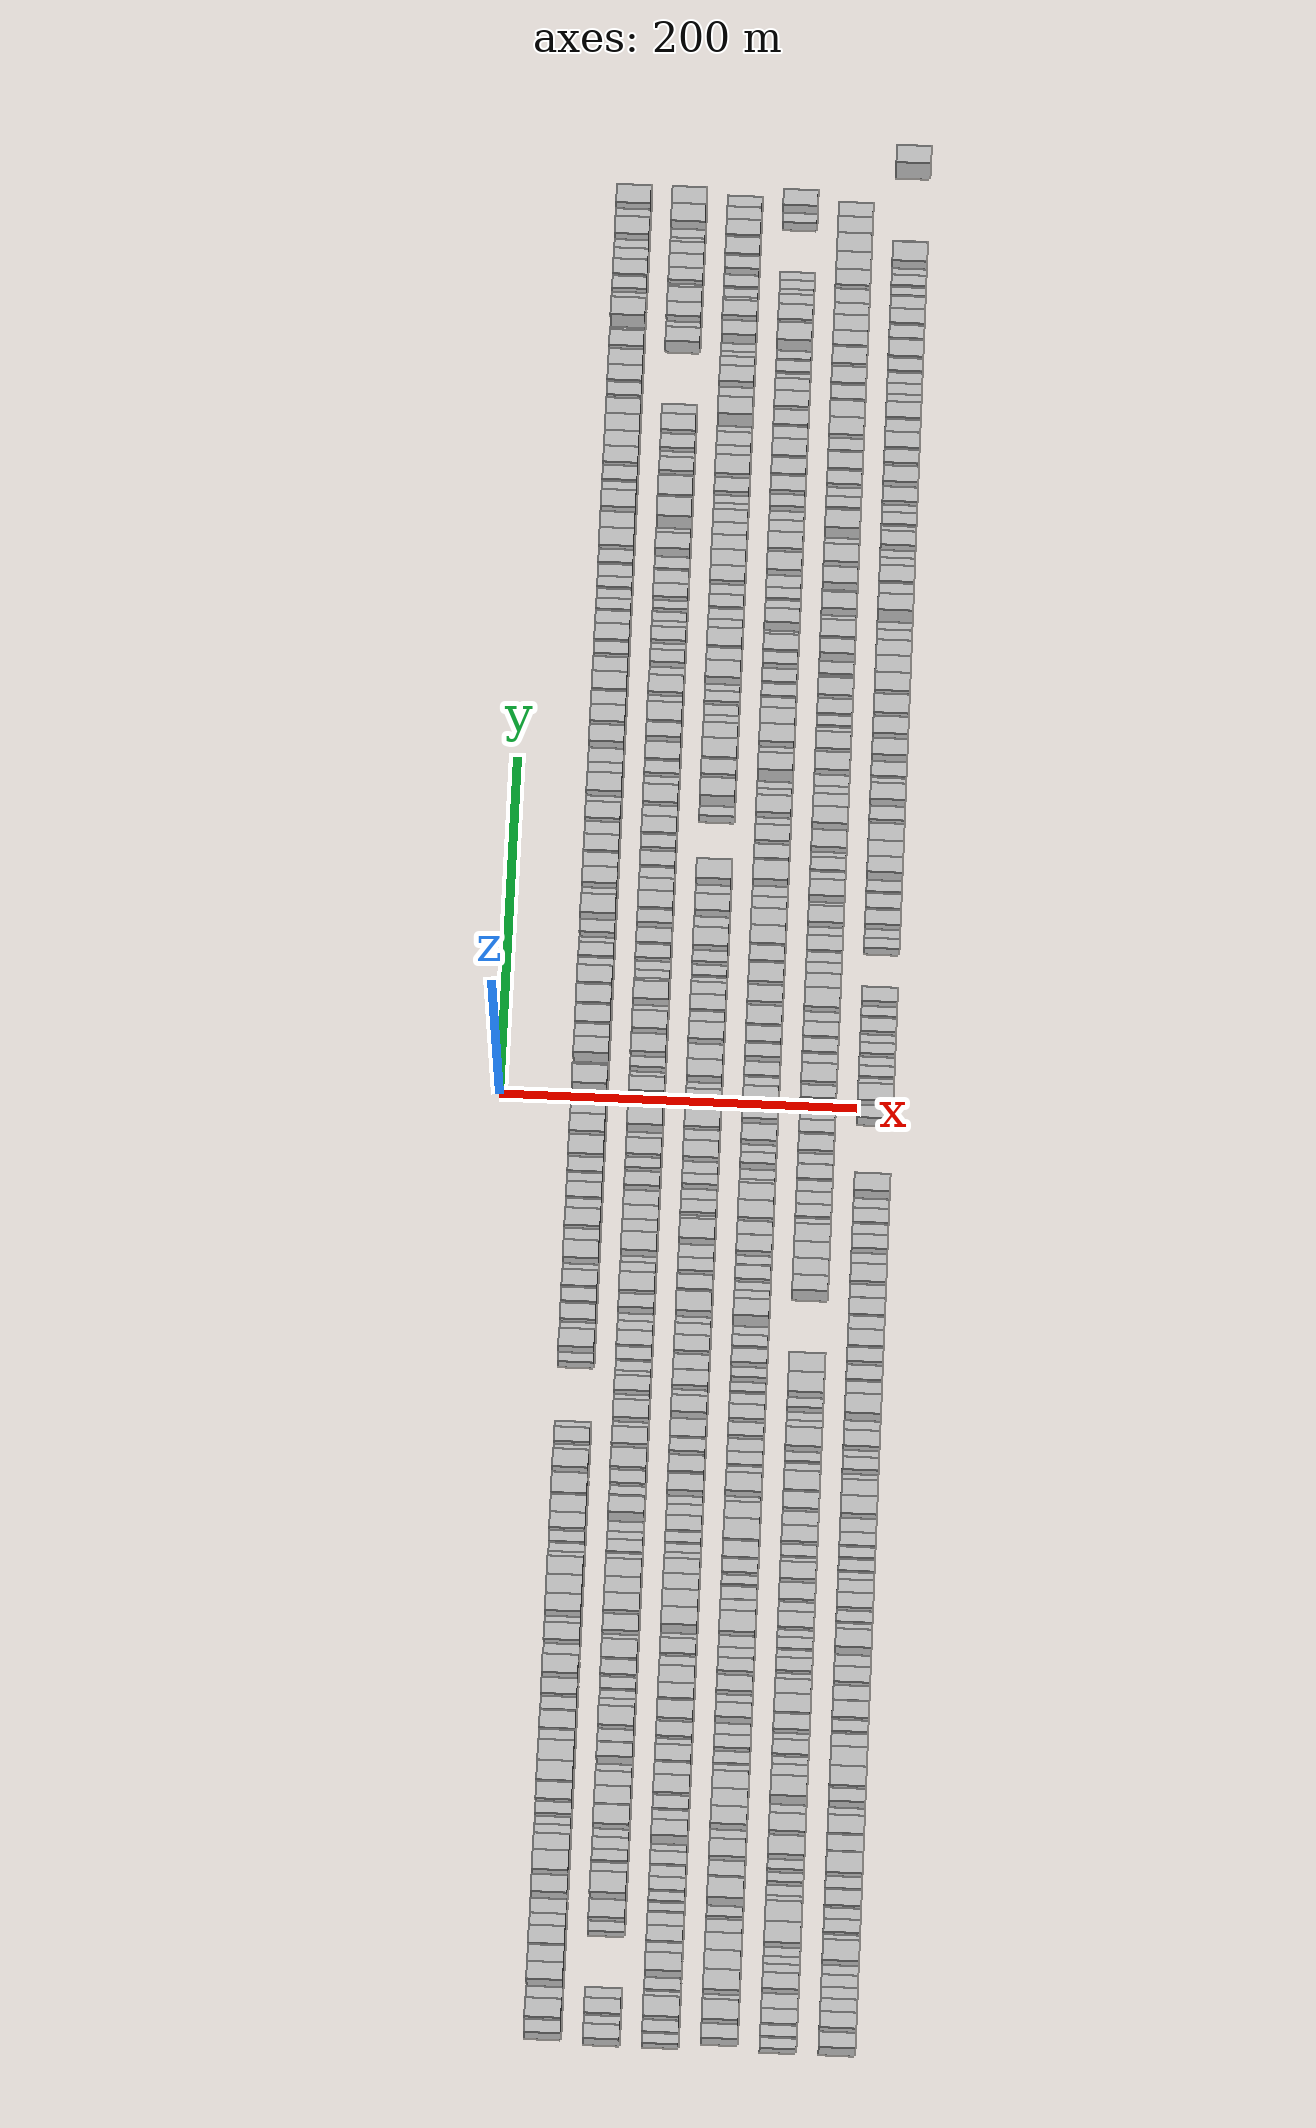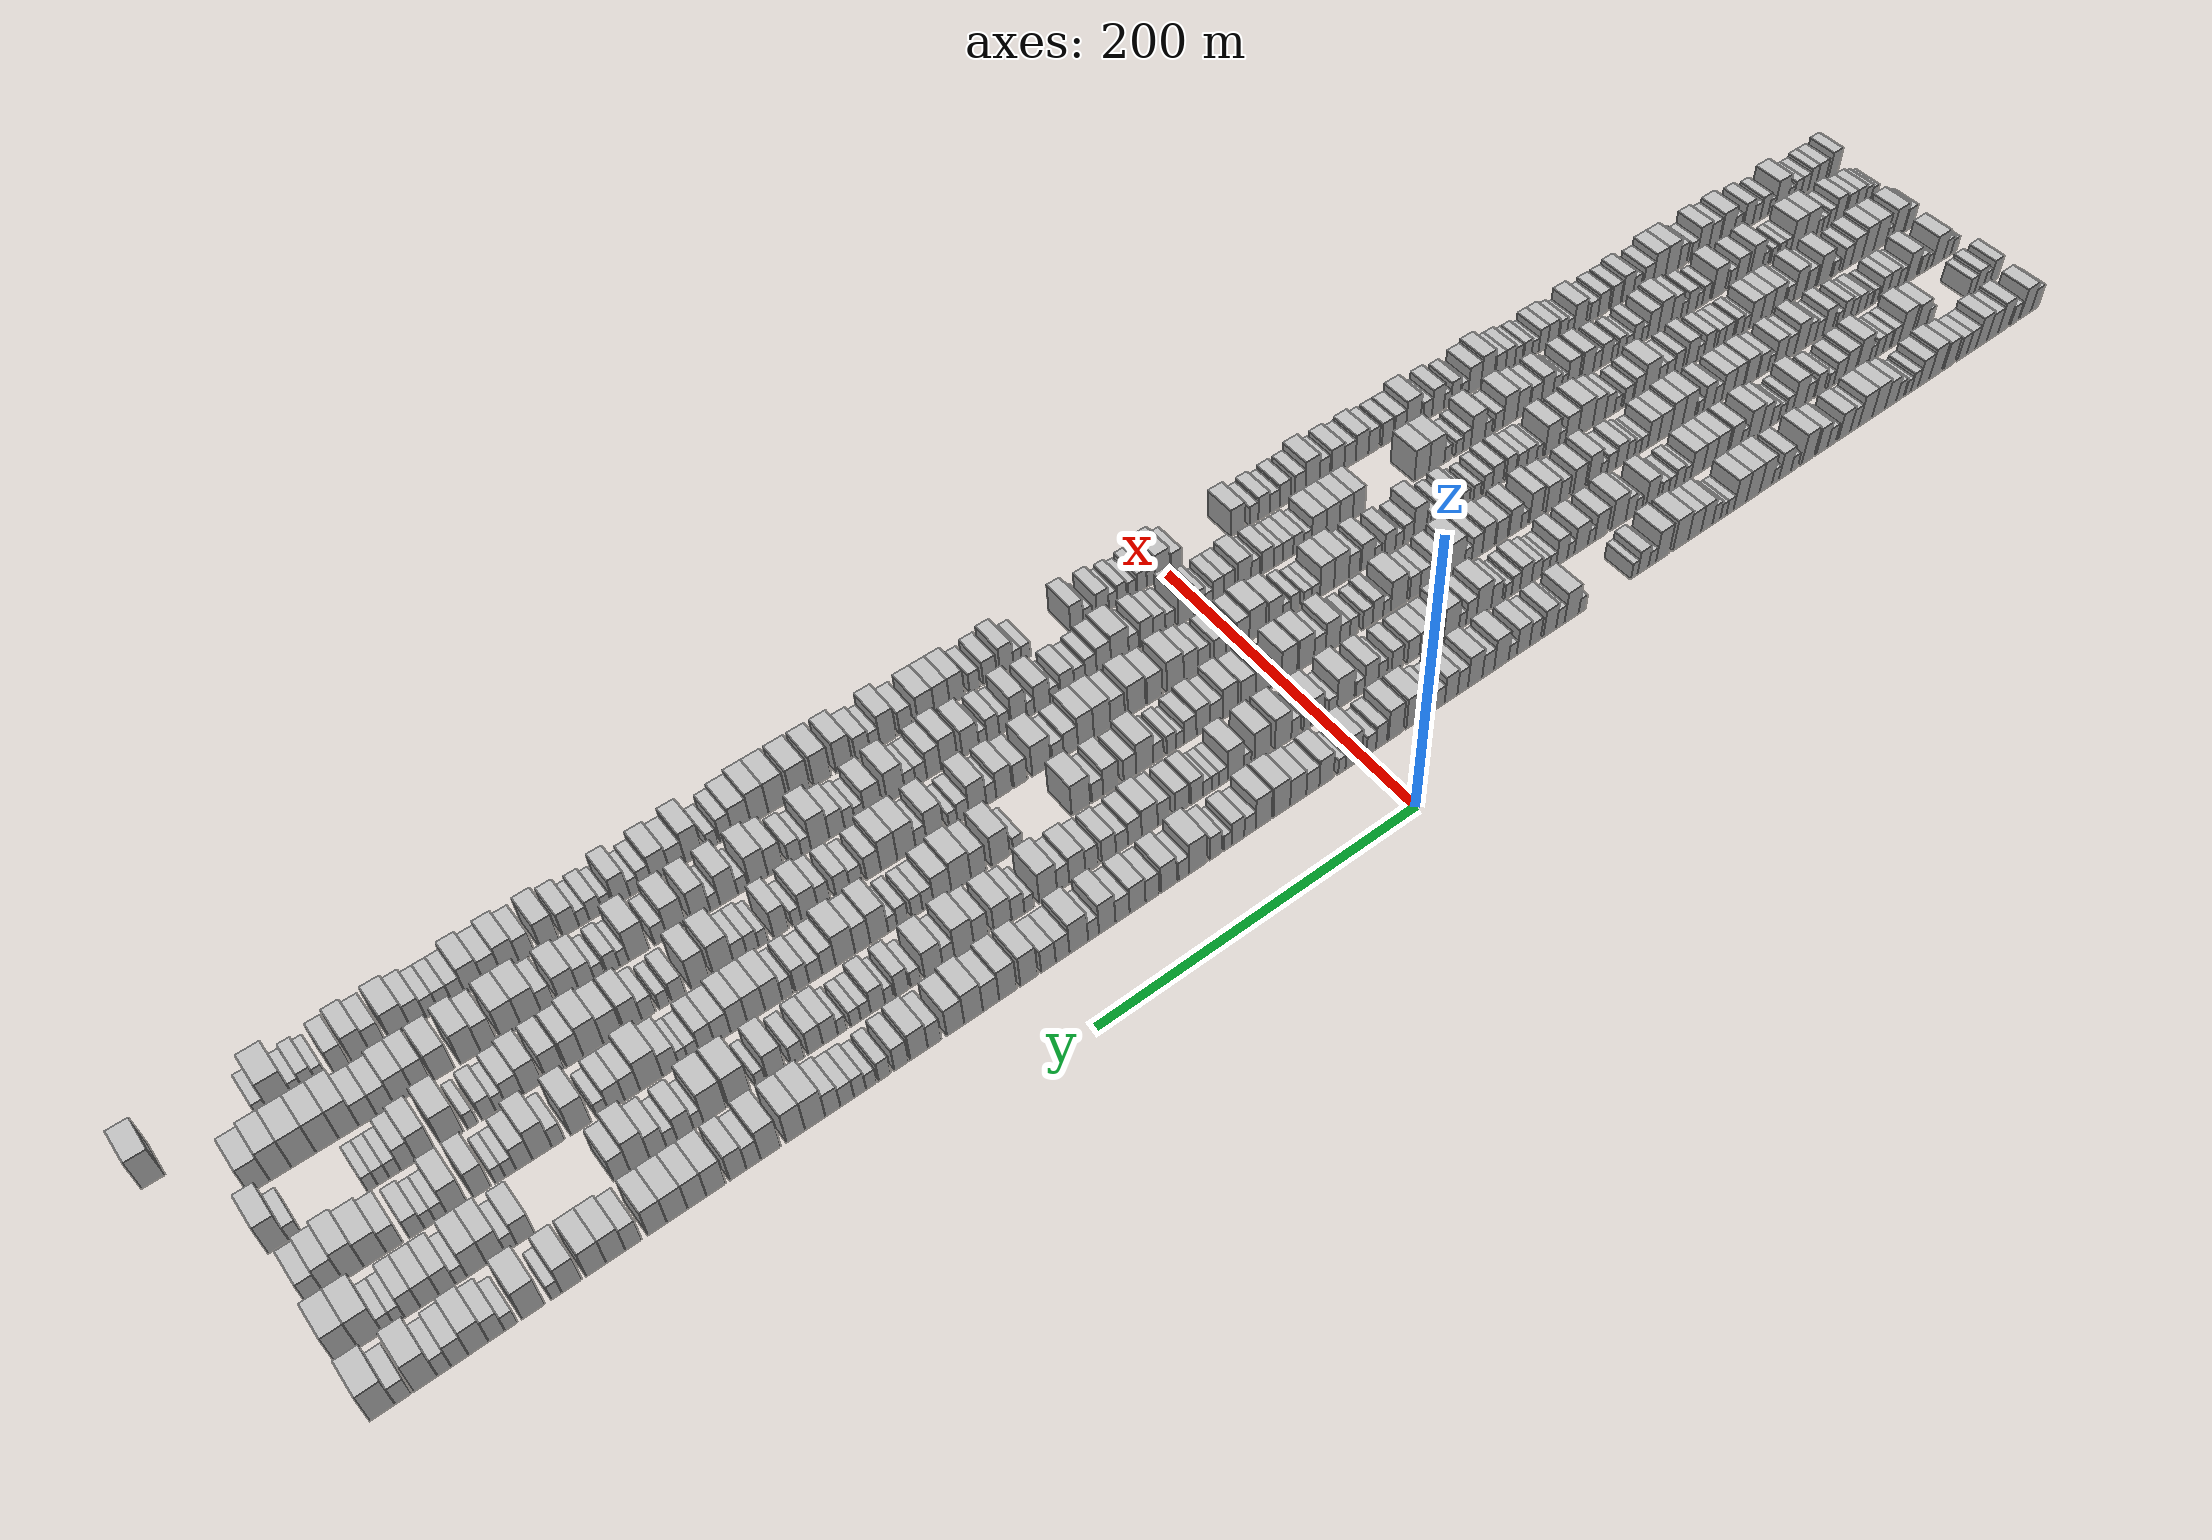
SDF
<sdf version="1.6">
 <world name="default">
  <scene>
   <sky><clouds><speed>12</speed></clouds></sky>
   <ambient>0.4 0.4 0.4 1</ambient>
   <background>0.7 0.7 0.7 1</background>
   <shadows>1</shadows>
  </scene>
  <gravity>0 0 -9.8066</gravity>
  <magnetic_field>6e-06 2.3e-05 -4.2e-05</magnetic_field>
  <physics default="0" name="default_physics" type="ode">
   <ode>
    <solver>
     <type>quick</type>
     <iters>10</iters>
     <sor>1.0</sor>
     <use_dynamic_moi_rescaling>0</use_dynamic_moi_rescaling>
    </solver>
    <constraints>
     <cfm>0</cfm>
     <erp>0.2</erp>
     <contact_max_correcting_vel>100</contact_max_correcting_vel>
     <contact_surface_layer>0.001</contact_surface_layer>
    </constraints>
   </ode>
   <max_step_size>0.004</max_step_size>
   <real_time_factor>1</real_time_factor>
   <real_time_update_rate>250</real_time_update_rate>
  </physics>
  <light name="sun" type="directional">
   <pose>0 0 10 0 0 0</pose>
   <diffuse>0.8 0.8 0.8 1</diffuse>
   <specular>0.2 0.2 0.2 1</specular>
   <attenuation>
    <range>1000</range>
    <constant>0.9</constant>
    <linear>0.01</linear>
    <quadratic>0.001</quadratic>
   </attenuation>
   <direction>-0.5 0.1 -0.9</direction>
  </light>
  <model name="building_1">
   <static>1</static>
   <pose>50.0000 -534.3650 0 0.000000 0.000000 0.000000</pose>
   <link name="link">
    <pose>0 0 9.00 0 0 0</pose>
    <collision name="collision"><geometry><box><size>20.0000 7.2701 18.0000</size></box></geometry></collision>
    <visual name="visual">
     <cast_shadows>0</cast_shadows>
     <geometry><box><size>20.0000 7.2701 18.0000</size></box></geometry>
     <material>
      <script>
       <uri>model://HANNAS_wall/materials/scripts</uri>
       <uri>model://HANNAS_wall/materials/textures</uri>
       <name>vrc/HANNAS_wall</name>
      </script>
     </material>
    </visual>
   </link>
  </model>
  <model name="building_2">
   <static>1</static>
   <pose>50.0000 -525.4408 0 0.000000 0.000000 0.000000</pose>
   <link name="link">
    <pose>0 0 12.00 0 0 0</pose>
    <collision name="collision"><geometry><box><size>20.0000 10.5782 24.0000</size></box></geometry></collision>
    <visual name="visual">
     <cast_shadows>0</cast_shadows>
     <geometry><box><size>20.0000 10.5782 24.0000</size></box></geometry>
     <material>
      <script>
       <uri>model://HANNAS_wall/materials/scripts</uri>
       <uri>model://HANNAS_wall/materials/textures</uri>
       <name>vrc/HANNAS_wall</name>
      </script>
     </material>
    </visual>
   </link>
  </model>
  <model name="building_3">
   <static>1</static>
   <pose>50.0000 -515.4774 0 0.000000 0.000000 0.000000</pose>
   <link name="link">
    <pose>0 0 7.50 0 0 0</pose>
    <collision name="collision"><geometry><box><size>20.0000 7.3486 15.0000</size></box></geometry></collision>
    <visual name="visual">
     <cast_shadows>0</cast_shadows>
     <geometry><box><size>20.0000 7.3486 15.0000</size></box></geometry>
     <material>
      <script>
       <uri>model://HANNAS_wall/materials/scripts</uri>
       <uri>model://HANNAS_wall/materials/textures</uri>
       <name>vrc/HANNAS_wall</name>
      </script>
     </material>
    </visual>
   </link>
  </model>
  <model name="building_4">
   <static>1</static>
   <pose>50.0000 -504.9186 0 0.000000 0.000000 0.000000</pose>
   <link name="link">
    <pose>0 0 12.00 0 0 0</pose>
    <collision name="collision"><geometry><box><size>20.0000 9.7689 24.0000</size></box></geometry></collision>
    <visual name="visual">
     <cast_shadows>0</cast_shadows>
     <geometry><box><size>20.0000 9.7689 24.0000</size></box></geometry>
     <material>
      <script>
       <uri>model://HANNAS_wall/materials/scripts</uri>
       <uri>model://HANNAS_wall/materials/textures</uri>
       <name>vrc/HANNAS_wall</name>
      </script>
     </material>
    </visual>
   </link>
  </model>
  <model name="building_5">
   <static>1</static>
   <pose>50.0000 -495.0016 0 0.000000 0.000000 0.000000</pose>
   <link name="link">
    <pose>0 0 10.50 0 0 0</pose>
    <collision name="collision"><geometry><box><size>20.0000 10.0650 21.0000</size></box></geometry></collision>
    <visual name="visual">
     <cast_shadows>0</cast_shadows>
     <geometry><box><size>20.0000 10.0650 21.0000</size></box></geometry>
     <material>
      <script>
       <uri>model://HANNAS_wall/materials/scripts</uri>
       <uri>model://HANNAS_wall/materials/textures</uri>
       <name>vrc/HANNAS_wall</name>
      </script>
     </material>
    </visual>
   </link>
  </model>
  <model name="building_6">
   <static>1</static>
   <pose>50.0000 -484.9039 0 0.000000 0.000000 0.000000</pose>
   <link name="link">
    <pose>0 0 12.00 0 0 0</pose>
    <collision name="collision"><geometry><box><size>20.0000 10.1304 24.0000</size></box></geometry></collision>
    <visual name="visual">
     <cast_shadows>0</cast_shadows>
     <geometry><box><size>20.0000 10.1304 24.0000</size></box></geometry>
     <material>
      <script>
       <uri>model://HANNAS_wall/materials/scripts</uri>
       <uri>model://HANNAS_wall/materials/textures</uri>
       <name>vrc/HANNAS_wall</name>
      </script>
     </material>
    </visual>
   </link>
  </model>
  <model name="building_7">
   <static>1</static>
   <pose>50.0000 -475.7787 0 0.000000 0.000000 0.000000</pose>
   <link name="link">
    <pose>0 0 9.00 0 0 0</pose>
    <collision name="collision"><geometry><box><size>20.0000 8.1200 18.0000</size></box></geometry></collision>
    <visual name="visual">
     <cast_shadows>0</cast_shadows>
     <geometry><box><size>20.0000 8.1200 18.0000</size></box></geometry>
     <material>
      <script>
       <uri>model://HANNAS_wall/materials/scripts</uri>
       <uri>model://HANNAS_wall/materials/textures</uri>
       <name>vrc/HANNAS_wall</name>
      </script>
     </material>
    </visual>
   </link>
  </model>
  <model name="building_8">
   <static>1</static>
   <pose>50.0000 -467.6427 0 0.000000 0.000000 0.000000</pose>
   <link name="link">
    <pose>0 0 9.00 0 0 0</pose>
    <collision name="collision"><geometry><box><size>20.0000 8.1521 18.0000</size></box></geometry></collision>
    <visual name="visual">
     <cast_shadows>0</cast_shadows>
     <geometry><box><size>20.0000 8.1521 18.0000</size></box></geometry>
     <material>
      <script>
       <uri>model://HANNAS_wall/materials/scripts</uri>
       <uri>model://HANNAS_wall/materials/textures</uri>
       <name>vrc/HANNAS_wall</name>
      </script>
     </material>
    </visual>
   </link>
  </model>
  <model name="building_9">
   <static>1</static>
   <pose>50.0000 -455.7142 0 0.000000 0.000000 0.000000</pose>
   <link name="link">
    <pose>0 0 10.50 0 0 0</pose>
    <collision name="collision"><geometry><box><size>20.0000 9.7048 21.0000</size></box></geometry></collision>
    <visual name="visual">
     <cast_shadows>0</cast_shadows>
     <geometry><box><size>20.0000 9.7048 21.0000</size></box></geometry>
     <material>
      <script>
       <uri>model://HANNAS_wall/materials/scripts</uri>
       <uri>model://HANNAS_wall/materials/textures</uri>
       <name>vrc/HANNAS_wall</name>
      </script>
     </material>
    </visual>
   </link>
  </model>
  <model name="building_10">
   <static>1</static>
   <pose>50.0000 -443.3077 0 0.000000 0.000000 0.000000</pose>
   <link name="link">
    <pose>0 0 12.00 0 0 0</pose>
    <collision name="collision"><geometry><box><size>20.0000 11.1083 24.0000</size></box></geometry></collision>
    <visual name="visual">
     <cast_shadows>0</cast_shadows>
     <geometry><box><size>20.0000 11.1083 24.0000</size></box></geometry>
     <material>
      <script>
       <uri>model://HANNAS_wall/materials/scripts</uri>
       <uri>model://HANNAS_wall/materials/textures</uri>
       <name>vrc/HANNAS_wall</name>
      </script>
     </material>
    </visual>
   </link>
  </model>
  <model name="building_11">
   <static>1</static>
   <pose>50.0000 -432.7694 0 0.000000 0.000000 0.000000</pose>
   <link name="link">
    <pose>0 0 10.50 0 0 0</pose>
    <collision name="collision"><geometry><box><size>20.0000 9.9684 21.0000</size></box></geometry></collision>
    <visual name="visual">
     <cast_shadows>0</cast_shadows>
     <geometry><box><size>20.0000 9.9684 21.0000</size></box></geometry>
     <material>
      <script>
       <uri>model://HANNAS_wall/materials/scripts</uri>
       <uri>model://HANNAS_wall/materials/textures</uri>
       <name>vrc/HANNAS_wall</name>
      </script>
     </material>
    </visual>
   </link>
  </model>
  <model name="building_12">
   <static>1</static>
   <pose>50.0000 -424.5682 0 0.000000 0.000000 0.000000</pose>
   <link name="link">
    <pose>0 0 7.50 0 0 0</pose>
    <collision name="collision"><geometry><box><size>20.0000 6.4340 15.0000</size></box></geometry></collision>
    <visual name="visual">
     <cast_shadows>0</cast_shadows>
     <geometry><box><size>20.0000 6.4340 15.0000</size></box></geometry>
     <material>
      <script>
       <uri>model://HANNAS_wall/materials/scripts</uri>
       <uri>model://HANNAS_wall/materials/textures</uri>
       <name>vrc/HANNAS_wall</name>
      </script>
     </material>
    </visual>
   </link>
  </model>
  <model name="building_13">
   <static>1</static>
   <pose>50.0000 -418.7945 0 0.000000 0.000000 0.000000</pose>
   <link name="link">
    <pose>0 0 6.00 0 0 0</pose>
    <collision name="collision"><geometry><box><size>20.0000 5.1134 12.0000</size></box></geometry></collision>
    <visual name="visual">
     <cast_shadows>0</cast_shadows>
     <geometry><box><size>20.0000 5.1134 12.0000</size></box></geometry>
     <material>
      <script>
       <uri>model://HANNAS_wall/materials/scripts</uri>
       <uri>model://HANNAS_wall/materials/textures</uri>
       <name>vrc/HANNAS_wall</name>
      </script>
     </material>
    </visual>
   </link>
  </model>
  <model name="building_14">
   <static>1</static>
   <pose>50.0000 -411.9129 0 0.000000 0.000000 0.000000</pose>
   <link name="link">
    <pose>0 0 7.50 0 0 0</pose>
    <collision name="collision"><geometry><box><size>20.0000 6.6497 15.0000</size></box></geometry></collision>
    <visual name="visual">
     <cast_shadows>0</cast_shadows>
     <geometry><box><size>20.0000 6.6497 15.0000</size></box></geometry>
     <material>
      <script>
       <uri>model://HANNAS_wall/materials/scripts</uri>
       <uri>model://HANNAS_wall/materials/textures</uri>
       <name>vrc/HANNAS_wall</name>
      </script>
     </material>
    </visual>
   </link>
  </model>
  <model name="building_15">
   <static>1</static>
   <pose>50.0000 -403.6830 0 0.000000 0.000000 0.000000</pose>
   <link name="link">
    <pose>0 0 10.50 0 0 0</pose>
    <collision name="collision"><geometry><box><size>20.0000 9.8102 21.0000</size></box></geometry></collision>
    <visual name="visual">
     <cast_shadows>0</cast_shadows>
     <geometry><box><size>20.0000 9.8102 21.0000</size></box></geometry>
     <material>
      <script>
       <uri>model://HANNAS_wall/materials/scripts</uri>
       <uri>model://HANNAS_wall/materials/textures</uri>
       <name>vrc/HANNAS_wall</name>
      </script>
     </material>
    </visual>
   </link>
  </model>
  <model name="building_16">
   <static>1</static>
   <pose>50.0000 -393.2084 0 0.000000 0.000000 0.000000</pose>
   <link name="link">
    <pose>0 0 12.00 0 0 0</pose>
    <collision name="collision"><geometry><box><size>20.0000 11.1389 24.0000</size></box></geometry></collision>
    <visual name="visual">
     <cast_shadows>0</cast_shadows>
     <geometry><box><size>20.0000 11.1389 24.0000</size></box></geometry>
     <material>
      <script>
       <uri>model://HANNAS_wall/materials/scripts</uri>
       <uri>model://HANNAS_wall/materials/textures</uri>
       <name>vrc/HANNAS_wall</name>
      </script>
     </material>
    </visual>
   </link>
  </model>
  <model name="building_17">
   <static>1</static>
   <pose>50.0000 -381.8397 0 0.000000 0.000000 0.000000</pose>
   <link name="link">
    <pose>0 0 12.00 0 0 0</pose>
    <collision name="collision"><geometry><box><size>20.0000 11.5986 24.0000</size></box></geometry></collision>
    <visual name="visual">
     <cast_shadows>0</cast_shadows>
     <geometry><box><size>20.0000 11.5986 24.0000</size></box></geometry>
     <material>
      <script>
       <uri>model://HANNAS_wall/materials/scripts</uri>
       <uri>model://HANNAS_wall/materials/textures</uri>
       <name>vrc/HANNAS_wall</name>
      </script>
     </material>
    </visual>
   </link>
  </model>
  <model name="building_18">
   <static>1</static>
   <pose>50.0000 -372.4252 0 0.000000 0.000000 0.000000</pose>
   <link name="link">
    <pose>0 0 9.00 0 0 0</pose>
    <collision name="collision"><geometry><box><size>20.0000 7.2304 18.0000</size></box></geometry></collision>
    <visual name="visual">
     <cast_shadows>0</cast_shadows>
     <geometry><box><size>20.0000 7.2304 18.0000</size></box></geometry>
     <material>
      <script>
       <uri>model://HANNAS_wall/materials/scripts</uri>
       <uri>model://HANNAS_wall/materials/textures</uri>
       <name>vrc/HANNAS_wall</name>
      </script>
     </material>
    </visual>
   </link>
  </model>
  <model name="building_19">
   <static>1</static>
   <pose>50.0000 -363.7485 0 0.000000 0.000000 0.000000</pose>
   <link name="link">
    <pose>0 0 10.50 0 0 0</pose>
    <collision name="collision"><geometry><box><size>20.0000 10.1231 21.0000</size></box></geometry></collision>
    <visual name="visual">
     <cast_shadows>0</cast_shadows>
     <geometry><box><size>20.0000 10.1231 21.0000</size></box></geometry>
     <material>
      <script>
       <uri>model://HANNAS_wall/materials/scripts</uri>
       <uri>model://HANNAS_wall/materials/textures</uri>
       <name>vrc/HANNAS_wall</name>
      </script>
     </material>
    </visual>
   </link>
  </model>
  <model name="building_20">
   <static>1</static>
   <pose>50.0000 -353.0496 0 0.000000 0.000000 0.000000</pose>
   <link name="link">
    <pose>0 0 7.50 0 0 0</pose>
    <collision name="collision"><geometry><box><size>20.0000 7.2747 15.0000</size></box></geometry></collision>
    <visual name="visual">
     <cast_shadows>0</cast_shadows>
     <geometry><box><size>20.0000 7.2747 15.0000</size></box></geometry>
     <material>
      <script>
       <uri>model://HANNAS_wall/materials/scripts</uri>
       <uri>model://HANNAS_wall/materials/textures</uri>
       <name>vrc/HANNAS_wall</name>
      </script>
     </material>
    </visual>
   </link>
  </model>
  <model name="building_21">
   <static>1</static>
   <pose>50.0000 -344.8619 0 0.000000 0.000000 0.000000</pose>
   <link name="link">
    <pose>0 0 10.50 0 0 0</pose>
    <collision name="collision"><geometry><box><size>20.0000 9.1007 21.0000</size></box></geometry></collision>
    <visual name="visual">
     <cast_shadows>0</cast_shadows>
     <geometry><box><size>20.0000 9.1007 21.0000</size></box></geometry>
     <material>
      <script>
       <uri>model://HANNAS_wall/materials/scripts</uri>
       <uri>model://HANNAS_wall/materials/textures</uri>
       <name>vrc/HANNAS_wall</name>
      </script>
     </material>
    </visual>
   </link>
  </model>
  <model name="building_22">
   <static>1</static>
   <pose>50.0000 -333.0687 0 0.000000 0.000000 0.000000</pose>
   <link name="link">
    <pose>0 0 12.00 0 0 0</pose>
    <collision name="collision"><geometry><box><size>20.0000 10.4857 24.0000</size></box></geometry></collision>
    <visual name="visual">
     <cast_shadows>0</cast_shadows>
     <geometry><box><size>20.0000 10.4857 24.0000</size></box></geometry>
     <material>
      <script>
       <uri>model://HANNAS_wall/materials/scripts</uri>
       <uri>model://HANNAS_wall/materials/textures</uri>
       <name>vrc/HANNAS_wall</name>
      </script>
     </material>
    </visual>
   </link>
  </model>
  <model name="building_23">
   <static>1</static>
   <pose>50.0000 -321.8268 0 0.000000 0.000000 0.000000</pose>
   <link name="link">
    <pose>0 0 6.00 0 0 0</pose>
    <collision name="collision"><geometry><box><size>20.0000 5.9980 12.0000</size></box></geometry></collision>
    <visual name="visual">
     <cast_shadows>0</cast_shadows>
     <geometry><box><size>20.0000 5.9980 12.0000</size></box></geometry>
     <material>
      <script>
       <uri>model://HANNAS_wall/materials/scripts</uri>
       <uri>model://HANNAS_wall/materials/textures</uri>
       <name>vrc/HANNAS_wall</name>
      </script>
     </material>
    </visual>
   </link>
  </model>
  <model name="building_24">
   <static>1</static>
   <pose>50.0000 -313.9311 0 0.000000 0.000000 0.000000</pose>
   <link name="link">
    <pose>0 0 10.50 0 0 0</pose>
    <collision name="collision"><geometry><box><size>20.0000 9.7935 21.0000</size></box></geometry></collision>
    <visual name="visual">
     <cast_shadows>0</cast_shadows>
     <geometry><box><size>20.0000 9.7935 21.0000</size></box></geometry>
     <material>
      <script>
       <uri>model://HANNAS_wall/materials/scripts</uri>
       <uri>model://HANNAS_wall/materials/textures</uri>
       <name>vrc/HANNAS_wall</name>
      </script>
     </material>
    </visual>
   </link>
  </model>
  <model name="building_25">
   <static>1</static>
   <pose>50.0000 -306.1624 0 0.000000 0.000000 0.000000</pose>
   <link name="link">
    <pose>0 0 6.00 0 0 0</pose>
    <collision name="collision"><geometry><box><size>20.0000 5.7439 12.0000</size></box></geometry></collision>
    <visual name="visual">
     <cast_shadows>0</cast_shadows>
     <geometry><box><size>20.0000 5.7439 12.0000</size></box></geometry>
     <material>
      <script>
       <uri>model://HANNAS_wall/materials/scripts</uri>
       <uri>model://HANNAS_wall/materials/textures</uri>
       <name>vrc/HANNAS_wall</name>
      </script>
     </material>
    </visual>
   </link>
  </model>
  <model name="building_26">
   <static>1</static>
   <pose>50.0000 -298.3166 0 0.000000 0.000000 0.000000</pose>
   <link name="link">
    <pose>0 0 12.00 0 0 0</pose>
    <collision name="collision"><geometry><box><size>20.0000 9.9476 24.0000</size></box></geometry></collision>
    <visual name="visual">
     <cast_shadows>0</cast_shadows>
     <geometry><box><size>20.0000 9.9476 24.0000</size></box></geometry>
     <material>
      <script>
       <uri>model://HANNAS_wall/materials/scripts</uri>
       <uri>model://HANNAS_wall/materials/textures</uri>
       <name>vrc/HANNAS_wall</name>
      </script>
     </material>
    </visual>
   </link>
  </model>
  <model name="building_27">
   <static>1</static>
   <pose>50.0000 -287.9435 0 0.000000 0.000000 0.000000</pose>
   <link name="link">
    <pose>0 0 12.00 0 0 0</pose>
    <collision name="collision"><geometry><box><size>20.0000 10.7986 24.0000</size></box></geometry></collision>
    <visual name="visual">
     <cast_shadows>0</cast_shadows>
     <geometry><box><size>20.0000 10.7986 24.0000</size></box></geometry>
     <material>
      <script>
       <uri>model://HANNAS_wall/materials/scripts</uri>
       <uri>model://HANNAS_wall/materials/textures</uri>
       <name>vrc/HANNAS_wall</name>
      </script>
     </material>
    </visual>
   </link>
  </model>
  <model name="building_28">
   <static>1</static>
   <pose>50.0000 -277.3953 0 0.000000 0.000000 0.000000</pose>
   <link name="link">
    <pose>0 0 12.00 0 0 0</pose>
    <collision name="collision"><geometry><box><size>20.0000 10.2977 24.0000</size></box></geometry></collision>
    <visual name="visual">
     <cast_shadows>0</cast_shadows>
     <geometry><box><size>20.0000 10.2977 24.0000</size></box></geometry>
     <material>
      <script>
       <uri>model://HANNAS_wall/materials/scripts</uri>
       <uri>model://HANNAS_wall/materials/textures</uri>
       <name>vrc/HANNAS_wall</name>
      </script>
     </material>
    </visual>
   </link>
  </model>
  <model name="building_29">
   <static>1</static>
   <pose>50.0000 -269.3623 0 0.000000 0.000000 0.000000</pose>
   <link name="link">
    <pose>0 0 6.00 0 0 0</pose>
    <collision name="collision"><geometry><box><size>20.0000 5.7684 12.0000</size></box></geometry></collision>
    <visual name="visual">
     <cast_shadows>0</cast_shadows>
     <geometry><box><size>20.0000 5.7684 12.0000</size></box></geometry>
     <material>
      <script>
       <uri>model://HANNAS_wall/materials/scripts</uri>
       <uri>model://HANNAS_wall/materials/textures</uri>
       <name>vrc/HANNAS_wall</name>
      </script>
     </material>
    </visual>
   </link>
  </model>
  <model name="building_30">
   <static>1</static>
   <pose>50.0000 -263.9876 0 0.000000 0.000000 0.000000</pose>
   <link name="link">
    <pose>0 0 6.00 0 0 0</pose>
    <collision name="collision"><geometry><box><size>20.0000 4.9809 12.0000</size></box></geometry></collision>
    <visual name="visual">
     <cast_shadows>0</cast_shadows>
     <geometry><box><size>20.0000 4.9809 12.0000</size></box></geometry>
     <material>
      <script>
       <uri>model://HANNAS_wall/materials/scripts</uri>
       <uri>model://HANNAS_wall/materials/textures</uri>
       <name>vrc/HANNAS_wall</name>
      </script>
     </material>
    </visual>
   </link>
  </model>
  <model name="building_31">
   <static>1</static>
   <pose>50.0000 -258.3971 0 0.000000 0.000000 0.000000</pose>
   <link name="link">
    <pose>0 0 7.50 0 0 0</pose>
    <collision name="collision"><geometry><box><size>20.0000 6.2002 15.0000</size></box></geometry></collision>
    <visual name="visual">
     <cast_shadows>0</cast_shadows>
     <geometry><box><size>20.0000 6.2002 15.0000</size></box></geometry>
     <material>
      <script>
       <uri>model://HANNAS_wall/materials/scripts</uri>
       <uri>model://HANNAS_wall/materials/textures</uri>
       <name>vrc/HANNAS_wall</name>
      </script>
     </material>
    </visual>
   </link>
  </model>
  <model name="building_32">
   <static>1</static>
   <pose>50.0000 -250.7903 0 0.000000 0.000000 0.000000</pose>
   <link name="link">
    <pose>0 0 10.50 0 0 0</pose>
    <collision name="collision"><geometry><box><size>20.0000 9.0134 21.0000</size></box></geometry></collision>
    <visual name="visual">
     <cast_shadows>0</cast_shadows>
     <geometry><box><size>20.0000 9.0134 21.0000</size></box></geometry>
     <material>
      <script>
       <uri>model://HANNAS_wall/materials/scripts</uri>
       <uri>model://HANNAS_wall/materials/textures</uri>
       <name>vrc/HANNAS_wall</name>
      </script>
     </material>
    </visual>
   </link>
  </model>
  <model name="building_33">
   <static>1</static>
   <pose>50.0000 -241.2008 0 0.000000 0.000000 0.000000</pose>
   <link name="link">
    <pose>0 0 10.50 0 0 0</pose>
    <collision name="collision"><geometry><box><size>20.0000 10.1658 21.0000</size></box></geometry></collision>
    <visual name="visual">
     <cast_shadows>0</cast_shadows>
     <geometry><box><size>20.0000 10.1658 21.0000</size></box></geometry>
     <material>
      <script>
       <uri>model://HANNAS_wall/materials/scripts</uri>
       <uri>model://HANNAS_wall/materials/textures</uri>
       <name>vrc/HANNAS_wall</name>
      </script>
     </material>
    </visual>
   </link>
  </model>
  <model name="building_34">
   <static>1</static>
   <pose>50.0000 -230.2196 0 0.000000 0.000000 0.000000</pose>
   <link name="link">
    <pose>0 0 12.00 0 0 0</pose>
    <collision name="collision"><geometry><box><size>20.0000 11.7965 24.0000</size></box></geometry></collision>
    <visual name="visual">
     <cast_shadows>0</cast_shadows>
     <geometry><box><size>20.0000 11.7965 24.0000</size></box></geometry>
     <material>
      <script>
       <uri>model://HANNAS_wall/materials/scripts</uri>
       <uri>model://HANNAS_wall/materials/textures</uri>
       <name>vrc/HANNAS_wall</name>
      </script>
     </material>
    </visual>
   </link>
  </model>
  <model name="building_35">
   <static>1</static>
   <pose>50.0000 -216.1596 0 0.000000 0.000000 0.000000</pose>
   <link name="link">
    <pose>0 0 12.00 0 0 0</pose>
    <collision name="collision"><geometry><box><size>20.0000 10.3236 24.0000</size></box></geometry></collision>
    <visual name="visual">
     <cast_shadows>0</cast_shadows>
     <geometry><box><size>20.0000 10.3236 24.0000</size></box></geometry>
     <material>
      <script>
       <uri>model://HANNAS_wall/materials/scripts</uri>
       <uri>model://HANNAS_wall/materials/textures</uri>
       <name>vrc/HANNAS_wall</name>
      </script>
     </material>
    </visual>
   </link>
  </model>
  <model name="building_36">
   <static>1</static>
   <pose>50.0000 -208.0337 0 0.000000 0.000000 0.000000</pose>
   <link name="link">
    <pose>0 0 6.00 0 0 0</pose>
    <collision name="collision"><geometry><box><size>20.0000 5.9284 12.0000</size></box></geometry></collision>
    <visual name="visual">
     <cast_shadows>0</cast_shadows>
     <geometry><box><size>20.0000 5.9284 12.0000</size></box></geometry>
     <material>
      <script>
       <uri>model://HANNAS_wall/materials/scripts</uri>
       <uri>model://HANNAS_wall/materials/textures</uri>
       <name>vrc/HANNAS_wall</name>
      </script>
     </material>
    </visual>
   </link>
  </model>
  <model name="building_37">
   <static>1</static>
   <pose>50.0000 -200.9124 0 0.000000 0.000000 0.000000</pose>
   <link name="link">
    <pose>0 0 9.00 0 0 0</pose>
    <collision name="collision"><geometry><box><size>20.0000 8.3141 18.0000</size></box></geometry></collision>
    <visual name="visual">
     <cast_shadows>0</cast_shadows>
     <geometry><box><size>20.0000 8.3141 18.0000</size></box></geometry>
     <material>
      <script>
       <uri>model://HANNAS_wall/materials/scripts</uri>
       <uri>model://HANNAS_wall/materials/textures</uri>
       <name>vrc/HANNAS_wall</name>
      </script>
     </material>
    </visual>
   </link>
  </model>
  <model name="building_38">
   <static>1</static>
   <pose>50.0000 -194.2948 0 0.000000 0.000000 0.000000</pose>
   <link name="link">
    <pose>0 0 6.00 0 0 0</pose>
    <collision name="collision"><geometry><box><size>20.0000 4.9212 12.0000</size></box></geometry></collision>
    <visual name="visual">
     <cast_shadows>0</cast_shadows>
     <geometry><box><size>20.0000 4.9212 12.0000</size></box></geometry>
     <material>
      <script>
       <uri>model://HANNAS_wall/materials/scripts</uri>
       <uri>model://HANNAS_wall/materials/textures</uri>
       <name>vrc/HANNAS_wall</name>
      </script>
     </material>
    </visual>
   </link>
  </model>
  <model name="building_39">
   <static>1</static>
   <pose>50.0000 -154.8706 0 0.000000 0.000000 0.000000</pose>
   <link name="link">
    <pose>0 0 6.00 0 0 0</pose>
    <collision name="collision"><geometry><box><size>20.0000 5.3091 12.0000</size></box></geometry></collision>
    <visual name="visual">
     <cast_shadows>0</cast_shadows>
     <geometry><box><size>20.0000 5.3091 12.0000</size></box></geometry>
     <material>
      <script>
       <uri>model://HANNAS_wall/materials/scripts</uri>
       <uri>model://HANNAS_wall/materials/textures</uri>
       <name>vrc/HANNAS_wall</name>
      </script>
     </material>
    </visual>
   </link>
  </model>
  <model name="building_40">
   <static>1</static>
   <pose>50.0000 -146.9574 0 0.000000 0.000000 0.000000</pose>
   <link name="link">
    <pose>0 0 12.00 0 0 0</pose>
    <collision name="collision"><geometry><box><size>20.0000 10.5174 24.0000</size></box></geometry></collision>
    <visual name="visual">
     <cast_shadows>0</cast_shadows>
     <geometry><box><size>20.0000 10.5174 24.0000</size></box></geometry>
     <material>
      <script>
       <uri>model://HANNAS_wall/materials/scripts</uri>
       <uri>model://HANNAS_wall/materials/textures</uri>
       <name>vrc/HANNAS_wall</name>
      </script>
     </material>
    </visual>
   </link>
  </model>
  <model name="building_41">
   <static>1</static>
   <pose>50.0000 -138.5620 0 0.000000 0.000000 0.000000</pose>
   <link name="link">
    <pose>0 0 7.50 0 0 0</pose>
    <collision name="collision"><geometry><box><size>20.0000 6.2733 15.0000</size></box></geometry></collision>
    <visual name="visual">
     <cast_shadows>0</cast_shadows>
     <geometry><box><size>20.0000 6.2733 15.0000</size></box></geometry>
     <material>
      <script>
       <uri>model://HANNAS_wall/materials/scripts</uri>
       <uri>model://HANNAS_wall/materials/textures</uri>
       <name>vrc/HANNAS_wall</name>
      </script>
     </material>
    </visual>
   </link>
  </model>
  <model name="building_42">
   <static>1</static>
   <pose>50.0000 -130.7770 0 0.000000 0.000000 0.000000</pose>
   <link name="link">
    <pose>0 0 10.50 0 0 0</pose>
    <collision name="collision"><geometry><box><size>20.0000 9.2967 21.0000</size></box></geometry></collision>
    <visual name="visual">
     <cast_shadows>0</cast_shadows>
     <geometry><box><size>20.0000 9.2967 21.0000</size></box></geometry>
     <material>
      <script>
       <uri>model://HANNAS_wall/materials/scripts</uri>
       <uri>model://HANNAS_wall/materials/textures</uri>
       <name>vrc/HANNAS_wall</name>
      </script>
     </material>
    </visual>
   </link>
  </model>
  <model name="building_43">
   <static>1</static>
   <pose>50.0000 -120.1200 0 0.000000 0.000000 0.000000</pose>
   <link name="link">
    <pose>0 0 9.00 0 0 0</pose>
    <collision name="collision"><geometry><box><size>20.0000 8.0174 18.0000</size></box></geometry></collision>
    <visual name="visual">
     <cast_shadows>0</cast_shadows>
     <geometry><box><size>20.0000 8.0174 18.0000</size></box></geometry>
     <material>
      <script>
       <uri>model://HANNAS_wall/materials/scripts</uri>
       <uri>model://HANNAS_wall/materials/textures</uri>
       <name>vrc/HANNAS_wall</name>
      </script>
     </material>
    </visual>
   </link>
  </model>
  <model name="building_44">
   <static>1</static>
   <pose>50.0000 -111.3945 0 0.000000 0.000000 0.000000</pose>
   <link name="link">
    <pose>0 0 10.50 0 0 0</pose>
    <collision name="collision"><geometry><box><size>20.0000 9.4337 21.0000</size></box></geometry></collision>
    <visual name="visual">
     <cast_shadows>0</cast_shadows>
     <geometry><box><size>20.0000 9.4337 21.0000</size></box></geometry>
     <material>
      <script>
       <uri>model://HANNAS_wall/materials/scripts</uri>
       <uri>model://HANNAS_wall/materials/textures</uri>
       <name>vrc/HANNAS_wall</name>
      </script>
     </material>
    </visual>
   </link>
  </model>
  <model name="building_45">
   <static>1</static>
   <pose>50.0000 -103.7214 0 0.000000 0.000000 0.000000</pose>
   <link name="link">
    <pose>0 0 6.00 0 0 0</pose>
    <collision name="collision"><geometry><box><size>20.0000 5.9125 12.0000</size></box></geometry></collision>
    <visual name="visual">
     <cast_shadows>0</cast_shadows>
     <geometry><box><size>20.0000 5.9125 12.0000</size></box></geometry>
     <material>
      <script>
       <uri>model://HANNAS_wall/materials/scripts</uri>
       <uri>model://HANNAS_wall/materials/textures</uri>
       <name>vrc/HANNAS_wall</name>
      </script>
     </material>
    </visual>
   </link>
  </model>
  <model name="building_46">
   <static>1</static>
   <pose>50.0000 -95.5847 0 0.000000 0.000000 0.000000</pose>
   <link name="link">
    <pose>0 0 12.00 0 0 0</pose>
    <collision name="collision"><geometry><box><size>20.0000 10.3608 24.0000</size></box></geometry></collision>
    <visual name="visual">
     <cast_shadows>0</cast_shadows>
     <geometry><box><size>20.0000 10.3608 24.0000</size></box></geometry>
     <material>
      <script>
       <uri>model://HANNAS_wall/materials/scripts</uri>
       <uri>model://HANNAS_wall/materials/textures</uri>
       <name>vrc/HANNAS_wall</name>
      </script>
     </material>
    </visual>
   </link>
  </model>
  <model name="building_47">
   <static>1</static>
   <pose>50.0000 -86.1859 0 0.000000 0.000000 0.000000</pose>
   <link name="link">
    <pose>0 0 9.00 0 0 0</pose>
    <collision name="collision"><geometry><box><size>20.0000 8.4368 18.0000</size></box></geometry></collision>
    <visual name="visual">
     <cast_shadows>0</cast_shadows>
     <geometry><box><size>20.0000 8.4368 18.0000</size></box></geometry>
     <material>
      <script>
       <uri>model://HANNAS_wall/materials/scripts</uri>
       <uri>model://HANNAS_wall/materials/textures</uri>
       <name>vrc/HANNAS_wall</name>
      </script>
     </material>
    </visual>
   </link>
  </model>
  <model name="building_48">
   <static>1</static>
   <pose>50.0000 -76.9097 0 0.000000 0.000000 0.000000</pose>
   <link name="link">
    <pose>0 0 12.00 0 0 0</pose>
    <collision name="collision"><geometry><box><size>20.0000 10.1156 24.0000</size></box></geometry></collision>
    <visual name="visual">
     <cast_shadows>0</cast_shadows>
     <geometry><box><size>20.0000 10.1156 24.0000</size></box></geometry>
     <material>
      <script>
       <uri>model://HANNAS_wall/materials/scripts</uri>
       <uri>model://HANNAS_wall/materials/textures</uri>
       <name>vrc/HANNAS_wall</name>
      </script>
     </material>
    </visual>
   </link>
  </model>
  <model name="building_49">
   <static>1</static>
   <pose>50.0000 -68.1743 0 0.000000 0.000000 0.000000</pose>
   <link name="link">
    <pose>0 0 9.00 0 0 0</pose>
    <collision name="collision"><geometry><box><size>20.0000 7.3551 18.0000</size></box></geometry></collision>
    <visual name="visual">
     <cast_shadows>0</cast_shadows>
     <geometry><box><size>20.0000 7.3551 18.0000</size></box></geometry>
     <material>
      <script>
       <uri>model://HANNAS_wall/materials/scripts</uri>
       <uri>model://HANNAS_wall/materials/textures</uri>
       <name>vrc/HANNAS_wall</name>
      </script>
     </material>
    </visual>
   </link>
  </model>
  <model name="building_50">
   <static>1</static>
   <pose>50.0000 -59.9899 0 0.000000 0.000000 0.000000</pose>
   <link name="link">
    <pose>0 0 10.50 0 0 0</pose>
    <collision name="collision"><geometry><box><size>20.0000 9.0137 21.0000</size></box></geometry></collision>
    <visual name="visual">
     <cast_shadows>0</cast_shadows>
     <geometry><box><size>20.0000 9.0137 21.0000</size></box></geometry>
     <material>
      <script>
       <uri>model://HANNAS_wall/materials/scripts</uri>
       <uri>model://HANNAS_wall/materials/textures</uri>
       <name>vrc/HANNAS_wall</name>
      </script>
     </material>
    </visual>
   </link>
  </model>
  <model name="building_51">
   <static>1</static>
   <pose>50.0000 -51.9817 0 0.000000 0.000000 0.000000</pose>
   <link name="link">
    <pose>0 0 7.50 0 0 0</pose>
    <collision name="collision"><geometry><box><size>20.0000 7.0027 15.0000</size></box></geometry></collision>
    <visual name="visual">
     <cast_shadows>0</cast_shadows>
     <geometry><box><size>20.0000 7.0027 15.0000</size></box></geometry>
     <material>
      <script>
       <uri>model://HANNAS_wall/materials/scripts</uri>
       <uri>model://HANNAS_wall/materials/textures</uri>
       <name>vrc/HANNAS_wall</name>
      </script>
     </material>
    </visual>
   </link>
  </model>
  <model name="building_52">
   <static>1</static>
   <pose>50.0000 -44.2990 0 0.000000 0.000000 0.000000</pose>
   <link name="link">
    <pose>0 0 9.00 0 0 0</pose>
    <collision name="collision"><geometry><box><size>20.0000 8.3628 18.0000</size></box></geometry></collision>
    <visual name="visual">
     <cast_shadows>0</cast_shadows>
     <geometry><box><size>20.0000 8.3628 18.0000</size></box></geometry>
     <material>
      <script>
       <uri>model://HANNAS_wall/materials/scripts</uri>
       <uri>model://HANNAS_wall/materials/textures</uri>
       <name>vrc/HANNAS_wall</name>
      </script>
     </material>
    </visual>
   </link>
  </model>
  <model name="building_53">
   <static>1</static>
   <pose>50.0000 -34.5240 0 0.000000 0.000000 0.000000</pose>
   <link name="link">
    <pose>0 0 12.00 0 0 0</pose>
    <collision name="collision"><geometry><box><size>20.0000 11.1871 24.0000</size></box></geometry></collision>
    <visual name="visual">
     <cast_shadows>0</cast_shadows>
     <geometry><box><size>20.0000 11.1871 24.0000</size></box></geometry>
     <material>
      <script>
       <uri>model://HANNAS_wall/materials/scripts</uri>
       <uri>model://HANNAS_wall/materials/textures</uri>
       <name>vrc/HANNAS_wall</name>
      </script>
     </material>
    </visual>
   </link>
  </model>
  <model name="building_54">
   <static>1</static>
   <pose>50.0000 -21.7975 0 0.000000 0.000000 0.000000</pose>
   <link name="link">
    <pose>0 0 12.00 0 0 0</pose>
    <collision name="collision"><geometry><box><size>20.0000 10.2659 24.0000</size></box></geometry></collision>
    <visual name="visual">
     <cast_shadows>0</cast_shadows>
     <geometry><box><size>20.0000 10.2659 24.0000</size></box></geometry>
     <material>
      <script>
       <uri>model://HANNAS_wall/materials/scripts</uri>
       <uri>model://HANNAS_wall/materials/textures</uri>
       <name>vrc/HANNAS_wall</name>
      </script>
     </material>
    </visual>
   </link>
  </model>
  <model name="building_55">
   <static>1</static>
   <pose>50.0000 -11.9538 0 0.000000 0.000000 0.000000</pose>
   <link name="link">
    <pose>0 0 9.00 0 0 0</pose>
    <collision name="collision"><geometry><box><size>20.0000 7.4216 18.0000</size></box></geometry></collision>
    <visual name="visual">
     <cast_shadows>0</cast_shadows>
     <geometry><box><size>20.0000 7.4216 18.0000</size></box></geometry>
     <material>
      <script>
       <uri>model://HANNAS_wall/materials/scripts</uri>
       <uri>model://HANNAS_wall/materials/textures</uri>
       <name>vrc/HANNAS_wall</name>
      </script>
     </material>
    </visual>
   </link>
  </model>
  <model name="building_56">
   <static>1</static>
   <pose>50.0000 -4.9942 0 0.000000 0.000000 0.000000</pose>
   <link name="link">
    <pose>0 0 7.50 0 0 0</pose>
    <collision name="collision"><geometry><box><size>20.0000 6.4976 15.0000</size></box></geometry></collision>
    <visual name="visual">
     <cast_shadows>0</cast_shadows>
     <geometry><box><size>20.0000 6.4976 15.0000</size></box></geometry>
     <material>
      <script>
       <uri>model://HANNAS_wall/materials/scripts</uri>
       <uri>model://HANNAS_wall/materials/textures</uri>
       <name>vrc/HANNAS_wall</name>
      </script>
     </material>
    </visual>
   </link>
  </model>
  <model name="building_57">
   <static>1</static>
   <pose>50.0000 6.7767 0 0.000000 0.000000 0.000000</pose>
   <link name="link">
    <pose>0 0 12.00 0 0 0</pose>
    <collision name="collision"><geometry><box><size>20.0000 11.0440 24.0000</size></box></geometry></collision>
    <visual name="visual">
     <cast_shadows>0</cast_shadows>
     <geometry><box><size>20.0000 11.0440 24.0000</size></box></geometry>
     <material>
      <script>
       <uri>model://HANNAS_wall/materials/scripts</uri>
       <uri>model://HANNAS_wall/materials/textures</uri>
       <name>vrc/HANNAS_wall</name>
      </script>
     </material>
    </visual>
   </link>
  </model>
  <model name="building_58">
   <static>1</static>
   <pose>50.0000 14.7008 0 0.000000 0.000000 0.000000</pose>
   <link name="link">
    <pose>0 0 6.00 0 0 0</pose>
    <collision name="collision"><geometry><box><size>20.0000 4.8043 12.0000</size></box></geometry></collision>
    <visual name="visual">
     <cast_shadows>0</cast_shadows>
     <geometry><box><size>20.0000 4.8043 12.0000</size></box></geometry>
     <material>
      <script>
       <uri>model://HANNAS_wall/materials/scripts</uri>
       <uri>model://HANNAS_wall/materials/textures</uri>
       <name>vrc/HANNAS_wall</name>
      </script>
     </material>
    </visual>
   </link>
  </model>
  <model name="building_59">
   <static>1</static>
   <pose>50.0000 24.8382 0 0.000000 0.000000 0.000000</pose>
   <link name="link">
    <pose>0 0 10.50 0 0 0</pose>
    <collision name="collision"><geometry><box><size>20.0000 9.4705 21.0000</size></box></geometry></collision>
    <visual name="visual">
     <cast_shadows>0</cast_shadows>
     <geometry><box><size>20.0000 9.4705 21.0000</size></box></geometry>
     <material>
      <script>
       <uri>model://HANNAS_wall/materials/scripts</uri>
       <uri>model://HANNAS_wall/materials/textures</uri>
       <name>vrc/HANNAS_wall</name>
      </script>
     </material>
    </visual>
   </link>
  </model>
  <model name="building_60">
   <static>1</static>
   <pose>50.0000 33.8824 0 0.000000 0.000000 0.000000</pose>
   <link name="link">
    <pose>0 0 9.00 0 0 0</pose>
    <collision name="collision"><geometry><box><size>20.0000 8.6178 18.0000</size></box></geometry></collision>
    <visual name="visual">
     <cast_shadows>0</cast_shadows>
     <geometry><box><size>20.0000 8.6178 18.0000</size></box></geometry>
     <material>
      <script>
       <uri>model://HANNAS_wall/materials/scripts</uri>
       <uri>model://HANNAS_wall/materials/textures</uri>
       <name>vrc/HANNAS_wall</name>
      </script>
     </material>
    </visual>
   </link>
  </model>
  <model name="building_61">
   <static>1</static>
   <pose>50.0000 43.4396 0 0.000000 0.000000 0.000000</pose>
   <link name="link">
    <pose>0 0 10.50 0 0 0</pose>
    <collision name="collision"><geometry><box><size>20.0000 10.4966 21.0000</size></box></geometry></collision>
    <visual name="visual">
     <cast_shadows>0</cast_shadows>
     <geometry><box><size>20.0000 10.4966 21.0000</size></box></geometry>
     <material>
      <script>
       <uri>model://HANNAS_wall/materials/scripts</uri>
       <uri>model://HANNAS_wall/materials/textures</uri>
       <name>vrc/HANNAS_wall</name>
      </script>
     </material>
    </visual>
   </link>
  </model>
  <model name="building_62">
   <static>1</static>
   <pose>50.0000 54.1108 0 0.000000 0.000000 0.000000</pose>
   <link name="link">
    <pose>0 0 12.00 0 0 0</pose>
    <collision name="collision"><geometry><box><size>20.0000 10.8460 24.0000</size></box></geometry></collision>
    <visual name="visual">
     <cast_shadows>0</cast_shadows>
     <geometry><box><size>20.0000 10.8460 24.0000</size></box></geometry>
     <material>
      <script>
       <uri>model://HANNAS_wall/materials/scripts</uri>
       <uri>model://HANNAS_wall/materials/textures</uri>
       <name>vrc/HANNAS_wall</name>
      </script>
     </material>
    </visual>
   </link>
  </model>
  <model name="building_63">
   <static>1</static>
   <pose>50.0000 65.6435 0 0.000000 0.000000 0.000000</pose>
   <link name="link">
    <pose>0 0 12.00 0 0 0</pose>
    <collision name="collision"><geometry><box><size>20.0000 10.2193 24.0000</size></box></geometry></collision>
    <visual name="visual">
     <cast_shadows>0</cast_shadows>
     <geometry><box><size>20.0000 10.2193 24.0000</size></box></geometry>
     <material>
      <script>
       <uri>model://HANNAS_wall/materials/scripts</uri>
       <uri>model://HANNAS_wall/materials/textures</uri>
       <name>vrc/HANNAS_wall</name>
      </script>
     </material>
    </visual>
   </link>
  </model>
  <model name="building_64">
   <static>1</static>
   <pose>50.0000 74.4742 0 0.000000 0.000000 0.000000</pose>
   <link name="link">
    <pose>0 0 7.50 0 0 0</pose>
    <collision name="collision"><geometry><box><size>20.0000 7.4421 15.0000</size></box></geometry></collision>
    <visual name="visual">
     <cast_shadows>0</cast_shadows>
     <geometry><box><size>20.0000 7.4421 15.0000</size></box></geometry>
     <material>
      <script>
       <uri>model://HANNAS_wall/materials/scripts</uri>
       <uri>model://HANNAS_wall/materials/textures</uri>
       <name>vrc/HANNAS_wall</name>
      </script>
     </material>
    </visual>
   </link>
  </model>
  <model name="building_65">
   <static>1</static>
   <pose>50.0000 82.2153 0 0.000000 0.000000 0.000000</pose>
   <link name="link">
    <pose>0 0 9.00 0 0 0</pose>
    <collision name="collision"><geometry><box><size>20.0000 8.0402 18.0000</size></box></geometry></collision>
    <visual name="visual">
     <cast_shadows>0</cast_shadows>
     <geometry><box><size>20.0000 8.0402 18.0000</size></box></geometry>
     <material>
      <script>
       <uri>model://HANNAS_wall/materials/scripts</uri>
       <uri>model://HANNAS_wall/materials/textures</uri>
       <name>vrc/HANNAS_wall</name>
      </script>
     </material>
    </visual>
   </link>
  </model>
  <model name="building_66">
   <static>1</static>
   <pose>50.0000 88.7413 0 0.000000 0.000000 0.000000</pose>
   <link name="link">
    <pose>0 0 6.00 0 0 0</pose>
    <collision name="collision"><geometry><box><size>20.0000 5.0116 12.0000</size></box></geometry></collision>
    <visual name="visual">
     <cast_shadows>0</cast_shadows>
     <geometry><box><size>20.0000 5.0116 12.0000</size></box></geometry>
     <material>
      <script>
       <uri>model://HANNAS_wall/materials/scripts</uri>
       <uri>model://HANNAS_wall/materials/textures</uri>
       <name>vrc/HANNAS_wall</name>
      </script>
     </material>
    </visual>
   </link>
  </model>
  <model name="building_67">
   <static>1</static>
   <pose>50.0000 95.9590 0 0.000000 0.000000 0.000000</pose>
   <link name="link">
    <pose>0 0 9.00 0 0 0</pose>
    <collision name="collision"><geometry><box><size>20.0000 7.4239 18.0000</size></box></geometry></collision>
    <visual name="visual">
     <cast_shadows>0</cast_shadows>
     <geometry><box><size>20.0000 7.4239 18.0000</size></box></geometry>
     <material>
      <script>
       <uri>model://HANNAS_wall/materials/scripts</uri>
       <uri>model://HANNAS_wall/materials/textures</uri>
       <name>vrc/HANNAS_wall</name>
      </script>
     </material>
    </visual>
   </link>
  </model>
  <model name="building_68">
   <static>1</static>
   <pose>50.0000 107.2907 0 0.000000 0.000000 0.000000</pose>
   <link name="link">
    <pose>0 0 12.00 0 0 0</pose>
    <collision name="collision"><geometry><box><size>20.0000 11.2395 24.0000</size></box></geometry></collision>
    <visual name="visual">
     <cast_shadows>0</cast_shadows>
     <geometry><box><size>20.0000 11.2395 24.0000</size></box></geometry>
     <material>
      <script>
       <uri>model://HANNAS_wall/materials/scripts</uri>
       <uri>model://HANNAS_wall/materials/textures</uri>
       <name>vrc/HANNAS_wall</name>
      </script>
     </material>
    </visual>
   </link>
  </model>
  <model name="building_69">
   <static>1</static>
   <pose>50.0000 116.2270 0 0.000000 0.000000 0.000000</pose>
   <link name="link">
    <pose>0 0 7.50 0 0 0</pose>
    <collision name="collision"><geometry><box><size>20.0000 6.6330 15.0000</size></box></geometry></collision>
    <visual name="visual">
     <cast_shadows>0</cast_shadows>
     <geometry><box><size>20.0000 6.6330 15.0000</size></box></geometry>
     <material>
      <script>
       <uri>model://HANNAS_wall/materials/scripts</uri>
       <uri>model://HANNAS_wall/materials/textures</uri>
       <name>vrc/HANNAS_wall</name>
      </script>
     </material>
    </visual>
   </link>
  </model>
  <model name="building_70">
   <static>1</static>
   <pose>50.0000 125.4357 0 0.000000 0.000000 0.000000</pose>
   <link name="link">
    <pose>0 0 10.50 0 0 0</pose>
    <collision name="collision"><geometry><box><size>20.0000 9.7845 21.0000</size></box></geometry></collision>
    <visual name="visual">
     <cast_shadows>0</cast_shadows>
     <geometry><box><size>20.0000 9.7845 21.0000</size></box></geometry>
     <material>
      <script>
       <uri>model://HANNAS_wall/materials/scripts</uri>
       <uri>model://HANNAS_wall/materials/textures</uri>
       <name>vrc/HANNAS_wall</name>
      </script>
     </material>
    </visual>
   </link>
  </model>
  <model name="building_71">
   <static>1</static>
   <pose>50.0000 135.5813 0 0.000000 0.000000 0.000000</pose>
   <link name="link">
    <pose>0 0 9.00 0 0 0</pose>
    <collision name="collision"><geometry><box><size>20.0000 8.5066 18.0000</size></box></geometry></collision>
    <visual name="visual">
     <cast_shadows>0</cast_shadows>
     <geometry><box><size>20.0000 8.5066 18.0000</size></box></geometry>
     <material>
      <script>
       <uri>model://HANNAS_wall/materials/scripts</uri>
       <uri>model://HANNAS_wall/materials/textures</uri>
       <name>vrc/HANNAS_wall</name>
      </script>
     </material>
    </visual>
   </link>
  </model>
  <model name="building_72">
   <static>1</static>
   <pose>50.0000 144.6615 0 0.000000 0.000000 0.000000</pose>
   <link name="link">
    <pose>0 0 10.50 0 0 0</pose>
    <collision name="collision"><geometry><box><size>20.0000 9.6538 21.0000</size></box></geometry></collision>
    <visual name="visual">
     <cast_shadows>0</cast_shadows>
     <geometry><box><size>20.0000 9.6538 21.0000</size></box></geometry>
     <material>
      <script>
       <uri>model://HANNAS_wall/materials/scripts</uri>
       <uri>model://HANNAS_wall/materials/textures</uri>
       <name>vrc/HANNAS_wall</name>
      </script>
     </material>
    </visual>
   </link>
  </model>
  <model name="building_73">
   <static>1</static>
   <pose>50.0000 153.7642 0 0.000000 0.000000 0.000000</pose>
   <link name="link">
    <pose>0 0 9.00 0 0 0</pose>
    <collision name="collision"><geometry><box><size>20.0000 8.5515 18.0000</size></box></geometry></collision>
    <visual name="visual">
     <cast_shadows>0</cast_shadows>
     <geometry><box><size>20.0000 8.5515 18.0000</size></box></geometry>
     <material>
      <script>
       <uri>model://HANNAS_wall/materials/scripts</uri>
       <uri>model://HANNAS_wall/materials/textures</uri>
       <name>vrc/HANNAS_wall</name>
      </script>
     </material>
    </visual>
   </link>
  </model>
  <model name="building_74">
   <static>1</static>
   <pose>50.0000 162.9716 0 0.000000 0.000000 0.000000</pose>
   <link name="link">
    <pose>0 0 12.00 0 0 0</pose>
    <collision name="collision"><geometry><box><size>20.0000 9.8633 24.0000</size></box></geometry></collision>
    <visual name="visual">
     <cast_shadows>0</cast_shadows>
     <geometry><box><size>20.0000 9.8633 24.0000</size></box></geometry>
     <material>
      <script>
       <uri>model://HANNAS_wall/materials/scripts</uri>
       <uri>model://HANNAS_wall/materials/textures</uri>
       <name>vrc/HANNAS_wall</name>
      </script>
     </material>
    </visual>
   </link>
  </model>
  <model name="building_75">
   <static>1</static>
   <pose>50.0000 171.1340 0 0.000000 0.000000 0.000000</pose>
   <link name="link">
    <pose>0 0 7.50 0 0 0</pose>
    <collision name="collision"><geometry><box><size>20.0000 6.4616 15.0000</size></box></geometry></collision>
    <visual name="visual">
     <cast_shadows>0</cast_shadows>
     <geometry><box><size>20.0000 6.4616 15.0000</size></box></geometry>
     <material>
      <script>
       <uri>model://HANNAS_wall/materials/scripts</uri>
       <uri>model://HANNAS_wall/materials/textures</uri>
       <name>vrc/HANNAS_wall</name>
      </script>
     </material>
    </visual>
   </link>
  </model>
  <model name="building_76">
   <static>1</static>
   <pose>50.0000 179.8879 0 0.000000 0.000000 0.000000</pose>
   <link name="link">
    <pose>0 0 12.00 0 0 0</pose>
    <collision name="collision"><geometry><box><size>20.0000 11.0463 24.0000</size></box></geometry></collision>
    <visual name="visual">
     <cast_shadows>0</cast_shadows>
     <geometry><box><size>20.0000 11.0463 24.0000</size></box></geometry>
     <material>
      <script>
       <uri>model://HANNAS_wall/materials/scripts</uri>
       <uri>model://HANNAS_wall/materials/textures</uri>
       <name>vrc/HANNAS_wall</name>
      </script>
     </material>
    </visual>
   </link>
  </model>
  <model name="building_77">
   <static>1</static>
   <pose>50.0000 189.4567 0 0.000000 0.000000 0.000000</pose>
   <link name="link">
    <pose>0 0 9.00 0 0 0</pose>
    <collision name="collision"><geometry><box><size>20.0000 8.0913 18.0000</size></box></geometry></collision>
    <visual name="visual">
     <cast_shadows>0</cast_shadows>
     <geometry><box><size>20.0000 8.0913 18.0000</size></box></geometry>
     <material>
      <script>
       <uri>model://HANNAS_wall/materials/scripts</uri>
       <uri>model://HANNAS_wall/materials/textures</uri>
       <name>vrc/HANNAS_wall</name>
      </script>
     </material>
    </visual>
   </link>
  </model>
  <model name="building_78">
   <static>1</static>
   <pose>50.0000 197.7735 0 0.000000 0.000000 0.000000</pose>
   <link name="link">
    <pose>0 0 9.00 0 0 0</pose>
    <collision name="collision"><geometry><box><size>20.0000 8.5423 18.0000</size></box></geometry></collision>
    <visual name="visual">
     <cast_shadows>0</cast_shadows>
     <geometry><box><size>20.0000 8.5423 18.0000</size></box></geometry>
     <material>
      <script>
       <uri>model://HANNAS_wall/materials/scripts</uri>
       <uri>model://HANNAS_wall/materials/textures</uri>
       <name>vrc/HANNAS_wall</name>
      </script>
     </material>
    </visual>
   </link>
  </model>
  <model name="building_79">
   <static>1</static>
   <pose>50.0000 209.0818 0 0.000000 0.000000 0.000000</pose>
   <link name="link">
    <pose>0 0 12.00 0 0 0</pose>
    <collision name="collision"><geometry><box><size>20.0000 10.0741 24.0000</size></box></geometry></collision>
    <visual name="visual">
     <cast_shadows>0</cast_shadows>
     <geometry><box><size>20.0000 10.0741 24.0000</size></box></geometry>
     <material>
      <script>
       <uri>model://HANNAS_wall/materials/scripts</uri>
       <uri>model://HANNAS_wall/materials/textures</uri>
       <name>vrc/HANNAS_wall</name>
      </script>
     </material>
    </visual>
   </link>
  </model>
  <model name="building_80">
   <static>1</static>
   <pose>50.0000 221.1915 0 0.000000 0.000000 0.000000</pose>
   <link name="link">
    <pose>0 0 12.00 0 0 0</pose>
    <collision name="collision"><geometry><box><size>20.0000 10.1454 24.0000</size></box></geometry></collision>
    <visual name="visual">
     <cast_shadows>0</cast_shadows>
     <geometry><box><size>20.0000 10.1454 24.0000</size></box></geometry>
     <material>
      <script>
       <uri>model://HANNAS_wall/materials/scripts</uri>
       <uri>model://HANNAS_wall/materials/textures</uri>
       <name>vrc/HANNAS_wall</name>
      </script>
     </material>
    </visual>
   </link>
  </model>
  <model name="building_81">
   <static>1</static>
   <pose>50.0000 230.9055 0 0.000000 0.000000 0.000000</pose>
   <link name="link">
    <pose>0 0 10.50 0 0 0</pose>
    <collision name="collision"><geometry><box><size>20.0000 9.2827 21.0000</size></box></geometry></collision>
    <visual name="visual">
     <cast_shadows>0</cast_shadows>
     <geometry><box><size>20.0000 9.2827 21.0000</size></box></geometry>
     <material>
      <script>
       <uri>model://HANNAS_wall/materials/scripts</uri>
       <uri>model://HANNAS_wall/materials/textures</uri>
       <name>vrc/HANNAS_wall</name>
      </script>
     </material>
    </visual>
   </link>
  </model>
  <model name="building_82">
   <static>1</static>
   <pose>50.0000 240.8791 0 0.000000 0.000000 0.000000</pose>
   <link name="link">
    <pose>0 0 12.00 0 0 0</pose>
    <collision name="collision"><geometry><box><size>20.0000 10.6645 24.0000</size></box></geometry></collision>
    <visual name="visual">
     <cast_shadows>0</cast_shadows>
     <geometry><box><size>20.0000 10.6645 24.0000</size></box></geometry>
     <material>
      <script>
       <uri>model://HANNAS_wall/materials/scripts</uri>
       <uri>model://HANNAS_wall/materials/textures</uri>
       <name>vrc/HANNAS_wall</name>
      </script>
     </material>
    </visual>
   </link>
  </model>
  <model name="building_83">
   <static>1</static>
   <pose>50.0000 251.1147 0 0.000000 0.000000 0.000000</pose>
   <link name="link">
    <pose>0 0 10.50 0 0 0</pose>
    <collision name="collision"><geometry><box><size>20.0000 9.8066 21.0000</size></box></geometry></collision>
    <visual name="visual">
     <cast_shadows>0</cast_shadows>
     <geometry><box><size>20.0000 9.8066 21.0000</size></box></geometry>
     <material>
      <script>
       <uri>model://HANNAS_wall/materials/scripts</uri>
       <uri>model://HANNAS_wall/materials/textures</uri>
       <name>vrc/HANNAS_wall</name>
      </script>
     </material>
    </visual>
   </link>
  </model>
  <model name="building_84">
   <static>1</static>
   <pose>50.0000 262.7763 0 0.000000 0.000000 0.000000</pose>
   <link name="link">
    <pose>0 0 9.00 0 0 0</pose>
    <collision name="collision"><geometry><box><size>20.0000 7.5166 18.0000</size></box></geometry></collision>
    <visual name="visual">
     <cast_shadows>0</cast_shadows>
     <geometry><box><size>20.0000 7.5166 18.0000</size></box></geometry>
     <material>
      <script>
       <uri>model://HANNAS_wall/materials/scripts</uri>
       <uri>model://HANNAS_wall/materials/textures</uri>
       <name>vrc/HANNAS_wall</name>
      </script>
     </material>
    </visual>
   </link>
  </model>
  <model name="building_85">
   <static>1</static>
   <pose>50.0000 271.4097 0 0.000000 0.000000 0.000000</pose>
   <link name="link">
    <pose>0 0 10.50 0 0 0</pose>
    <collision name="collision"><geometry><box><size>20.0000 9.7501 21.0000</size></box></geometry></collision>
    <visual name="visual">
     <cast_shadows>0</cast_shadows>
     <geometry><box><size>20.0000 9.7501 21.0000</size></box></geometry>
     <material>
      <script>
       <uri>model://HANNAS_wall/materials/scripts</uri>
       <uri>model://HANNAS_wall/materials/textures</uri>
       <name>vrc/HANNAS_wall</name>
      </script>
     </material>
    </visual>
   </link>
  </model>
  <model name="building_86">
   <static>1</static>
   <pose>50.0000 281.1702 0 0.000000 0.000000 0.000000</pose>
   <link name="link">
    <pose>0 0 9.00 0 0 0</pose>
    <collision name="collision"><geometry><box><size>20.0000 7.7707 18.0000</size></box></geometry></collision>
    <visual name="visual">
     <cast_shadows>0</cast_shadows>
     <geometry><box><size>20.0000 7.7707 18.0000</size></box></geometry>
     <material>
      <script>
       <uri>model://HANNAS_wall/materials/scripts</uri>
       <uri>model://HANNAS_wall/materials/textures</uri>
       <name>vrc/HANNAS_wall</name>
      </script>
     </material>
    </visual>
   </link>
  </model>
  <model name="building_87">
   <static>1</static>
   <pose>50.0000 290.3380 0 0.000000 0.000000 0.000000</pose>
   <link name="link">
    <pose>0 0 7.50 0 0 0</pose>
    <collision name="collision"><geometry><box><size>20.0000 6.5649 15.0000</size></box></geometry></collision>
    <visual name="visual">
     <cast_shadows>0</cast_shadows>
     <geometry><box><size>20.0000 6.5649 15.0000</size></box></geometry>
     <material>
      <script>
       <uri>model://HANNAS_wall/materials/scripts</uri>
       <uri>model://HANNAS_wall/materials/textures</uri>
       <name>vrc/HANNAS_wall</name>
      </script>
     </material>
    </visual>
   </link>
  </model>
  <model name="building_88">
   <static>1</static>
   <pose>50.0000 297.5629 0 0.000000 0.000000 0.000000</pose>
   <link name="link">
    <pose>0 0 6.00 0 0 0</pose>
    <collision name="collision"><geometry><box><size>20.0000 5.8850 12.0000</size></box></geometry></collision>
    <visual name="visual">
     <cast_shadows>0</cast_shadows>
     <geometry><box><size>20.0000 5.8850 12.0000</size></box></geometry>
     <material>
      <script>
       <uri>model://HANNAS_wall/materials/scripts</uri>
       <uri>model://HANNAS_wall/materials/textures</uri>
       <name>vrc/HANNAS_wall</name>
      </script>
     </material>
    </visual>
   </link>
  </model>
  <model name="building_89">
   <static>1</static>
   <pose>50.0000 303.7001 0 0.000000 0.000000 0.000000</pose>
   <link name="link">
    <pose>0 0 7.50 0 0 0</pose>
    <collision name="collision"><geometry><box><size>20.0000 6.3894 15.0000</size></box></geometry></collision>
    <visual name="visual">
     <cast_shadows>0</cast_shadows>
     <geometry><box><size>20.0000 6.3894 15.0000</size></box></geometry>
     <material>
      <script>
       <uri>model://HANNAS_wall/materials/scripts</uri>
       <uri>model://HANNAS_wall/materials/textures</uri>
       <name>vrc/HANNAS_wall</name>
      </script>
     </material>
    </visual>
   </link>
  </model>
  <model name="building_90">
   <static>1</static>
   <pose>50.0000 310.6107 0 0.000000 0.000000 0.000000</pose>
   <link name="link">
    <pose>0 0 7.50 0 0 0</pose>
    <collision name="collision"><geometry><box><size>20.0000 7.4317 15.0000</size></box></geometry></collision>
    <visual name="visual">
     <cast_shadows>0</cast_shadows>
     <geometry><box><size>20.0000 7.4317 15.0000</size></box></geometry>
     <material>
      <script>
       <uri>model://HANNAS_wall/materials/scripts</uri>
       <uri>model://HANNAS_wall/materials/textures</uri>
       <name>vrc/HANNAS_wall</name>
      </script>
     </material>
    </visual>
   </link>
  </model>
  <model name="building_91">
   <static>1</static>
   <pose>50.0000 318.3398 0 0.000000 0.000000 0.000000</pose>
   <link name="link">
    <pose>0 0 9.00 0 0 0</pose>
    <collision name="collision"><geometry><box><size>20.0000 8.0265 18.0000</size></box></geometry></collision>
    <visual name="visual">
     <cast_shadows>0</cast_shadows>
     <geometry><box><size>20.0000 8.0265 18.0000</size></box></geometry>
     <material>
      <script>
       <uri>model://HANNAS_wall/materials/scripts</uri>
       <uri>model://HANNAS_wall/materials/textures</uri>
       <name>vrc/HANNAS_wall</name>
      </script>
     </material>
    </visual>
   </link>
  </model>
  <model name="building_92">
   <static>1</static>
   <pose>50.0000 327.7333 0 0.000000 0.000000 0.000000</pose>
   <link name="link">
    <pose>0 0 12.00 0 0 0</pose>
    <collision name="collision"><geometry><box><size>20.0000 10.7605 24.0000</size></box></geometry></collision>
    <visual name="visual">
     <cast_shadows>0</cast_shadows>
     <geometry><box><size>20.0000 10.7605 24.0000</size></box></geometry>
     <material>
      <script>
       <uri>model://HANNAS_wall/materials/scripts</uri>
       <uri>model://HANNAS_wall/materials/textures</uri>
       <name>vrc/HANNAS_wall</name>
      </script>
     </material>
    </visual>
   </link>
  </model>
  <model name="building_93">
   <static>1</static>
   <pose>50.0000 338.0000 0 0.000000 0.000000 0.000000</pose>
   <link name="link">
    <pose>0 0 12.00 0 0 0</pose>
    <collision name="collision"><geometry><box><size>20.0000 9.7730 24.0000</size></box></geometry></collision>
    <visual name="visual">
     <cast_shadows>0</cast_shadows>
     <geometry><box><size>20.0000 9.7730 24.0000</size></box></geometry>
     <material>
      <script>
       <uri>model://HANNAS_wall/materials/scripts</uri>
       <uri>model://HANNAS_wall/materials/textures</uri>
       <name>vrc/HANNAS_wall</name>
      </script>
     </material>
    </visual>
   </link>
  </model>
  <model name="building_94">
   <static>1</static>
   <pose>50.0000 351.1039 0 0.000000 0.000000 0.000000</pose>
   <link name="link">
    <pose>0 0 12.00 0 0 0</pose>
    <collision name="collision"><geometry><box><size>20.0000 10.4348 24.0000</size></box></geometry></collision>
    <visual name="visual">
     <cast_shadows>0</cast_shadows>
     <geometry><box><size>20.0000 10.4348 24.0000</size></box></geometry>
     <material>
      <script>
       <uri>model://HANNAS_wall/materials/scripts</uri>
       <uri>model://HANNAS_wall/materials/textures</uri>
       <name>vrc/HANNAS_wall</name>
      </script>
     </material>
    </visual>
   </link>
  </model>
  <model name="building_95">
   <static>1</static>
   <pose>50.0000 359.9968 0 0.000000 0.000000 0.000000</pose>
   <link name="link">
    <pose>0 0 9.00 0 0 0</pose>
    <collision name="collision"><geometry><box><size>20.0000 7.3510 18.0000</size></box></geometry></collision>
    <visual name="visual">
     <cast_shadows>0</cast_shadows>
     <geometry><box><size>20.0000 7.3510 18.0000</size></box></geometry>
     <material>
      <script>
       <uri>model://HANNAS_wall/materials/scripts</uri>
       <uri>model://HANNAS_wall/materials/textures</uri>
       <name>vrc/HANNAS_wall</name>
      </script>
     </material>
    </visual>
   </link>
  </model>
  <model name="building_96">
   <static>1</static>
   <pose>50.0000 367.9909 0 0.000000 0.000000 0.000000</pose>
   <link name="link">
    <pose>0 0 10.50 0 0 0</pose>
    <collision name="collision"><geometry><box><size>20.0000 8.6372 21.0000</size></box></geometry></collision>
    <visual name="visual">
     <cast_shadows>0</cast_shadows>
     <geometry><box><size>20.0000 8.6372 21.0000</size></box></geometry>
     <material>
      <script>
       <uri>model://HANNAS_wall/materials/scripts</uri>
       <uri>model://HANNAS_wall/materials/textures</uri>
       <name>vrc/HANNAS_wall</name>
      </script>
     </material>
    </visual>
   </link>
  </model>
  <model name="building_97">
   <static>1</static>
   <pose>50.0000 379.2488 0 0.000000 0.000000 0.000000</pose>
   <link name="link">
    <pose>0 0 10.50 0 0 0</pose>
    <collision name="collision"><geometry><box><size>20.0000 9.8785 21.0000</size></box></geometry></collision>
    <visual name="visual">
     <cast_shadows>0</cast_shadows>
     <geometry><box><size>20.0000 9.8785 21.0000</size></box></geometry>
     <material>
      <script>
       <uri>model://HANNAS_wall/materials/scripts</uri>
       <uri>model://HANNAS_wall/materials/textures</uri>
       <name>vrc/HANNAS_wall</name>
      </script>
     </material>
    </visual>
   </link>
  </model>
  <model name="building_98">
   <static>1</static>
   <pose>50.0000 388.9491 0 0.000000 0.000000 0.000000</pose>
   <link name="link">
    <pose>0 0 10.50 0 0 0</pose>
    <collision name="collision"><geometry><box><size>20.0000 9.5221 21.0000</size></box></geometry></collision>
    <visual name="visual">
     <cast_shadows>0</cast_shadows>
     <geometry><box><size>20.0000 9.5221 21.0000</size></box></geometry>
     <material>
      <script>
       <uri>model://HANNAS_wall/materials/scripts</uri>
       <uri>model://HANNAS_wall/materials/textures</uri>
       <name>vrc/HANNAS_wall</name>
      </script>
     </material>
    </visual>
   </link>
  </model>
  <model name="building_99">
   <static>1</static>
   <pose>50.0000 398.9266 0 0.000000 0.000000 0.000000</pose>
   <link name="link">
    <pose>0 0 10.50 0 0 0</pose>
    <collision name="collision"><geometry><box><size>20.0000 10.4328 21.0000</size></box></geometry></collision>
    <visual name="visual">
     <cast_shadows>0</cast_shadows>
     <geometry><box><size>20.0000 10.4328 21.0000</size></box></geometry>
     <material>
      <script>
       <uri>model://HANNAS_wall/materials/scripts</uri>
       <uri>model://HANNAS_wall/materials/textures</uri>
       <name>vrc/HANNAS_wall</name>
      </script>
     </material>
    </visual>
   </link>
  </model>
  <model name="building_100">
   <static>1</static>
   <pose>50.0000 408.9227 0 0.000000 0.000000 0.000000</pose>
   <link name="link">
    <pose>0 0 10.50 0 0 0</pose>
    <collision name="collision"><geometry><box><size>20.0000 9.5594 21.0000</size></box></geometry></collision>
    <visual name="visual">
     <cast_shadows>0</cast_shadows>
     <geometry><box><size>20.0000 9.5594 21.0000</size></box></geometry>
     <material>
      <script>
       <uri>model://HANNAS_wall/materials/scripts</uri>
       <uri>model://HANNAS_wall/materials/textures</uri>
       <name>vrc/HANNAS_wall</name>
      </script>
     </material>
    </visual>
   </link>
  </model>
  <model name="building_101">
   <static>1</static>
   <pose>50.0000 420.7105 0 0.000000 0.000000 0.000000</pose>
   <link name="link">
    <pose>0 0 9.00 0 0 0</pose>
    <collision name="collision"><geometry><box><size>20.0000 8.0162 18.0000</size></box></geometry></collision>
    <visual name="visual">
     <cast_shadows>0</cast_shadows>
     <geometry><box><size>20.0000 8.0162 18.0000</size></box></geometry>
     <material>
      <script>
       <uri>model://HANNAS_wall/materials/scripts</uri>
       <uri>model://HANNAS_wall/materials/textures</uri>
       <name>vrc/HANNAS_wall</name>
      </script>
     </material>
    </visual>
   </link>
  </model>
  <model name="building_102">
   <static>1</static>
   <pose>50.0000 429.4424 0 0.000000 0.000000 0.000000</pose>
   <link name="link">
    <pose>0 0 10.50 0 0 0</pose>
    <collision name="collision"><geometry><box><size>20.0000 9.4476 21.0000</size></box></geometry></collision>
    <visual name="visual">
     <cast_shadows>0</cast_shadows>
     <geometry><box><size>20.0000 9.4476 21.0000</size></box></geometry>
     <material>
      <script>
       <uri>model://HANNAS_wall/materials/scripts</uri>
       <uri>model://HANNAS_wall/materials/textures</uri>
       <name>vrc/HANNAS_wall</name>
      </script>
     </material>
    </visual>
   </link>
  </model>
  <model name="building_103">
   <static>1</static>
   <pose>50.0000 439.0548 0 0.000000 0.000000 0.000000</pose>
   <link name="link">
    <pose>0 0 10.50 0 0 0</pose>
    <collision name="collision"><geometry><box><size>20.0000 9.7772 21.0000</size></box></geometry></collision>
    <visual name="visual">
     <cast_shadows>0</cast_shadows>
     <geometry><box><size>20.0000 9.7772 21.0000</size></box></geometry>
     <material>
      <script>
       <uri>model://HANNAS_wall/materials/scripts</uri>
       <uri>model://HANNAS_wall/materials/textures</uri>
       <name>vrc/HANNAS_wall</name>
      </script>
     </material>
    </visual>
   </link>
  </model>
  <model name="building_104">
   <static>1</static>
   <pose>50.0000 450.8127 0 0.000000 0.000000 0.000000</pose>
   <link name="link">
    <pose>0 0 10.50 0 0 0</pose>
    <collision name="collision"><geometry><box><size>20.0000 9.7387 21.0000</size></box></geometry></collision>
    <visual name="visual">
     <cast_shadows>0</cast_shadows>
     <geometry><box><size>20.0000 9.7387 21.0000</size></box></geometry>
     <material>
      <script>
       <uri>model://HANNAS_wall/materials/scripts</uri>
       <uri>model://HANNAS_wall/materials/textures</uri>
       <name>vrc/HANNAS_wall</name>
      </script>
     </material>
    </visual>
   </link>
  </model>
  <model name="building_105">
   <static>1</static>
   <pose>50.0000 458.1939 0 0.000000 0.000000 0.000000</pose>
   <link name="link">
    <pose>0 0 6.00 0 0 0</pose>
    <collision name="collision"><geometry><box><size>20.0000 5.0235 12.0000</size></box></geometry></collision>
    <visual name="visual">
     <cast_shadows>0</cast_shadows>
     <geometry><box><size>20.0000 5.0235 12.0000</size></box></geometry>
     <material>
      <script>
       <uri>model://HANNAS_wall/materials/scripts</uri>
       <uri>model://HANNAS_wall/materials/textures</uri>
       <name>vrc/HANNAS_wall</name>
      </script>
     </material>
    </visual>
   </link>
  </model>
  <model name="building_106">
   <static>1</static>
   <pose>50.0000 469.1516 0 0.000000 0.000000 0.000000</pose>
   <link name="link">
    <pose>0 0 12.00 0 0 0</pose>
    <collision name="collision"><geometry><box><size>20.0000 10.8920 24.0000</size></box></geometry></collision>
    <visual name="visual">
     <cast_shadows>0</cast_shadows>
     <geometry><box><size>20.0000 10.8920 24.0000</size></box></geometry>
     <material>
      <script>
       <uri>model://HANNAS_wall/materials/scripts</uri>
       <uri>model://HANNAS_wall/materials/textures</uri>
       <name>vrc/HANNAS_wall</name>
      </script>
     </material>
    </visual>
   </link>
  </model>
  <model name="building_107">
   <static>1</static>
   <pose>50.0000 479.5795 0 0.000000 0.000000 0.000000</pose>
   <link name="link">
    <pose>0 0 6.00 0 0 0</pose>
    <collision name="collision"><geometry><box><size>20.0000 5.9638 12.0000</size></box></geometry></collision>
    <visual name="visual">
     <cast_shadows>0</cast_shadows>
     <geometry><box><size>20.0000 5.9638 12.0000</size></box></geometry>
     <material>
      <script>
       <uri>model://HANNAS_wall/materials/scripts</uri>
       <uri>model://HANNAS_wall/materials/textures</uri>
       <name>vrc/HANNAS_wall</name>
      </script>
     </material>
    </visual>
   </link>
  </model>
  <model name="building_108">
   <static>1</static>
   <pose>50.0000 486.3623 0 0.000000 0.000000 0.000000</pose>
   <link name="link">
    <pose>0 0 9.00 0 0 0</pose>
    <collision name="collision"><geometry><box><size>20.0000 7.6018 18.0000</size></box></geometry></collision>
    <visual name="visual">
     <cast_shadows>0</cast_shadows>
     <geometry><box><size>20.0000 7.6018 18.0000</size></box></geometry>
     <material>
      <script>
       <uri>model://HANNAS_wall/materials/scripts</uri>
       <uri>model://HANNAS_wall/materials/textures</uri>
       <name>vrc/HANNAS_wall</name>
      </script>
     </material>
    </visual>
   </link>
  </model>
  <model name="building_109">
   <static>1</static>
   <pose>50.0000 494.8280 0 0.000000 0.000000 0.000000</pose>
   <link name="link">
    <pose>0 0 10.50 0 0 0</pose>
    <collision name="collision"><geometry><box><size>20.0000 9.3296 21.0000</size></box></geometry></collision>
    <visual name="visual">
     <cast_shadows>0</cast_shadows>
     <geometry><box><size>20.0000 9.3296 21.0000</size></box></geometry>
     <material>
      <script>
       <uri>model://HANNAS_wall/materials/scripts</uri>
       <uri>model://HANNAS_wall/materials/textures</uri>
       <name>vrc/HANNAS_wall</name>
      </script>
     </material>
    </visual>
   </link>
  </model>
  <model name="building_110">
   <static>1</static>
   <pose>50.0000 503.5061 0 0.000000 0.000000 0.000000</pose>
   <link name="link">
    <pose>0 0 9.00 0 0 0</pose>
    <collision name="collision"><geometry><box><size>20.0000 8.0268 18.0000</size></box></geometry></collision>
    <visual name="visual">
     <cast_shadows>0</cast_shadows>
     <geometry><box><size>20.0000 8.0268 18.0000</size></box></geometry>
     <material>
      <script>
       <uri>model://HANNAS_wall/materials/scripts</uri>
       <uri>model://HANNAS_wall/materials/textures</uri>
       <name>vrc/HANNAS_wall</name>
      </script>
     </material>
    </visual>
   </link>
  </model>
  <model name="building_111">
   <static>1</static>
   <pose>50.0000 510.7034 0 0.000000 0.000000 0.000000</pose>
   <link name="link">
    <pose>0 0 7.50 0 0 0</pose>
    <collision name="collision"><geometry><box><size>20.0000 6.3677 15.0000</size></box></geometry></collision>
    <visual name="visual">
     <cast_shadows>0</cast_shadows>
     <geometry><box><size>20.0000 6.3677 15.0000</size></box></geometry>
     <material>
      <script>
       <uri>model://HANNAS_wall/materials/scripts</uri>
       <uri>model://HANNAS_wall/materials/textures</uri>
       <name>vrc/HANNAS_wall</name>
      </script>
     </material>
    </visual>
   </link>
  </model>
  <model name="building_112">
   <static>1</static>
   <pose>50.0000 519.2962 0 0.000000 0.000000 0.000000</pose>
   <link name="link">
    <pose>0 0 12.00 0 0 0</pose>
    <collision name="collision"><geometry><box><size>20.0000 10.8180 24.0000</size></box></geometry></collision>
    <visual name="visual">
     <cast_shadows>0</cast_shadows>
     <geometry><box><size>20.0000 10.8180 24.0000</size></box></geometry>
     <material>
      <script>
       <uri>model://HANNAS_wall/materials/scripts</uri>
       <uri>model://HANNAS_wall/materials/textures</uri>
       <name>vrc/HANNAS_wall</name>
      </script>
     </material>
    </visual>
   </link>
  </model>
  <model name="building_113">
   <static>1</static>
   <pose>50.0000 529.4061 0 0.000000 0.000000 0.000000</pose>
   <link name="link">
    <pose>0 0 7.50 0 0 0</pose>
    <collision name="collision"><geometry><box><size>20.0000 7.4017 15.0000</size></box></geometry></collision>
    <visual name="visual">
     <cast_shadows>0</cast_shadows>
     <geometry><box><size>20.0000 7.4017 15.0000</size></box></geometry>
     <material>
      <script>
       <uri>model://HANNAS_wall/materials/scripts</uri>
       <uri>model://HANNAS_wall/materials/textures</uri>
       <name>vrc/HANNAS_wall</name>
      </script>
     </material>
    </visual>
   </link>
  </model>
  <model name="building_114">
   <static>1</static>
   <pose>50.0000 538.7669 0 0.000000 0.000000 0.000000</pose>
   <link name="link">
    <pose>0 0 12.00 0 0 0</pose>
    <collision name="collision"><geometry><box><size>20.0000 11.3199 24.0000</size></box></geometry></collision>
    <visual name="visual">
     <cast_shadows>0</cast_shadows>
     <geometry><box><size>20.0000 11.3199 24.0000</size></box></geometry>
     <material>
      <script>
       <uri>model://HANNAS_wall/materials/scripts</uri>
       <uri>model://HANNAS_wall/materials/textures</uri>
       <name>vrc/HANNAS_wall</name>
      </script>
     </material>
    </visual>
   </link>
  </model>
  <model name="building_115">
   <static>1</static>
   <pose>82.0000 -535.8991 0 0.000000 0.000000 0.000000</pose>
   <link name="link">
    <pose>0 0 9.00 0 0 0</pose>
    <collision name="collision"><geometry><box><size>20.0000 8.2019 18.0000</size></box></geometry></collision>
    <visual name="visual">
     <cast_shadows>0</cast_shadows>
     <geometry><box><size>20.0000 8.2019 18.0000</size></box></geometry>
     <material>
      <script>
       <uri>model://HANNAS_wall/materials/scripts</uri>
       <uri>model://HANNAS_wall/materials/textures</uri>
       <name>vrc/HANNAS_wall</name>
      </script>
     </material>
    </visual>
   </link>
  </model>
  <model name="building_116">
   <static>1</static>
   <pose>82.0000 -528.8183 0 0.000000 0.000000 0.000000</pose>
   <link name="link">
    <pose>0 0 6.00 0 0 0</pose>
    <collision name="collision"><geometry><box><size>20.0000 5.9597 12.0000</size></box></geometry></collision>
    <visual name="visual">
     <cast_shadows>0</cast_shadows>
     <geometry><box><size>20.0000 5.9597 12.0000</size></box></geometry>
     <material>
      <script>
       <uri>model://HANNAS_wall/materials/scripts</uri>
       <uri>model://HANNAS_wall/materials/textures</uri>
       <name>vrc/HANNAS_wall</name>
      </script>
     </material>
    </visual>
   </link>
  </model>
  <model name="building_117">
   <static>1</static>
   <pose>82.0000 -521.6421 0 0.000000 0.000000 0.000000</pose>
   <link name="link">
    <pose>0 0 9.00 0 0 0</pose>
    <collision name="collision"><geometry><box><size>20.0000 8.3926 18.0000</size></box></geometry></collision>
    <visual name="visual">
     <cast_shadows>0</cast_shadows>
     <geometry><box><size>20.0000 8.3926 18.0000</size></box></geometry>
     <material>
      <script>
       <uri>model://HANNAS_wall/materials/scripts</uri>
       <uri>model://HANNAS_wall/materials/textures</uri>
       <name>vrc/HANNAS_wall</name>
      </script>
     </material>
    </visual>
   </link>
  </model>
  <model name="building_118">
   <static>1</static>
   <pose>82.0000 -514.2225 0 0.000000 0.000000 0.000000</pose>
   <link name="link">
    <pose>0 0 7.50 0 0 0</pose>
    <collision name="collision"><geometry><box><size>20.0000 6.4465 15.0000</size></box></geometry></collision>
    <visual name="visual">
     <cast_shadows>0</cast_shadows>
     <geometry><box><size>20.0000 6.4465 15.0000</size></box></geometry>
     <material>
      <script>
       <uri>model://HANNAS_wall/materials/scripts</uri>
       <uri>model://HANNAS_wall/materials/textures</uri>
       <name>vrc/HANNAS_wall</name>
      </script>
     </material>
    </visual>
   </link>
  </model>
  <model name="building_119">
   <static>1</static>
   <pose>82.0000 -476.3020 0 0.000000 0.000000 0.000000</pose>
   <link name="link">
    <pose>0 0 6.00 0 0 0</pose>
    <collision name="collision"><geometry><box><size>20.0000 5.7982 12.0000</size></box></geometry></collision>
    <visual name="visual">
     <cast_shadows>0</cast_shadows>
     <geometry><box><size>20.0000 5.7982 12.0000</size></box></geometry>
     <material>
      <script>
       <uri>model://HANNAS_wall/materials/scripts</uri>
       <uri>model://HANNAS_wall/materials/textures</uri>
       <name>vrc/HANNAS_wall</name>
      </script>
     </material>
    </visual>
   </link>
  </model>
  <model name="building_120">
   <static>1</static>
   <pose>82.0000 -468.3266 0 0.000000 0.000000 0.000000</pose>
   <link name="link">
    <pose>0 0 10.50 0 0 0</pose>
    <collision name="collision"><geometry><box><size>20.0000 10.1526 21.0000</size></box></geometry></collision>
    <visual name="visual">
     <cast_shadows>0</cast_shadows>
     <geometry><box><size>20.0000 10.1526 21.0000</size></box></geometry>
     <material>
      <script>
       <uri>model://HANNAS_wall/materials/scripts</uri>
       <uri>model://HANNAS_wall/materials/textures</uri>
       <name>vrc/HANNAS_wall</name>
      </script>
     </material>
    </visual>
   </link>
  </model>
  <model name="building_121">
   <static>1</static>
   <pose>82.0000 -454.3508 0 0.000000 0.000000 0.000000</pose>
   <link name="link">
    <pose>0 0 12.00 0 0 0</pose>
    <collision name="collision"><geometry><box><size>20.0000 11.7990 24.0000</size></box></geometry></collision>
    <visual name="visual">
     <cast_shadows>0</cast_shadows>
     <geometry><box><size>20.0000 11.7990 24.0000</size></box></geometry>
     <material>
      <script>
       <uri>model://HANNAS_wall/materials/scripts</uri>
       <uri>model://HANNAS_wall/materials/textures</uri>
       <name>vrc/HANNAS_wall</name>
      </script>
     </material>
    </visual>
   </link>
  </model>
  <model name="building_122">
   <static>1</static>
   <pose>82.0000 -444.8968 0 0.000000 0.000000 0.000000</pose>
   <link name="link">
    <pose>0 0 7.50 0 0 0</pose>
    <collision name="collision"><geometry><box><size>20.0000 7.1091 15.0000</size></box></geometry></collision>
    <visual name="visual">
     <cast_shadows>0</cast_shadows>
     <geometry><box><size>20.0000 7.1091 15.0000</size></box></geometry>
     <material>
      <script>
       <uri>model://HANNAS_wall/materials/scripts</uri>
       <uri>model://HANNAS_wall/materials/textures</uri>
       <name>vrc/HANNAS_wall</name>
      </script>
     </material>
    </visual>
   </link>
  </model>
  <model name="building_123">
   <static>1</static>
   <pose>82.0000 -437.1316 0 0.000000 0.000000 0.000000</pose>
   <link name="link">
    <pose>0 0 7.50 0 0 0</pose>
    <collision name="collision"><geometry><box><size>20.0000 6.4212 15.0000</size></box></geometry></collision>
    <visual name="visual">
     <cast_shadows>0</cast_shadows>
     <geometry><box><size>20.0000 6.4212 15.0000</size></box></geometry>
     <material>
      <script>
       <uri>model://HANNAS_wall/materials/scripts</uri>
       <uri>model://HANNAS_wall/materials/textures</uri>
       <name>vrc/HANNAS_wall</name>
      </script>
     </material>
    </visual>
   </link>
  </model>
  <model name="building_124">
   <static>1</static>
   <pose>82.0000 -430.5340 0 0.000000 0.000000 0.000000</pose>
   <link name="link">
    <pose>0 0 7.50 0 0 0</pose>
    <collision name="collision"><geometry><box><size>20.0000 6.7741 15.0000</size></box></geometry></collision>
    <visual name="visual">
     <cast_shadows>0</cast_shadows>
     <geometry><box><size>20.0000 6.7741 15.0000</size></box></geometry>
     <material>
      <script>
       <uri>model://HANNAS_wall/materials/scripts</uri>
       <uri>model://HANNAS_wall/materials/textures</uri>
       <name>vrc/HANNAS_wall</name>
      </script>
     </material>
    </visual>
   </link>
  </model>
  <model name="building_125">
   <static>1</static>
   <pose>82.0000 -424.5236 0 0.000000 0.000000 0.000000</pose>
   <link name="link">
    <pose>0 0 6.00 0 0 0</pose>
    <collision name="collision"><geometry><box><size>20.0000 5.2467 12.0000</size></box></geometry></collision>
    <visual name="visual">
     <cast_shadows>0</cast_shadows>
     <geometry><box><size>20.0000 5.2467 12.0000</size></box></geometry>
     <material>
      <script>
       <uri>model://HANNAS_wall/materials/scripts</uri>
       <uri>model://HANNAS_wall/materials/textures</uri>
       <name>vrc/HANNAS_wall</name>
      </script>
     </material>
    </visual>
   </link>
  </model>
  <model name="building_126">
   <static>1</static>
   <pose>82.0000 -416.4180 0 0.000000 0.000000 0.000000</pose>
   <link name="link">
    <pose>0 0 12.00 0 0 0</pose>
    <collision name="collision"><geometry><box><size>20.0000 10.9645 24.0000</size></box></geometry></collision>
    <visual name="visual">
     <cast_shadows>0</cast_shadows>
     <geometry><box><size>20.0000 10.9645 24.0000</size></box></geometry>
     <material>
      <script>
       <uri>model://HANNAS_wall/materials/scripts</uri>
       <uri>model://HANNAS_wall/materials/textures</uri>
       <name>vrc/HANNAS_wall</name>
      </script>
     </material>
    </visual>
   </link>
  </model>
  <model name="building_127">
   <static>1</static>
   <pose>82.0000 -404.8892 0 0.000000 0.000000 0.000000</pose>
   <link name="link">
    <pose>0 0 10.50 0 0 0</pose>
    <collision name="collision"><geometry><box><size>20.0000 10.0932 21.0000</size></box></geometry></collision>
    <visual name="visual">
     <cast_shadows>0</cast_shadows>
     <geometry><box><size>20.0000 10.0932 21.0000</size></box></geometry>
     <material>
      <script>
       <uri>model://HANNAS_wall/materials/scripts</uri>
       <uri>model://HANNAS_wall/materials/textures</uri>
       <name>vrc/HANNAS_wall</name>
      </script>
     </material>
    </visual>
   </link>
  </model>
  <model name="building_128">
   <static>1</static>
   <pose>82.0000 -395.3559 0 0.000000 0.000000 0.000000</pose>
   <link name="link">
    <pose>0 0 9.00 0 0 0</pose>
    <collision name="collision"><geometry><box><size>20.0000 8.9732 18.0000</size></box></geometry></collision>
    <visual name="visual">
     <cast_shadows>0</cast_shadows>
     <geometry><box><size>20.0000 8.9732 18.0000</size></box></geometry>
     <material>
      <script>
       <uri>model://HANNAS_wall/materials/scripts</uri>
       <uri>model://HANNAS_wall/materials/textures</uri>
       <name>vrc/HANNAS_wall</name>
      </script>
     </material>
    </visual>
   </link>
  </model>
  <model name="building_129">
   <static>1</static>
   <pose>82.0000 -388.2121 0 0.000000 0.000000 0.000000</pose>
   <link name="link">
    <pose>0 0 6.00 0 0 0</pose>
    <collision name="collision"><geometry><box><size>20.0000 5.3145 12.0000</size></box></geometry></collision>
    <visual name="visual">
     <cast_shadows>0</cast_shadows>
     <geometry><box><size>20.0000 5.3145 12.0000</size></box></geometry>
     <material>
      <script>
       <uri>model://HANNAS_wall/materials/scripts</uri>
       <uri>model://HANNAS_wall/materials/textures</uri>
       <name>vrc/HANNAS_wall</name>
      </script>
     </material>
    </visual>
   </link>
  </model>
  <model name="building_130">
   <static>1</static>
   <pose>82.0000 -378.5618 0 0.000000 0.000000 0.000000</pose>
   <link name="link">
    <pose>0 0 9.00 0 0 0</pose>
    <collision name="collision"><geometry><box><size>20.0000 7.9861 18.0000</size></box></geometry></collision>
    <visual name="visual">
     <cast_shadows>0</cast_shadows>
     <geometry><box><size>20.0000 7.9861 18.0000</size></box></geometry>
     <material>
      <script>
       <uri>model://HANNAS_wall/materials/scripts</uri>
       <uri>model://HANNAS_wall/materials/textures</uri>
       <name>vrc/HANNAS_wall</name>
      </script>
     </material>
    </visual>
   </link>
  </model>
  <model name="building_131">
   <static>1</static>
   <pose>82.0000 -370.0296 0 0.000000 0.000000 0.000000</pose>
   <link name="link">
    <pose>0 0 7.50 0 0 0</pose>
    <collision name="collision"><geometry><box><size>20.0000 7.0783 15.0000</size></box></geometry></collision>
    <visual name="visual">
     <cast_shadows>0</cast_shadows>
     <geometry><box><size>20.0000 7.0783 15.0000</size></box></geometry>
     <material>
      <script>
       <uri>model://HANNAS_wall/materials/scripts</uri>
       <uri>model://HANNAS_wall/materials/textures</uri>
       <name>vrc/HANNAS_wall</name>
      </script>
     </material>
    </visual>
   </link>
  </model>
  <model name="building_132">
   <static>1</static>
   <pose>82.0000 -361.0724 0 0.000000 0.000000 0.000000</pose>
   <link name="link">
    <pose>0 0 12.00 0 0 0</pose>
    <collision name="collision"><geometry><box><size>20.0000 10.8361 24.0000</size></box></geometry></collision>
    <visual name="visual">
     <cast_shadows>0</cast_shadows>
     <geometry><box><size>20.0000 10.8361 24.0000</size></box></geometry>
     <material>
      <script>
       <uri>model://HANNAS_wall/materials/scripts</uri>
       <uri>model://HANNAS_wall/materials/textures</uri>
       <name>vrc/HANNAS_wall</name>
      </script>
     </material>
    </visual>
   </link>
  </model>
  <model name="building_133">
   <static>1</static>
   <pose>82.0000 -352.4834 0 0.000000 0.000000 0.000000</pose>
   <link name="link">
    <pose>0 0 7.50 0 0 0</pose>
    <collision name="collision"><geometry><box><size>20.0000 6.3420 15.0000</size></box></geometry></collision>
    <visual name="visual">
     <cast_shadows>0</cast_shadows>
     <geometry><box><size>20.0000 6.3420 15.0000</size></box></geometry>
     <material>
      <script>
       <uri>model://HANNAS_wall/materials/scripts</uri>
       <uri>model://HANNAS_wall/materials/textures</uri>
       <name>vrc/HANNAS_wall</name>
      </script>
     </material>
    </visual>
   </link>
  </model>
  <model name="building_134">
   <static>1</static>
   <pose>82.0000 -346.5260 0 0.000000 0.000000 0.000000</pose>
   <link name="link">
    <pose>0 0 6.00 0 0 0</pose>
    <collision name="collision"><geometry><box><size>20.0000 5.5727 12.0000</size></box></geometry></collision>
    <visual name="visual">
     <cast_shadows>0</cast_shadows>
     <geometry><box><size>20.0000 5.5727 12.0000</size></box></geometry>
     <material>
      <script>
       <uri>model://HANNAS_wall/materials/scripts</uri>
       <uri>model://HANNAS_wall/materials/textures</uri>
       <name>vrc/HANNAS_wall</name>
      </script>
     </material>
    </visual>
   </link>
  </model>
  <model name="building_135">
   <static>1</static>
   <pose>82.0000 -340.3634 0 0.000000 0.000000 0.000000</pose>
   <link name="link">
    <pose>0 0 7.50 0 0 0</pose>
    <collision name="collision"><geometry><box><size>20.0000 6.7524 15.0000</size></box></geometry></collision>
    <visual name="visual">
     <cast_shadows>0</cast_shadows>
     <geometry><box><size>20.0000 6.7524 15.0000</size></box></geometry>
     <material>
      <script>
       <uri>model://HANNAS_wall/materials/scripts</uri>
       <uri>model://HANNAS_wall/materials/textures</uri>
       <name>vrc/HANNAS_wall</name>
      </script>
     </material>
    </visual>
   </link>
  </model>
  <model name="building_136">
   <static>1</static>
   <pose>82.0000 -332.7306 0 0.000000 0.000000 0.000000</pose>
   <link name="link">
    <pose>0 0 10.50 0 0 0</pose>
    <collision name="collision"><geometry><box><size>20.0000 8.5133 21.0000</size></box></geometry></collision>
    <visual name="visual">
     <cast_shadows>0</cast_shadows>
     <geometry><box><size>20.0000 8.5133 21.0000</size></box></geometry>
     <material>
      <script>
       <uri>model://HANNAS_wall/materials/scripts</uri>
       <uri>model://HANNAS_wall/materials/textures</uri>
       <name>vrc/HANNAS_wall</name>
      </script>
     </material>
    </visual>
   </link>
  </model>
  <model name="building_137">
   <static>1</static>
   <pose>82.0000 -323.1392 0 0.000000 0.000000 0.000000</pose>
   <link name="link">
    <pose>0 0 12.00 0 0 0</pose>
    <collision name="collision"><geometry><box><size>20.0000 10.6695 24.0000</size></box></geometry></collision>
    <visual name="visual">
     <cast_shadows>0</cast_shadows>
     <geometry><box><size>20.0000 10.6695 24.0000</size></box></geometry>
     <material>
      <script>
       <uri>model://HANNAS_wall/materials/scripts</uri>
       <uri>model://HANNAS_wall/materials/textures</uri>
       <name>vrc/HANNAS_wall</name>
      </script>
     </material>
    </visual>
   </link>
  </model>
  <model name="building_138">
   <static>1</static>
   <pose>82.0000 -315.0124 0 0.000000 0.000000 0.000000</pose>
   <link name="link">
    <pose>0 0 6.00 0 0 0</pose>
    <collision name="collision"><geometry><box><size>20.0000 5.5840 12.0000</size></box></geometry></collision>
    <visual name="visual">
     <cast_shadows>0</cast_shadows>
     <geometry><box><size>20.0000 5.5840 12.0000</size></box></geometry>
     <material>
      <script>
       <uri>model://HANNAS_wall/materials/scripts</uri>
       <uri>model://HANNAS_wall/materials/textures</uri>
       <name>vrc/HANNAS_wall</name>
      </script>
     </material>
    </visual>
   </link>
  </model>
  <model name="building_139">
   <static>1</static>
   <pose>82.0000 -307.5283 0 0.000000 0.000000 0.000000</pose>
   <link name="link">
    <pose>0 0 10.50 0 0 0</pose>
    <collision name="collision"><geometry><box><size>20.0000 9.3842 21.0000</size></box></geometry></collision>
    <visual name="visual">
     <cast_shadows>0</cast_shadows>
     <geometry><box><size>20.0000 9.3842 21.0000</size></box></geometry>
     <material>
      <script>
       <uri>model://HANNAS_wall/materials/scripts</uri>
       <uri>model://HANNAS_wall/materials/textures</uri>
       <name>vrc/HANNAS_wall</name>
      </script>
     </material>
    </visual>
   </link>
  </model>
  <model name="building_140">
   <static>1</static>
   <pose>82.0000 -295.8513 0 0.000000 0.000000 0.000000</pose>
   <link name="link">
    <pose>0 0 10.50 0 0 0</pose>
    <collision name="collision"><geometry><box><size>20.0000 9.9696 21.0000</size></box></geometry></collision>
    <visual name="visual">
     <cast_shadows>0</cast_shadows>
     <geometry><box><size>20.0000 9.9696 21.0000</size></box></geometry>
     <material>
      <script>
       <uri>model://HANNAS_wall/materials/scripts</uri>
       <uri>model://HANNAS_wall/materials/textures</uri>
       <name>vrc/HANNAS_wall</name>
      </script>
     </material>
    </visual>
   </link>
  </model>
  <model name="building_141">
   <static>1</static>
   <pose>82.0000 -286.2751 0 0.000000 0.000000 0.000000</pose>
   <link name="link">
    <pose>0 0 10.50 0 0 0</pose>
    <collision name="collision"><geometry><box><size>20.0000 9.1829 21.0000</size></box></geometry></collision>
    <visual name="visual">
     <cast_shadows>0</cast_shadows>
     <geometry><box><size>20.0000 9.1829 21.0000</size></box></geometry>
     <material>
      <script>
       <uri>model://HANNAS_wall/materials/scripts</uri>
       <uri>model://HANNAS_wall/materials/textures</uri>
       <name>vrc/HANNAS_wall</name>
      </script>
     </material>
    </visual>
   </link>
  </model>
  <model name="building_142">
   <static>1</static>
   <pose>82.0000 -276.5397 0 0.000000 0.000000 0.000000</pose>
   <link name="link">
    <pose>0 0 10.50 0 0 0</pose>
    <collision name="collision"><geometry><box><size>20.0000 10.2878 21.0000</size></box></geometry></collision>
    <visual name="visual">
     <cast_shadows>0</cast_shadows>
     <geometry><box><size>20.0000 10.2878 21.0000</size></box></geometry>
     <material>
      <script>
       <uri>model://HANNAS_wall/materials/scripts</uri>
       <uri>model://HANNAS_wall/materials/textures</uri>
       <name>vrc/HANNAS_wall</name>
      </script>
     </material>
    </visual>
   </link>
  </model>
  <model name="building_143">
   <static>1</static>
   <pose>82.0000 -268.6971 0 0.000000 0.000000 0.000000</pose>
   <link name="link">
    <pose>0 0 6.00 0 0 0</pose>
    <collision name="collision"><geometry><box><size>20.0000 5.3975 12.0000</size></box></geometry></collision>
    <visual name="visual">
     <cast_shadows>0</cast_shadows>
     <geometry><box><size>20.0000 5.3975 12.0000</size></box></geometry>
     <material>
      <script>
       <uri>model://HANNAS_wall/materials/scripts</uri>
       <uri>model://HANNAS_wall/materials/textures</uri>
       <name>vrc/HANNAS_wall</name>
      </script>
     </material>
    </visual>
   </link>
  </model>
  <model name="building_144">
   <static>1</static>
   <pose>82.0000 -262.4551 0 0.000000 0.000000 0.000000</pose>
   <link name="link">
    <pose>0 0 7.50 0 0 0</pose>
    <collision name="collision"><geometry><box><size>20.0000 7.0865 15.0000</size></box></geometry></collision>
    <visual name="visual">
     <cast_shadows>0</cast_shadows>
     <geometry><box><size>20.0000 7.0865 15.0000</size></box></geometry>
     <material>
      <script>
       <uri>model://HANNAS_wall/materials/scripts</uri>
       <uri>model://HANNAS_wall/materials/textures</uri>
       <name>vrc/HANNAS_wall</name>
      </script>
     </material>
    </visual>
   </link>
  </model>
  <model name="building_145">
   <static>1</static>
   <pose>82.0000 -256.3212 0 0.000000 0.000000 0.000000</pose>
   <link name="link">
    <pose>0 0 6.00 0 0 0</pose>
    <collision name="collision"><geometry><box><size>20.0000 5.1814 12.0000</size></box></geometry></collision>
    <visual name="visual">
     <cast_shadows>0</cast_shadows>
     <geometry><box><size>20.0000 5.1814 12.0000</size></box></geometry>
     <material>
      <script>
       <uri>model://HANNAS_wall/materials/scripts</uri>
       <uri>model://HANNAS_wall/materials/textures</uri>
       <name>vrc/HANNAS_wall</name>
      </script>
     </material>
    </visual>
   </link>
  </model>
  <model name="building_146">
   <static>1</static>
   <pose>82.0000 -250.8642 0 0.000000 0.000000 0.000000</pose>
   <link name="link">
    <pose>0 0 6.00 0 0 0</pose>
    <collision name="collision"><geometry><box><size>20.0000 5.7325 12.0000</size></box></geometry></collision>
    <visual name="visual">
     <cast_shadows>0</cast_shadows>
     <geometry><box><size>20.0000 5.7325 12.0000</size></box></geometry>
     <material>
      <script>
       <uri>model://HANNAS_wall/materials/scripts</uri>
       <uri>model://HANNAS_wall/materials/textures</uri>
       <name>vrc/HANNAS_wall</name>
      </script>
     </material>
    </visual>
   </link>
  </model>
  <model name="building_147">
   <static>1</static>
   <pose>82.0000 -240.3228 0 0.000000 0.000000 0.000000</pose>
   <link name="link">
    <pose>0 0 10.50 0 0 0</pose>
    <collision name="collision"><geometry><box><size>20.0000 9.3504 21.0000</size></box></geometry></collision>
    <visual name="visual">
     <cast_shadows>0</cast_shadows>
     <geometry><box><size>20.0000 9.3504 21.0000</size></box></geometry>
     <material>
      <script>
       <uri>model://HANNAS_wall/materials/scripts</uri>
       <uri>model://HANNAS_wall/materials/textures</uri>
       <name>vrc/HANNAS_wall</name>
      </script>
     </material>
    </visual>
   </link>
  </model>
  <model name="building_148">
   <static>1</static>
   <pose>82.0000 -230.0540 0 0.000000 0.000000 0.000000</pose>
   <link name="link">
    <pose>0 0 6.00 0 0 0</pose>
    <collision name="collision"><geometry><box><size>20.0000 5.1873 12.0000</size></box></geometry></collision>
    <visual name="visual">
     <cast_shadows>0</cast_shadows>
     <geometry><box><size>20.0000 5.1873 12.0000</size></box></geometry>
     <material>
      <script>
       <uri>model://HANNAS_wall/materials/scripts</uri>
       <uri>model://HANNAS_wall/materials/textures</uri>
       <name>vrc/HANNAS_wall</name>
      </script>
     </material>
    </visual>
   </link>
  </model>
  <model name="building_149">
   <static>1</static>
   <pose>82.0000 -223.7121 0 0.000000 0.000000 0.000000</pose>
   <link name="link">
    <pose>0 0 9.00 0 0 0</pose>
    <collision name="collision"><geometry><box><size>20.0000 7.4964 18.0000</size></box></geometry></collision>
    <visual name="visual">
     <cast_shadows>0</cast_shadows>
     <geometry><box><size>20.0000 7.4964 18.0000</size></box></geometry>
     <material>
      <script>
       <uri>model://HANNAS_wall/materials/scripts</uri>
       <uri>model://HANNAS_wall/materials/textures</uri>
       <name>vrc/HANNAS_wall</name>
      </script>
     </material>
    </visual>
   </link>
  </model>
  <model name="building_150">
   <static>1</static>
   <pose>82.0000 -214.3431 0 0.000000 0.000000 0.000000</pose>
   <link name="link">
    <pose>0 0 12.00 0 0 0</pose>
    <collision name="collision"><geometry><box><size>20.0000 11.2416 24.0000</size></box></geometry></collision>
    <visual name="visual">
     <cast_shadows>0</cast_shadows>
     <geometry><box><size>20.0000 11.2416 24.0000</size></box></geometry>
     <material>
      <script>
       <uri>model://HANNAS_wall/materials/scripts</uri>
       <uri>model://HANNAS_wall/materials/textures</uri>
       <name>vrc/HANNAS_wall</name>
      </script>
     </material>
    </visual>
   </link>
  </model>
  <model name="building_151">
   <static>1</static>
   <pose>82.0000 -200.8502 0 0.000000 0.000000 0.000000</pose>
   <link name="link">
    <pose>0 0 10.50 0 0 0</pose>
    <collision name="collision"><geometry><box><size>20.0000 9.7442 21.0000</size></box></geometry></collision>
    <visual name="visual">
     <cast_shadows>0</cast_shadows>
     <geometry><box><size>20.0000 9.7442 21.0000</size></box></geometry>
     <material>
      <script>
       <uri>model://HANNAS_wall/materials/scripts</uri>
       <uri>model://HANNAS_wall/materials/textures</uri>
       <name>vrc/HANNAS_wall</name>
      </script>
     </material>
    </visual>
   </link>
  </model>
  <model name="building_152">
   <static>1</static>
   <pose>82.0000 -193.3822 0 0.000000 0.000000 0.000000</pose>
   <link name="link">
    <pose>0 0 6.00 0 0 0</pose>
    <collision name="collision"><geometry><box><size>20.0000 5.1919 12.0000</size></box></geometry></collision>
    <visual name="visual">
     <cast_shadows>0</cast_shadows>
     <geometry><box><size>20.0000 5.1919 12.0000</size></box></geometry>
     <material>
      <script>
       <uri>model://HANNAS_wall/materials/scripts</uri>
       <uri>model://HANNAS_wall/materials/textures</uri>
       <name>vrc/HANNAS_wall</name>
      </script>
     </material>
    </visual>
   </link>
  </model>
  <model name="building_153">
   <static>1</static>
   <pose>82.0000 -185.5626 0 0.000000 0.000000 0.000000</pose>
   <link name="link">
    <pose>0 0 10.50 0 0 0</pose>
    <collision name="collision"><geometry><box><size>20.0000 10.4474 21.0000</size></box></geometry></collision>
    <visual name="visual">
     <cast_shadows>0</cast_shadows>
     <geometry><box><size>20.0000 10.4474 21.0000</size></box></geometry>
     <material>
      <script>
       <uri>model://HANNAS_wall/materials/scripts</uri>
       <uri>model://HANNAS_wall/materials/textures</uri>
       <name>vrc/HANNAS_wall</name>
      </script>
     </material>
    </visual>
   </link>
  </model>
  <model name="building_154">
   <static>1</static>
   <pose>82.0000 -177.7225 0 0.000000 0.000000 0.000000</pose>
   <link name="link">
    <pose>0 0 6.00 0 0 0</pose>
    <collision name="collision"><geometry><box><size>20.0000 5.2328 12.0000</size></box></geometry></collision>
    <visual name="visual">
     <cast_shadows>0</cast_shadows>
     <geometry><box><size>20.0000 5.2328 12.0000</size></box></geometry>
     <material>
      <script>
       <uri>model://HANNAS_wall/materials/scripts</uri>
       <uri>model://HANNAS_wall/materials/textures</uri>
       <name>vrc/HANNAS_wall</name>
      </script>
     </material>
    </visual>
   </link>
  </model>
  <model name="building_155">
   <static>1</static>
   <pose>82.0000 -170.7896 0 0.000000 0.000000 0.000000</pose>
   <link name="link">
    <pose>0 0 10.50 0 0 0</pose>
    <collision name="collision"><geometry><box><size>20.0000 8.6328 21.0000</size></box></geometry></collision>
    <visual name="visual">
     <cast_shadows>0</cast_shadows>
     <geometry><box><size>20.0000 8.6328 21.0000</size></box></geometry>
     <material>
      <script>
       <uri>model://HANNAS_wall/materials/scripts</uri>
       <uri>model://HANNAS_wall/materials/textures</uri>
       <name>vrc/HANNAS_wall</name>
      </script>
     </material>
    </visual>
   </link>
  </model>
  <model name="building_156">
   <static>1</static>
   <pose>82.0000 -163.9092 0 0.000000 0.000000 0.000000</pose>
   <link name="link">
    <pose>0 0 6.00 0 0 0</pose>
    <collision name="collision"><geometry><box><size>20.0000 5.1281 12.0000</size></box></geometry></collision>
    <visual name="visual">
     <cast_shadows>0</cast_shadows>
     <geometry><box><size>20.0000 5.1281 12.0000</size></box></geometry>
     <material>
      <script>
       <uri>model://HANNAS_wall/materials/scripts</uri>
       <uri>model://HANNAS_wall/materials/textures</uri>
       <name>vrc/HANNAS_wall</name>
      </script>
     </material>
    </visual>
   </link>
  </model>
  <model name="building_157">
   <static>1</static>
   <pose>82.0000 -158.4961 0 0.000000 0.000000 0.000000</pose>
   <link name="link">
    <pose>0 0 6.00 0 0 0</pose>
    <collision name="collision"><geometry><box><size>20.0000 5.6981 12.0000</size></box></geometry></collision>
    <visual name="visual">
     <cast_shadows>0</cast_shadows>
     <geometry><box><size>20.0000 5.6981 12.0000</size></box></geometry>
     <material>
      <script>
       <uri>model://HANNAS_wall/materials/scripts</uri>
       <uri>model://HANNAS_wall/materials/textures</uri>
       <name>vrc/HANNAS_wall</name>
      </script>
     </material>
    </visual>
   </link>
  </model>
  <model name="building_158">
   <static>1</static>
   <pose>82.0000 -151.9312 0 0.000000 0.000000 0.000000</pose>
   <link name="link">
    <pose>0 0 7.50 0 0 0</pose>
    <collision name="collision"><geometry><box><size>20.0000 7.4318 15.0000</size></box></geometry></collision>
    <visual name="visual">
     <cast_shadows>0</cast_shadows>
     <geometry><box><size>20.0000 7.4318 15.0000</size></box></geometry>
     <material>
      <script>
       <uri>model://HANNAS_wall/materials/scripts</uri>
       <uri>model://HANNAS_wall/materials/textures</uri>
       <name>vrc/HANNAS_wall</name>
      </script>
     </material>
    </visual>
   </link>
  </model>
  <model name="building_159">
   <static>1</static>
   <pose>82.0000 -143.8930 0 0.000000 0.000000 0.000000</pose>
   <link name="link">
    <pose>0 0 9.00 0 0 0</pose>
    <collision name="collision"><geometry><box><size>20.0000 8.6445 18.0000</size></box></geometry></collision>
    <visual name="visual">
     <cast_shadows>0</cast_shadows>
     <geometry><box><size>20.0000 8.6445 18.0000</size></box></geometry>
     <material>
      <script>
       <uri>model://HANNAS_wall/materials/scripts</uri>
       <uri>model://HANNAS_wall/materials/textures</uri>
       <name>vrc/HANNAS_wall</name>
      </script>
     </material>
    </visual>
   </link>
  </model>
  <model name="building_160">
   <static>1</static>
   <pose>82.0000 -136.4608 0 0.000000 0.000000 0.000000</pose>
   <link name="link">
    <pose>0 0 7.50 0 0 0</pose>
    <collision name="collision"><geometry><box><size>20.0000 6.2200 15.0000</size></box></geometry></collision>
    <visual name="visual">
     <cast_shadows>0</cast_shadows>
     <geometry><box><size>20.0000 6.2200 15.0000</size></box></geometry>
     <material>
      <script>
       <uri>model://HANNAS_wall/materials/scripts</uri>
       <uri>model://HANNAS_wall/materials/textures</uri>
       <name>vrc/HANNAS_wall</name>
      </script>
     </material>
    </visual>
   </link>
  </model>
  <model name="building_161">
   <static>1</static>
   <pose>82.0000 -130.8291 0 0.000000 0.000000 0.000000</pose>
   <link name="link">
    <pose>0 0 6.00 0 0 0</pose>
    <collision name="collision"><geometry><box><size>20.0000 5.0434 12.0000</size></box></geometry></collision>
    <visual name="visual">
     <cast_shadows>0</cast_shadows>
     <geometry><box><size>20.0000 5.0434 12.0000</size></box></geometry>
     <material>
      <script>
       <uri>model://HANNAS_wall/materials/scripts</uri>
       <uri>model://HANNAS_wall/materials/textures</uri>
       <name>vrc/HANNAS_wall</name>
      </script>
     </material>
    </visual>
   </link>
  </model>
  <model name="building_162">
   <static>1</static>
   <pose>82.0000 -122.3464 0 0.000000 0.000000 0.000000</pose>
   <link name="link">
    <pose>0 0 9.00 0 0 0</pose>
    <collision name="collision"><geometry><box><size>20.0000 7.9219 18.0000</size></box></geometry></collision>
    <visual name="visual">
     <cast_shadows>0</cast_shadows>
     <geometry><box><size>20.0000 7.9219 18.0000</size></box></geometry>
     <material>
      <script>
       <uri>model://HANNAS_wall/materials/scripts</uri>
       <uri>model://HANNAS_wall/materials/textures</uri>
       <name>vrc/HANNAS_wall</name>
      </script>
     </material>
    </visual>
   </link>
  </model>
  <model name="building_163">
   <static>1</static>
   <pose>82.0000 -112.9724 0 0.000000 0.000000 0.000000</pose>
   <link name="link">
    <pose>0 0 12.00 0 0 0</pose>
    <collision name="collision"><geometry><box><size>20.0000 10.8261 24.0000</size></box></geometry></collision>
    <visual name="visual">
     <cast_shadows>0</cast_shadows>
     <geometry><box><size>20.0000 10.8261 24.0000</size></box></geometry>
     <material>
      <script>
       <uri>model://HANNAS_wall/materials/scripts</uri>
       <uri>model://HANNAS_wall/materials/textures</uri>
       <name>vrc/HANNAS_wall</name>
      </script>
     </material>
    </visual>
   </link>
  </model>
  <model name="building_164">
   <static>1</static>
   <pose>82.0000 -103.8684 0 0.000000 0.000000 0.000000</pose>
   <link name="link">
    <pose>0 0 9.00 0 0 0</pose>
    <collision name="collision"><geometry><box><size>20.0000 7.3819 18.0000</size></box></geometry></collision>
    <visual name="visual">
     <cast_shadows>0</cast_shadows>
     <geometry><box><size>20.0000 7.3819 18.0000</size></box></geometry>
     <material>
      <script>
       <uri>model://HANNAS_wall/materials/scripts</uri>
       <uri>model://HANNAS_wall/materials/textures</uri>
       <name>vrc/HANNAS_wall</name>
      </script>
     </material>
    </visual>
   </link>
  </model>
  <model name="building_165">
   <static>1</static>
   <pose>82.0000 -97.5596 0 0.000000 0.000000 0.000000</pose>
   <link name="link">
    <pose>0 0 6.00 0 0 0</pose>
    <collision name="collision"><geometry><box><size>20.0000 5.2356 12.0000</size></box></geometry></collision>
    <visual name="visual">
     <cast_shadows>0</cast_shadows>
     <geometry><box><size>20.0000 5.2356 12.0000</size></box></geometry>
     <material>
      <script>
       <uri>model://HANNAS_wall/materials/scripts</uri>
       <uri>model://HANNAS_wall/materials/textures</uri>
       <name>vrc/HANNAS_wall</name>
      </script>
     </material>
    </visual>
   </link>
  </model>
  <model name="building_166">
   <static>1</static>
   <pose>82.0000 -89.5255 0 0.000000 0.000000 0.000000</pose>
   <link name="link">
    <pose>0 0 12.00 0 0 0</pose>
    <collision name="collision"><geometry><box><size>20.0000 10.8327 24.0000</size></box></geometry></collision>
    <visual name="visual">
     <cast_shadows>0</cast_shadows>
     <geometry><box><size>20.0000 10.8327 24.0000</size></box></geometry>
     <material>
      <script>
       <uri>model://HANNAS_wall/materials/scripts</uri>
       <uri>model://HANNAS_wall/materials/textures</uri>
       <name>vrc/HANNAS_wall</name>
      </script>
     </material>
    </visual>
   </link>
  </model>
  <model name="building_167">
   <static>1</static>
   <pose>82.0000 -79.1607 0 0.000000 0.000000 0.000000</pose>
   <link name="link">
    <pose>0 0 9.00 0 0 0</pose>
    <collision name="collision"><geometry><box><size>20.0000 7.8969 18.0000</size></box></geometry></collision>
    <visual name="visual">
     <cast_shadows>0</cast_shadows>
     <geometry><box><size>20.0000 7.8969 18.0000</size></box></geometry>
     <material>
      <script>
       <uri>model://HANNAS_wall/materials/scripts</uri>
       <uri>model://HANNAS_wall/materials/textures</uri>
       <name>vrc/HANNAS_wall</name>
      </script>
     </material>
    </visual>
   </link>
  </model>
  <model name="building_168">
   <static>1</static>
   <pose>82.0000 -71.0392 0 0.000000 0.000000 0.000000</pose>
   <link name="link">
    <pose>0 0 9.00 0 0 0</pose>
    <collision name="collision"><geometry><box><size>20.0000 8.3460 18.0000</size></box></geometry></collision>
    <visual name="visual">
     <cast_shadows>0</cast_shadows>
     <geometry><box><size>20.0000 8.3460 18.0000</size></box></geometry>
     <material>
      <script>
       <uri>model://HANNAS_wall/materials/scripts</uri>
       <uri>model://HANNAS_wall/materials/textures</uri>
       <name>vrc/HANNAS_wall</name>
      </script>
     </material>
    </visual>
   </link>
  </model>
  <model name="building_169">
   <static>1</static>
   <pose>82.0000 -62.5999 0 0.000000 0.000000 0.000000</pose>
   <link name="link">
    <pose>0 0 9.00 0 0 0</pose>
    <collision name="collision"><geometry><box><size>20.0000 8.5327 18.0000</size></box></geometry></collision>
    <visual name="visual">
     <cast_shadows>0</cast_shadows>
     <geometry><box><size>20.0000 8.5327 18.0000</size></box></geometry>
     <material>
      <script>
       <uri>model://HANNAS_wall/materials/scripts</uri>
       <uri>model://HANNAS_wall/materials/textures</uri>
       <name>vrc/HANNAS_wall</name>
      </script>
     </material>
    </visual>
   </link>
  </model>
  <model name="building_170">
   <static>1</static>
   <pose>82.0000 -51.2409 0 0.000000 0.000000 0.000000</pose>
   <link name="link">
    <pose>0 0 9.00 0 0 0</pose>
    <collision name="collision"><geometry><box><size>20.0000 8.1854 18.0000</size></box></geometry></collision>
    <visual name="visual">
     <cast_shadows>0</cast_shadows>
     <geometry><box><size>20.0000 8.1854 18.0000</size></box></geometry>
     <material>
      <script>
       <uri>model://HANNAS_wall/materials/scripts</uri>
       <uri>model://HANNAS_wall/materials/textures</uri>
       <name>vrc/HANNAS_wall</name>
      </script>
     </material>
    </visual>
   </link>
  </model>
  <model name="building_171">
   <static>1</static>
   <pose>82.0000 -41.0867 0 0.000000 0.000000 0.000000</pose>
   <link name="link">
    <pose>0 0 7.50 0 0 0</pose>
    <collision name="collision"><geometry><box><size>20.0000 6.1229 15.0000</size></box></geometry></collision>
    <visual name="visual">
     <cast_shadows>0</cast_shadows>
     <geometry><box><size>20.0000 6.1229 15.0000</size></box></geometry>
     <material>
      <script>
       <uri>model://HANNAS_wall/materials/scripts</uri>
       <uri>model://HANNAS_wall/materials/textures</uri>
       <name>vrc/HANNAS_wall</name>
      </script>
     </material>
    </visual>
   </link>
  </model>
  <model name="building_172">
   <static>1</static>
   <pose>82.0000 -33.2892 0 0.000000 0.000000 0.000000</pose>
   <link name="link">
    <pose>0 0 10.50 0 0 0</pose>
    <collision name="collision"><geometry><box><size>20.0000 9.4721 21.0000</size></box></geometry></collision>
    <visual name="visual">
     <cast_shadows>0</cast_shadows>
     <geometry><box><size>20.0000 9.4721 21.0000</size></box></geometry>
     <material>
      <script>
       <uri>model://HANNAS_wall/materials/scripts</uri>
       <uri>model://HANNAS_wall/materials/textures</uri>
       <name>vrc/HANNAS_wall</name>
      </script>
     </material>
    </visual>
   </link>
  </model>
  <model name="building_173">
   <static>1</static>
   <pose>82.0000 -25.5688 0 0.000000 0.000000 0.000000</pose>
   <link name="link">
    <pose>0 0 6.00 0 0 0</pose>
    <collision name="collision"><geometry><box><size>20.0000 5.9687 12.0000</size></box></geometry></collision>
    <visual name="visual">
     <cast_shadows>0</cast_shadows>
     <geometry><box><size>20.0000 5.9687 12.0000</size></box></geometry>
     <material>
      <script>
       <uri>model://HANNAS_wall/materials/scripts</uri>
       <uri>model://HANNAS_wall/materials/textures</uri>
       <name>vrc/HANNAS_wall</name>
      </script>
     </material>
    </visual>
   </link>
  </model>
  <model name="building_174">
   <static>1</static>
   <pose>82.0000 -15.6817 0 0.000000 0.000000 0.000000</pose>
   <link name="link">
    <pose>0 0 12.00 0 0 0</pose>
    <collision name="collision"><geometry><box><size>20.0000 11.8055 24.0000</size></box></geometry></collision>
    <visual name="visual">
     <cast_shadows>0</cast_shadows>
     <geometry><box><size>20.0000 11.8055 24.0000</size></box></geometry>
     <material>
      <script>
       <uri>model://HANNAS_wall/materials/scripts</uri>
       <uri>model://HANNAS_wall/materials/textures</uri>
       <name>vrc/HANNAS_wall</name>
      </script>
     </material>
    </visual>
   </link>
  </model>
  <model name="building_175">
   <static>1</static>
   <pose>82.0000 -6.8992 0 0.000000 0.000000 0.000000</pose>
   <link name="link">
    <pose>0 0 6.00 0 0 0</pose>
    <collision name="collision"><geometry><box><size>20.0000 5.7596 12.0000</size></box></geometry></collision>
    <visual name="visual">
     <cast_shadows>0</cast_shadows>
     <geometry><box><size>20.0000 5.7596 12.0000</size></box></geometry>
     <material>
      <script>
       <uri>model://HANNAS_wall/materials/scripts</uri>
       <uri>model://HANNAS_wall/materials/textures</uri>
       <name>vrc/HANNAS_wall</name>
      </script>
     </material>
    </visual>
   </link>
  </model>
  <model name="building_176">
   <static>1</static>
   <pose>82.0000 3.2724 0 0.000000 0.000000 0.000000</pose>
   <link name="link">
    <pose>0 0 10.50 0 0 0</pose>
    <collision name="collision"><geometry><box><size>20.0000 8.5836 21.0000</size></box></geometry></collision>
    <visual name="visual">
     <cast_shadows>0</cast_shadows>
     <geometry><box><size>20.0000 8.5836 21.0000</size></box></geometry>
     <material>
      <script>
       <uri>model://HANNAS_wall/materials/scripts</uri>
       <uri>model://HANNAS_wall/materials/textures</uri>
       <name>vrc/HANNAS_wall</name>
      </script>
     </material>
    </visual>
   </link>
  </model>
  <model name="building_177">
   <static>1</static>
   <pose>82.0000 10.2506 0 0.000000 0.000000 0.000000</pose>
   <link name="link">
    <pose>0 0 6.00 0 0 0</pose>
    <collision name="collision"><geometry><box><size>20.0000 5.3727 12.0000</size></box></geometry></collision>
    <visual name="visual">
     <cast_shadows>0</cast_shadows>
     <geometry><box><size>20.0000 5.3727 12.0000</size></box></geometry>
     <material>
      <script>
       <uri>model://HANNAS_wall/materials/scripts</uri>
       <uri>model://HANNAS_wall/materials/textures</uri>
       <name>vrc/HANNAS_wall</name>
      </script>
     </material>
    </visual>
   </link>
  </model>
  <model name="building_178">
   <static>1</static>
   <pose>82.0000 17.9610 0 0.000000 0.000000 0.000000</pose>
   <link name="link">
    <pose>0 0 7.50 0 0 0</pose>
    <collision name="collision"><geometry><box><size>20.0000 6.0483 15.0000</size></box></geometry></collision>
    <visual name="visual">
     <cast_shadows>0</cast_shadows>
     <geometry><box><size>20.0000 6.0483 15.0000</size></box></geometry>
     <material>
      <script>
       <uri>model://HANNAS_wall/materials/scripts</uri>
       <uri>model://HANNAS_wall/materials/textures</uri>
       <name>vrc/HANNAS_wall</name>
      </script>
     </material>
    </visual>
   </link>
  </model>
  <model name="building_179">
   <static>1</static>
   <pose>82.0000 26.4039 0 0.000000 0.000000 0.000000</pose>
   <link name="link">
    <pose>0 0 12.00 0 0 0</pose>
    <collision name="collision"><geometry><box><size>20.0000 10.8374 24.0000</size></box></geometry></collision>
    <visual name="visual">
     <cast_shadows>0</cast_shadows>
     <geometry><box><size>20.0000 10.8374 24.0000</size></box></geometry>
     <material>
      <script>
       <uri>model://HANNAS_wall/materials/scripts</uri>
       <uri>model://HANNAS_wall/materials/textures</uri>
       <name>vrc/HANNAS_wall</name>
      </script>
     </material>
    </visual>
   </link>
  </model>
  <model name="building_180">
   <static>1</static>
   <pose>82.0000 40.1009 0 0.000000 0.000000 0.000000</pose>
   <link name="link">
    <pose>0 0 12.00 0 0 0</pose>
    <collision name="collision"><geometry><box><size>20.0000 10.5567 24.0000</size></box></geometry></collision>
    <visual name="visual">
     <cast_shadows>0</cast_shadows>
     <geometry><box><size>20.0000 10.5567 24.0000</size></box></geometry>
     <material>
      <script>
       <uri>model://HANNAS_wall/materials/scripts</uri>
       <uri>model://HANNAS_wall/materials/textures</uri>
       <name>vrc/HANNAS_wall</name>
      </script>
     </material>
    </visual>
   </link>
  </model>
  <model name="building_181">
   <static>1</static>
   <pose>82.0000 49.7860 0 0.000000 0.000000 0.000000</pose>
   <link name="link">
    <pose>0 0 6.00 0 0 0</pose>
    <collision name="collision"><geometry><box><size>20.0000 4.8135 12.0000</size></box></geometry></collision>
    <visual name="visual">
     <cast_shadows>0</cast_shadows>
     <geometry><box><size>20.0000 4.8135 12.0000</size></box></geometry>
     <material>
      <script>
       <uri>model://HANNAS_wall/materials/scripts</uri>
       <uri>model://HANNAS_wall/materials/textures</uri>
       <name>vrc/HANNAS_wall</name>
      </script>
     </material>
    </visual>
   </link>
  </model>
  <model name="building_182">
   <static>1</static>
   <pose>82.0000 57.4672 0 0.000000 0.000000 0.000000</pose>
   <link name="link">
    <pose>0 0 12.00 0 0 0</pose>
    <collision name="collision"><geometry><box><size>20.0000 10.5488 24.0000</size></box></geometry></collision>
    <visual name="visual">
     <cast_shadows>0</cast_shadows>
     <geometry><box><size>20.0000 10.5488 24.0000</size></box></geometry>
     <material>
      <script>
       <uri>model://HANNAS_wall/materials/scripts</uri>
       <uri>model://HANNAS_wall/materials/textures</uri>
       <name>vrc/HANNAS_wall</name>
      </script>
     </material>
    </visual>
   </link>
  </model>
  <model name="building_183">
   <static>1</static>
   <pose>82.0000 65.5215 0 0.000000 0.000000 0.000000</pose>
   <link name="link">
    <pose>0 0 6.00 0 0 0</pose>
    <collision name="collision"><geometry><box><size>20.0000 5.5597 12.0000</size></box></geometry></collision>
    <visual name="visual">
     <cast_shadows>0</cast_shadows>
     <geometry><box><size>20.0000 5.5597 12.0000</size></box></geometry>
     <material>
      <script>
       <uri>model://HANNAS_wall/materials/scripts</uri>
       <uri>model://HANNAS_wall/materials/textures</uri>
       <name>vrc/HANNAS_wall</name>
      </script>
     </material>
    </visual>
   </link>
  </model>
  <model name="building_184">
   <static>1</static>
   <pose>82.0000 70.7037 0 0.000000 0.000000 0.000000</pose>
   <link name="link">
    <pose>0 0 6.00 0 0 0</pose>
    <collision name="collision"><geometry><box><size>20.0000 4.8047 12.0000</size></box></geometry></collision>
    <visual name="visual">
     <cast_shadows>0</cast_shadows>
     <geometry><box><size>20.0000 4.8047 12.0000</size></box></geometry>
     <material>
      <script>
       <uri>model://HANNAS_wall/materials/scripts</uri>
       <uri>model://HANNAS_wall/materials/textures</uri>
       <name>vrc/HANNAS_wall</name>
      </script>
     </material>
    </visual>
   </link>
  </model>
  <model name="building_185">
   <static>1</static>
   <pose>82.0000 75.7393 0 0.000000 0.000000 0.000000</pose>
   <link name="link">
    <pose>0 0 6.00 0 0 0</pose>
    <collision name="collision"><geometry><box><size>20.0000 5.2666 12.0000</size></box></geometry></collision>
    <visual name="visual">
     <cast_shadows>0</cast_shadows>
     <geometry><box><size>20.0000 5.2666 12.0000</size></box></geometry>
     <material>
      <script>
       <uri>model://HANNAS_wall/materials/scripts</uri>
       <uri>model://HANNAS_wall/materials/textures</uri>
       <name>vrc/HANNAS_wall</name>
      </script>
     </material>
    </visual>
   </link>
  </model>
  <model name="building_186">
   <static>1</static>
   <pose>82.0000 82.4359 0 0.000000 0.000000 0.000000</pose>
   <link name="link">
    <pose>0 0 9.00 0 0 0</pose>
    <collision name="collision"><geometry><box><size>20.0000 8.1266 18.0000</size></box></geometry></collision>
    <visual name="visual">
     <cast_shadows>0</cast_shadows>
     <geometry><box><size>20.0000 8.1266 18.0000</size></box></geometry>
     <material>
      <script>
       <uri>model://HANNAS_wall/materials/scripts</uri>
       <uri>model://HANNAS_wall/materials/textures</uri>
       <name>vrc/HANNAS_wall</name>
      </script>
     </material>
    </visual>
   </link>
  </model>
  <model name="building_187">
   <static>1</static>
   <pose>82.0000 91.9347 0 0.000000 0.000000 0.000000</pose>
   <link name="link">
    <pose>0 0 9.00 0 0 0</pose>
    <collision name="collision"><geometry><box><size>20.0000 8.8712 18.0000</size></box></geometry></collision>
    <visual name="visual">
     <cast_shadows>0</cast_shadows>
     <geometry><box><size>20.0000 8.8712 18.0000</size></box></geometry>
     <material>
      <script>
       <uri>model://HANNAS_wall/materials/scripts</uri>
       <uri>model://HANNAS_wall/materials/textures</uri>
       <name>vrc/HANNAS_wall</name>
      </script>
     </material>
    </visual>
   </link>
  </model>
  <model name="building_188">
   <static>1</static>
   <pose>82.0000 103.3178 0 0.000000 0.000000 0.000000</pose>
   <link name="link">
    <pose>0 0 9.00 0 0 0</pose>
    <collision name="collision"><geometry><box><size>20.0000 7.8950 18.0000</size></box></geometry></collision>
    <visual name="visual">
     <cast_shadows>0</cast_shadows>
     <geometry><box><size>20.0000 7.8950 18.0000</size></box></geometry>
     <material>
      <script>
       <uri>model://HANNAS_wall/materials/scripts</uri>
       <uri>model://HANNAS_wall/materials/textures</uri>
       <name>vrc/HANNAS_wall</name>
      </script>
     </material>
    </visual>
   </link>
  </model>
  <model name="building_189">
   <static>1</static>
   <pose>82.0000 112.2791 0 0.000000 0.000000 0.000000</pose>
   <link name="link">
    <pose>0 0 10.50 0 0 0</pose>
    <collision name="collision"><geometry><box><size>20.0000 10.0275 21.0000</size></box></geometry></collision>
    <visual name="visual">
     <cast_shadows>0</cast_shadows>
     <geometry><box><size>20.0000 10.0275 21.0000</size></box></geometry>
     <material>
      <script>
       <uri>model://HANNAS_wall/materials/scripts</uri>
       <uri>model://HANNAS_wall/materials/textures</uri>
       <name>vrc/HANNAS_wall</name>
      </script>
     </material>
    </visual>
   </link>
  </model>
  <model name="building_190">
   <static>1</static>
   <pose>82.0000 121.5537 0 0.000000 0.000000 0.000000</pose>
   <link name="link">
    <pose>0 0 9.00 0 0 0</pose>
    <collision name="collision"><geometry><box><size>20.0000 8.5217 18.0000</size></box></geometry></collision>
    <visual name="visual">
     <cast_shadows>0</cast_shadows>
     <geometry><box><size>20.0000 8.5217 18.0000</size></box></geometry>
     <material>
      <script>
       <uri>model://HANNAS_wall/materials/scripts</uri>
       <uri>model://HANNAS_wall/materials/textures</uri>
       <name>vrc/HANNAS_wall</name>
      </script>
     </material>
    </visual>
   </link>
  </model>
  <model name="building_191">
   <static>1</static>
   <pose>82.0000 129.5365 0 0.000000 0.000000 0.000000</pose>
   <link name="link">
    <pose>0 0 7.50 0 0 0</pose>
    <collision name="collision"><geometry><box><size>20.0000 7.4438 15.0000</size></box></geometry></collision>
    <visual name="visual">
     <cast_shadows>0</cast_shadows>
     <geometry><box><size>20.0000 7.4438 15.0000</size></box></geometry>
     <material>
      <script>
       <uri>model://HANNAS_wall/materials/scripts</uri>
       <uri>model://HANNAS_wall/materials/textures</uri>
       <name>vrc/HANNAS_wall</name>
      </script>
     </material>
    </visual>
   </link>
  </model>
  <model name="building_192">
   <static>1</static>
   <pose>82.0000 137.6174 0 0.000000 0.000000 0.000000</pose>
   <link name="link">
    <pose>0 0 9.00 0 0 0</pose>
    <collision name="collision"><geometry><box><size>20.0000 8.7180 18.0000</size></box></geometry></collision>
    <visual name="visual">
     <cast_shadows>0</cast_shadows>
     <geometry><box><size>20.0000 8.7180 18.0000</size></box></geometry>
     <material>
      <script>
       <uri>model://HANNAS_wall/materials/scripts</uri>
       <uri>model://HANNAS_wall/materials/textures</uri>
       <name>vrc/HANNAS_wall</name>
      </script>
     </material>
    </visual>
   </link>
  </model>
  <model name="building_193">
   <static>1</static>
   <pose>82.0000 147.9540 0 0.000000 0.000000 0.000000</pose>
   <link name="link">
    <pose>0 0 9.00 0 0 0</pose>
    <collision name="collision"><geometry><box><size>20.0000 7.9552 18.0000</size></box></geometry></collision>
    <visual name="visual">
     <cast_shadows>0</cast_shadows>
     <geometry><box><size>20.0000 7.9552 18.0000</size></box></geometry>
     <material>
      <script>
       <uri>model://HANNAS_wall/materials/scripts</uri>
       <uri>model://HANNAS_wall/materials/textures</uri>
       <name>vrc/HANNAS_wall</name>
      </script>
     </material>
    </visual>
   </link>
  </model>
  <model name="building_194">
   <static>1</static>
   <pose>82.0000 156.7895 0 0.000000 0.000000 0.000000</pose>
   <link name="link">
    <pose>0 0 10.50 0 0 0</pose>
    <collision name="collision"><geometry><box><size>20.0000 9.7158 21.0000</size></box></geometry></collision>
    <visual name="visual">
     <cast_shadows>0</cast_shadows>
     <geometry><box><size>20.0000 9.7158 21.0000</size></box></geometry>
     <material>
      <script>
       <uri>model://HANNAS_wall/materials/scripts</uri>
       <uri>model://HANNAS_wall/materials/textures</uri>
       <name>vrc/HANNAS_wall</name>
      </script>
     </material>
    </visual>
   </link>
  </model>
  <model name="building_195">
   <static>1</static>
   <pose>82.0000 165.3419 0 0.000000 0.000000 0.000000</pose>
   <link name="link">
    <pose>0 0 9.00 0 0 0</pose>
    <collision name="collision"><geometry><box><size>20.0000 7.3891 18.0000</size></box></geometry></collision>
    <visual name="visual">
     <cast_shadows>0</cast_shadows>
     <geometry><box><size>20.0000 7.3891 18.0000</size></box></geometry>
     <material>
      <script>
       <uri>model://HANNAS_wall/materials/scripts</uri>
       <uri>model://HANNAS_wall/materials/textures</uri>
       <name>vrc/HANNAS_wall</name>
      </script>
     </material>
    </visual>
   </link>
  </model>
  <model name="building_196">
   <static>1</static>
   <pose>82.0000 174.3986 0 0.000000 0.000000 0.000000</pose>
   <link name="link">
    <pose>0 0 12.00 0 0 0</pose>
    <collision name="collision"><geometry><box><size>20.0000 10.7243 24.0000</size></box></geometry></collision>
    <visual name="visual">
     <cast_shadows>0</cast_shadows>
     <geometry><box><size>20.0000 10.7243 24.0000</size></box></geometry>
     <material>
      <script>
       <uri>model://HANNAS_wall/materials/scripts</uri>
       <uri>model://HANNAS_wall/materials/textures</uri>
       <name>vrc/HANNAS_wall</name>
      </script>
     </material>
    </visual>
   </link>
  </model>
  <model name="building_197">
   <static>1</static>
   <pose>82.0000 185.6397 0 0.000000 0.000000 0.000000</pose>
   <link name="link">
    <pose>0 0 6.00 0 0 0</pose>
    <collision name="collision"><geometry><box><size>20.0000 5.7580 12.0000</size></box></geometry></collision>
    <visual name="visual">
     <cast_shadows>0</cast_shadows>
     <geometry><box><size>20.0000 5.7580 12.0000</size></box></geometry>
     <material>
      <script>
       <uri>model://HANNAS_wall/materials/scripts</uri>
       <uri>model://HANNAS_wall/materials/textures</uri>
       <name>vrc/HANNAS_wall</name>
      </script>
     </material>
    </visual>
   </link>
  </model>
  <model name="building_198">
   <static>1</static>
   <pose>82.0000 192.2772 0 0.000000 0.000000 0.000000</pose>
   <link name="link">
    <pose>0 0 9.00 0 0 0</pose>
    <collision name="collision"><geometry><box><size>20.0000 7.5170 18.0000</size></box></geometry></collision>
    <visual name="visual">
     <cast_shadows>0</cast_shadows>
     <geometry><box><size>20.0000 7.5170 18.0000</size></box></geometry>
     <material>
      <script>
       <uri>model://HANNAS_wall/materials/scripts</uri>
       <uri>model://HANNAS_wall/materials/textures</uri>
       <name>vrc/HANNAS_wall</name>
      </script>
     </material>
    </visual>
   </link>
  </model>
  <model name="building_199">
   <static>1</static>
   <pose>82.0000 201.2326 0 0.000000 0.000000 0.000000</pose>
   <link name="link">
    <pose>0 0 10.50 0 0 0</pose>
    <collision name="collision"><geometry><box><size>20.0000 10.3939 21.0000</size></box></geometry></collision>
    <visual name="visual">
     <cast_shadows>0</cast_shadows>
     <geometry><box><size>20.0000 10.3939 21.0000</size></box></geometry>
     <material>
      <script>
       <uri>model://HANNAS_wall/materials/scripts</uri>
       <uri>model://HANNAS_wall/materials/textures</uri>
       <name>vrc/HANNAS_wall</name>
      </script>
     </material>
    </visual>
   </link>
  </model>
  <model name="building_200">
   <static>1</static>
   <pose>82.0000 213.7466 0 0.000000 0.000000 0.000000</pose>
   <link name="link">
    <pose>0 0 10.50 0 0 0</pose>
    <collision name="collision"><geometry><box><size>20.0000 8.6340 21.0000</size></box></geometry></collision>
    <visual name="visual">
     <cast_shadows>0</cast_shadows>
     <geometry><box><size>20.0000 8.6340 21.0000</size></box></geometry>
     <material>
      <script>
       <uri>model://HANNAS_wall/materials/scripts</uri>
       <uri>model://HANNAS_wall/materials/textures</uri>
       <name>vrc/HANNAS_wall</name>
      </script>
     </material>
    </visual>
   </link>
  </model>
  <model name="building_201">
   <static>1</static>
   <pose>82.0000 223.6437 0 0.000000 0.000000 0.000000</pose>
   <link name="link">
    <pose>0 0 12.00 0 0 0</pose>
    <collision name="collision"><geometry><box><size>20.0000 11.1601 24.0000</size></box></geometry></collision>
    <visual name="visual">
     <cast_shadows>0</cast_shadows>
     <geometry><box><size>20.0000 11.1601 24.0000</size></box></geometry>
     <material>
      <script>
       <uri>model://HANNAS_wall/materials/scripts</uri>
       <uri>model://HANNAS_wall/materials/textures</uri>
       <name>vrc/HANNAS_wall</name>
      </script>
     </material>
    </visual>
   </link>
  </model>
  <model name="building_202">
   <static>1</static>
   <pose>82.0000 232.6557 0 0.000000 0.000000 0.000000</pose>
   <link name="link">
    <pose>0 0 7.50 0 0 0</pose>
    <collision name="collision"><geometry><box><size>20.0000 6.8640 15.0000</size></box></geometry></collision>
    <visual name="visual">
     <cast_shadows>0</cast_shadows>
     <geometry><box><size>20.0000 6.8640 15.0000</size></box></geometry>
     <material>
      <script>
       <uri>model://HANNAS_wall/materials/scripts</uri>
       <uri>model://HANNAS_wall/materials/textures</uri>
       <name>vrc/HANNAS_wall</name>
      </script>
     </material>
    </visual>
   </link>
  </model>
  <model name="building_203">
   <static>1</static>
   <pose>82.0000 241.2572 0 0.000000 0.000000 0.000000</pose>
   <link name="link">
    <pose>0 0 10.50 0 0 0</pose>
    <collision name="collision"><geometry><box><size>20.0000 10.3390 21.0000</size></box></geometry></collision>
    <visual name="visual">
     <cast_shadows>0</cast_shadows>
     <geometry><box><size>20.0000 10.3390 21.0000</size></box></geometry>
     <material>
      <script>
       <uri>model://HANNAS_wall/materials/scripts</uri>
       <uri>model://HANNAS_wall/materials/textures</uri>
       <name>vrc/HANNAS_wall</name>
      </script>
     </material>
    </visual>
   </link>
  </model>
  <model name="building_204">
   <static>1</static>
   <pose>82.0000 251.3590 0 0.000000 0.000000 0.000000</pose>
   <link name="link">
    <pose>0 0 6.00 0 0 0</pose>
    <collision name="collision"><geometry><box><size>20.0000 5.8646 12.0000</size></box></geometry></collision>
    <visual name="visual">
     <cast_shadows>0</cast_shadows>
     <geometry><box><size>20.0000 5.8646 12.0000</size></box></geometry>
     <material>
      <script>
       <uri>model://HANNAS_wall/materials/scripts</uri>
       <uri>model://HANNAS_wall/materials/textures</uri>
       <name>vrc/HANNAS_wall</name>
      </script>
     </material>
    </visual>
   </link>
  </model>
  <model name="building_205">
   <static>1</static>
   <pose>82.0000 259.0124 0 0.000000 0.000000 0.000000</pose>
   <link name="link">
    <pose>0 0 9.00 0 0 0</pose>
    <collision name="collision"><geometry><box><size>20.0000 7.4422 18.0000</size></box></geometry></collision>
    <visual name="visual">
     <cast_shadows>0</cast_shadows>
     <geometry><box><size>20.0000 7.4422 18.0000</size></box></geometry>
     <material>
      <script>
       <uri>model://HANNAS_wall/materials/scripts</uri>
       <uri>model://HANNAS_wall/materials/textures</uri>
       <name>vrc/HANNAS_wall</name>
      </script>
     </material>
    </visual>
   </link>
  </model>
  <model name="building_206">
   <static>1</static>
   <pose>82.0000 266.1731 0 0.000000 0.000000 0.000000</pose>
   <link name="link">
    <pose>0 0 6.00 0 0 0</pose>
    <collision name="collision"><geometry><box><size>20.0000 4.8792 12.0000</size></box></geometry></collision>
    <visual name="visual">
     <cast_shadows>0</cast_shadows>
     <geometry><box><size>20.0000 4.8792 12.0000</size></box></geometry>
     <material>
      <script>
       <uri>model://HANNAS_wall/materials/scripts</uri>
       <uri>model://HANNAS_wall/materials/textures</uri>
       <name>vrc/HANNAS_wall</name>
      </script>
     </material>
    </visual>
   </link>
  </model>
  <model name="building_207">
   <static>1</static>
   <pose>82.0000 272.6101 0 0.000000 0.000000 0.000000</pose>
   <link name="link">
    <pose>0 0 9.00 0 0 0</pose>
    <collision name="collision"><geometry><box><size>20.0000 7.9948 18.0000</size></box></geometry></collision>
    <visual name="visual">
     <cast_shadows>0</cast_shadows>
     <geometry><box><size>20.0000 7.9948 18.0000</size></box></geometry>
     <material>
      <script>
       <uri>model://HANNAS_wall/materials/scripts</uri>
       <uri>model://HANNAS_wall/materials/textures</uri>
       <name>vrc/HANNAS_wall</name>
      </script>
     </material>
    </visual>
   </link>
  </model>
  <model name="building_208">
   <static>1</static>
   <pose>82.0000 279.4374 0 0.000000 0.000000 0.000000</pose>
   <link name="link">
    <pose>0 0 6.00 0 0 0</pose>
    <collision name="collision"><geometry><box><size>20.0000 5.6598 12.0000</size></box></geometry></collision>
    <visual name="visual">
     <cast_shadows>0</cast_shadows>
     <geometry><box><size>20.0000 5.6598 12.0000</size></box></geometry>
     <material>
      <script>
       <uri>model://HANNAS_wall/materials/scripts</uri>
       <uri>model://HANNAS_wall/materials/textures</uri>
       <name>vrc/HANNAS_wall</name>
      </script>
     </material>
    </visual>
   </link>
  </model>
  <model name="building_209">
   <static>1</static>
   <pose>82.0000 285.0318 0 0.000000 0.000000 0.000000</pose>
   <link name="link">
    <pose>0 0 6.00 0 0 0</pose>
    <collision name="collision"><geometry><box><size>20.0000 5.5289 12.0000</size></box></geometry></collision>
    <visual name="visual">
     <cast_shadows>0</cast_shadows>
     <geometry><box><size>20.0000 5.5289 12.0000</size></box></geometry>
     <material>
      <script>
       <uri>model://HANNAS_wall/materials/scripts</uri>
       <uri>model://HANNAS_wall/materials/textures</uri>
       <name>vrc/HANNAS_wall</name>
      </script>
     </material>
    </visual>
   </link>
  </model>
  <model name="building_210">
   <static>1</static>
   <pose>82.0000 292.2857 0 0.000000 0.000000 0.000000</pose>
   <link name="link">
    <pose>0 0 6.00 0 0 0</pose>
    <collision name="collision"><geometry><box><size>20.0000 4.9790 12.0000</size></box></geometry></collision>
    <visual name="visual">
     <cast_shadows>0</cast_shadows>
     <geometry><box><size>20.0000 4.9790 12.0000</size></box></geometry>
     <material>
      <script>
       <uri>model://HANNAS_wall/materials/scripts</uri>
       <uri>model://HANNAS_wall/materials/textures</uri>
       <name>vrc/HANNAS_wall</name>
      </script>
     </material>
    </visual>
   </link>
  </model>
  <model name="building_211">
   <static>1</static>
   <pose>82.0000 298.9141 0 0.000000 0.000000 0.000000</pose>
   <link name="link">
    <pose>0 0 9.00 0 0 0</pose>
    <collision name="collision"><geometry><box><size>20.0000 8.2778 18.0000</size></box></geometry></collision>
    <visual name="visual">
     <cast_shadows>0</cast_shadows>
     <geometry><box><size>20.0000 8.2778 18.0000</size></box></geometry>
     <material>
      <script>
       <uri>model://HANNAS_wall/materials/scripts</uri>
       <uri>model://HANNAS_wall/materials/textures</uri>
       <name>vrc/HANNAS_wall</name>
      </script>
     </material>
    </visual>
   </link>
  </model>
  <model name="building_212">
   <static>1</static>
   <pose>82.0000 307.0344 0 0.000000 0.000000 0.000000</pose>
   <link name="link">
    <pose>0 0 9.00 0 0 0</pose>
    <collision name="collision"><geometry><box><size>20.0000 7.9627 18.0000</size></box></geometry></collision>
    <visual name="visual">
     <cast_shadows>0</cast_shadows>
     <geometry><box><size>20.0000 7.9627 18.0000</size></box></geometry>
     <material>
      <script>
       <uri>model://HANNAS_wall/materials/scripts</uri>
       <uri>model://HANNAS_wall/materials/textures</uri>
       <name>vrc/HANNAS_wall</name>
      </script>
     </material>
    </visual>
   </link>
  </model>
  <model name="building_213">
   <static>1</static>
   <pose>82.0000 316.5923 0 0.000000 0.000000 0.000000</pose>
   <link name="link">
    <pose>0 0 7.50 0 0 0</pose>
    <collision name="collision"><geometry><box><size>20.0000 7.1532 15.0000</size></box></geometry></collision>
    <visual name="visual">
     <cast_shadows>0</cast_shadows>
     <geometry><box><size>20.0000 7.1532 15.0000</size></box></geometry>
     <material>
      <script>
       <uri>model://HANNAS_wall/materials/scripts</uri>
       <uri>model://HANNAS_wall/materials/textures</uri>
       <name>vrc/HANNAS_wall</name>
      </script>
     </material>
    </visual>
   </link>
  </model>
  <model name="building_214">
   <static>1</static>
   <pose>82.0000 327.9430 0 0.000000 0.000000 0.000000</pose>
   <link name="link">
    <pose>0 0 10.50 0 0 0</pose>
    <collision name="collision"><geometry><box><size>20.0000 9.5480 21.0000</size></box></geometry></collision>
    <visual name="visual">
     <cast_shadows>0</cast_shadows>
     <geometry><box><size>20.0000 9.5480 21.0000</size></box></geometry>
     <material>
      <script>
       <uri>model://HANNAS_wall/materials/scripts</uri>
       <uri>model://HANNAS_wall/materials/textures</uri>
       <name>vrc/HANNAS_wall</name>
      </script>
     </material>
    </visual>
   </link>
  </model>
  <model name="building_215">
   <static>1</static>
   <pose>82.0000 336.1948 0 0.000000 0.000000 0.000000</pose>
   <link name="link">
    <pose>0 0 6.00 0 0 0</pose>
    <collision name="collision"><geometry><box><size>20.0000 4.9556 12.0000</size></box></geometry></collision>
    <visual name="visual">
     <cast_shadows>0</cast_shadows>
     <geometry><box><size>20.0000 4.9556 12.0000</size></box></geometry>
     <material>
      <script>
       <uri>model://HANNAS_wall/materials/scripts</uri>
       <uri>model://HANNAS_wall/materials/textures</uri>
       <name>vrc/HANNAS_wall</name>
      </script>
     </material>
    </visual>
   </link>
  </model>
  <model name="building_216">
   <static>1</static>
   <pose>82.0000 347.6004 0 0.000000 0.000000 0.000000</pose>
   <link name="link">
    <pose>0 0 12.00 0 0 0</pose>
    <collision name="collision"><geometry><box><size>20.0000 11.8556 24.0000</size></box></geometry></collision>
    <visual name="visual">
     <cast_shadows>0</cast_shadows>
     <geometry><box><size>20.0000 11.8556 24.0000</size></box></geometry>
     <material>
      <script>
       <uri>model://HANNAS_wall/materials/scripts</uri>
       <uri>model://HANNAS_wall/materials/textures</uri>
       <name>vrc/HANNAS_wall</name>
      </script>
     </material>
    </visual>
   </link>
  </model>
  <model name="building_217">
   <static>1</static>
   <pose>82.0000 360.5243 0 0.000000 0.000000 0.000000</pose>
   <link name="link">
    <pose>0 0 12.00 0 0 0</pose>
    <collision name="collision"><geometry><box><size>20.0000 11.9923 24.0000</size></box></geometry></collision>
    <visual name="visual">
     <cast_shadows>0</cast_shadows>
     <geometry><box><size>20.0000 11.9923 24.0000</size></box></geometry>
     <material>
      <script>
       <uri>model://HANNAS_wall/materials/scripts</uri>
       <uri>model://HANNAS_wall/materials/textures</uri>
       <name>vrc/HANNAS_wall</name>
      </script>
     </material>
    </visual>
   </link>
  </model>
  <model name="building_218">
   <static>1</static>
   <pose>82.0000 369.0583 0 0.000000 0.000000 0.000000</pose>
   <link name="link">
    <pose>0 0 6.00 0 0 0</pose>
    <collision name="collision"><geometry><box><size>20.0000 5.0758 12.0000</size></box></geometry></collision>
    <visual name="visual">
     <cast_shadows>0</cast_shadows>
     <geometry><box><size>20.0000 5.0758 12.0000</size></box></geometry>
     <material>
      <script>
       <uri>model://HANNAS_wall/materials/scripts</uri>
       <uri>model://HANNAS_wall/materials/textures</uri>
       <name>vrc/HANNAS_wall</name>
      </script>
     </material>
    </visual>
   </link>
  </model>
  <model name="building_219">
   <static>1</static>
   <pose>82.0000 375.8293 0 0.000000 0.000000 0.000000</pose>
   <link name="link">
    <pose>0 0 9.00 0 0 0</pose>
    <collision name="collision"><geometry><box><size>20.0000 8.4662 18.0000</size></box></geometry></collision>
    <visual name="visual">
     <cast_shadows>0</cast_shadows>
     <geometry><box><size>20.0000 8.4662 18.0000</size></box></geometry>
     <material>
      <script>
       <uri>model://HANNAS_wall/materials/scripts</uri>
       <uri>model://HANNAS_wall/materials/textures</uri>
       <name>vrc/HANNAS_wall</name>
      </script>
     </material>
    </visual>
   </link>
  </model>
  <model name="building_220">
   <static>1</static>
   <pose>82.0000 382.8485 0 0.000000 0.000000 0.000000</pose>
   <link name="link">
    <pose>0 0 6.00 0 0 0</pose>
    <collision name="collision"><geometry><box><size>20.0000 5.5722 12.0000</size></box></geometry></collision>
    <visual name="visual">
     <cast_shadows>0</cast_shadows>
     <geometry><box><size>20.0000 5.5722 12.0000</size></box></geometry>
     <material>
      <script>
       <uri>model://HANNAS_wall/materials/scripts</uri>
       <uri>model://HANNAS_wall/materials/textures</uri>
       <name>vrc/HANNAS_wall</name>
      </script>
     </material>
    </visual>
   </link>
  </model>
  <model name="building_221">
   <static>1</static>
   <pose>82.0000 389.9258 0 0.000000 0.000000 0.000000</pose>
   <link name="link">
    <pose>0 0 9.00 0 0 0</pose>
    <collision name="collision"><geometry><box><size>20.0000 8.5824 18.0000</size></box></geometry></collision>
    <visual name="visual">
     <cast_shadows>0</cast_shadows>
     <geometry><box><size>20.0000 8.5824 18.0000</size></box></geometry>
     <material>
      <script>
       <uri>model://HANNAS_wall/materials/scripts</uri>
       <uri>model://HANNAS_wall/materials/textures</uri>
       <name>vrc/HANNAS_wall</name>
      </script>
     </material>
    </visual>
   </link>
  </model>
  <model name="building_222">
   <static>1</static>
   <pose>82.0000 399.2079 0 0.000000 0.000000 0.000000</pose>
   <link name="link">
    <pose>0 0 12.00 0 0 0</pose>
    <collision name="collision"><geometry><box><size>20.0000 9.9817 24.0000</size></box></geometry></collision>
    <visual name="visual">
     <cast_shadows>0</cast_shadows>
     <geometry><box><size>20.0000 9.9817 24.0000</size></box></geometry>
     <material>
      <script>
       <uri>model://HANNAS_wall/materials/scripts</uri>
       <uri>model://HANNAS_wall/materials/textures</uri>
       <name>vrc/HANNAS_wall</name>
      </script>
     </material>
    </visual>
   </link>
  </model>
  <model name="building_223">
   <static>1</static>
   <pose>82.0000 408.2731 0 0.000000 0.000000 0.000000</pose>
   <link name="link">
    <pose>0 0 9.00 0 0 0</pose>
    <collision name="collision"><geometry><box><size>20.0000 8.1489 18.0000</size></box></geometry></collision>
    <visual name="visual">
     <cast_shadows>0</cast_shadows>
     <geometry><box><size>20.0000 8.1489 18.0000</size></box></geometry>
     <material>
      <script>
       <uri>model://HANNAS_wall/materials/scripts</uri>
       <uri>model://HANNAS_wall/materials/textures</uri>
       <name>vrc/HANNAS_wall</name>
      </script>
     </material>
    </visual>
   </link>
  </model>
  <model name="building_224">
   <static>1</static>
   <pose>82.0000 455.5686 0 0.000000 0.000000 0.000000</pose>
   <link name="link">
    <pose>0 0 9.00 0 0 0</pose>
    <collision name="collision"><geometry><box><size>20.0000 8.8140 18.0000</size></box></geometry></collision>
    <visual name="visual">
     <cast_shadows>0</cast_shadows>
     <geometry><box><size>20.0000 8.8140 18.0000</size></box></geometry>
     <material>
      <script>
       <uri>model://HANNAS_wall/materials/scripts</uri>
       <uri>model://HANNAS_wall/materials/textures</uri>
       <name>vrc/HANNAS_wall</name>
      </script>
     </material>
    </visual>
   </link>
  </model>
  <model name="building_225">
   <static>1</static>
   <pose>82.0000 462.7921 0 0.000000 0.000000 0.000000</pose>
   <link name="link">
    <pose>0 0 6.00 0 0 0</pose>
    <collision name="collision"><geometry><box><size>20.0000 5.6330 12.0000</size></box></geometry></collision>
    <visual name="visual">
     <cast_shadows>0</cast_shadows>
     <geometry><box><size>20.0000 5.6330 12.0000</size></box></geometry>
     <material>
      <script>
       <uri>model://HANNAS_wall/materials/scripts</uri>
       <uri>model://HANNAS_wall/materials/textures</uri>
       <name>vrc/HANNAS_wall</name>
      </script>
     </material>
    </visual>
   </link>
  </model>
  <model name="building_226">
   <static>1</static>
   <pose>82.0000 469.9623 0 0.000000 0.000000 0.000000</pose>
   <link name="link">
    <pose>0 0 10.50 0 0 0</pose>
    <collision name="collision"><geometry><box><size>20.0000 8.7074 21.0000</size></box></geometry></collision>
    <visual name="visual">
     <cast_shadows>0</cast_shadows>
     <geometry><box><size>20.0000 8.7074 21.0000</size></box></geometry>
     <material>
      <script>
       <uri>model://HANNAS_wall/materials/scripts</uri>
       <uri>model://HANNAS_wall/materials/textures</uri>
       <name>vrc/HANNAS_wall</name>
      </script>
     </material>
    </visual>
   </link>
  </model>
  <model name="building_227">
   <static>1</static>
   <pose>82.0000 478.9648 0 0.000000 0.000000 0.000000</pose>
   <link name="link">
    <pose>0 0 10.50 0 0 0</pose>
    <collision name="collision"><geometry><box><size>20.0000 9.2976 21.0000</size></box></geometry></collision>
    <visual name="visual">
     <cast_shadows>0</cast_shadows>
     <geometry><box><size>20.0000 9.2976 21.0000</size></box></geometry>
     <material>
      <script>
       <uri>model://HANNAS_wall/materials/scripts</uri>
       <uri>model://HANNAS_wall/materials/textures</uri>
       <name>vrc/HANNAS_wall</name>
      </script>
     </material>
    </visual>
   </link>
  </model>
  <model name="building_228">
   <static>1</static>
   <pose>82.0000 486.2976 0 0.000000 0.000000 0.000000</pose>
   <link name="link">
    <pose>0 0 6.00 0 0 0</pose>
    <collision name="collision"><geometry><box><size>20.0000 5.3678 12.0000</size></box></geometry></collision>
    <visual name="visual">
     <cast_shadows>0</cast_shadows>
     <geometry><box><size>20.0000 5.3678 12.0000</size></box></geometry>
     <material>
      <script>
       <uri>model://HANNAS_wall/materials/scripts</uri>
       <uri>model://HANNAS_wall/materials/textures</uri>
       <name>vrc/HANNAS_wall</name>
      </script>
     </material>
    </visual>
   </link>
  </model>
  <model name="building_229">
   <static>1</static>
   <pose>82.0000 492.8837 0 0.000000 0.000000 0.000000</pose>
   <link name="link">
    <pose>0 0 9.00 0 0 0</pose>
    <collision name="collision"><geometry><box><size>20.0000 7.8043 18.0000</size></box></geometry></collision>
    <visual name="visual">
     <cast_shadows>0</cast_shadows>
     <geometry><box><size>20.0000 7.8043 18.0000</size></box></geometry>
     <material>
      <script>
       <uri>model://HANNAS_wall/materials/scripts</uri>
       <uri>model://HANNAS_wall/materials/textures</uri>
       <name>vrc/HANNAS_wall</name>
      </script>
     </material>
    </visual>
   </link>
  </model>
  <model name="building_230">
   <static>1</static>
   <pose>82.0000 501.1316 0 0.000000 0.000000 0.000000</pose>
   <link name="link">
    <pose>0 0 9.00 0 0 0</pose>
    <collision name="collision"><geometry><box><size>20.0000 8.6916 18.0000</size></box></geometry></collision>
    <visual name="visual">
     <cast_shadows>0</cast_shadows>
     <geometry><box><size>20.0000 8.6916 18.0000</size></box></geometry>
     <material>
      <script>
       <uri>model://HANNAS_wall/materials/scripts</uri>
       <uri>model://HANNAS_wall/materials/textures</uri>
       <name>vrc/HANNAS_wall</name>
      </script>
     </material>
    </visual>
   </link>
  </model>
  <model name="building_231">
   <static>1</static>
   <pose>82.0000 509.1300 0 0.000000 0.000000 0.000000</pose>
   <link name="link">
    <pose>0 0 9.00 0 0 0</pose>
    <collision name="collision"><geometry><box><size>20.0000 7.3052 18.0000</size></box></geometry></collision>
    <visual name="visual">
     <cast_shadows>0</cast_shadows>
     <geometry><box><size>20.0000 7.3052 18.0000</size></box></geometry>
     <material>
      <script>
       <uri>model://HANNAS_wall/materials/scripts</uri>
       <uri>model://HANNAS_wall/materials/textures</uri>
       <name>vrc/HANNAS_wall</name>
      </script>
     </material>
    </visual>
   </link>
  </model>
  <model name="building_232">
   <static>1</static>
   <pose>82.0000 515.2304 0 0.000000 0.000000 0.000000</pose>
   <link name="link">
    <pose>0 0 6.00 0 0 0</pose>
    <collision name="collision"><geometry><box><size>20.0000 4.8956 12.0000</size></box></geometry></collision>
    <visual name="visual">
     <cast_shadows>0</cast_shadows>
     <geometry><box><size>20.0000 4.8956 12.0000</size></box></geometry>
     <material>
      <script>
       <uri>model://HANNAS_wall/materials/scripts</uri>
       <uri>model://HANNAS_wall/materials/textures</uri>
       <name>vrc/HANNAS_wall</name>
      </script>
     </material>
    </visual>
   </link>
  </model>
  <model name="building_233">
   <static>1</static>
   <pose>82.0000 520.4103 0 0.000000 0.000000 0.000000</pose>
   <link name="link">
    <pose>0 0 6.00 0 0 0</pose>
    <collision name="collision"><geometry><box><size>20.0000 5.4642 12.0000</size></box></geometry></collision>
    <visual name="visual">
     <cast_shadows>0</cast_shadows>
     <geometry><box><size>20.0000 5.4642 12.0000</size></box></geometry>
     <material>
      <script>
       <uri>model://HANNAS_wall/materials/scripts</uri>
       <uri>model://HANNAS_wall/materials/textures</uri>
       <name>vrc/HANNAS_wall</name>
      </script>
     </material>
    </visual>
   </link>
  </model>
  <model name="building_234">
   <static>1</static>
   <pose>82.0000 528.6153 0 0.000000 0.000000 0.000000</pose>
   <link name="link">
    <pose>0 0 12.00 0 0 0</pose>
    <collision name="collision"><geometry><box><size>20.0000 10.9459 24.0000</size></box></geometry></collision>
    <visual name="visual">
     <cast_shadows>0</cast_shadows>
     <geometry><box><size>20.0000 10.9459 24.0000</size></box></geometry>
     <material>
      <script>
       <uri>model://HANNAS_wall/materials/scripts</uri>
       <uri>model://HANNAS_wall/materials/textures</uri>
       <name>vrc/HANNAS_wall</name>
      </script>
     </material>
    </visual>
   </link>
  </model>
  <model name="building_235">
   <static>1</static>
   <pose>82.0000 539.3096 0 0.000000 0.000000 0.000000</pose>
   <link name="link">
    <pose>0 0 12.00 0 0 0</pose>
    <collision name="collision"><geometry><box><size>20.0000 10.4426 24.0000</size></box></geometry></collision>
    <visual name="visual">
     <cast_shadows>0</cast_shadows>
     <geometry><box><size>20.0000 10.4426 24.0000</size></box></geometry>
     <material>
      <script>
       <uri>model://HANNAS_wall/materials/scripts</uri>
       <uri>model://HANNAS_wall/materials/textures</uri>
       <name>vrc/HANNAS_wall</name>
      </script>
     </material>
    </visual>
   </link>
  </model>
  <model name="building_236">
   <static>1</static>
   <pose>114.0000 -537.1364 0 0.000000 0.000000 0.000000</pose>
   <link name="link">
    <pose>0 0 6.00 0 0 0</pose>
    <collision name="collision"><geometry><box><size>20.0000 5.7272 12.0000</size></box></geometry></collision>
    <visual name="visual">
     <cast_shadows>0</cast_shadows>
     <geometry><box><size>20.0000 5.7272 12.0000</size></box></geometry>
     <material>
      <script>
       <uri>model://HANNAS_wall/materials/scripts</uri>
       <uri>model://HANNAS_wall/materials/textures</uri>
       <name>vrc/HANNAS_wall</name>
      </script>
     </material>
    </visual>
   </link>
  </model>
  <model name="building_237">
   <static>1</static>
   <pose>114.0000 -530.8759 0 0.000000 0.000000 0.000000</pose>
   <link name="link">
    <pose>0 0 7.50 0 0 0</pose>
    <collision name="collision"><geometry><box><size>20.0000 6.7938 15.0000</size></box></geometry></collision>
    <visual name="visual">
     <cast_shadows>0</cast_shadows>
     <geometry><box><size>20.0000 6.7938 15.0000</size></box></geometry>
     <material>
      <script>
       <uri>model://HANNAS_wall/materials/scripts</uri>
       <uri>model://HANNAS_wall/materials/textures</uri>
       <name>vrc/HANNAS_wall</name>
      </script>
     </material>
    </visual>
   </link>
  </model>
  <model name="building_238">
   <static>1</static>
   <pose>114.0000 -521.8403 0 0.000000 0.000000 0.000000</pose>
   <link name="link">
    <pose>0 0 12.00 0 0 0</pose>
    <collision name="collision"><geometry><box><size>20.0000 11.2775 24.0000</size></box></geometry></collision>
    <visual name="visual">
     <cast_shadows>0</cast_shadows>
     <geometry><box><size>20.0000 11.2775 24.0000</size></box></geometry>
     <material>
      <script>
       <uri>model://HANNAS_wall/materials/scripts</uri>
       <uri>model://HANNAS_wall/materials/textures</uri>
       <name>vrc/HANNAS_wall</name>
      </script>
     </material>
    </visual>
   </link>
  </model>
  <model name="building_239">
   <static>1</static>
   <pose>114.0000 -513.5659 0 0.000000 0.000000 0.000000</pose>
   <link name="link">
    <pose>0 0 6.00 0 0 0</pose>
    <collision name="collision"><geometry><box><size>20.0000 5.2712 12.0000</size></box></geometry></collision>
    <visual name="visual">
     <cast_shadows>0</cast_shadows>
     <geometry><box><size>20.0000 5.2712 12.0000</size></box></geometry>
     <material>
      <script>
       <uri>model://HANNAS_wall/materials/scripts</uri>
       <uri>model://HANNAS_wall/materials/textures</uri>
       <name>vrc/HANNAS_wall</name>
      </script>
     </material>
    </visual>
   </link>
  </model>
  <model name="building_240">
   <static>1</static>
   <pose>114.0000 -507.5516 0 0.000000 0.000000 0.000000</pose>
   <link name="link">
    <pose>0 0 7.50 0 0 0</pose>
    <collision name="collision"><geometry><box><size>20.0000 6.7574 15.0000</size></box></geometry></collision>
    <visual name="visual">
     <cast_shadows>0</cast_shadows>
     <geometry><box><size>20.0000 6.7574 15.0000</size></box></geometry>
     <material>
      <script>
       <uri>model://HANNAS_wall/materials/scripts</uri>
       <uri>model://HANNAS_wall/materials/textures</uri>
       <name>vrc/HANNAS_wall</name>
      </script>
     </material>
    </visual>
   </link>
  </model>
  <model name="building_241">
   <static>1</static>
   <pose>114.0000 -497.1124 0 0.000000 0.000000 0.000000</pose>
   <link name="link">
    <pose>0 0 12.00 0 0 0</pose>
    <collision name="collision"><geometry><box><size>20.0000 10.1209 24.0000</size></box></geometry></collision>
    <visual name="visual">
     <cast_shadows>0</cast_shadows>
     <geometry><box><size>20.0000 10.1209 24.0000</size></box></geometry>
     <material>
      <script>
       <uri>model://HANNAS_wall/materials/scripts</uri>
       <uri>model://HANNAS_wall/materials/textures</uri>
       <name>vrc/HANNAS_wall</name>
      </script>
     </material>
    </visual>
   </link>
  </model>
  <model name="building_242">
   <static>1</static>
   <pose>114.0000 -487.7750 0 0.000000 0.000000 0.000000</pose>
   <link name="link">
    <pose>0 0 7.50 0 0 0</pose>
    <collision name="collision"><geometry><box><size>20.0000 6.5539 15.0000</size></box></geometry></collision>
    <visual name="visual">
     <cast_shadows>0</cast_shadows>
     <geometry><box><size>20.0000 6.5539 15.0000</size></box></geometry>
     <material>
      <script>
       <uri>model://HANNAS_wall/materials/scripts</uri>
       <uri>model://HANNAS_wall/materials/textures</uri>
       <name>vrc/HANNAS_wall</name>
      </script>
     </material>
    </visual>
   </link>
  </model>
  <model name="building_243">
   <static>1</static>
   <pose>114.0000 -480.1305 0 0.000000 0.000000 0.000000</pose>
   <link name="link">
    <pose>0 0 9.00 0 0 0</pose>
    <collision name="collision"><geometry><box><size>20.0000 8.7351 18.0000</size></box></geometry></collision>
    <visual name="visual">
     <cast_shadows>0</cast_shadows>
     <geometry><box><size>20.0000 8.7351 18.0000</size></box></geometry>
     <material>
      <script>
       <uri>model://HANNAS_wall/materials/scripts</uri>
       <uri>model://HANNAS_wall/materials/textures</uri>
       <name>vrc/HANNAS_wall</name>
      </script>
     </material>
    </visual>
   </link>
  </model>
  <model name="building_244">
   <static>1</static>
   <pose>114.0000 -472.1564 0 0.000000 0.000000 0.000000</pose>
   <link name="link">
    <pose>0 0 9.00 0 0 0</pose>
    <collision name="collision"><geometry><box><size>20.0000 7.2130 18.0000</size></box></geometry></collision>
    <visual name="visual">
     <cast_shadows>0</cast_shadows>
     <geometry><box><size>20.0000 7.2130 18.0000</size></box></geometry>
     <material>
      <script>
       <uri>model://HANNAS_wall/materials/scripts</uri>
       <uri>model://HANNAS_wall/materials/textures</uri>
       <name>vrc/HANNAS_wall</name>
      </script>
     </material>
    </visual>
   </link>
  </model>
  <model name="building_245">
   <static>1</static>
   <pose>114.0000 -464.1403 0 0.000000 0.000000 0.000000</pose>
   <link name="link">
    <pose>0 0 6.00 0 0 0</pose>
    <collision name="collision"><geometry><box><size>20.0000 4.8192 12.0000</size></box></geometry></collision>
    <visual name="visual">
     <cast_shadows>0</cast_shadows>
     <geometry><box><size>20.0000 4.8192 12.0000</size></box></geometry>
     <material>
      <script>
       <uri>model://HANNAS_wall/materials/scripts</uri>
       <uri>model://HANNAS_wall/materials/textures</uri>
       <name>vrc/HANNAS_wall</name>
      </script>
     </material>
    </visual>
   </link>
  </model>
  <model name="building_246">
   <static>1</static>
   <pose>114.0000 -458.0629 0 0.000000 0.000000 0.000000</pose>
   <link name="link">
    <pose>0 0 6.00 0 0 0</pose>
    <collision name="collision"><geometry><box><size>20.0000 5.3356 12.0000</size></box></geometry></collision>
    <visual name="visual">
     <cast_shadows>0</cast_shadows>
     <geometry><box><size>20.0000 5.3356 12.0000</size></box></geometry>
     <material>
      <script>
       <uri>model://HANNAS_wall/materials/scripts</uri>
       <uri>model://HANNAS_wall/materials/textures</uri>
       <name>vrc/HANNAS_wall</name>
      </script>
     </material>
    </visual>
   </link>
  </model>
  <model name="building_247">
   <static>1</static>
   <pose>114.0000 -451.7105 0 0.000000 0.000000 0.000000</pose>
   <link name="link">
    <pose>0 0 7.50 0 0 0</pose>
    <collision name="collision"><geometry><box><size>20.0000 7.3691 15.0000</size></box></geometry></collision>
    <visual name="visual">
     <cast_shadows>0</cast_shadows>
     <geometry><box><size>20.0000 7.3691 15.0000</size></box></geometry>
     <material>
      <script>
       <uri>model://HANNAS_wall/materials/scripts</uri>
       <uri>model://HANNAS_wall/materials/textures</uri>
       <name>vrc/HANNAS_wall</name>
      </script>
     </material>
    </visual>
   </link>
  </model>
  <model name="building_248">
   <static>1</static>
   <pose>114.0000 -444.8464 0 0.000000 0.000000 0.000000</pose>
   <link name="link">
    <pose>0 0 7.50 0 0 0</pose>
    <collision name="collision"><geometry><box><size>20.0000 6.3591 15.0000</size></box></geometry></collision>
    <visual name="visual">
     <cast_shadows>0</cast_shadows>
     <geometry><box><size>20.0000 6.3591 15.0000</size></box></geometry>
     <material>
      <script>
       <uri>model://HANNAS_wall/materials/scripts</uri>
       <uri>model://HANNAS_wall/materials/textures</uri>
       <name>vrc/HANNAS_wall</name>
      </script>
     </material>
    </visual>
   </link>
  </model>
  <model name="building_249">
   <static>1</static>
   <pose>114.0000 -437.9886 0 0.000000 0.000000 0.000000</pose>
   <link name="link">
    <pose>0 0 9.00 0 0 0</pose>
    <collision name="collision"><geometry><box><size>20.0000 7.3566 18.0000</size></box></geometry></collision>
    <visual name="visual">
     <cast_shadows>0</cast_shadows>
     <geometry><box><size>20.0000 7.3566 18.0000</size></box></geometry>
     <material>
      <script>
       <uri>model://HANNAS_wall/materials/scripts</uri>
       <uri>model://HANNAS_wall/materials/textures</uri>
       <name>vrc/HANNAS_wall</name>
      </script>
     </material>
    </visual>
   </link>
  </model>
  <model name="building_250">
   <static>1</static>
   <pose>114.0000 -431.7602 0 0.000000 0.000000 0.000000</pose>
   <link name="link">
    <pose>0 0 6.00 0 0 0</pose>
    <collision name="collision"><geometry><box><size>20.0000 5.1000 12.0000</size></box></geometry></collision>
    <visual name="visual">
     <cast_shadows>0</cast_shadows>
     <geometry><box><size>20.0000 5.1000 12.0000</size></box></geometry>
     <material>
      <script>
       <uri>model://HANNAS_wall/materials/scripts</uri>
       <uri>model://HANNAS_wall/materials/textures</uri>
       <name>vrc/HANNAS_wall</name>
      </script>
     </material>
    </visual>
   </link>
  </model>
  <model name="building_251">
   <static>1</static>
   <pose>114.0000 -421.8343 0 0.000000 0.000000 0.000000</pose>
   <link name="link">
    <pose>0 0 10.50 0 0 0</pose>
    <collision name="collision"><geometry><box><size>20.0000 8.7518 21.0000</size></box></geometry></collision>
    <visual name="visual">
     <cast_shadows>0</cast_shadows>
     <geometry><box><size>20.0000 8.7518 21.0000</size></box></geometry>
     <material>
      <script>
       <uri>model://HANNAS_wall/materials/scripts</uri>
       <uri>model://HANNAS_wall/materials/textures</uri>
       <name>vrc/HANNAS_wall</name>
      </script>
     </material>
    </visual>
   </link>
  </model>
  <model name="building_252">
   <static>1</static>
   <pose>114.0000 -414.0131 0 0.000000 0.000000 0.000000</pose>
   <link name="link">
    <pose>0 0 7.50 0 0 0</pose>
    <collision name="collision"><geometry><box><size>20.0000 6.8906 15.0000</size></box></geometry></collision>
    <visual name="visual">
     <cast_shadows>0</cast_shadows>
     <geometry><box><size>20.0000 6.8906 15.0000</size></box></geometry>
     <material>
      <script>
       <uri>model://HANNAS_wall/materials/scripts</uri>
       <uri>model://HANNAS_wall/materials/textures</uri>
       <name>vrc/HANNAS_wall</name>
      </script>
     </material>
    </visual>
   </link>
  </model>
  <model name="building_253">
   <static>1</static>
   <pose>114.0000 -406.7604 0 0.000000 0.000000 0.000000</pose>
   <link name="link">
    <pose>0 0 9.00 0 0 0</pose>
    <collision name="collision"><geometry><box><size>20.0000 7.6148 18.0000</size></box></geometry></collision>
    <visual name="visual">
     <cast_shadows>0</cast_shadows>
     <geometry><box><size>20.0000 7.6148 18.0000</size></box></geometry>
     <material>
      <script>
       <uri>model://HANNAS_wall/materials/scripts</uri>
       <uri>model://HANNAS_wall/materials/textures</uri>
       <name>vrc/HANNAS_wall</name>
      </script>
     </material>
    </visual>
   </link>
  </model>
  <model name="building_254">
   <static>1</static>
   <pose>114.0000 -397.9129 0 0.000000 0.000000 0.000000</pose>
   <link name="link">
    <pose>0 0 12.00 0 0 0</pose>
    <collision name="collision"><geometry><box><size>20.0000 10.0802 24.0000</size></box></geometry></collision>
    <visual name="visual">
     <cast_shadows>0</cast_shadows>
     <geometry><box><size>20.0000 10.0802 24.0000</size></box></geometry>
     <material>
      <script>
       <uri>model://HANNAS_wall/materials/scripts</uri>
       <uri>model://HANNAS_wall/materials/textures</uri>
       <name>vrc/HANNAS_wall</name>
      </script>
     </material>
    </visual>
   </link>
  </model>
  <model name="building_255">
   <static>1</static>
   <pose>114.0000 -388.5954 0 0.000000 0.000000 0.000000</pose>
   <link name="link">
    <pose>0 0 9.00 0 0 0</pose>
    <collision name="collision"><geometry><box><size>20.0000 8.5548 18.0000</size></box></geometry></collision>
    <visual name="visual">
     <cast_shadows>0</cast_shadows>
     <geometry><box><size>20.0000 8.5548 18.0000</size></box></geometry>
     <material>
      <script>
       <uri>model://HANNAS_wall/materials/scripts</uri>
       <uri>model://HANNAS_wall/materials/textures</uri>
       <name>vrc/HANNAS_wall</name>
      </script>
     </material>
    </visual>
   </link>
  </model>
  <model name="building_256">
   <static>1</static>
   <pose>114.0000 -379.7236 0 0.000000 0.000000 0.000000</pose>
   <link name="link">
    <pose>0 0 10.50 0 0 0</pose>
    <collision name="collision"><geometry><box><size>20.0000 9.1888 21.0000</size></box></geometry></collision>
    <visual name="visual">
     <cast_shadows>0</cast_shadows>
     <geometry><box><size>20.0000 9.1888 21.0000</size></box></geometry>
     <material>
      <script>
       <uri>model://HANNAS_wall/materials/scripts</uri>
       <uri>model://HANNAS_wall/materials/textures</uri>
       <name>vrc/HANNAS_wall</name>
      </script>
     </material>
    </visual>
   </link>
  </model>
  <model name="building_257">
   <static>1</static>
   <pose>114.0000 -372.4502 0 0.000000 0.000000 0.000000</pose>
   <link name="link">
    <pose>0 0 6.00 0 0 0</pose>
    <collision name="collision"><geometry><box><size>20.0000 5.3579 12.0000</size></box></geometry></collision>
    <visual name="visual">
     <cast_shadows>0</cast_shadows>
     <geometry><box><size>20.0000 5.3579 12.0000</size></box></geometry>
     <material>
      <script>
       <uri>model://HANNAS_wall/materials/scripts</uri>
       <uri>model://HANNAS_wall/materials/textures</uri>
       <name>vrc/HANNAS_wall</name>
      </script>
     </material>
    </visual>
   </link>
  </model>
  <model name="building_258">
   <static>1</static>
   <pose>114.0000 -365.5636 0 0.000000 0.000000 0.000000</pose>
   <link name="link">
    <pose>0 0 9.00 0 0 0</pose>
    <collision name="collision"><geometry><box><size>20.0000 8.4153 18.0000</size></box></geometry></collision>
    <visual name="visual">
     <cast_shadows>0</cast_shadows>
     <geometry><box><size>20.0000 8.4153 18.0000</size></box></geometry>
     <material>
      <script>
       <uri>model://HANNAS_wall/materials/scripts</uri>
       <uri>model://HANNAS_wall/materials/textures</uri>
       <name>vrc/HANNAS_wall</name>
      </script>
     </material>
    </visual>
   </link>
  </model>
  <model name="building_259">
   <static>1</static>
   <pose>114.0000 -355.1842 0 0.000000 0.000000 0.000000</pose>
   <link name="link">
    <pose>0 0 10.50 0 0 0</pose>
    <collision name="collision"><geometry><box><size>20.0000 10.3436 21.0000</size></box></geometry></collision>
    <visual name="visual">
     <cast_shadows>0</cast_shadows>
     <geometry><box><size>20.0000 10.3436 21.0000</size></box></geometry>
     <material>
      <script>
       <uri>model://HANNAS_wall/materials/scripts</uri>
       <uri>model://HANNAS_wall/materials/textures</uri>
       <name>vrc/HANNAS_wall</name>
      </script>
     </material>
    </visual>
   </link>
  </model>
  <model name="building_260">
   <static>1</static>
   <pose>114.0000 -344.7237 0 0.000000 0.000000 0.000000</pose>
   <link name="link">
    <pose>0 0 10.50 0 0 0</pose>
    <collision name="collision"><geometry><box><size>20.0000 8.5774 21.0000</size></box></geometry></collision>
    <visual name="visual">
     <cast_shadows>0</cast_shadows>
     <geometry><box><size>20.0000 8.5774 21.0000</size></box></geometry>
     <material>
      <script>
       <uri>model://HANNAS_wall/materials/scripts</uri>
       <uri>model://HANNAS_wall/materials/textures</uri>
       <name>vrc/HANNAS_wall</name>
      </script>
     </material>
    </visual>
   </link>
  </model>
  <model name="building_261">
   <static>1</static>
   <pose>114.0000 -335.5217 0 0.000000 0.000000 0.000000</pose>
   <link name="link">
    <pose>0 0 10.50 0 0 0</pose>
    <collision name="collision"><geometry><box><size>20.0000 9.8266 21.0000</size></box></geometry></collision>
    <visual name="visual">
     <cast_shadows>0</cast_shadows>
     <geometry><box><size>20.0000 9.8266 21.0000</size></box></geometry>
     <material>
      <script>
       <uri>model://HANNAS_wall/materials/scripts</uri>
       <uri>model://HANNAS_wall/materials/textures</uri>
       <name>vrc/HANNAS_wall</name>
      </script>
     </material>
    </visual>
   </link>
  </model>
  <model name="building_262">
   <static>1</static>
   <pose>114.0000 -327.1952 0 0.000000 0.000000 0.000000</pose>
   <link name="link">
    <pose>0 0 7.50 0 0 0</pose>
    <collision name="collision"><geometry><box><size>20.0000 6.8262 15.0000</size></box></geometry></collision>
    <visual name="visual">
     <cast_shadows>0</cast_shadows>
     <geometry><box><size>20.0000 6.8262 15.0000</size></box></geometry>
     <material>
      <script>
       <uri>model://HANNAS_wall/materials/scripts</uri>
       <uri>model://HANNAS_wall/materials/textures</uri>
       <name>vrc/HANNAS_wall</name>
      </script>
     </material>
    </visual>
   </link>
  </model>
  <model name="building_263">
   <static>1</static>
   <pose>114.0000 -319.4379 0 0.000000 0.000000 0.000000</pose>
   <link name="link">
    <pose>0 0 10.50 0 0 0</pose>
    <collision name="collision"><geometry><box><size>20.0000 8.6884 21.0000</size></box></geometry></collision>
    <visual name="visual">
     <cast_shadows>0</cast_shadows>
     <geometry><box><size>20.0000 8.6884 21.0000</size></box></geometry>
     <material>
      <script>
       <uri>model://HANNAS_wall/materials/scripts</uri>
       <uri>model://HANNAS_wall/materials/textures</uri>
       <name>vrc/HANNAS_wall</name>
      </script>
     </material>
    </visual>
   </link>
  </model>
  <model name="building_264">
   <static>1</static>
   <pose>114.0000 -312.6495 0 0.000000 0.000000 0.000000</pose>
   <link name="link">
    <pose>0 0 6.00 0 0 0</pose>
    <collision name="collision"><geometry><box><size>20.0000 4.8883 12.0000</size></box></geometry></collision>
    <visual name="visual">
     <cast_shadows>0</cast_shadows>
     <geometry><box><size>20.0000 4.8883 12.0000</size></box></geometry>
     <material>
      <script>
       <uri>model://HANNAS_wall/materials/scripts</uri>
       <uri>model://HANNAS_wall/materials/textures</uri>
       <name>vrc/HANNAS_wall</name>
      </script>
     </material>
    </visual>
   </link>
  </model>
  <model name="building_265">
   <static>1</static>
   <pose>114.0000 -303.1821 0 0.000000 0.000000 0.000000</pose>
   <link name="link">
    <pose>0 0 12.00 0 0 0</pose>
    <collision name="collision"><geometry><box><size>20.0000 10.0465 24.0000</size></box></geometry></collision>
    <visual name="visual">
     <cast_shadows>0</cast_shadows>
     <geometry><box><size>20.0000 10.0465 24.0000</size></box></geometry>
     <material>
      <script>
       <uri>model://HANNAS_wall/materials/scripts</uri>
       <uri>model://HANNAS_wall/materials/textures</uri>
       <name>vrc/HANNAS_wall</name>
      </script>
     </material>
    </visual>
   </link>
  </model>
  <model name="building_266">
   <static>1</static>
   <pose>114.0000 -293.1927 0 0.000000 0.000000 0.000000</pose>
   <link name="link">
    <pose>0 0 12.00 0 0 0</pose>
    <collision name="collision"><geometry><box><size>20.0000 9.9322 24.0000</size></box></geometry></collision>
    <visual name="visual">
     <cast_shadows>0</cast_shadows>
     <geometry><box><size>20.0000 9.9322 24.0000</size></box></geometry>
     <material>
      <script>
       <uri>model://HANNAS_wall/materials/scripts</uri>
       <uri>model://HANNAS_wall/materials/textures</uri>
       <name>vrc/HANNAS_wall</name>
      </script>
     </material>
    </visual>
   </link>
  </model>
  <model name="building_267">
   <static>1</static>
   <pose>114.0000 -283.3619 0 0.000000 0.000000 0.000000</pose>
   <link name="link">
    <pose>0 0 10.50 0 0 0</pose>
    <collision name="collision"><geometry><box><size>20.0000 9.7294 21.0000</size></box></geometry></collision>
    <visual name="visual">
     <cast_shadows>0</cast_shadows>
     <geometry><box><size>20.0000 9.7294 21.0000</size></box></geometry>
     <material>
      <script>
       <uri>model://HANNAS_wall/materials/scripts</uri>
       <uri>model://HANNAS_wall/materials/textures</uri>
       <name>vrc/HANNAS_wall</name>
      </script>
     </material>
    </visual>
   </link>
  </model>
  <model name="building_268">
   <static>1</static>
   <pose>114.0000 -274.1847 0 0.000000 0.000000 0.000000</pose>
   <link name="link">
    <pose>0 0 10.50 0 0 0</pose>
    <collision name="collision"><geometry><box><size>20.0000 8.6250 21.0000</size></box></geometry></collision>
    <visual name="visual">
     <cast_shadows>0</cast_shadows>
     <geometry><box><size>20.0000 8.6250 21.0000</size></box></geometry>
     <material>
      <script>
       <uri>model://HANNAS_wall/materials/scripts</uri>
       <uri>model://HANNAS_wall/materials/textures</uri>
       <name>vrc/HANNAS_wall</name>
      </script>
     </material>
    </visual>
   </link>
  </model>
  <model name="building_269">
   <static>1</static>
   <pose>114.0000 -267.0155 0 0.000000 0.000000 0.000000</pose>
   <link name="link">
    <pose>0 0 6.00 0 0 0</pose>
    <collision name="collision"><geometry><box><size>20.0000 5.7134 12.0000</size></box></geometry></collision>
    <visual name="visual">
     <cast_shadows>0</cast_shadows>
     <geometry><box><size>20.0000 5.7134 12.0000</size></box></geometry>
     <material>
      <script>
       <uri>model://HANNAS_wall/materials/scripts</uri>
       <uri>model://HANNAS_wall/materials/textures</uri>
       <name>vrc/HANNAS_wall</name>
      </script>
     </material>
    </visual>
   </link>
  </model>
  <model name="building_270">
   <static>1</static>
   <pose>114.0000 -261.6629 0 0.000000 0.000000 0.000000</pose>
   <link name="link">
    <pose>0 0 6.00 0 0 0</pose>
    <collision name="collision"><geometry><box><size>20.0000 4.9918 12.0000</size></box></geometry></collision>
    <visual name="visual">
     <cast_shadows>0</cast_shadows>
     <geometry><box><size>20.0000 4.9918 12.0000</size></box></geometry>
     <material>
      <script>
       <uri>model://HANNAS_wall/materials/scripts</uri>
       <uri>model://HANNAS_wall/materials/textures</uri>
       <name>vrc/HANNAS_wall</name>
      </script>
     </material>
    </visual>
   </link>
  </model>
  <model name="building_271">
   <static>1</static>
   <pose>114.0000 -256.1340 0 0.000000 0.000000 0.000000</pose>
   <link name="link">
    <pose>0 0 7.50 0 0 0</pose>
    <collision name="collision"><geometry><box><size>20.0000 6.0661 15.0000</size></box></geometry></collision>
    <visual name="visual">
     <cast_shadows>0</cast_shadows>
     <geometry><box><size>20.0000 6.0661 15.0000</size></box></geometry>
     <material>
      <script>
       <uri>model://HANNAS_wall/materials/scripts</uri>
       <uri>model://HANNAS_wall/materials/textures</uri>
       <name>vrc/HANNAS_wall</name>
      </script>
     </material>
    </visual>
   </link>
  </model>
  <model name="building_272">
   <static>1</static>
   <pose>114.0000 -248.8152 0 0.000000 0.000000 0.000000</pose>
   <link name="link">
    <pose>0 0 9.00 0 0 0</pose>
    <collision name="collision"><geometry><box><size>20.0000 8.5715 18.0000</size></box></geometry></collision>
    <visual name="visual">
     <cast_shadows>0</cast_shadows>
     <geometry><box><size>20.0000 8.5715 18.0000</size></box></geometry>
     <material>
      <script>
       <uri>model://HANNAS_wall/materials/scripts</uri>
       <uri>model://HANNAS_wall/materials/textures</uri>
       <name>vrc/HANNAS_wall</name>
      </script>
     </material>
    </visual>
   </link>
  </model>
  <model name="building_273">
   <static>1</static>
   <pose>114.0000 -240.9714 0 0.000000 0.000000 0.000000</pose>
   <link name="link">
    <pose>0 0 7.50 0 0 0</pose>
    <collision name="collision"><geometry><box><size>20.0000 7.1161 15.0000</size></box></geometry></collision>
    <visual name="visual">
     <cast_shadows>0</cast_shadows>
     <geometry><box><size>20.0000 7.1161 15.0000</size></box></geometry>
     <material>
      <script>
       <uri>model://HANNAS_wall/materials/scripts</uri>
       <uri>model://HANNAS_wall/materials/textures</uri>
       <name>vrc/HANNAS_wall</name>
      </script>
     </material>
    </visual>
   </link>
  </model>
  <model name="building_274">
   <static>1</static>
   <pose>114.0000 -234.6882 0 0.000000 0.000000 0.000000</pose>
   <link name="link">
    <pose>0 0 6.00 0 0 0</pose>
    <collision name="collision"><geometry><box><size>20.0000 5.4502 12.0000</size></box></geometry></collision>
    <visual name="visual">
     <cast_shadows>0</cast_shadows>
     <geometry><box><size>20.0000 5.4502 12.0000</size></box></geometry>
     <material>
      <script>
       <uri>model://HANNAS_wall/materials/scripts</uri>
       <uri>model://HANNAS_wall/materials/textures</uri>
       <name>vrc/HANNAS_wall</name>
      </script>
     </material>
    </visual>
   </link>
  </model>
  <model name="building_275">
   <static>1</static>
   <pose>114.0000 -227.0773 0 0.000000 0.000000 0.000000</pose>
   <link name="link">
    <pose>0 0 12.00 0 0 0</pose>
    <collision name="collision"><geometry><box><size>20.0000 9.7716 24.0000</size></box></geometry></collision>
    <visual name="visual">
     <cast_shadows>0</cast_shadows>
     <geometry><box><size>20.0000 9.7716 24.0000</size></box></geometry>
     <material>
      <script>
       <uri>model://HANNAS_wall/materials/scripts</uri>
       <uri>model://HANNAS_wall/materials/textures</uri>
       <name>vrc/HANNAS_wall</name>
      </script>
     </material>
    </visual>
   </link>
  </model>
  <model name="building_276">
   <static>1</static>
   <pose>114.0000 -215.4870 0 0.000000 0.000000 0.000000</pose>
   <link name="link">
    <pose>0 0 10.50 0 0 0</pose>
    <collision name="collision"><geometry><box><size>20.0000 9.4090 21.0000</size></box></geometry></collision>
    <visual name="visual">
     <cast_shadows>0</cast_shadows>
     <geometry><box><size>20.0000 9.4090 21.0000</size></box></geometry>
     <material>
      <script>
       <uri>model://HANNAS_wall/materials/scripts</uri>
       <uri>model://HANNAS_wall/materials/textures</uri>
       <name>vrc/HANNAS_wall</name>
      </script>
     </material>
    </visual>
   </link>
  </model>
  <model name="building_277">
   <static>1</static>
   <pose>114.0000 -204.0106 0 0.000000 0.000000 0.000000</pose>
   <link name="link">
    <pose>0 0 9.00 0 0 0</pose>
    <collision name="collision"><geometry><box><size>20.0000 7.5439 18.0000</size></box></geometry></collision>
    <visual name="visual">
     <cast_shadows>0</cast_shadows>
     <geometry><box><size>20.0000 7.5439 18.0000</size></box></geometry>
     <material>
      <script>
       <uri>model://HANNAS_wall/materials/scripts</uri>
       <uri>model://HANNAS_wall/materials/textures</uri>
       <name>vrc/HANNAS_wall</name>
      </script>
     </material>
    </visual>
   </link>
  </model>
  <model name="building_278">
   <static>1</static>
   <pose>114.0000 -195.1094 0 0.000000 0.000000 0.000000</pose>
   <link name="link">
    <pose>0 0 10.50 0 0 0</pose>
    <collision name="collision"><geometry><box><size>20.0000 10.2586 21.0000</size></box></geometry></collision>
    <visual name="visual">
     <cast_shadows>0</cast_shadows>
     <geometry><box><size>20.0000 10.2586 21.0000</size></box></geometry>
     <material>
      <script>
       <uri>model://HANNAS_wall/materials/scripts</uri>
       <uri>model://HANNAS_wall/materials/textures</uri>
       <name>vrc/HANNAS_wall</name>
      </script>
     </material>
    </visual>
   </link>
  </model>
  <model name="building_279">
   <static>1</static>
   <pose>114.0000 -182.1503 0 0.000000 0.000000 0.000000</pose>
   <link name="link">
    <pose>0 0 12.00 0 0 0</pose>
    <collision name="collision"><geometry><box><size>20.0000 9.6596 24.0000</size></box></geometry></collision>
    <visual name="visual">
     <cast_shadows>0</cast_shadows>
     <geometry><box><size>20.0000 9.6596 24.0000</size></box></geometry>
     <material>
      <script>
       <uri>model://HANNAS_wall/materials/scripts</uri>
       <uri>model://HANNAS_wall/materials/textures</uri>
       <name>vrc/HANNAS_wall</name>
      </script>
     </material>
    </visual>
   </link>
  </model>
  <model name="building_280">
   <static>1</static>
   <pose>114.0000 -173.5995 0 0.000000 0.000000 0.000000</pose>
   <link name="link">
    <pose>0 0 6.00 0 0 0</pose>
    <collision name="collision"><geometry><box><size>20.0000 5.4420 12.0000</size></box></geometry></collision>
    <visual name="visual">
     <cast_shadows>0</cast_shadows>
     <geometry><box><size>20.0000 5.4420 12.0000</size></box></geometry>
     <material>
      <script>
       <uri>model://HANNAS_wall/materials/scripts</uri>
       <uri>model://HANNAS_wall/materials/textures</uri>
       <name>vrc/HANNAS_wall</name>
      </script>
     </material>
    </visual>
   </link>
  </model>
  <model name="building_281">
   <static>1</static>
   <pose>114.0000 -166.3547 0 0.000000 0.000000 0.000000</pose>
   <link name="link">
    <pose>0 0 10.50 0 0 0</pose>
    <collision name="collision"><geometry><box><size>20.0000 9.0476 21.0000</size></box></geometry></collision>
    <visual name="visual">
     <cast_shadows>0</cast_shadows>
     <geometry><box><size>20.0000 9.0476 21.0000</size></box></geometry>
     <material>
      <script>
       <uri>model://HANNAS_wall/materials/scripts</uri>
       <uri>model://HANNAS_wall/materials/textures</uri>
       <name>vrc/HANNAS_wall</name>
      </script>
     </material>
    </visual>
   </link>
  </model>
  <model name="building_282">
   <static>1</static>
   <pose>114.0000 -156.4036 0 0.000000 0.000000 0.000000</pose>
   <link name="link">
    <pose>0 0 9.00 0 0 0</pose>
    <collision name="collision"><geometry><box><size>20.0000 8.8547 18.0000</size></box></geometry></collision>
    <visual name="visual">
     <cast_shadows>0</cast_shadows>
     <geometry><box><size>20.0000 8.8547 18.0000</size></box></geometry>
     <material>
      <script>
       <uri>model://HANNAS_wall/materials/scripts</uri>
       <uri>model://HANNAS_wall/materials/textures</uri>
       <name>vrc/HANNAS_wall</name>
      </script>
     </material>
    </visual>
   </link>
  </model>
  <model name="building_283">
   <static>1</static>
   <pose>114.0000 -146.3846 0 0.000000 0.000000 0.000000</pose>
   <link name="link">
    <pose>0 0 10.50 0 0 0</pose>
    <collision name="collision"><geometry><box><size>20.0000 9.1833 21.0000</size></box></geometry></collision>
    <visual name="visual">
     <cast_shadows>0</cast_shadows>
     <geometry><box><size>20.0000 9.1833 21.0000</size></box></geometry>
     <material>
      <script>
       <uri>model://HANNAS_wall/materials/scripts</uri>
       <uri>model://HANNAS_wall/materials/textures</uri>
       <name>vrc/HANNAS_wall</name>
      </script>
     </material>
    </visual>
   </link>
  </model>
  <model name="building_284">
   <static>1</static>
   <pose>114.0000 -137.9410 0 0.000000 0.000000 0.000000</pose>
   <link name="link">
    <pose>0 0 9.00 0 0 0</pose>
    <collision name="collision"><geometry><box><size>20.0000 7.7040 18.0000</size></box></geometry></collision>
    <visual name="visual">
     <cast_shadows>0</cast_shadows>
     <geometry><box><size>20.0000 7.7040 18.0000</size></box></geometry>
     <material>
      <script>
       <uri>model://HANNAS_wall/materials/scripts</uri>
       <uri>model://HANNAS_wall/materials/textures</uri>
       <name>vrc/HANNAS_wall</name>
      </script>
     </material>
    </visual>
   </link>
  </model>
  <model name="building_285">
   <static>1</static>
   <pose>114.0000 -131.4116 0 0.000000 0.000000 0.000000</pose>
   <link name="link">
    <pose>0 0 6.00 0 0 0</pose>
    <collision name="collision"><geometry><box><size>20.0000 5.3548 12.0000</size></box></geometry></collision>
    <visual name="visual">
     <cast_shadows>0</cast_shadows>
     <geometry><box><size>20.0000 5.3548 12.0000</size></box></geometry>
     <material>
      <script>
       <uri>model://HANNAS_wall/materials/scripts</uri>
       <uri>model://HANNAS_wall/materials/textures</uri>
       <name>vrc/HANNAS_wall</name>
      </script>
     </material>
    </visual>
   </link>
  </model>
  <model name="building_286">
   <static>1</static>
   <pose>114.0000 -122.9636 0 0.000000 0.000000 0.000000</pose>
   <link name="link">
    <pose>0 0 12.00 0 0 0</pose>
    <collision name="collision"><geometry><box><size>20.0000 11.5412 24.0000</size></box></geometry></collision>
    <visual name="visual">
     <cast_shadows>0</cast_shadows>
     <geometry><box><size>20.0000 11.5412 24.0000</size></box></geometry>
     <material>
      <script>
       <uri>model://HANNAS_wall/materials/scripts</uri>
       <uri>model://HANNAS_wall/materials/textures</uri>
       <name>vrc/HANNAS_wall</name>
      </script>
     </material>
    </visual>
   </link>
  </model>
  <model name="building_287">
   <static>1</static>
   <pose>114.0000 -110.9014 0 0.000000 0.000000 0.000000</pose>
   <link name="link">
    <pose>0 0 10.50 0 0 0</pose>
    <collision name="collision"><geometry><box><size>20.0000 8.5832 21.0000</size></box></geometry></collision>
    <visual name="visual">
     <cast_shadows>0</cast_shadows>
     <geometry><box><size>20.0000 8.5832 21.0000</size></box></geometry>
     <material>
      <script>
       <uri>model://HANNAS_wall/materials/scripts</uri>
       <uri>model://HANNAS_wall/materials/textures</uri>
       <name>vrc/HANNAS_wall</name>
      </script>
     </material>
    </visual>
   </link>
  </model>
  <model name="building_288">
   <static>1</static>
   <pose>114.0000 -99.8708 0 0.000000 0.000000 0.000000</pose>
   <link name="link">
    <pose>0 0 9.00 0 0 0</pose>
    <collision name="collision"><geometry><box><size>20.0000 7.4781 18.0000</size></box></geometry></collision>
    <visual name="visual">
     <cast_shadows>0</cast_shadows>
     <geometry><box><size>20.0000 7.4781 18.0000</size></box></geometry>
     <material>
      <script>
       <uri>model://HANNAS_wall/materials/scripts</uri>
       <uri>model://HANNAS_wall/materials/textures</uri>
       <name>vrc/HANNAS_wall</name>
      </script>
     </material>
    </visual>
   </link>
  </model>
  <model name="building_289">
   <static>1</static>
   <pose>114.0000 -92.3805 0 0.000000 0.000000 0.000000</pose>
   <link name="link">
    <pose>0 0 9.00 0 0 0</pose>
    <collision name="collision"><geometry><box><size>20.0000 7.5025 18.0000</size></box></geometry></collision>
    <visual name="visual">
     <cast_shadows>0</cast_shadows>
     <geometry><box><size>20.0000 7.5025 18.0000</size></box></geometry>
     <material>
      <script>
       <uri>model://HANNAS_wall/materials/scripts</uri>
       <uri>model://HANNAS_wall/materials/textures</uri>
       <name>vrc/HANNAS_wall</name>
      </script>
     </material>
    </visual>
   </link>
  </model>
  <model name="building_290">
   <static>1</static>
   <pose>114.0000 -80.9070 0 0.000000 0.000000 0.000000</pose>
   <link name="link">
    <pose>0 0 12.00 0 0 0</pose>
    <collision name="collision"><geometry><box><size>20.0000 11.4444 24.0000</size></box></geometry></collision>
    <visual name="visual">
     <cast_shadows>0</cast_shadows>
     <geometry><box><size>20.0000 11.4444 24.0000</size></box></geometry>
     <material>
      <script>
       <uri>model://HANNAS_wall/materials/scripts</uri>
       <uri>model://HANNAS_wall/materials/textures</uri>
       <name>vrc/HANNAS_wall</name>
      </script>
     </material>
    </visual>
   </link>
  </model>
  <model name="building_291">
   <static>1</static>
   <pose>114.0000 -72.4926 0 0.000000 0.000000 0.000000</pose>
   <link name="link">
    <pose>0 0 6.00 0 0 0</pose>
    <collision name="collision"><geometry><box><size>20.0000 5.3844 12.0000</size></box></geometry></collision>
    <visual name="visual">
     <cast_shadows>0</cast_shadows>
     <geometry><box><size>20.0000 5.3844 12.0000</size></box></geometry>
     <material>
      <script>
       <uri>model://HANNAS_wall/materials/scripts</uri>
       <uri>model://HANNAS_wall/materials/textures</uri>
       <name>vrc/HANNAS_wall</name>
      </script>
     </material>
    </visual>
   </link>
  </model>
  <model name="building_292">
   <static>1</static>
   <pose>114.0000 -66.0645 0 0.000000 0.000000 0.000000</pose>
   <link name="link">
    <pose>0 0 9.00 0 0 0</pose>
    <collision name="collision"><geometry><box><size>20.0000 7.4717 18.0000</size></box></geometry></collision>
    <visual name="visual">
     <cast_shadows>0</cast_shadows>
     <geometry><box><size>20.0000 7.4717 18.0000</size></box></geometry>
     <material>
      <script>
       <uri>model://HANNAS_wall/materials/scripts</uri>
       <uri>model://HANNAS_wall/materials/textures</uri>
       <name>vrc/HANNAS_wall</name>
      </script>
     </material>
    </visual>
   </link>
  </model>
  <model name="building_293">
   <static>1</static>
   <pose>114.0000 -58.8399 0 0.000000 0.000000 0.000000</pose>
   <link name="link">
    <pose>0 0 7.50 0 0 0</pose>
    <collision name="collision"><geometry><box><size>20.0000 6.9776 15.0000</size></box></geometry></collision>
    <visual name="visual">
     <cast_shadows>0</cast_shadows>
     <geometry><box><size>20.0000 6.9776 15.0000</size></box></geometry>
     <material>
      <script>
       <uri>model://HANNAS_wall/materials/scripts</uri>
       <uri>model://HANNAS_wall/materials/textures</uri>
       <name>vrc/HANNAS_wall</name>
      </script>
     </material>
    </visual>
   </link>
  </model>
  <model name="building_294">
   <static>1</static>
   <pose>114.0000 -49.3374 0 0.000000 0.000000 0.000000</pose>
   <link name="link">
    <pose>0 0 7.50 0 0 0</pose>
    <collision name="collision"><geometry><box><size>20.0000 6.0274 15.0000</size></box></geometry></collision>
    <visual name="visual">
     <cast_shadows>0</cast_shadows>
     <geometry><box><size>20.0000 6.0274 15.0000</size></box></geometry>
     <material>
      <script>
       <uri>model://HANNAS_wall/materials/scripts</uri>
       <uri>model://HANNAS_wall/materials/textures</uri>
       <name>vrc/HANNAS_wall</name>
      </script>
     </material>
    </visual>
   </link>
  </model>
  <model name="building_295">
   <static>1</static>
   <pose>114.0000 -42.8433 0 0.000000 0.000000 0.000000</pose>
   <link name="link">
    <pose>0 0 7.50 0 0 0</pose>
    <collision name="collision"><geometry><box><size>20.0000 6.9608 15.0000</size></box></geometry></collision>
    <visual name="visual">
     <cast_shadows>0</cast_shadows>
     <geometry><box><size>20.0000 6.9608 15.0000</size></box></geometry>
     <material>
      <script>
       <uri>model://HANNAS_wall/materials/scripts</uri>
       <uri>model://HANNAS_wall/materials/textures</uri>
       <name>vrc/HANNAS_wall</name>
      </script>
     </material>
    </visual>
   </link>
  </model>
  <model name="building_296">
   <static>1</static>
   <pose>114.0000 -34.4415 0 0.000000 0.000000 0.000000</pose>
   <link name="link">
    <pose>0 0 12.00 0 0 0</pose>
    <collision name="collision"><geometry><box><size>20.0000 9.8428 24.0000</size></box></geometry></collision>
    <visual name="visual">
     <cast_shadows>0</cast_shadows>
     <geometry><box><size>20.0000 9.8428 24.0000</size></box></geometry>
     <material>
      <script>
       <uri>model://HANNAS_wall/materials/scripts</uri>
       <uri>model://HANNAS_wall/materials/textures</uri>
       <name>vrc/HANNAS_wall</name>
      </script>
     </material>
    </visual>
   </link>
  </model>
  <model name="building_297">
   <static>1</static>
   <pose>114.0000 -25.5507 0 0.000000 0.000000 0.000000</pose>
   <link name="link">
    <pose>0 0 9.00 0 0 0</pose>
    <collision name="collision"><geometry><box><size>20.0000 7.9387 18.0000</size></box></geometry></collision>
    <visual name="visual">
     <cast_shadows>0</cast_shadows>
     <geometry><box><size>20.0000 7.9387 18.0000</size></box></geometry>
     <material>
      <script>
       <uri>model://HANNAS_wall/materials/scripts</uri>
       <uri>model://HANNAS_wall/materials/textures</uri>
       <name>vrc/HANNAS_wall</name>
      </script>
     </material>
    </visual>
   </link>
  </model>
  <model name="building_298">
   <static>1</static>
   <pose>114.0000 -16.3023 0 0.000000 0.000000 0.000000</pose>
   <link name="link">
    <pose>0 0 12.00 0 0 0</pose>
    <collision name="collision"><geometry><box><size>20.0000 10.5582 24.0000</size></box></geometry></collision>
    <visual name="visual">
     <cast_shadows>0</cast_shadows>
     <geometry><box><size>20.0000 10.5582 24.0000</size></box></geometry>
     <material>
      <script>
       <uri>model://HANNAS_wall/materials/scripts</uri>
       <uri>model://HANNAS_wall/materials/textures</uri>
       <name>vrc/HANNAS_wall</name>
      </script>
     </material>
    </visual>
   </link>
  </model>
  <model name="building_299">
   <static>1</static>
   <pose>114.0000 -4.7491 0 0.000000 0.000000 0.000000</pose>
   <link name="link">
    <pose>0 0 12.00 0 0 0</pose>
    <collision name="collision"><geometry><box><size>20.0000 10.5481 24.0000</size></box></geometry></collision>
    <visual name="visual">
     <cast_shadows>0</cast_shadows>
     <geometry><box><size>20.0000 10.5481 24.0000</size></box></geometry>
     <material>
      <script>
       <uri>model://HANNAS_wall/materials/scripts</uri>
       <uri>model://HANNAS_wall/materials/textures</uri>
       <name>vrc/HANNAS_wall</name>
      </script>
     </material>
    </visual>
   </link>
  </model>
  <model name="building_300">
   <static>1</static>
   <pose>114.0000 5.2546 0 0.000000 0.000000 0.000000</pose>
   <link name="link">
    <pose>0 0 6.00 0 0 0</pose>
    <collision name="collision"><geometry><box><size>20.0000 5.4592 12.0000</size></box></geometry></collision>
    <visual name="visual">
     <cast_shadows>0</cast_shadows>
     <geometry><box><size>20.0000 5.4592 12.0000</size></box></geometry>
     <material>
      <script>
       <uri>model://HANNAS_wall/materials/scripts</uri>
       <uri>model://HANNAS_wall/materials/textures</uri>
       <name>vrc/HANNAS_wall</name>
      </script>
     </material>
    </visual>
   </link>
  </model>
  <model name="building_301">
   <static>1</static>
   <pose>114.0000 13.0209 0 0.000000 0.000000 0.000000</pose>
   <link name="link">
    <pose>0 0 12.00 0 0 0</pose>
    <collision name="collision"><geometry><box><size>20.0000 10.0733 24.0000</size></box></geometry></collision>
    <visual name="visual">
     <cast_shadows>0</cast_shadows>
     <geometry><box><size>20.0000 10.0733 24.0000</size></box></geometry>
     <material>
      <script>
       <uri>model://HANNAS_wall/materials/scripts</uri>
       <uri>model://HANNAS_wall/materials/textures</uri>
       <name>vrc/HANNAS_wall</name>
      </script>
     </material>
    </visual>
   </link>
  </model>
  <model name="building_302">
   <static>1</static>
   <pose>114.0000 22.9809 0 0.000000 0.000000 0.000000</pose>
   <link name="link">
    <pose>0 0 10.50 0 0 0</pose>
    <collision name="collision"><geometry><box><size>20.0000 9.8468 21.0000</size></box></geometry></collision>
    <visual name="visual">
     <cast_shadows>0</cast_shadows>
     <geometry><box><size>20.0000 9.8468 21.0000</size></box></geometry>
     <material>
      <script>
       <uri>model://HANNAS_wall/materials/scripts</uri>
       <uri>model://HANNAS_wall/materials/textures</uri>
       <name>vrc/HANNAS_wall</name>
      </script>
     </material>
    </visual>
   </link>
  </model>
  <model name="building_303">
   <static>1</static>
   <pose>114.0000 34.9953 0 0.000000 0.000000 0.000000</pose>
   <link name="link">
    <pose>0 0 12.00 0 0 0</pose>
    <collision name="collision"><geometry><box><size>20.0000 10.1818 24.0000</size></box></geometry></collision>
    <visual name="visual">
     <cast_shadows>0</cast_shadows>
     <geometry><box><size>20.0000 10.1818 24.0000</size></box></geometry>
     <material>
      <script>
       <uri>model://HANNAS_wall/materials/scripts</uri>
       <uri>model://HANNAS_wall/materials/textures</uri>
       <name>vrc/HANNAS_wall</name>
      </script>
     </material>
    </visual>
   </link>
  </model>
  <model name="building_304">
   <static>1</static>
   <pose>114.0000 44.1194 0 0.000000 0.000000 0.000000</pose>
   <link name="link">
    <pose>0 0 9.00 0 0 0</pose>
    <collision name="collision"><geometry><box><size>20.0000 8.0664 18.0000</size></box></geometry></collision>
    <visual name="visual">
     <cast_shadows>0</cast_shadows>
     <geometry><box><size>20.0000 8.0664 18.0000</size></box></geometry>
     <material>
      <script>
       <uri>model://HANNAS_wall/materials/scripts</uri>
       <uri>model://HANNAS_wall/materials/textures</uri>
       <name>vrc/HANNAS_wall</name>
      </script>
     </material>
    </visual>
   </link>
  </model>
  <model name="building_305">
   <static>1</static>
   <pose>114.0000 52.6841 0 0.000000 0.000000 0.000000</pose>
   <link name="link">
    <pose>0 0 10.50 0 0 0</pose>
    <collision name="collision"><geometry><box><size>20.0000 9.0631 21.0000</size></box></geometry></collision>
    <visual name="visual">
     <cast_shadows>0</cast_shadows>
     <geometry><box><size>20.0000 9.0631 21.0000</size></box></geometry>
     <material>
      <script>
       <uri>model://HANNAS_wall/materials/scripts</uri>
       <uri>model://HANNAS_wall/materials/textures</uri>
       <name>vrc/HANNAS_wall</name>
      </script>
     </material>
    </visual>
   </link>
  </model>
  <model name="building_306">
   <static>1</static>
   <pose>114.0000 61.3407 0 0.000000 0.000000 0.000000</pose>
   <link name="link">
    <pose>0 0 9.00 0 0 0</pose>
    <collision name="collision"><geometry><box><size>20.0000 8.2499 18.0000</size></box></geometry></collision>
    <visual name="visual">
     <cast_shadows>0</cast_shadows>
     <geometry><box><size>20.0000 8.2499 18.0000</size></box></geometry>
     <material>
      <script>
       <uri>model://HANNAS_wall/materials/scripts</uri>
       <uri>model://HANNAS_wall/materials/textures</uri>
       <name>vrc/HANNAS_wall</name>
      </script>
     </material>
    </visual>
   </link>
  </model>
  <model name="building_307">
   <static>1</static>
   <pose>114.0000 67.8756 0 0.000000 0.000000 0.000000</pose>
   <link name="link">
    <pose>0 0 6.00 0 0 0</pose>
    <collision name="collision"><geometry><box><size>20.0000 4.8198 12.0000</size></box></geometry></collision>
    <visual name="visual">
     <cast_shadows>0</cast_shadows>
     <geometry><box><size>20.0000 4.8198 12.0000</size></box></geometry>
     <material>
      <script>
       <uri>model://HANNAS_wall/materials/scripts</uri>
       <uri>model://HANNAS_wall/materials/textures</uri>
       <name>vrc/HANNAS_wall</name>
      </script>
     </material>
    </visual>
   </link>
  </model>
  <model name="building_308">
   <static>1</static>
   <pose>114.0000 73.3796 0 0.000000 0.000000 0.000000</pose>
   <link name="link">
    <pose>0 0 7.50 0 0 0</pose>
    <collision name="collision"><geometry><box><size>20.0000 6.1884 15.0000</size></box></geometry></collision>
    <visual name="visual">
     <cast_shadows>0</cast_shadows>
     <geometry><box><size>20.0000 6.1884 15.0000</size></box></geometry>
     <material>
      <script>
       <uri>model://HANNAS_wall/materials/scripts</uri>
       <uri>model://HANNAS_wall/materials/textures</uri>
       <name>vrc/HANNAS_wall</name>
      </script>
     </material>
    </visual>
   </link>
  </model>
  <model name="building_309">
   <static>1</static>
   <pose>114.0000 81.7809 0 0.000000 0.000000 0.000000</pose>
   <link name="link">
    <pose>0 0 7.50 0 0 0</pose>
    <collision name="collision"><geometry><box><size>20.0000 6.6142 15.0000</size></box></geometry></collision>
    <visual name="visual">
     <cast_shadows>0</cast_shadows>
     <geometry><box><size>20.0000 6.6142 15.0000</size></box></geometry>
     <material>
      <script>
       <uri>model://HANNAS_wall/materials/scripts</uri>
       <uri>model://HANNAS_wall/materials/textures</uri>
       <name>vrc/HANNAS_wall</name>
      </script>
     </material>
    </visual>
   </link>
  </model>
  <model name="building_310">
   <static>1</static>
   <pose>114.0000 90.5142 0 0.000000 0.000000 0.000000</pose>
   <link name="link">
    <pose>0 0 12.00 0 0 0</pose>
    <collision name="collision"><geometry><box><size>20.0000 10.8525 24.0000</size></box></geometry></collision>
    <visual name="visual">
     <cast_shadows>0</cast_shadows>
     <geometry><box><size>20.0000 10.8525 24.0000</size></box></geometry>
     <material>
      <script>
       <uri>model://HANNAS_wall/materials/scripts</uri>
       <uri>model://HANNAS_wall/materials/textures</uri>
       <name>vrc/HANNAS_wall</name>
      </script>
     </material>
    </visual>
   </link>
  </model>
  <model name="building_311">
   <static>1</static>
   <pose>114.0000 99.9673 0 0.000000 0.000000 0.000000</pose>
   <link name="link">
    <pose>0 0 9.00 0 0 0</pose>
    <collision name="collision"><geometry><box><size>20.0000 8.0536 18.0000</size></box></geometry></collision>
    <visual name="visual">
     <cast_shadows>0</cast_shadows>
     <geometry><box><size>20.0000 8.0536 18.0000</size></box></geometry>
     <material>
      <script>
       <uri>model://HANNAS_wall/materials/scripts</uri>
       <uri>model://HANNAS_wall/materials/textures</uri>
       <name>vrc/HANNAS_wall</name>
      </script>
     </material>
    </visual>
   </link>
  </model>
  <model name="building_312">
   <static>1</static>
   <pose>114.0000 111.8880 0 0.000000 0.000000 0.000000</pose>
   <link name="link">
    <pose>0 0 10.50 0 0 0</pose>
    <collision name="collision"><geometry><box><size>20.0000 9.7879 21.0000</size></box></geometry></collision>
    <visual name="visual">
     <cast_shadows>0</cast_shadows>
     <geometry><box><size>20.0000 9.7879 21.0000</size></box></geometry>
     <material>
      <script>
       <uri>model://HANNAS_wall/materials/scripts</uri>
       <uri>model://HANNAS_wall/materials/textures</uri>
       <name>vrc/HANNAS_wall</name>
      </script>
     </material>
    </visual>
   </link>
  </model>
  <model name="building_313">
   <static>1</static>
   <pose>114.0000 120.3462 0 0.000000 0.000000 0.000000</pose>
   <link name="link">
    <pose>0 0 7.50 0 0 0</pose>
    <collision name="collision"><geometry><box><size>20.0000 7.1284 15.0000</size></box></geometry></collision>
    <visual name="visual">
     <cast_shadows>0</cast_shadows>
     <geometry><box><size>20.0000 7.1284 15.0000</size></box></geometry>
     <material>
      <script>
       <uri>model://HANNAS_wall/materials/scripts</uri>
       <uri>model://HANNAS_wall/materials/textures</uri>
       <name>vrc/HANNAS_wall</name>
      </script>
     </material>
    </visual>
   </link>
  </model>
  <model name="building_314">
   <static>1</static>
   <pose>114.0000 130.7249 0 0.000000 0.000000 0.000000</pose>
   <link name="link">
    <pose>0 0 12.00 0 0 0</pose>
    <collision name="collision"><geometry><box><size>20.0000 11.6292 24.0000</size></box></geometry></collision>
    <visual name="visual">
     <cast_shadows>0</cast_shadows>
     <geometry><box><size>20.0000 11.6292 24.0000</size></box></geometry>
     <material>
      <script>
       <uri>model://HANNAS_wall/materials/scripts</uri>
       <uri>model://HANNAS_wall/materials/textures</uri>
       <name>vrc/HANNAS_wall</name>
      </script>
     </material>
    </visual>
   </link>
  </model>
  <model name="building_315">
   <static>1</static>
   <pose>114.0000 169.2341 0 0.000000 0.000000 0.000000</pose>
   <link name="link">
    <pose>0 0 6.00 0 0 0</pose>
    <collision name="collision"><geometry><box><size>20.0000 5.7964 12.0000</size></box></geometry></collision>
    <visual name="visual">
     <cast_shadows>0</cast_shadows>
     <geometry><box><size>20.0000 5.7964 12.0000</size></box></geometry>
     <material>
      <script>
       <uri>model://HANNAS_wall/materials/scripts</uri>
       <uri>model://HANNAS_wall/materials/textures</uri>
       <name>vrc/HANNAS_wall</name>
      </script>
     </material>
    </visual>
   </link>
  </model>
  <model name="building_316">
   <static>1</static>
   <pose>114.0000 179.6455 0 0.000000 0.000000 0.000000</pose>
   <link name="link">
    <pose>0 0 12.00 0 0 0</pose>
    <collision name="collision"><geometry><box><size>20.0000 11.0262 24.0000</size></box></geometry></collision>
    <visual name="visual">
     <cast_shadows>0</cast_shadows>
     <geometry><box><size>20.0000 11.0262 24.0000</size></box></geometry>
     <material>
      <script>
       <uri>model://HANNAS_wall/materials/scripts</uri>
       <uri>model://HANNAS_wall/materials/textures</uri>
       <name>vrc/HANNAS_wall</name>
      </script>
     </material>
    </visual>
   </link>
  </model>
  <model name="building_317">
   <static>1</static>
   <pose>114.0000 192.7251 0 0.000000 0.000000 0.000000</pose>
   <link name="link">
    <pose>0 0 10.50 0 0 0</pose>
    <collision name="collision"><geometry><box><size>20.0000 9.1331 21.0000</size></box></geometry></collision>
    <visual name="visual">
     <cast_shadows>0</cast_shadows>
     <geometry><box><size>20.0000 9.1331 21.0000</size></box></geometry>
     <material>
      <script>
       <uri>model://HANNAS_wall/materials/scripts</uri>
       <uri>model://HANNAS_wall/materials/textures</uri>
       <name>vrc/HANNAS_wall</name>
      </script>
     </material>
    </visual>
   </link>
  </model>
  <model name="building_318">
   <static>1</static>
   <pose>114.0000 203.0955 0 0.000000 0.000000 0.000000</pose>
   <link name="link">
    <pose>0 0 12.00 0 0 0</pose>
    <collision name="collision"><geometry><box><size>20.0000 11.6078 24.0000</size></box></geometry></collision>
    <visual name="visual">
     <cast_shadows>0</cast_shadows>
     <geometry><box><size>20.0000 11.6078 24.0000</size></box></geometry>
     <material>
      <script>
       <uri>model://HANNAS_wall/materials/scripts</uri>
       <uri>model://HANNAS_wall/materials/textures</uri>
       <name>vrc/HANNAS_wall</name>
      </script>
     </material>
    </visual>
   </link>
  </model>
  <model name="building_319">
   <static>1</static>
   <pose>114.0000 214.0854 0 0.000000 0.000000 0.000000</pose>
   <link name="link">
    <pose>0 0 10.50 0 0 0</pose>
    <collision name="collision"><geometry><box><size>20.0000 10.3719 21.0000</size></box></geometry></collision>
    <visual name="visual">
     <cast_shadows>0</cast_shadows>
     <geometry><box><size>20.0000 10.3719 21.0000</size></box></geometry>
     <material>
      <script>
       <uri>model://HANNAS_wall/materials/scripts</uri>
       <uri>model://HANNAS_wall/materials/textures</uri>
       <name>vrc/HANNAS_wall</name>
      </script>
     </material>
    </visual>
   </link>
  </model>
  <model name="building_320">
   <static>1</static>
   <pose>114.0000 222.4756 0 0.000000 0.000000 0.000000</pose>
   <link name="link">
    <pose>0 0 7.50 0 0 0</pose>
    <collision name="collision"><geometry><box><size>20.0000 6.4086 15.0000</size></box></geometry></collision>
    <visual name="visual">
     <cast_shadows>0</cast_shadows>
     <geometry><box><size>20.0000 6.4086 15.0000</size></box></geometry>
     <material>
      <script>
       <uri>model://HANNAS_wall/materials/scripts</uri>
       <uri>model://HANNAS_wall/materials/textures</uri>
       <name>vrc/HANNAS_wall</name>
      </script>
     </material>
    </visual>
   </link>
  </model>
  <model name="building_321">
   <static>1</static>
   <pose>114.0000 228.8132 0 0.000000 0.000000 0.000000</pose>
   <link name="link">
    <pose>0 0 7.50 0 0 0</pose>
    <collision name="collision"><geometry><box><size>20.0000 6.2664 15.0000</size></box></geometry></collision>
    <visual name="visual">
     <cast_shadows>0</cast_shadows>
     <geometry><box><size>20.0000 6.2664 15.0000</size></box></geometry>
     <material>
      <script>
       <uri>model://HANNAS_wall/materials/scripts</uri>
       <uri>model://HANNAS_wall/materials/textures</uri>
       <name>vrc/HANNAS_wall</name>
      </script>
     </material>
    </visual>
   </link>
  </model>
  <model name="building_322">
   <static>1</static>
   <pose>114.0000 237.1206 0 0.000000 0.000000 0.000000</pose>
   <link name="link">
    <pose>0 0 7.50 0 0 0</pose>
    <collision name="collision"><geometry><box><size>20.0000 6.3484 15.0000</size></box></geometry></collision>
    <visual name="visual">
     <cast_shadows>0</cast_shadows>
     <geometry><box><size>20.0000 6.3484 15.0000</size></box></geometry>
     <material>
      <script>
       <uri>model://HANNAS_wall/materials/scripts</uri>
       <uri>model://HANNAS_wall/materials/textures</uri>
       <name>vrc/HANNAS_wall</name>
      </script>
     </material>
    </visual>
   </link>
  </model>
  <model name="building_323">
   <static>1</static>
   <pose>114.0000 242.8376 0 0.000000 0.000000 0.000000</pose>
   <link name="link">
    <pose>0 0 6.00 0 0 0</pose>
    <collision name="collision"><geometry><box><size>20.0000 5.0856 12.0000</size></box></geometry></collision>
    <visual name="visual">
     <cast_shadows>0</cast_shadows>
     <geometry><box><size>20.0000 5.0856 12.0000</size></box></geometry>
     <material>
      <script>
       <uri>model://HANNAS_wall/materials/scripts</uri>
       <uri>model://HANNAS_wall/materials/textures</uri>
       <name>vrc/HANNAS_wall</name>
      </script>
     </material>
    </visual>
   </link>
  </model>
  <model name="building_324">
   <static>1</static>
   <pose>114.0000 250.5163 0 0.000000 0.000000 0.000000</pose>
   <link name="link">
    <pose>0 0 12.00 0 0 0</pose>
    <collision name="collision"><geometry><box><size>20.0000 10.2716 24.0000</size></box></geometry></collision>
    <visual name="visual">
     <cast_shadows>0</cast_shadows>
     <geometry><box><size>20.0000 10.2716 24.0000</size></box></geometry>
     <material>
      <script>
       <uri>model://HANNAS_wall/materials/scripts</uri>
       <uri>model://HANNAS_wall/materials/textures</uri>
       <name>vrc/HANNAS_wall</name>
      </script>
     </material>
    </visual>
   </link>
  </model>
  <model name="building_325">
   <static>1</static>
   <pose>114.0000 259.9618 0 0.000000 0.000000 0.000000</pose>
   <link name="link">
    <pose>0 0 10.50 0 0 0</pose>
    <collision name="collision"><geometry><box><size>20.0000 8.6194 21.0000</size></box></geometry></collision>
    <visual name="visual">
     <cast_shadows>0</cast_shadows>
     <geometry><box><size>20.0000 8.6194 21.0000</size></box></geometry>
     <material>
      <script>
       <uri>model://HANNAS_wall/materials/scripts</uri>
       <uri>model://HANNAS_wall/materials/textures</uri>
       <name>vrc/HANNAS_wall</name>
      </script>
     </material>
    </visual>
   </link>
  </model>
  <model name="building_326">
   <static>1</static>
   <pose>114.0000 269.7150 0 0.000000 0.000000 0.000000</pose>
   <link name="link">
    <pose>0 0 12.00 0 0 0</pose>
    <collision name="collision"><geometry><box><size>20.0000 10.8871 24.0000</size></box></geometry></collision>
    <visual name="visual">
     <cast_shadows>0</cast_shadows>
     <geometry><box><size>20.0000 10.8871 24.0000</size></box></geometry>
     <material>
      <script>
       <uri>model://HANNAS_wall/materials/scripts</uri>
       <uri>model://HANNAS_wall/materials/textures</uri>
       <name>vrc/HANNAS_wall</name>
      </script>
     </material>
    </visual>
   </link>
  </model>
  <model name="building_327">
   <static>1</static>
   <pose>114.0000 278.8699 0 0.000000 0.000000 0.000000</pose>
   <link name="link">
    <pose>0 0 9.00 0 0 0</pose>
    <collision name="collision"><geometry><box><size>20.0000 7.4226 18.0000</size></box></geometry></collision>
    <visual name="visual">
     <cast_shadows>0</cast_shadows>
     <geometry><box><size>20.0000 7.4226 18.0000</size></box></geometry>
     <material>
      <script>
       <uri>model://HANNAS_wall/materials/scripts</uri>
       <uri>model://HANNAS_wall/materials/textures</uri>
       <name>vrc/HANNAS_wall</name>
      </script>
     </material>
    </visual>
   </link>
  </model>
  <model name="building_328">
   <static>1</static>
   <pose>114.0000 286.3080 0 0.000000 0.000000 0.000000</pose>
   <link name="link">
    <pose>0 0 7.50 0 0 0</pose>
    <collision name="collision"><geometry><box><size>20.0000 7.4537 15.0000</size></box></geometry></collision>
    <visual name="visual">
     <cast_shadows>0</cast_shadows>
     <geometry><box><size>20.0000 7.4537 15.0000</size></box></geometry>
     <material>
      <script>
       <uri>model://HANNAS_wall/materials/scripts</uri>
       <uri>model://HANNAS_wall/materials/textures</uri>
       <name>vrc/HANNAS_wall</name>
      </script>
     </material>
    </visual>
   </link>
  </model>
  <model name="building_329">
   <static>1</static>
   <pose>114.0000 293.8536 0 0.000000 0.000000 0.000000</pose>
   <link name="link">
    <pose>0 0 9.00 0 0 0</pose>
    <collision name="collision"><geometry><box><size>20.0000 7.6375 18.0000</size></box></geometry></collision>
    <visual name="visual">
     <cast_shadows>0</cast_shadows>
     <geometry><box><size>20.0000 7.6375 18.0000</size></box></geometry>
     <material>
      <script>
       <uri>model://HANNAS_wall/materials/scripts</uri>
       <uri>model://HANNAS_wall/materials/textures</uri>
       <name>vrc/HANNAS_wall</name>
      </script>
     </material>
    </visual>
   </link>
  </model>
  <model name="building_330">
   <static>1</static>
   <pose>114.0000 301.7481 0 0.000000 0.000000 0.000000</pose>
   <link name="link">
    <pose>0 0 7.50 0 0 0</pose>
    <collision name="collision"><geometry><box><size>20.0000 6.1516 15.0000</size></box></geometry></collision>
    <visual name="visual">
     <cast_shadows>0</cast_shadows>
     <geometry><box><size>20.0000 6.1516 15.0000</size></box></geometry>
     <material>
      <script>
       <uri>model://HANNAS_wall/materials/scripts</uri>
       <uri>model://HANNAS_wall/materials/textures</uri>
       <name>vrc/HANNAS_wall</name>
      </script>
     </material>
    </visual>
   </link>
  </model>
  <model name="building_331">
   <static>1</static>
   <pose>114.0000 309.4790 0 0.000000 0.000000 0.000000</pose>
   <link name="link">
    <pose>0 0 10.50 0 0 0</pose>
    <collision name="collision"><geometry><box><size>20.0000 9.3102 21.0000</size></box></geometry></collision>
    <visual name="visual">
     <cast_shadows>0</cast_shadows>
     <geometry><box><size>20.0000 9.3102 21.0000</size></box></geometry>
     <material>
      <script>
       <uri>model://HANNAS_wall/materials/scripts</uri>
       <uri>model://HANNAS_wall/materials/textures</uri>
       <name>vrc/HANNAS_wall</name>
      </script>
     </material>
    </visual>
   </link>
  </model>
  <model name="building_332">
   <static>1</static>
   <pose>114.0000 319.0108 0 0.000000 0.000000 0.000000</pose>
   <link name="link">
    <pose>0 0 10.50 0 0 0</pose>
    <collision name="collision"><geometry><box><size>20.0000 9.7533 21.0000</size></box></geometry></collision>
    <visual name="visual">
     <cast_shadows>0</cast_shadows>
     <geometry><box><size>20.0000 9.7533 21.0000</size></box></geometry>
     <material>
      <script>
       <uri>model://HANNAS_wall/materials/scripts</uri>
       <uri>model://HANNAS_wall/materials/textures</uri>
       <name>vrc/HANNAS_wall</name>
      </script>
     </material>
    </visual>
   </link>
  </model>
  <model name="building_333">
   <static>1</static>
   <pose>114.0000 328.3187 0 0.000000 0.000000 0.000000</pose>
   <link name="link">
    <pose>0 0 10.50 0 0 0</pose>
    <collision name="collision"><geometry><box><size>20.0000 8.8625 21.0000</size></box></geometry></collision>
    <visual name="visual">
     <cast_shadows>0</cast_shadows>
     <geometry><box><size>20.0000 8.8625 21.0000</size></box></geometry>
     <material>
      <script>
       <uri>model://HANNAS_wall/materials/scripts</uri>
       <uri>model://HANNAS_wall/materials/textures</uri>
       <name>vrc/HANNAS_wall</name>
      </script>
     </material>
    </visual>
   </link>
  </model>
  <model name="building_334">
   <static>1</static>
   <pose>114.0000 337.1081 0 0.000000 0.000000 0.000000</pose>
   <link name="link">
    <pose>0 0 9.00 0 0 0</pose>
    <collision name="collision"><geometry><box><size>20.0000 8.7164 18.0000</size></box></geometry></collision>
    <visual name="visual">
     <cast_shadows>0</cast_shadows>
     <geometry><box><size>20.0000 8.7164 18.0000</size></box></geometry>
     <material>
      <script>
       <uri>model://HANNAS_wall/materials/scripts</uri>
       <uri>model://HANNAS_wall/materials/textures</uri>
       <name>vrc/HANNAS_wall</name>
      </script>
     </material>
    </visual>
   </link>
  </model>
  <model name="building_335">
   <static>1</static>
   <pose>114.0000 345.4382 0 0.000000 0.000000 0.000000</pose>
   <link name="link">
    <pose>0 0 9.00 0 0 0</pose>
    <collision name="collision"><geometry><box><size>20.0000 7.9438 18.0000</size></box></geometry></collision>
    <visual name="visual">
     <cast_shadows>0</cast_shadows>
     <geometry><box><size>20.0000 7.9438 18.0000</size></box></geometry>
     <material>
      <script>
       <uri>model://HANNAS_wall/materials/scripts</uri>
       <uri>model://HANNAS_wall/materials/textures</uri>
       <name>vrc/HANNAS_wall</name>
      </script>
     </material>
    </visual>
   </link>
  </model>
  <model name="building_336">
   <static>1</static>
   <pose>114.0000 352.3848 0 0.000000 0.000000 0.000000</pose>
   <link name="link">
    <pose>0 0 6.00 0 0 0</pose>
    <collision name="collision"><geometry><box><size>20.0000 5.9495 12.0000</size></box></geometry></collision>
    <visual name="visual">
     <cast_shadows>0</cast_shadows>
     <geometry><box><size>20.0000 5.9495 12.0000</size></box></geometry>
     <material>
      <script>
       <uri>model://HANNAS_wall/materials/scripts</uri>
       <uri>model://HANNAS_wall/materials/textures</uri>
       <name>vrc/HANNAS_wall</name>
      </script>
     </material>
    </visual>
   </link>
  </model>
  <model name="building_337">
   <static>1</static>
   <pose>114.0000 357.7670 0 0.000000 0.000000 0.000000</pose>
   <link name="link">
    <pose>0 0 6.00 0 0 0</pose>
    <collision name="collision"><geometry><box><size>20.0000 4.8148 12.0000</size></box></geometry></collision>
    <visual name="visual">
     <cast_shadows>0</cast_shadows>
     <geometry><box><size>20.0000 4.8148 12.0000</size></box></geometry>
     <material>
      <script>
       <uri>model://HANNAS_wall/materials/scripts</uri>
       <uri>model://HANNAS_wall/materials/textures</uri>
       <name>vrc/HANNAS_wall</name>
      </script>
     </material>
    </visual>
   </link>
  </model>
  <model name="building_338">
   <static>1</static>
   <pose>114.0000 364.5063 0 0.000000 0.000000 0.000000</pose>
   <link name="link">
    <pose>0 0 9.00 0 0 0</pose>
    <collision name="collision"><geometry><box><size>20.0000 8.6639 18.0000</size></box></geometry></collision>
    <visual name="visual">
     <cast_shadows>0</cast_shadows>
     <geometry><box><size>20.0000 8.6639 18.0000</size></box></geometry>
     <material>
      <script>
       <uri>model://HANNAS_wall/materials/scripts</uri>
       <uri>model://HANNAS_wall/materials/textures</uri>
       <name>vrc/HANNAS_wall</name>
      </script>
     </material>
    </visual>
   </link>
  </model>
  <model name="building_339">
   <static>1</static>
   <pose>114.0000 374.6667 0 0.000000 0.000000 0.000000</pose>
   <link name="link">
    <pose>0 0 12.00 0 0 0</pose>
    <collision name="collision"><geometry><box><size>20.0000 11.6568 24.0000</size></box></geometry></collision>
    <visual name="visual">
     <cast_shadows>0</cast_shadows>
     <geometry><box><size>20.0000 11.6568 24.0000</size></box></geometry>
     <material>
      <script>
       <uri>model://HANNAS_wall/materials/scripts</uri>
       <uri>model://HANNAS_wall/materials/textures</uri>
       <name>vrc/HANNAS_wall</name>
      </script>
     </material>
    </visual>
   </link>
  </model>
  <model name="building_340">
   <static>1</static>
   <pose>114.0000 384.4807 0 0.000000 0.000000 0.000000</pose>
   <link name="link">
    <pose>0 0 9.00 0 0 0</pose>
    <collision name="collision"><geometry><box><size>20.0000 7.9712 18.0000</size></box></geometry></collision>
    <visual name="visual">
     <cast_shadows>0</cast_shadows>
     <geometry><box><size>20.0000 7.9712 18.0000</size></box></geometry>
     <material>
      <script>
       <uri>model://HANNAS_wall/materials/scripts</uri>
       <uri>model://HANNAS_wall/materials/textures</uri>
       <name>vrc/HANNAS_wall</name>
      </script>
     </material>
    </visual>
   </link>
  </model>
  <model name="building_341">
   <static>1</static>
   <pose>114.0000 392.6262 0 0.000000 0.000000 0.000000</pose>
   <link name="link">
    <pose>0 0 9.00 0 0 0</pose>
    <collision name="collision"><geometry><box><size>20.0000 8.3199 18.0000</size></box></geometry></collision>
    <visual name="visual">
     <cast_shadows>0</cast_shadows>
     <geometry><box><size>20.0000 8.3199 18.0000</size></box></geometry>
     <material>
      <script>
       <uri>model://HANNAS_wall/materials/scripts</uri>
       <uri>model://HANNAS_wall/materials/textures</uri>
       <name>vrc/HANNAS_wall</name>
      </script>
     </material>
    </visual>
   </link>
  </model>
  <model name="building_342">
   <static>1</static>
   <pose>114.0000 399.6478 0 0.000000 0.000000 0.000000</pose>
   <link name="link">
    <pose>0 0 6.00 0 0 0</pose>
    <collision name="collision"><geometry><box><size>20.0000 5.7232 12.0000</size></box></geometry></collision>
    <visual name="visual">
     <cast_shadows>0</cast_shadows>
     <geometry><box><size>20.0000 5.7232 12.0000</size></box></geometry>
     <material>
      <script>
       <uri>model://HANNAS_wall/materials/scripts</uri>
       <uri>model://HANNAS_wall/materials/textures</uri>
       <name>vrc/HANNAS_wall</name>
      </script>
     </material>
    </visual>
   </link>
  </model>
  <model name="building_343">
   <static>1</static>
   <pose>114.0000 410.7427 0 0.000000 0.000000 0.000000</pose>
   <link name="link">
    <pose>0 0 12.00 0 0 0</pose>
    <collision name="collision"><geometry><box><size>20.0000 10.4666 24.0000</size></box></geometry></collision>
    <visual name="visual">
     <cast_shadows>0</cast_shadows>
     <geometry><box><size>20.0000 10.4666 24.0000</size></box></geometry>
     <material>
      <script>
       <uri>model://HANNAS_wall/materials/scripts</uri>
       <uri>model://HANNAS_wall/materials/textures</uri>
       <name>vrc/HANNAS_wall</name>
      </script>
     </material>
    </visual>
   </link>
  </model>
  <model name="building_344">
   <static>1</static>
   <pose>114.0000 422.1888 0 0.000000 0.000000 0.000000</pose>
   <link name="link">
    <pose>0 0 7.50 0 0 0</pose>
    <collision name="collision"><geometry><box><size>20.0000 6.4254 15.0000</size></box></geometry></collision>
    <visual name="visual">
     <cast_shadows>0</cast_shadows>
     <geometry><box><size>20.0000 6.4254 15.0000</size></box></geometry>
     <material>
      <script>
       <uri>model://HANNAS_wall/materials/scripts</uri>
       <uri>model://HANNAS_wall/materials/textures</uri>
       <name>vrc/HANNAS_wall</name>
      </script>
     </material>
    </visual>
   </link>
  </model>
  <model name="building_345">
   <static>1</static>
   <pose>114.0000 430.2718 0 0.000000 0.000000 0.000000</pose>
   <link name="link">
    <pose>0 0 12.00 0 0 0</pose>
    <collision name="collision"><geometry><box><size>20.0000 9.7406 24.0000</size></box></geometry></collision>
    <visual name="visual">
     <cast_shadows>0</cast_shadows>
     <geometry><box><size>20.0000 9.7406 24.0000</size></box></geometry>
     <material>
      <script>
       <uri>model://HANNAS_wall/materials/scripts</uri>
       <uri>model://HANNAS_wall/materials/textures</uri>
       <name>vrc/HANNAS_wall</name>
      </script>
     </material>
    </visual>
   </link>
  </model>
  <model name="building_346">
   <static>1</static>
   <pose>114.0000 439.1416 0 0.000000 0.000000 0.000000</pose>
   <link name="link">
    <pose>0 0 9.00 0 0 0</pose>
    <collision name="collision"><geometry><box><size>20.0000 7.9990 18.0000</size></box></geometry></collision>
    <visual name="visual">
     <cast_shadows>0</cast_shadows>
     <geometry><box><size>20.0000 7.9990 18.0000</size></box></geometry>
     <material>
      <script>
       <uri>model://HANNAS_wall/materials/scripts</uri>
       <uri>model://HANNAS_wall/materials/textures</uri>
       <name>vrc/HANNAS_wall</name>
      </script>
     </material>
    </visual>
   </link>
  </model>
  <model name="building_347">
   <static>1</static>
   <pose>114.0000 445.8408 0 0.000000 0.000000 0.000000</pose>
   <link name="link">
    <pose>0 0 6.00 0 0 0</pose>
    <collision name="collision"><geometry><box><size>20.0000 5.3993 12.0000</size></box></geometry></collision>
    <visual name="visual">
     <cast_shadows>0</cast_shadows>
     <geometry><box><size>20.0000 5.3993 12.0000</size></box></geometry>
     <material>
      <script>
       <uri>model://HANNAS_wall/materials/scripts</uri>
       <uri>model://HANNAS_wall/materials/textures</uri>
       <name>vrc/HANNAS_wall</name>
      </script>
     </material>
    </visual>
   </link>
  </model>
  <model name="building_348">
   <static>1</static>
   <pose>114.0000 451.0106 0 0.000000 0.000000 0.000000</pose>
   <link name="link">
    <pose>0 0 6.00 0 0 0</pose>
    <collision name="collision"><geometry><box><size>20.0000 4.9402 12.0000</size></box></geometry></collision>
    <visual name="visual">
     <cast_shadows>0</cast_shadows>
     <geometry><box><size>20.0000 4.9402 12.0000</size></box></geometry>
     <material>
      <script>
       <uri>model://HANNAS_wall/materials/scripts</uri>
       <uri>model://HANNAS_wall/materials/textures</uri>
       <name>vrc/HANNAS_wall</name>
      </script>
     </material>
    </visual>
   </link>
  </model>
  <model name="building_349">
   <static>1</static>
   <pose>114.0000 459.8378 0 0.000000 0.000000 0.000000</pose>
   <link name="link">
    <pose>0 0 10.50 0 0 0</pose>
    <collision name="collision"><geometry><box><size>20.0000 8.7142 21.0000</size></box></geometry></collision>
    <visual name="visual">
     <cast_shadows>0</cast_shadows>
     <geometry><box><size>20.0000 8.7142 21.0000</size></box></geometry>
     <material>
      <script>
       <uri>model://HANNAS_wall/materials/scripts</uri>
       <uri>model://HANNAS_wall/materials/textures</uri>
       <name>vrc/HANNAS_wall</name>
      </script>
     </material>
    </visual>
   </link>
  </model>
  <model name="building_350">
   <static>1</static>
   <pose>114.0000 471.9777 0 0.000000 0.000000 0.000000</pose>
   <link name="link">
    <pose>0 0 10.50 0 0 0</pose>
    <collision name="collision"><geometry><box><size>20.0000 9.5657 21.0000</size></box></geometry></collision>
    <visual name="visual">
     <cast_shadows>0</cast_shadows>
     <geometry><box><size>20.0000 9.5657 21.0000</size></box></geometry>
     <material>
      <script>
       <uri>model://HANNAS_wall/materials/scripts</uri>
       <uri>model://HANNAS_wall/materials/textures</uri>
       <name>vrc/HANNAS_wall</name>
      </script>
     </material>
    </visual>
   </link>
  </model>
  <model name="building_351">
   <static>1</static>
   <pose>114.0000 479.5344 0 0.000000 0.000000 0.000000</pose>
   <link name="link">
    <pose>0 0 6.00 0 0 0</pose>
    <collision name="collision"><geometry><box><size>20.0000 5.5477 12.0000</size></box></geometry></collision>
    <visual name="visual">
     <cast_shadows>0</cast_shadows>
     <geometry><box><size>20.0000 5.5477 12.0000</size></box></geometry>
     <material>
      <script>
       <uri>model://HANNAS_wall/materials/scripts</uri>
       <uri>model://HANNAS_wall/materials/textures</uri>
       <name>vrc/HANNAS_wall</name>
      </script>
     </material>
    </visual>
   </link>
  </model>
  <model name="building_352">
   <static>1</static>
   <pose>114.0000 484.9096 0 0.000000 0.000000 0.000000</pose>
   <link name="link">
    <pose>0 0 6.00 0 0 0</pose>
    <collision name="collision"><geometry><box><size>20.0000 5.2028 12.0000</size></box></geometry></collision>
    <visual name="visual">
     <cast_shadows>0</cast_shadows>
     <geometry><box><size>20.0000 5.2028 12.0000</size></box></geometry>
     <material>
      <script>
       <uri>model://HANNAS_wall/materials/scripts</uri>
       <uri>model://HANNAS_wall/materials/textures</uri>
       <name>vrc/HANNAS_wall</name>
      </script>
     </material>
    </visual>
   </link>
  </model>
  <model name="building_353">
   <static>1</static>
   <pose>114.0000 491.1582 0 0.000000 0.000000 0.000000</pose>
   <link name="link">
    <pose>0 0 7.50 0 0 0</pose>
    <collision name="collision"><geometry><box><size>20.0000 7.2944 15.0000</size></box></geometry></collision>
    <visual name="visual">
     <cast_shadows>0</cast_shadows>
     <geometry><box><size>20.0000 7.2944 15.0000</size></box></geometry>
     <material>
      <script>
       <uri>model://HANNAS_wall/materials/scripts</uri>
       <uri>model://HANNAS_wall/materials/textures</uri>
       <name>vrc/HANNAS_wall</name>
      </script>
     </material>
    </visual>
   </link>
  </model>
  <model name="building_354">
   <static>1</static>
   <pose>114.0000 501.6869 0 0.000000 0.000000 0.000000</pose>
   <link name="link">
    <pose>0 0 9.00 0 0 0</pose>
    <collision name="collision"><geometry><box><size>20.0000 7.7631 18.0000</size></box></geometry></collision>
    <visual name="visual">
     <cast_shadows>0</cast_shadows>
     <geometry><box><size>20.0000 7.7631 18.0000</size></box></geometry>
     <material>
      <script>
       <uri>model://HANNAS_wall/materials/scripts</uri>
       <uri>model://HANNAS_wall/materials/textures</uri>
       <name>vrc/HANNAS_wall</name>
      </script>
     </material>
    </visual>
   </link>
  </model>
  <model name="building_355">
   <static>1</static>
   <pose>114.0000 510.7737 0 0.000000 0.000000 0.000000</pose>
   <link name="link">
    <pose>0 0 10.50 0 0 0</pose>
    <collision name="collision"><geometry><box><size>20.0000 10.4106 21.0000</size></box></geometry></collision>
    <visual name="visual">
     <cast_shadows>0</cast_shadows>
     <geometry><box><size>20.0000 10.4106 21.0000</size></box></geometry>
     <material>
      <script>
       <uri>model://HANNAS_wall/materials/scripts</uri>
       <uri>model://HANNAS_wall/materials/textures</uri>
       <name>vrc/HANNAS_wall</name>
      </script>
     </material>
    </visual>
   </link>
  </model>
  <model name="building_356">
   <static>1</static>
   <pose>114.0000 520.7861 0 0.000000 0.000000 0.000000</pose>
   <link name="link">
    <pose>0 0 12.00 0 0 0</pose>
    <collision name="collision"><geometry><box><size>20.0000 9.6142 24.0000</size></box></geometry></collision>
    <visual name="visual">
     <cast_shadows>0</cast_shadows>
     <geometry><box><size>20.0000 9.6142 24.0000</size></box></geometry>
     <material>
      <script>
       <uri>model://HANNAS_wall/materials/scripts</uri>
       <uri>model://HANNAS_wall/materials/textures</uri>
       <name>vrc/HANNAS_wall</name>
      </script>
     </material>
    </visual>
   </link>
  </model>
  <model name="building_357">
   <static>1</static>
   <pose>114.0000 530.0962 0 0.000000 0.000000 0.000000</pose>
   <link name="link">
    <pose>0 0 10.50 0 0 0</pose>
    <collision name="collision"><geometry><box><size>20.0000 9.0059 21.0000</size></box></geometry></collision>
    <visual name="visual">
     <cast_shadows>0</cast_shadows>
     <geometry><box><size>20.0000 9.0059 21.0000</size></box></geometry>
     <material>
      <script>
       <uri>model://HANNAS_wall/materials/scripts</uri>
       <uri>model://HANNAS_wall/materials/textures</uri>
       <name>vrc/HANNAS_wall</name>
      </script>
     </material>
    </visual>
   </link>
  </model>
  <model name="building_358">
   <static>1</static>
   <pose>114.0000 538.5714 0 0.000000 0.000000 0.000000</pose>
   <link name="link">
    <pose>0 0 9.00 0 0 0</pose>
    <collision name="collision"><geometry><box><size>20.0000 7.9446 18.0000</size></box></geometry></collision>
    <visual name="visual">
     <cast_shadows>0</cast_shadows>
     <geometry><box><size>20.0000 7.9446 18.0000</size></box></geometry>
     <material>
      <script>
       <uri>model://HANNAS_wall/materials/scripts</uri>
       <uri>model://HANNAS_wall/materials/textures</uri>
       <name>vrc/HANNAS_wall</name>
      </script>
     </material>
    </visual>
   </link>
  </model>
  <model name="building_359">
   <static>1</static>
   <pose>146.0000 -532.9067 0 0.000000 0.000000 0.000000</pose>
   <link name="link">
    <pose>0 0 9.00 0 0 0</pose>
    <collision name="collision"><geometry><box><size>20.0000 8.1867 18.0000</size></box></geometry></collision>
    <visual name="visual">
     <cast_shadows>0</cast_shadows>
     <geometry><box><size>20.0000 8.1867 18.0000</size></box></geometry>
     <material>
      <script>
       <uri>model://HANNAS_wall/materials/scripts</uri>
       <uri>model://HANNAS_wall/materials/textures</uri>
       <name>vrc/HANNAS_wall</name>
      </script>
     </material>
    </visual>
   </link>
  </model>
  <model name="building_360">
   <static>1</static>
   <pose>146.0000 -522.2283 0 0.000000 0.000000 0.000000</pose>
   <link name="link">
    <pose>0 0 12.00 0 0 0</pose>
    <collision name="collision"><geometry><box><size>20.0000 11.1699 24.0000</size></box></geometry></collision>
    <visual name="visual">
     <cast_shadows>0</cast_shadows>
     <geometry><box><size>20.0000 11.1699 24.0000</size></box></geometry>
     <material>
      <script>
       <uri>model://HANNAS_wall/materials/scripts</uri>
       <uri>model://HANNAS_wall/materials/textures</uri>
       <name>vrc/HANNAS_wall</name>
      </script>
     </material>
    </visual>
   </link>
  </model>
  <model name="building_361">
   <static>1</static>
   <pose>146.0000 -514.0429 0 0.000000 0.000000 0.000000</pose>
   <link name="link">
    <pose>0 0 6.00 0 0 0</pose>
    <collision name="collision"><geometry><box><size>20.0000 5.2009 12.0000</size></box></geometry></collision>
    <visual name="visual">
     <cast_shadows>0</cast_shadows>
     <geometry><box><size>20.0000 5.2009 12.0000</size></box></geometry>
     <material>
      <script>
       <uri>model://HANNAS_wall/materials/scripts</uri>
       <uri>model://HANNAS_wall/materials/textures</uri>
       <name>vrc/HANNAS_wall</name>
      </script>
     </material>
    </visual>
   </link>
  </model>
  <model name="building_362">
   <static>1</static>
   <pose>146.0000 -505.7378 0 0.000000 0.000000 0.000000</pose>
   <link name="link">
    <pose>0 0 12.00 0 0 0</pose>
    <collision name="collision"><geometry><box><size>20.0000 11.4094 24.0000</size></box></geometry></collision>
    <visual name="visual">
     <cast_shadows>0</cast_shadows>
     <geometry><box><size>20.0000 11.4094 24.0000</size></box></geometry>
     <material>
      <script>
       <uri>model://HANNAS_wall/materials/scripts</uri>
       <uri>model://HANNAS_wall/materials/textures</uri>
       <name>vrc/HANNAS_wall</name>
      </script>
     </material>
    </visual>
   </link>
  </model>
  <model name="building_363">
   <static>1</static>
   <pose>146.0000 -494.7215 0 0.000000 0.000000 0.000000</pose>
   <link name="link">
    <pose>0 0 12.00 0 0 0</pose>
    <collision name="collision"><geometry><box><size>20.0000 10.6232 24.0000</size></box></geometry></collision>
    <visual name="visual">
     <cast_shadows>0</cast_shadows>
     <geometry><box><size>20.0000 10.6232 24.0000</size></box></geometry>
     <material>
      <script>
       <uri>model://HANNAS_wall/materials/scripts</uri>
       <uri>model://HANNAS_wall/materials/textures</uri>
       <name>vrc/HANNAS_wall</name>
      </script>
     </material>
    </visual>
   </link>
  </model>
  <model name="building_364">
   <static>1</static>
   <pose>146.0000 -484.2100 0 0.000000 0.000000 0.000000</pose>
   <link name="link">
    <pose>0 0 10.50 0 0 0</pose>
    <collision name="collision"><geometry><box><size>20.0000 10.3998 21.0000</size></box></geometry></collision>
    <visual name="visual">
     <cast_shadows>0</cast_shadows>
     <geometry><box><size>20.0000 10.3998 21.0000</size></box></geometry>
     <material>
      <script>
       <uri>model://HANNAS_wall/materials/scripts</uri>
       <uri>model://HANNAS_wall/materials/textures</uri>
       <name>vrc/HANNAS_wall</name>
      </script>
     </material>
    </visual>
   </link>
  </model>
  <model name="building_365">
   <static>1</static>
   <pose>146.0000 -474.9975 0 0.000000 0.000000 0.000000</pose>
   <link name="link">
    <pose>0 0 9.00 0 0 0</pose>
    <collision name="collision"><geometry><box><size>20.0000 8.0251 18.0000</size></box></geometry></collision>
    <visual name="visual">
     <cast_shadows>0</cast_shadows>
     <geometry><box><size>20.0000 8.0251 18.0000</size></box></geometry>
     <material>
      <script>
       <uri>model://HANNAS_wall/materials/scripts</uri>
       <uri>model://HANNAS_wall/materials/textures</uri>
       <name>vrc/HANNAS_wall</name>
      </script>
     </material>
    </visual>
   </link>
  </model>
  <model name="building_366">
   <static>1</static>
   <pose>146.0000 -465.1001 0 0.000000 0.000000 0.000000</pose>
   <link name="link">
    <pose>0 0 6.00 0 0 0</pose>
    <collision name="collision"><geometry><box><size>20.0000 5.7696 12.0000</size></box></geometry></collision>
    <visual name="visual">
     <cast_shadows>0</cast_shadows>
     <geometry><box><size>20.0000 5.7696 12.0000</size></box></geometry>
     <material>
      <script>
       <uri>model://HANNAS_wall/materials/scripts</uri>
       <uri>model://HANNAS_wall/materials/textures</uri>
       <name>vrc/HANNAS_wall</name>
      </script>
     </material>
    </visual>
   </link>
  </model>
  <model name="building_367">
   <static>1</static>
   <pose>146.0000 -454.4945 0 0.000000 0.000000 0.000000</pose>
   <link name="link">
    <pose>0 0 12.00 0 0 0</pose>
    <collision name="collision"><geometry><box><size>20.0000 11.4417 24.0000</size></box></geometry></collision>
    <visual name="visual">
     <cast_shadows>0</cast_shadows>
     <geometry><box><size>20.0000 11.4417 24.0000</size></box></geometry>
     <material>
      <script>
       <uri>model://HANNAS_wall/materials/scripts</uri>
       <uri>model://HANNAS_wall/materials/textures</uri>
       <name>vrc/HANNAS_wall</name>
      </script>
     </material>
    </visual>
   </link>
  </model>
  <model name="building_368">
   <static>1</static>
   <pose>146.0000 -442.5133 0 0.000000 0.000000 0.000000</pose>
   <link name="link">
    <pose>0 0 9.00 0 0 0</pose>
    <collision name="collision"><geometry><box><size>20.0000 8.5207 18.0000</size></box></geometry></collision>
    <visual name="visual">
     <cast_shadows>0</cast_shadows>
     <geometry><box><size>20.0000 8.5207 18.0000</size></box></geometry>
     <material>
      <script>
       <uri>model://HANNAS_wall/materials/scripts</uri>
       <uri>model://HANNAS_wall/materials/textures</uri>
       <name>vrc/HANNAS_wall</name>
      </script>
     </material>
    </visual>
   </link>
  </model>
  <model name="building_369">
   <static>1</static>
   <pose>146.0000 -432.3259 0 0.000000 0.000000 0.000000</pose>
   <link name="link">
    <pose>0 0 12.00 0 0 0</pose>
    <collision name="collision"><geometry><box><size>20.0000 9.8542 24.0000</size></box></geometry></collision>
    <visual name="visual">
     <cast_shadows>0</cast_shadows>
     <geometry><box><size>20.0000 9.8542 24.0000</size></box></geometry>
     <material>
      <script>
       <uri>model://HANNAS_wall/materials/scripts</uri>
       <uri>model://HANNAS_wall/materials/textures</uri>
       <name>vrc/HANNAS_wall</name>
      </script>
     </material>
    </visual>
   </link>
  </model>
  <model name="building_370">
   <static>1</static>
   <pose>146.0000 -423.8930 0 0.000000 0.000000 0.000000</pose>
   <link name="link">
    <pose>0 0 7.50 0 0 0</pose>
    <collision name="collision"><geometry><box><size>20.0000 7.0116 15.0000</size></box></geometry></collision>
    <visual name="visual">
     <cast_shadows>0</cast_shadows>
     <geometry><box><size>20.0000 7.0116 15.0000</size></box></geometry>
     <material>
      <script>
       <uri>model://HANNAS_wall/materials/scripts</uri>
       <uri>model://HANNAS_wall/materials/textures</uri>
       <name>vrc/HANNAS_wall</name>
      </script>
     </material>
    </visual>
   </link>
  </model>
  <model name="building_371">
   <static>1</static>
   <pose>146.0000 -413.4018 0 0.000000 0.000000 0.000000</pose>
   <link name="link">
    <pose>0 0 10.50 0 0 0</pose>
    <collision name="collision"><geometry><box><size>20.0000 9.9707 21.0000</size></box></geometry></collision>
    <visual name="visual">
     <cast_shadows>0</cast_shadows>
     <geometry><box><size>20.0000 9.9707 21.0000</size></box></geometry>
     <material>
      <script>
       <uri>model://HANNAS_wall/materials/scripts</uri>
       <uri>model://HANNAS_wall/materials/textures</uri>
       <name>vrc/HANNAS_wall</name>
      </script>
     </material>
    </visual>
   </link>
  </model>
  <model name="building_372">
   <static>1</static>
   <pose>146.0000 -403.4759 0 0.000000 0.000000 0.000000</pose>
   <link name="link">
    <pose>0 0 10.50 0 0 0</pose>
    <collision name="collision"><geometry><box><size>20.0000 9.8812 21.0000</size></box></geometry></collision>
    <visual name="visual">
     <cast_shadows>0</cast_shadows>
     <geometry><box><size>20.0000 9.8812 21.0000</size></box></geometry>
     <material>
      <script>
       <uri>model://HANNAS_wall/materials/scripts</uri>
       <uri>model://HANNAS_wall/materials/textures</uri>
       <name>vrc/HANNAS_wall</name>
      </script>
     </material>
    </visual>
   </link>
  </model>
  <model name="building_373">
   <static>1</static>
   <pose>146.0000 -393.5887 0 0.000000 0.000000 0.000000</pose>
   <link name="link">
    <pose>0 0 10.50 0 0 0</pose>
    <collision name="collision"><geometry><box><size>20.0000 9.8931 21.0000</size></box></geometry></collision>
    <visual name="visual">
     <cast_shadows>0</cast_shadows>
     <geometry><box><size>20.0000 9.8931 21.0000</size></box></geometry>
     <material>
      <script>
       <uri>model://HANNAS_wall/materials/scripts</uri>
       <uri>model://HANNAS_wall/materials/textures</uri>
       <name>vrc/HANNAS_wall</name>
      </script>
     </material>
    </visual>
   </link>
  </model>
  <model name="building_374">
   <static>1</static>
   <pose>146.0000 -385.8053 0 0.000000 0.000000 0.000000</pose>
   <link name="link">
    <pose>0 0 6.00 0 0 0</pose>
    <collision name="collision"><geometry><box><size>20.0000 5.6739 12.0000</size></box></geometry></collision>
    <visual name="visual">
     <cast_shadows>0</cast_shadows>
     <geometry><box><size>20.0000 5.6739 12.0000</size></box></geometry>
     <material>
      <script>
       <uri>model://HANNAS_wall/materials/scripts</uri>
       <uri>model://HANNAS_wall/materials/textures</uri>
       <name>vrc/HANNAS_wall</name>
      </script>
     </material>
    </visual>
   </link>
  </model>
  <model name="building_375">
   <static>1</static>
   <pose>146.0000 -379.6084 0 0.000000 0.000000 0.000000</pose>
   <link name="link">
    <pose>0 0 7.50 0 0 0</pose>
    <collision name="collision"><geometry><box><size>20.0000 6.7198 15.0000</size></box></geometry></collision>
    <visual name="visual">
     <cast_shadows>0</cast_shadows>
     <geometry><box><size>20.0000 6.7198 15.0000</size></box></geometry>
     <material>
      <script>
       <uri>model://HANNAS_wall/materials/scripts</uri>
       <uri>model://HANNAS_wall/materials/textures</uri>
       <name>vrc/HANNAS_wall</name>
      </script>
     </material>
    </visual>
   </link>
  </model>
  <model name="building_376">
   <static>1</static>
   <pose>146.0000 -370.5428 0 0.000000 0.000000 0.000000</pose>
   <link name="link">
    <pose>0 0 7.50 0 0 0</pose>
    <collision name="collision"><geometry><box><size>20.0000 7.4116 15.0000</size></box></geometry></collision>
    <visual name="visual">
     <cast_shadows>0</cast_shadows>
     <geometry><box><size>20.0000 7.4116 15.0000</size></box></geometry>
     <material>
      <script>
       <uri>model://HANNAS_wall/materials/scripts</uri>
       <uri>model://HANNAS_wall/materials/textures</uri>
       <name>vrc/HANNAS_wall</name>
      </script>
     </material>
    </visual>
   </link>
  </model>
  <model name="building_377">
   <static>1</static>
   <pose>146.0000 -363.7409 0 0.000000 0.000000 0.000000</pose>
   <link name="link">
    <pose>0 0 7.50 0 0 0</pose>
    <collision name="collision"><geometry><box><size>20.0000 6.1920 15.0000</size></box></geometry></collision>
    <visual name="visual">
     <cast_shadows>0</cast_shadows>
     <geometry><box><size>20.0000 6.1920 15.0000</size></box></geometry>
     <material>
      <script>
       <uri>model://HANNAS_wall/materials/scripts</uri>
       <uri>model://HANNAS_wall/materials/textures</uri>
       <name>vrc/HANNAS_wall</name>
      </script>
     </material>
    </visual>
   </link>
  </model>
  <model name="building_378">
   <static>1</static>
   <pose>146.0000 -353.5188 0 0.000000 0.000000 0.000000</pose>
   <link name="link">
    <pose>0 0 9.00 0 0 0</pose>
    <collision name="collision"><geometry><box><size>20.0000 8.2523 18.0000</size></box></geometry></collision>
    <visual name="visual">
     <cast_shadows>0</cast_shadows>
     <geometry><box><size>20.0000 8.2523 18.0000</size></box></geometry>
     <material>
      <script>
       <uri>model://HANNAS_wall/materials/scripts</uri>
       <uri>model://HANNAS_wall/materials/textures</uri>
       <name>vrc/HANNAS_wall</name>
      </script>
     </material>
    </visual>
   </link>
  </model>
  <model name="building_379">
   <static>1</static>
   <pose>146.0000 -346.4874 0 0.000000 0.000000 0.000000</pose>
   <link name="link">
    <pose>0 0 6.00 0 0 0</pose>
    <collision name="collision"><geometry><box><size>20.0000 5.8104 12.0000</size></box></geometry></collision>
    <visual name="visual">
     <cast_shadows>0</cast_shadows>
     <geometry><box><size>20.0000 5.8104 12.0000</size></box></geometry>
     <material>
      <script>
       <uri>model://HANNAS_wall/materials/scripts</uri>
       <uri>model://HANNAS_wall/materials/textures</uri>
       <name>vrc/HANNAS_wall</name>
      </script>
     </material>
    </visual>
   </link>
  </model>
  <model name="building_380">
   <static>1</static>
   <pose>146.0000 -339.1224 0 0.000000 0.000000 0.000000</pose>
   <link name="link">
    <pose>0 0 10.50 0 0 0</pose>
    <collision name="collision"><geometry><box><size>20.0000 8.9196 21.0000</size></box></geometry></collision>
    <visual name="visual">
     <cast_shadows>0</cast_shadows>
     <geometry><box><size>20.0000 8.9196 21.0000</size></box></geometry>
     <material>
      <script>
       <uri>model://HANNAS_wall/materials/scripts</uri>
       <uri>model://HANNAS_wall/materials/textures</uri>
       <name>vrc/HANNAS_wall</name>
      </script>
     </material>
    </visual>
   </link>
  </model>
  <model name="building_381">
   <static>1</static>
   <pose>146.0000 -327.9325 0 0.000000 0.000000 0.000000</pose>
   <link name="link">
    <pose>0 0 9.00 0 0 0</pose>
    <collision name="collision"><geometry><box><size>20.0000 7.4601 18.0000</size></box></geometry></collision>
    <visual name="visual">
     <cast_shadows>0</cast_shadows>
     <geometry><box><size>20.0000 7.4601 18.0000</size></box></geometry>
     <material>
      <script>
       <uri>model://HANNAS_wall/materials/scripts</uri>
       <uri>model://HANNAS_wall/materials/textures</uri>
       <name>vrc/HANNAS_wall</name>
      </script>
     </material>
    </visual>
   </link>
  </model>
  <model name="building_382">
   <static>1</static>
   <pose>146.0000 -320.8906 0 0.000000 0.000000 0.000000</pose>
   <link name="link">
    <pose>0 0 7.50 0 0 0</pose>
    <collision name="collision"><geometry><box><size>20.0000 6.6237 15.0000</size></box></geometry></collision>
    <visual name="visual">
     <cast_shadows>0</cast_shadows>
     <geometry><box><size>20.0000 6.6237 15.0000</size></box></geometry>
     <material>
      <script>
       <uri>model://HANNAS_wall/materials/scripts</uri>
       <uri>model://HANNAS_wall/materials/textures</uri>
       <name>vrc/HANNAS_wall</name>
      </script>
     </material>
    </visual>
   </link>
  </model>
  <model name="building_383">
   <static>1</static>
   <pose>146.0000 -314.2620 0 0.000000 0.000000 0.000000</pose>
   <link name="link">
    <pose>0 0 7.50 0 0 0</pose>
    <collision name="collision"><geometry><box><size>20.0000 6.6335 15.0000</size></box></geometry></collision>
    <visual name="visual">
     <cast_shadows>0</cast_shadows>
     <geometry><box><size>20.0000 6.6335 15.0000</size></box></geometry>
     <material>
      <script>
       <uri>model://HANNAS_wall/materials/scripts</uri>
       <uri>model://HANNAS_wall/materials/textures</uri>
       <name>vrc/HANNAS_wall</name>
      </script>
     </material>
    </visual>
   </link>
  </model>
  <model name="building_384">
   <static>1</static>
   <pose>146.0000 -304.9818 0 0.000000 0.000000 0.000000</pose>
   <link name="link">
    <pose>0 0 12.00 0 0 0</pose>
    <collision name="collision"><geometry><box><size>20.0000 11.9269 24.0000</size></box></geometry></collision>
    <visual name="visual">
     <cast_shadows>0</cast_shadows>
     <geometry><box><size>20.0000 11.9269 24.0000</size></box></geometry>
     <material>
      <script>
       <uri>model://HANNAS_wall/materials/scripts</uri>
       <uri>model://HANNAS_wall/materials/textures</uri>
       <name>vrc/HANNAS_wall</name>
      </script>
     </material>
    </visual>
   </link>
  </model>
  <model name="building_385">
   <static>1</static>
   <pose>146.0000 -295.1202 0 0.000000 0.000000 0.000000</pose>
   <link name="link">
    <pose>0 0 9.00 0 0 0</pose>
    <collision name="collision"><geometry><box><size>20.0000 7.7963 18.0000</size></box></geometry></collision>
    <visual name="visual">
     <cast_shadows>0</cast_shadows>
     <geometry><box><size>20.0000 7.7963 18.0000</size></box></geometry>
     <material>
      <script>
       <uri>model://HANNAS_wall/materials/scripts</uri>
       <uri>model://HANNAS_wall/materials/textures</uri>
       <name>vrc/HANNAS_wall</name>
      </script>
     </material>
    </visual>
   </link>
  </model>
  <model name="building_386">
   <static>1</static>
   <pose>146.0000 -286.5516 0 0.000000 0.000000 0.000000</pose>
   <link name="link">
    <pose>0 0 7.50 0 0 0</pose>
    <collision name="collision"><geometry><box><size>20.0000 7.3410 15.0000</size></box></geometry></collision>
    <visual name="visual">
     <cast_shadows>0</cast_shadows>
     <geometry><box><size>20.0000 7.3410 15.0000</size></box></geometry>
     <material>
      <script>
       <uri>model://HANNAS_wall/materials/scripts</uri>
       <uri>model://HANNAS_wall/materials/textures</uri>
       <name>vrc/HANNAS_wall</name>
      </script>
     </material>
    </visual>
   </link>
  </model>
  <model name="building_387">
   <static>1</static>
   <pose>146.0000 -278.2491 0 0.000000 0.000000 0.000000</pose>
   <link name="link">
    <pose>0 0 6.00 0 0 0</pose>
    <collision name="collision"><geometry><box><size>20.0000 5.2640 12.0000</size></box></geometry></collision>
    <visual name="visual">
     <cast_shadows>0</cast_shadows>
     <geometry><box><size>20.0000 5.2640 12.0000</size></box></geometry>
     <material>
      <script>
       <uri>model://HANNAS_wall/materials/scripts</uri>
       <uri>model://HANNAS_wall/materials/textures</uri>
       <name>vrc/HANNAS_wall</name>
      </script>
     </material>
    </visual>
   </link>
  </model>
  <model name="building_388">
   <static>1</static>
   <pose>146.0000 -271.7218 0 0.000000 0.000000 0.000000</pose>
   <link name="link">
    <pose>0 0 9.00 0 0 0</pose>
    <collision name="collision"><geometry><box><size>20.0000 7.7906 18.0000</size></box></geometry></collision>
    <visual name="visual">
     <cast_shadows>0</cast_shadows>
     <geometry><box><size>20.0000 7.7906 18.0000</size></box></geometry>
     <material>
      <script>
       <uri>model://HANNAS_wall/materials/scripts</uri>
       <uri>model://HANNAS_wall/materials/textures</uri>
       <name>vrc/HANNAS_wall</name>
      </script>
     </material>
    </visual>
   </link>
  </model>
  <model name="building_389">
   <static>1</static>
   <pose>146.0000 -263.0801 0 0.000000 0.000000 0.000000</pose>
   <link name="link">
    <pose>0 0 10.50 0 0 0</pose>
    <collision name="collision"><geometry><box><size>20.0000 9.4928 21.0000</size></box></geometry></collision>
    <visual name="visual">
     <cast_shadows>0</cast_shadows>
     <geometry><box><size>20.0000 9.4928 21.0000</size></box></geometry>
     <material>
      <script>
       <uri>model://HANNAS_wall/materials/scripts</uri>
       <uri>model://HANNAS_wall/materials/textures</uri>
       <name>vrc/HANNAS_wall</name>
      </script>
     </material>
    </visual>
   </link>
  </model>
  <model name="building_390">
   <static>1</static>
   <pose>146.0000 -252.3774 0 0.000000 0.000000 0.000000</pose>
   <link name="link">
    <pose>0 0 12.00 0 0 0</pose>
    <collision name="collision"><geometry><box><size>20.0000 11.9127 24.0000</size></box></geometry></collision>
    <visual name="visual">
     <cast_shadows>0</cast_shadows>
     <geometry><box><size>20.0000 11.9127 24.0000</size></box></geometry>
     <material>
      <script>
       <uri>model://HANNAS_wall/materials/scripts</uri>
       <uri>model://HANNAS_wall/materials/textures</uri>
       <name>vrc/HANNAS_wall</name>
      </script>
     </material>
    </visual>
   </link>
  </model>
  <model name="building_391">
   <static>1</static>
   <pose>146.0000 -241.2974 0 0.000000 0.000000 0.000000</pose>
   <link name="link">
    <pose>0 0 10.50 0 0 0</pose>
    <collision name="collision"><geometry><box><size>20.0000 10.2472 21.0000</size></box></geometry></collision>
    <visual name="visual">
     <cast_shadows>0</cast_shadows>
     <geometry><box><size>20.0000 10.2472 21.0000</size></box></geometry>
     <material>
      <script>
       <uri>model://HANNAS_wall/materials/scripts</uri>
       <uri>model://HANNAS_wall/materials/textures</uri>
       <name>vrc/HANNAS_wall</name>
      </script>
     </material>
    </visual>
   </link>
  </model>
  <model name="building_392">
   <static>1</static>
   <pose>146.0000 -233.5626 0 0.000000 0.000000 0.000000</pose>
   <link name="link">
    <pose>0 0 6.00 0 0 0</pose>
    <collision name="collision"><geometry><box><size>20.0000 5.2225 12.0000</size></box></geometry></collision>
    <visual name="visual">
     <cast_shadows>0</cast_shadows>
     <geometry><box><size>20.0000 5.2225 12.0000</size></box></geometry>
     <material>
      <script>
       <uri>model://HANNAS_wall/materials/scripts</uri>
       <uri>model://HANNAS_wall/materials/textures</uri>
       <name>vrc/HANNAS_wall</name>
      </script>
     </material>
    </visual>
   </link>
  </model>
  <model name="building_393">
   <static>1</static>
   <pose>146.0000 -225.6007 0 0.000000 0.000000 0.000000</pose>
   <link name="link">
    <pose>0 0 12.00 0 0 0</pose>
    <collision name="collision"><geometry><box><size>20.0000 10.7012 24.0000</size></box></geometry></collision>
    <visual name="visual">
     <cast_shadows>0</cast_shadows>
     <geometry><box><size>20.0000 10.7012 24.0000</size></box></geometry>
     <material>
      <script>
       <uri>model://HANNAS_wall/materials/scripts</uri>
       <uri>model://HANNAS_wall/materials/textures</uri>
       <name>vrc/HANNAS_wall</name>
      </script>
     </material>
    </visual>
   </link>
  </model>
  <model name="building_394">
   <static>1</static>
   <pose>146.0000 -215.8048 0 0.000000 0.000000 0.000000</pose>
   <link name="link">
    <pose>0 0 6.00 0 0 0</pose>
    <collision name="collision"><geometry><box><size>20.0000 4.8906 12.0000</size></box></geometry></collision>
    <visual name="visual">
     <cast_shadows>0</cast_shadows>
     <geometry><box><size>20.0000 4.8906 12.0000</size></box></geometry>
     <material>
      <script>
       <uri>model://HANNAS_wall/materials/scripts</uri>
       <uri>model://HANNAS_wall/materials/textures</uri>
       <name>vrc/HANNAS_wall</name>
      </script>
     </material>
    </visual>
   </link>
  </model>
  <model name="building_395">
   <static>1</static>
   <pose>146.0000 -209.6543 0 0.000000 0.000000 0.000000</pose>
   <link name="link">
    <pose>0 0 7.50 0 0 0</pose>
    <collision name="collision"><geometry><box><size>20.0000 7.4105 15.0000</size></box></geometry></collision>
    <visual name="visual">
     <cast_shadows>0</cast_shadows>
     <geometry><box><size>20.0000 7.4105 15.0000</size></box></geometry>
     <material>
      <script>
       <uri>model://HANNAS_wall/materials/scripts</uri>
       <uri>model://HANNAS_wall/materials/textures</uri>
       <name>vrc/HANNAS_wall</name>
      </script>
     </material>
    </visual>
   </link>
  </model>
  <model name="building_396">
   <static>1</static>
   <pose>146.0000 -202.2300 0 0.000000 0.000000 0.000000</pose>
   <link name="link">
    <pose>0 0 7.50 0 0 0</pose>
    <collision name="collision"><geometry><box><size>20.0000 7.4380 15.0000</size></box></geometry></collision>
    <visual name="visual">
     <cast_shadows>0</cast_shadows>
     <geometry><box><size>20.0000 7.4380 15.0000</size></box></geometry>
     <material>
      <script>
       <uri>model://HANNAS_wall/materials/scripts</uri>
       <uri>model://HANNAS_wall/materials/textures</uri>
       <name>vrc/HANNAS_wall</name>
      </script>
     </material>
    </visual>
   </link>
  </model>
  <model name="building_397">
   <static>1</static>
   <pose>146.0000 -193.6301 0 0.000000 0.000000 0.000000</pose>
   <link name="link">
    <pose>0 0 9.00 0 0 0</pose>
    <collision name="collision"><geometry><box><size>20.0000 7.7619 18.0000</size></box></geometry></collision>
    <visual name="visual">
     <cast_shadows>0</cast_shadows>
     <geometry><box><size>20.0000 7.7619 18.0000</size></box></geometry>
     <material>
      <script>
       <uri>model://HANNAS_wall/materials/scripts</uri>
       <uri>model://HANNAS_wall/materials/textures</uri>
       <name>vrc/HANNAS_wall</name>
      </script>
     </material>
    </visual>
   </link>
  </model>
  <model name="building_398">
   <static>1</static>
   <pose>146.0000 -183.5803 0 0.000000 0.000000 0.000000</pose>
   <link name="link">
    <pose>0 0 9.00 0 0 0</pose>
    <collision name="collision"><geometry><box><size>20.0000 8.3376 18.0000</size></box></geometry></collision>
    <visual name="visual">
     <cast_shadows>0</cast_shadows>
     <geometry><box><size>20.0000 8.3376 18.0000</size></box></geometry>
     <material>
      <script>
       <uri>model://HANNAS_wall/materials/scripts</uri>
       <uri>model://HANNAS_wall/materials/textures</uri>
       <name>vrc/HANNAS_wall</name>
      </script>
     </material>
    </visual>
   </link>
  </model>
  <model name="building_399">
   <static>1</static>
   <pose>146.0000 -175.9541 0 0.000000 0.000000 0.000000</pose>
   <link name="link">
    <pose>0 0 7.50 0 0 0</pose>
    <collision name="collision"><geometry><box><size>20.0000 6.9147 15.0000</size></box></geometry></collision>
    <visual name="visual">
     <cast_shadows>0</cast_shadows>
     <geometry><box><size>20.0000 6.9147 15.0000</size></box></geometry>
     <material>
      <script>
       <uri>model://HANNAS_wall/materials/scripts</uri>
       <uri>model://HANNAS_wall/materials/textures</uri>
       <name>vrc/HANNAS_wall</name>
      </script>
     </material>
    </visual>
   </link>
  </model>
  <model name="building_400">
   <static>1</static>
   <pose>146.0000 -167.8080 0 0.000000 0.000000 0.000000</pose>
   <link name="link">
    <pose>0 0 6.00 0 0 0</pose>
    <collision name="collision"><geometry><box><size>20.0000 5.3776 12.0000</size></box></geometry></collision>
    <visual name="visual">
     <cast_shadows>0</cast_shadows>
     <geometry><box><size>20.0000 5.3776 12.0000</size></box></geometry>
     <material>
      <script>
       <uri>model://HANNAS_wall/materials/scripts</uri>
       <uri>model://HANNAS_wall/materials/textures</uri>
       <name>vrc/HANNAS_wall</name>
      </script>
     </material>
    </visual>
   </link>
  </model>
  <model name="building_401">
   <static>1</static>
   <pose>146.0000 -159.2641 0 0.000000 0.000000 0.000000</pose>
   <link name="link">
    <pose>0 0 6.00 0 0 0</pose>
    <collision name="collision"><geometry><box><size>20.0000 5.7102 12.0000</size></box></geometry></collision>
    <visual name="visual">
     <cast_shadows>0</cast_shadows>
     <geometry><box><size>20.0000 5.7102 12.0000</size></box></geometry>
     <material>
      <script>
       <uri>model://HANNAS_wall/materials/scripts</uri>
       <uri>model://HANNAS_wall/materials/textures</uri>
       <name>vrc/HANNAS_wall</name>
      </script>
     </material>
    </visual>
   </link>
  </model>
  <model name="building_402">
   <static>1</static>
   <pose>146.0000 -151.2862 0 0.000000 0.000000 0.000000</pose>
   <link name="link">
    <pose>0 0 9.00 0 0 0</pose>
    <collision name="collision"><geometry><box><size>20.0000 8.2455 18.0000</size></box></geometry></collision>
    <visual name="visual">
     <cast_shadows>0</cast_shadows>
     <geometry><box><size>20.0000 8.2455 18.0000</size></box></geometry>
     <material>
      <script>
       <uri>model://HANNAS_wall/materials/scripts</uri>
       <uri>model://HANNAS_wall/materials/textures</uri>
       <name>vrc/HANNAS_wall</name>
      </script>
     </material>
    </visual>
   </link>
  </model>
  <model name="building_403">
   <static>1</static>
   <pose>146.0000 -141.9185 0 0.000000 0.000000 0.000000</pose>
   <link name="link">
    <pose>0 0 7.50 0 0 0</pose>
    <collision name="collision"><geometry><box><size>20.0000 6.4899 15.0000</size></box></geometry></collision>
    <visual name="visual">
     <cast_shadows>0</cast_shadows>
     <geometry><box><size>20.0000 6.4899 15.0000</size></box></geometry>
     <material>
      <script>
       <uri>model://HANNAS_wall/materials/scripts</uri>
       <uri>model://HANNAS_wall/materials/textures</uri>
       <name>vrc/HANNAS_wall</name>
      </script>
     </material>
    </visual>
   </link>
  </model>
  <model name="building_404">
   <static>1</static>
   <pose>146.0000 -135.8413 0 0.000000 0.000000 0.000000</pose>
   <link name="link">
    <pose>0 0 6.00 0 0 0</pose>
    <collision name="collision"><geometry><box><size>20.0000 5.6645 12.0000</size></box></geometry></collision>
    <visual name="visual">
     <cast_shadows>0</cast_shadows>
     <geometry><box><size>20.0000 5.6645 12.0000</size></box></geometry>
     <material>
      <script>
       <uri>model://HANNAS_wall/materials/scripts</uri>
       <uri>model://HANNAS_wall/materials/textures</uri>
       <name>vrc/HANNAS_wall</name>
      </script>
     </material>
    </visual>
   </link>
  </model>
  <model name="building_405">
   <static>1</static>
   <pose>146.0000 -125.1400 0 0.000000 0.000000 0.000000</pose>
   <link name="link">
    <pose>0 0 12.00 0 0 0</pose>
    <collision name="collision"><geometry><box><size>20.0000 9.7381 24.0000</size></box></geometry></collision>
    <visual name="visual">
     <cast_shadows>0</cast_shadows>
     <geometry><box><size>20.0000 9.7381 24.0000</size></box></geometry>
     <material>
      <script>
       <uri>model://HANNAS_wall/materials/scripts</uri>
       <uri>model://HANNAS_wall/materials/textures</uri>
       <name>vrc/HANNAS_wall</name>
      </script>
     </material>
    </visual>
   </link>
  </model>
  <model name="building_406">
   <static>1</static>
   <pose>146.0000 -116.5902 0 0.000000 0.000000 0.000000</pose>
   <link name="link">
    <pose>0 0 7.50 0 0 0</pose>
    <collision name="collision"><geometry><box><size>20.0000 7.3615 15.0000</size></box></geometry></collision>
    <visual name="visual">
     <cast_shadows>0</cast_shadows>
     <geometry><box><size>20.0000 7.3615 15.0000</size></box></geometry>
     <material>
      <script>
       <uri>model://HANNAS_wall/materials/scripts</uri>
       <uri>model://HANNAS_wall/materials/textures</uri>
       <name>vrc/HANNAS_wall</name>
      </script>
     </material>
    </visual>
   </link>
  </model>
  <model name="building_407">
   <static>1</static>
   <pose>146.0000 -110.0166 0 0.000000 0.000000 0.000000</pose>
   <link name="link">
    <pose>0 0 6.00 0 0 0</pose>
    <collision name="collision"><geometry><box><size>20.0000 5.7856 12.0000</size></box></geometry></collision>
    <visual name="visual">
     <cast_shadows>0</cast_shadows>
     <geometry><box><size>20.0000 5.7856 12.0000</size></box></geometry>
     <material>
      <script>
       <uri>model://HANNAS_wall/materials/scripts</uri>
       <uri>model://HANNAS_wall/materials/textures</uri>
       <name>vrc/HANNAS_wall</name>
      </script>
     </material>
    </visual>
   </link>
  </model>
  <model name="building_408">
   <static>1</static>
   <pose>146.0000 -103.1056 0 0.000000 0.000000 0.000000</pose>
   <link name="link">
    <pose>0 0 9.00 0 0 0</pose>
    <collision name="collision"><geometry><box><size>20.0000 8.0364 18.0000</size></box></geometry></collision>
    <visual name="visual">
     <cast_shadows>0</cast_shadows>
     <geometry><box><size>20.0000 8.0364 18.0000</size></box></geometry>
     <material>
      <script>
       <uri>model://HANNAS_wall/materials/scripts</uri>
       <uri>model://HANNAS_wall/materials/textures</uri>
       <name>vrc/HANNAS_wall</name>
      </script>
     </material>
    </visual>
   </link>
  </model>
  <model name="building_409">
   <static>1</static>
   <pose>146.0000 -94.4879 0 0.000000 0.000000 0.000000</pose>
   <link name="link">
    <pose>0 0 6.00 0 0 0</pose>
    <collision name="collision"><geometry><box><size>20.0000 5.1990 12.0000</size></box></geometry></collision>
    <visual name="visual">
     <cast_shadows>0</cast_shadows>
     <geometry><box><size>20.0000 5.1990 12.0000</size></box></geometry>
     <material>
      <script>
       <uri>model://HANNAS_wall/materials/scripts</uri>
       <uri>model://HANNAS_wall/materials/textures</uri>
       <name>vrc/HANNAS_wall</name>
      </script>
     </material>
    </visual>
   </link>
  </model>
  <model name="building_410">
   <static>1</static>
   <pose>146.0000 -87.0963 0 0.000000 0.000000 0.000000</pose>
   <link name="link">
    <pose>0 0 10.50 0 0 0</pose>
    <collision name="collision"><geometry><box><size>20.0000 9.5842 21.0000</size></box></geometry></collision>
    <visual name="visual">
     <cast_shadows>0</cast_shadows>
     <geometry><box><size>20.0000 9.5842 21.0000</size></box></geometry>
     <material>
      <script>
       <uri>model://HANNAS_wall/materials/scripts</uri>
       <uri>model://HANNAS_wall/materials/textures</uri>
       <name>vrc/HANNAS_wall</name>
      </script>
     </material>
    </visual>
   </link>
  </model>
  <model name="building_411">
   <static>1</static>
   <pose>146.0000 -77.3569 0 0.000000 0.000000 0.000000</pose>
   <link name="link">
    <pose>0 0 9.00 0 0 0</pose>
    <collision name="collision"><geometry><box><size>20.0000 7.8945 18.0000</size></box></geometry></collision>
    <visual name="visual">
     <cast_shadows>0</cast_shadows>
     <geometry><box><size>20.0000 7.8945 18.0000</size></box></geometry>
     <material>
      <script>
       <uri>model://HANNAS_wall/materials/scripts</uri>
       <uri>model://HANNAS_wall/materials/textures</uri>
       <name>vrc/HANNAS_wall</name>
      </script>
     </material>
    </visual>
   </link>
  </model>
  <model name="building_412">
   <static>1</static>
   <pose>146.0000 -68.2200 0 0.000000 0.000000 0.000000</pose>
   <link name="link">
    <pose>0 0 12.00 0 0 0</pose>
    <collision name="collision"><geometry><box><size>20.0000 10.3793 24.0000</size></box></geometry></collision>
    <visual name="visual">
     <cast_shadows>0</cast_shadows>
     <geometry><box><size>20.0000 10.3793 24.0000</size></box></geometry>
     <material>
      <script>
       <uri>model://HANNAS_wall/materials/scripts</uri>
       <uri>model://HANNAS_wall/materials/textures</uri>
       <name>vrc/HANNAS_wall</name>
      </script>
     </material>
    </visual>
   </link>
  </model>
  <model name="building_413">
   <static>1</static>
   <pose>146.0000 -58.0554 0 0.000000 0.000000 0.000000</pose>
   <link name="link">
    <pose>0 0 12.00 0 0 0</pose>
    <collision name="collision"><geometry><box><size>20.0000 9.9500 24.0000</size></box></geometry></collision>
    <visual name="visual">
     <cast_shadows>0</cast_shadows>
     <geometry><box><size>20.0000 9.9500 24.0000</size></box></geometry>
     <material>
      <script>
       <uri>model://HANNAS_wall/materials/scripts</uri>
       <uri>model://HANNAS_wall/materials/textures</uri>
       <name>vrc/HANNAS_wall</name>
      </script>
     </material>
    </visual>
   </link>
  </model>
  <model name="building_414">
   <static>1</static>
   <pose>146.0000 -50.2334 0 0.000000 0.000000 0.000000</pose>
   <link name="link">
    <pose>0 0 6.00 0 0 0</pose>
    <collision name="collision"><geometry><box><size>20.0000 5.6941 12.0000</size></box></geometry></collision>
    <visual name="visual">
     <cast_shadows>0</cast_shadows>
     <geometry><box><size>20.0000 5.6941 12.0000</size></box></geometry>
     <material>
      <script>
       <uri>model://HANNAS_wall/materials/scripts</uri>
       <uri>model://HANNAS_wall/materials/textures</uri>
       <name>vrc/HANNAS_wall</name>
      </script>
     </material>
    </visual>
   </link>
  </model>
  <model name="building_415">
   <static>1</static>
   <pose>146.0000 -44.5513 0 0.000000 0.000000 0.000000</pose>
   <link name="link">
    <pose>0 0 6.00 0 0 0</pose>
    <collision name="collision"><geometry><box><size>20.0000 5.6699 12.0000</size></box></geometry></collision>
    <visual name="visual">
     <cast_shadows>0</cast_shadows>
     <geometry><box><size>20.0000 5.6699 12.0000</size></box></geometry>
     <material>
      <script>
       <uri>model://HANNAS_wall/materials/scripts</uri>
       <uri>model://HANNAS_wall/materials/textures</uri>
       <name>vrc/HANNAS_wall</name>
      </script>
     </material>
    </visual>
   </link>
  </model>
  <model name="building_416">
   <static>1</static>
   <pose>146.0000 -35.5529 0 0.000000 0.000000 0.000000</pose>
   <link name="link">
    <pose>0 0 7.50 0 0 0</pose>
    <collision name="collision"><geometry><box><size>20.0000 6.3269 15.0000</size></box></geometry></collision>
    <visual name="visual">
     <cast_shadows>0</cast_shadows>
     <geometry><box><size>20.0000 6.3269 15.0000</size></box></geometry>
     <material>
      <script>
       <uri>model://HANNAS_wall/materials/scripts</uri>
       <uri>model://HANNAS_wall/materials/textures</uri>
       <name>vrc/HANNAS_wall</name>
      </script>
     </material>
    </visual>
   </link>
  </model>
  <model name="building_417">
   <static>1</static>
   <pose>146.0000 -29.7555 0 0.000000 0.000000 0.000000</pose>
   <link name="link">
    <pose>0 0 6.00 0 0 0</pose>
    <collision name="collision"><geometry><box><size>20.0000 5.2680 12.0000</size></box></geometry></collision>
    <visual name="visual">
     <cast_shadows>0</cast_shadows>
     <geometry><box><size>20.0000 5.2680 12.0000</size></box></geometry>
     <material>
      <script>
       <uri>model://HANNAS_wall/materials/scripts</uri>
       <uri>model://HANNAS_wall/materials/textures</uri>
       <name>vrc/HANNAS_wall</name>
      </script>
     </material>
    </visual>
   </link>
  </model>
  <model name="building_418">
   <static>1</static>
   <pose>146.0000 -22.2779 0 0.000000 0.000000 0.000000</pose>
   <link name="link">
    <pose>0 0 10.50 0 0 0</pose>
    <collision name="collision"><geometry><box><size>20.0000 9.6874 21.0000</size></box></geometry></collision>
    <visual name="visual">
     <cast_shadows>0</cast_shadows>
     <geometry><box><size>20.0000 9.6874 21.0000</size></box></geometry>
     <material>
      <script>
       <uri>model://HANNAS_wall/materials/scripts</uri>
       <uri>model://HANNAS_wall/materials/textures</uri>
       <name>vrc/HANNAS_wall</name>
      </script>
     </material>
    </visual>
   </link>
  </model>
  <model name="building_419">
   <static>1</static>
   <pose>146.0000 -9.7189 0 0.000000 0.000000 0.000000</pose>
   <link name="link">
    <pose>0 0 12.00 0 0 0</pose>
    <collision name="collision"><geometry><box><size>20.0000 11.4305 24.0000</size></box></geometry></collision>
    <visual name="visual">
     <cast_shadows>0</cast_shadows>
     <geometry><box><size>20.0000 11.4305 24.0000</size></box></geometry>
     <material>
      <script>
       <uri>model://HANNAS_wall/materials/scripts</uri>
       <uri>model://HANNAS_wall/materials/textures</uri>
       <name>vrc/HANNAS_wall</name>
      </script>
     </material>
    </visual>
   </link>
  </model>
  <model name="building_420">
   <static>1</static>
   <pose>146.0000 0.3335 0 0.000000 0.000000 0.000000</pose>
   <link name="link">
    <pose>0 0 10.50 0 0 0</pose>
    <collision name="collision"><geometry><box><size>20.0000 8.6742 21.0000</size></box></geometry></collision>
    <visual name="visual">
     <cast_shadows>0</cast_shadows>
     <geometry><box><size>20.0000 8.6742 21.0000</size></box></geometry>
     <material>
      <script>
       <uri>model://HANNAS_wall/materials/scripts</uri>
       <uri>model://HANNAS_wall/materials/textures</uri>
       <name>vrc/HANNAS_wall</name>
      </script>
     </material>
    </visual>
   </link>
  </model>
  <model name="building_421">
   <static>1</static>
   <pose>146.0000 8.2102 0 0.000000 0.000000 0.000000</pose>
   <link name="link">
    <pose>0 0 7.50 0 0 0</pose>
    <collision name="collision"><geometry><box><size>20.0000 7.0793 15.0000</size></box></geometry></collision>
    <visual name="visual">
     <cast_shadows>0</cast_shadows>
     <geometry><box><size>20.0000 7.0793 15.0000</size></box></geometry>
     <material>
      <script>
       <uri>model://HANNAS_wall/materials/scripts</uri>
       <uri>model://HANNAS_wall/materials/textures</uri>
       <name>vrc/HANNAS_wall</name>
      </script>
     </material>
    </visual>
   </link>
  </model>
  <model name="building_422">
   <static>1</static>
   <pose>146.0000 15.7952 0 0.000000 0.000000 0.000000</pose>
   <link name="link">
    <pose>0 0 9.00 0 0 0</pose>
    <collision name="collision"><geometry><box><size>20.0000 8.0907 18.0000</size></box></geometry></collision>
    <visual name="visual">
     <cast_shadows>0</cast_shadows>
     <geometry><box><size>20.0000 8.0907 18.0000</size></box></geometry>
     <material>
      <script>
       <uri>model://HANNAS_wall/materials/scripts</uri>
       <uri>model://HANNAS_wall/materials/textures</uri>
       <name>vrc/HANNAS_wall</name>
      </script>
     </material>
    </visual>
   </link>
  </model>
  <model name="building_423">
   <static>1</static>
   <pose>146.0000 26.7970 0 0.000000 0.000000 0.000000</pose>
   <link name="link">
    <pose>0 0 9.00 0 0 0</pose>
    <collision name="collision"><geometry><box><size>20.0000 7.9129 18.0000</size></box></geometry></collision>
    <visual name="visual">
     <cast_shadows>0</cast_shadows>
     <geometry><box><size>20.0000 7.9129 18.0000</size></box></geometry>
     <material>
      <script>
       <uri>model://HANNAS_wall/materials/scripts</uri>
       <uri>model://HANNAS_wall/materials/textures</uri>
       <name>vrc/HANNAS_wall</name>
      </script>
     </material>
    </visual>
   </link>
  </model>
  <model name="building_424">
   <static>1</static>
   <pose>146.0000 35.4198 0 0.000000 0.000000 0.000000</pose>
   <link name="link">
    <pose>0 0 10.50 0 0 0</pose>
    <collision name="collision"><geometry><box><size>20.0000 9.3326 21.0000</size></box></geometry></collision>
    <visual name="visual">
     <cast_shadows>0</cast_shadows>
     <geometry><box><size>20.0000 9.3326 21.0000</size></box></geometry>
     <material>
      <script>
       <uri>model://HANNAS_wall/materials/scripts</uri>
       <uri>model://HANNAS_wall/materials/textures</uri>
       <name>vrc/HANNAS_wall</name>
      </script>
     </material>
    </visual>
   </link>
  </model>
  <model name="building_425">
   <static>1</static>
   <pose>146.0000 45.6388 0 0.000000 0.000000 0.000000</pose>
   <link name="link">
    <pose>0 0 12.00 0 0 0</pose>
    <collision name="collision"><geometry><box><size>20.0000 11.1054 24.0000</size></box></geometry></collision>
    <visual name="visual">
     <cast_shadows>0</cast_shadows>
     <geometry><box><size>20.0000 11.1054 24.0000</size></box></geometry>
     <material>
      <script>
       <uri>model://HANNAS_wall/materials/scripts</uri>
       <uri>model://HANNAS_wall/materials/textures</uri>
       <name>vrc/HANNAS_wall</name>
      </script>
     </material>
    </visual>
   </link>
  </model>
  <model name="building_426">
   <static>1</static>
   <pose>146.0000 59.1746 0 0.000000 0.000000 0.000000</pose>
   <link name="link">
    <pose>0 0 10.50 0 0 0</pose>
    <collision name="collision"><geometry><box><size>20.0000 9.9661 21.0000</size></box></geometry></collision>
    <visual name="visual">
     <cast_shadows>0</cast_shadows>
     <geometry><box><size>20.0000 9.9661 21.0000</size></box></geometry>
     <material>
      <script>
       <uri>model://HANNAS_wall/materials/scripts</uri>
       <uri>model://HANNAS_wall/materials/textures</uri>
       <name>vrc/HANNAS_wall</name>
      </script>
     </material>
    </visual>
   </link>
  </model>
  <model name="building_427">
   <static>1</static>
   <pose>146.0000 70.8551 0 0.000000 0.000000 0.000000</pose>
   <link name="link">
    <pose>0 0 12.00 0 0 0</pose>
    <collision name="collision"><geometry><box><size>20.0000 11.3949 24.0000</size></box></geometry></collision>
    <visual name="visual">
     <cast_shadows>0</cast_shadows>
     <geometry><box><size>20.0000 11.3949 24.0000</size></box></geometry>
     <material>
      <script>
       <uri>model://HANNAS_wall/materials/scripts</uri>
       <uri>model://HANNAS_wall/materials/textures</uri>
       <name>vrc/HANNAS_wall</name>
      </script>
     </material>
    </visual>
   </link>
  </model>
  <model name="building_428">
   <static>1</static>
   <pose>146.0000 83.1694 0 0.000000 0.000000 0.000000</pose>
   <link name="link">
    <pose>0 0 10.50 0 0 0</pose>
    <collision name="collision"><geometry><box><size>20.0000 9.2336 21.0000</size></box></geometry></collision>
    <visual name="visual">
     <cast_shadows>0</cast_shadows>
     <geometry><box><size>20.0000 9.2336 21.0000</size></box></geometry>
     <material>
      <script>
       <uri>model://HANNAS_wall/materials/scripts</uri>
       <uri>model://HANNAS_wall/materials/textures</uri>
       <name>vrc/HANNAS_wall</name>
      </script>
     </material>
    </visual>
   </link>
  </model>
  <model name="building_429">
   <static>1</static>
   <pose>146.0000 93.1551 0 0.000000 0.000000 0.000000</pose>
   <link name="link">
    <pose>0 0 12.00 0 0 0</pose>
    <collision name="collision"><geometry><box><size>20.0000 10.7378 24.0000</size></box></geometry></collision>
    <visual name="visual">
     <cast_shadows>0</cast_shadows>
     <geometry><box><size>20.0000 10.7378 24.0000</size></box></geometry>
     <material>
      <script>
       <uri>model://HANNAS_wall/materials/scripts</uri>
       <uri>model://HANNAS_wall/materials/textures</uri>
       <name>vrc/HANNAS_wall</name>
      </script>
     </material>
    </visual>
   </link>
  </model>
  <model name="building_430">
   <static>1</static>
   <pose>146.0000 103.5539 0 0.000000 0.000000 0.000000</pose>
   <link name="link">
    <pose>0 0 12.00 0 0 0</pose>
    <collision name="collision"><geometry><box><size>20.0000 10.0597 24.0000</size></box></geometry></collision>
    <visual name="visual">
     <cast_shadows>0</cast_shadows>
     <geometry><box><size>20.0000 10.0597 24.0000</size></box></geometry>
     <material>
      <script>
       <uri>model://HANNAS_wall/materials/scripts</uri>
       <uri>model://HANNAS_wall/materials/textures</uri>
       <name>vrc/HANNAS_wall</name>
      </script>
     </material>
    </visual>
   </link>
  </model>
  <model name="building_431">
   <static>1</static>
   <pose>146.0000 113.0341 0 0.000000 0.000000 0.000000</pose>
   <link name="link">
    <pose>0 0 9.00 0 0 0</pose>
    <collision name="collision"><geometry><box><size>20.0000 8.9008 18.0000</size></box></geometry></collision>
    <visual name="visual">
     <cast_shadows>0</cast_shadows>
     <geometry><box><size>20.0000 8.9008 18.0000</size></box></geometry>
     <material>
      <script>
       <uri>model://HANNAS_wall/materials/scripts</uri>
       <uri>model://HANNAS_wall/materials/textures</uri>
       <name>vrc/HANNAS_wall</name>
      </script>
     </material>
    </visual>
   </link>
  </model>
  <model name="building_432">
   <static>1</static>
   <pose>146.0000 121.0769 0 0.000000 0.000000 0.000000</pose>
   <link name="link">
    <pose>0 0 7.50 0 0 0</pose>
    <collision name="collision"><geometry><box><size>20.0000 7.1848 15.0000</size></box></geometry></collision>
    <visual name="visual">
     <cast_shadows>0</cast_shadows>
     <geometry><box><size>20.0000 7.1848 15.0000</size></box></geometry>
     <material>
      <script>
       <uri>model://HANNAS_wall/materials/scripts</uri>
       <uri>model://HANNAS_wall/materials/textures</uri>
       <name>vrc/HANNAS_wall</name>
      </script>
     </material>
    </visual>
   </link>
  </model>
  <model name="building_433">
   <static>1</static>
   <pose>146.0000 131.4957 0 0.000000 0.000000 0.000000</pose>
   <link name="link">
    <pose>0 0 12.00 0 0 0</pose>
    <collision name="collision"><geometry><box><size>20.0000 11.6529 24.0000</size></box></geometry></collision>
    <visual name="visual">
     <cast_shadows>0</cast_shadows>
     <geometry><box><size>20.0000 11.6529 24.0000</size></box></geometry>
     <material>
      <script>
       <uri>model://HANNAS_wall/materials/scripts</uri>
       <uri>model://HANNAS_wall/materials/textures</uri>
       <name>vrc/HANNAS_wall</name>
      </script>
     </material>
    </visual>
   </link>
  </model>
  <model name="building_434">
   <static>1</static>
   <pose>146.0000 144.5512 0 0.000000 0.000000 0.000000</pose>
   <link name="link">
    <pose>0 0 9.00 0 0 0</pose>
    <collision name="collision"><geometry><box><size>20.0000 8.4580 18.0000</size></box></geometry></collision>
    <visual name="visual">
     <cast_shadows>0</cast_shadows>
     <geometry><box><size>20.0000 8.4580 18.0000</size></box></geometry>
     <material>
      <script>
       <uri>model://HANNAS_wall/materials/scripts</uri>
       <uri>model://HANNAS_wall/materials/textures</uri>
       <name>vrc/HANNAS_wall</name>
      </script>
     </material>
    </visual>
   </link>
  </model>
  <model name="building_435">
   <static>1</static>
   <pose>146.0000 154.6089 0 0.000000 0.000000 0.000000</pose>
   <link name="link">
    <pose>0 0 10.50 0 0 0</pose>
    <collision name="collision"><geometry><box><size>20.0000 9.6574 21.0000</size></box></geometry></collision>
    <visual name="visual">
     <cast_shadows>0</cast_shadows>
     <geometry><box><size>20.0000 9.6574 21.0000</size></box></geometry>
     <material>
      <script>
       <uri>model://HANNAS_wall/materials/scripts</uri>
       <uri>model://HANNAS_wall/materials/textures</uri>
       <name>vrc/HANNAS_wall</name>
      </script>
     </material>
    </visual>
   </link>
  </model>
  <model name="building_436">
   <static>1</static>
   <pose>146.0000 162.4564 0 0.000000 0.000000 0.000000</pose>
   <link name="link">
    <pose>0 0 7.50 0 0 0</pose>
    <collision name="collision"><geometry><box><size>20.0000 6.0378 15.0000</size></box></geometry></collision>
    <visual name="visual">
     <cast_shadows>0</cast_shadows>
     <geometry><box><size>20.0000 6.0378 15.0000</size></box></geometry>
     <material>
      <script>
       <uri>model://HANNAS_wall/materials/scripts</uri>
       <uri>model://HANNAS_wall/materials/textures</uri>
       <name>vrc/HANNAS_wall</name>
      </script>
     </material>
    </visual>
   </link>
  </model>
  <model name="building_437">
   <static>1</static>
   <pose>146.0000 170.7299 0 0.000000 0.000000 0.000000</pose>
   <link name="link">
    <pose>0 0 12.00 0 0 0</pose>
    <collision name="collision"><geometry><box><size>20.0000 10.5092 24.0000</size></box></geometry></collision>
    <visual name="visual">
     <cast_shadows>0</cast_shadows>
     <geometry><box><size>20.0000 10.5092 24.0000</size></box></geometry>
     <material>
      <script>
       <uri>model://HANNAS_wall/materials/scripts</uri>
       <uri>model://HANNAS_wall/materials/textures</uri>
       <name>vrc/HANNAS_wall</name>
      </script>
     </material>
    </visual>
   </link>
  </model>
  <model name="building_438">
   <static>1</static>
   <pose>146.0000 179.4460 0 0.000000 0.000000 0.000000</pose>
   <link name="link">
    <pose>0 0 7.50 0 0 0</pose>
    <collision name="collision"><geometry><box><size>20.0000 6.9230 15.0000</size></box></geometry></collision>
    <visual name="visual">
     <cast_shadows>0</cast_shadows>
     <geometry><box><size>20.0000 6.9230 15.0000</size></box></geometry>
     <material>
      <script>
       <uri>model://HANNAS_wall/materials/scripts</uri>
       <uri>model://HANNAS_wall/materials/textures</uri>
       <name>vrc/HANNAS_wall</name>
      </script>
     </material>
    </visual>
   </link>
  </model>
  <model name="building_439">
   <static>1</static>
   <pose>146.0000 185.4930 0 0.000000 0.000000 0.000000</pose>
   <link name="link">
    <pose>0 0 6.00 0 0 0</pose>
    <collision name="collision"><geometry><box><size>20.0000 5.1710 12.0000</size></box></geometry></collision>
    <visual name="visual">
     <cast_shadows>0</cast_shadows>
     <geometry><box><size>20.0000 5.1710 12.0000</size></box></geometry>
     <material>
      <script>
       <uri>model://HANNAS_wall/materials/scripts</uri>
       <uri>model://HANNAS_wall/materials/textures</uri>
       <name>vrc/HANNAS_wall</name>
      </script>
     </material>
    </visual>
   </link>
  </model>
  <model name="building_440">
   <static>1</static>
   <pose>146.0000 196.2735 0 0.000000 0.000000 0.000000</pose>
   <link name="link">
    <pose>0 0 12.00 0 0 0</pose>
    <collision name="collision"><geometry><box><size>20.0000 10.3901 24.0000</size></box></geometry></collision>
    <visual name="visual">
     <cast_shadows>0</cast_shadows>
     <geometry><box><size>20.0000 10.3901 24.0000</size></box></geometry>
     <material>
      <script>
       <uri>model://HANNAS_wall/materials/scripts</uri>
       <uri>model://HANNAS_wall/materials/textures</uri>
       <name>vrc/HANNAS_wall</name>
      </script>
     </material>
    </visual>
   </link>
  </model>
  <model name="building_441">
   <static>1</static>
   <pose>146.0000 204.6836 0 0.000000 0.000000 0.000000</pose>
   <link name="link">
    <pose>0 0 7.50 0 0 0</pose>
    <collision name="collision"><geometry><box><size>20.0000 6.4303 15.0000</size></box></geometry></collision>
    <visual name="visual">
     <cast_shadows>0</cast_shadows>
     <geometry><box><size>20.0000 6.4303 15.0000</size></box></geometry>
     <material>
      <script>
       <uri>model://HANNAS_wall/materials/scripts</uri>
       <uri>model://HANNAS_wall/materials/textures</uri>
       <name>vrc/HANNAS_wall</name>
      </script>
     </material>
    </visual>
   </link>
  </model>
  <model name="building_442">
   <static>1</static>
   <pose>146.0000 213.3465 0 0.000000 0.000000 0.000000</pose>
   <link name="link">
    <pose>0 0 12.00 0 0 0</pose>
    <collision name="collision"><geometry><box><size>20.0000 10.8955 24.0000</size></box></geometry></collision>
    <visual name="visual">
     <cast_shadows>0</cast_shadows>
     <geometry><box><size>20.0000 10.8955 24.0000</size></box></geometry>
     <material>
      <script>
       <uri>model://HANNAS_wall/materials/scripts</uri>
       <uri>model://HANNAS_wall/materials/textures</uri>
       <name>vrc/HANNAS_wall</name>
      </script>
     </material>
    </visual>
   </link>
  </model>
  <model name="building_443">
   <static>1</static>
   <pose>146.0000 223.6153 0 0.000000 0.000000 0.000000</pose>
   <link name="link">
    <pose>0 0 12.00 0 0 0</pose>
    <collision name="collision"><geometry><box><size>20.0000 9.6421 24.0000</size></box></geometry></collision>
    <visual name="visual">
     <cast_shadows>0</cast_shadows>
     <geometry><box><size>20.0000 9.6421 24.0000</size></box></geometry>
     <material>
      <script>
       <uri>model://HANNAS_wall/materials/scripts</uri>
       <uri>model://HANNAS_wall/materials/textures</uri>
       <name>vrc/HANNAS_wall</name>
      </script>
     </material>
    </visual>
   </link>
  </model>
  <model name="building_444">
   <static>1</static>
   <pose>146.0000 232.5971 0 0.000000 0.000000 0.000000</pose>
   <link name="link">
    <pose>0 0 9.00 0 0 0</pose>
    <collision name="collision"><geometry><box><size>20.0000 8.3213 18.0000</size></box></geometry></collision>
    <visual name="visual">
     <cast_shadows>0</cast_shadows>
     <geometry><box><size>20.0000 8.3213 18.0000</size></box></geometry>
     <material>
      <script>
       <uri>model://HANNAS_wall/materials/scripts</uri>
       <uri>model://HANNAS_wall/materials/textures</uri>
       <name>vrc/HANNAS_wall</name>
      </script>
     </material>
    </visual>
   </link>
  </model>
  <model name="building_445">
   <static>1</static>
   <pose>146.0000 242.4350 0 0.000000 0.000000 0.000000</pose>
   <link name="link">
    <pose>0 0 7.50 0 0 0</pose>
    <collision name="collision"><geometry><box><size>20.0000 7.3545 15.0000</size></box></geometry></collision>
    <visual name="visual">
     <cast_shadows>0</cast_shadows>
     <geometry><box><size>20.0000 7.3545 15.0000</size></box></geometry>
     <material>
      <script>
       <uri>model://HANNAS_wall/materials/scripts</uri>
       <uri>model://HANNAS_wall/materials/textures</uri>
       <name>vrc/HANNAS_wall</name>
      </script>
     </material>
    </visual>
   </link>
  </model>
  <model name="building_446">
   <static>1</static>
   <pose>146.0000 250.1114 0 0.000000 0.000000 0.000000</pose>
   <link name="link">
    <pose>0 0 9.00 0 0 0</pose>
    <collision name="collision"><geometry><box><size>20.0000 7.9984 18.0000</size></box></geometry></collision>
    <visual name="visual">
     <cast_shadows>0</cast_shadows>
     <geometry><box><size>20.0000 7.9984 18.0000</size></box></geometry>
     <material>
      <script>
       <uri>model://HANNAS_wall/materials/scripts</uri>
       <uri>model://HANNAS_wall/materials/textures</uri>
       <name>vrc/HANNAS_wall</name>
      </script>
     </material>
    </visual>
   </link>
  </model>
  <model name="building_447">
   <static>1</static>
   <pose>146.0000 260.7335 0 0.000000 0.000000 0.000000</pose>
   <link name="link">
    <pose>0 0 9.00 0 0 0</pose>
    <collision name="collision"><geometry><box><size>20.0000 7.2458 18.0000</size></box></geometry></collision>
    <visual name="visual">
     <cast_shadows>0</cast_shadows>
     <geometry><box><size>20.0000 7.2458 18.0000</size></box></geometry>
     <material>
      <script>
       <uri>model://HANNAS_wall/materials/scripts</uri>
       <uri>model://HANNAS_wall/materials/textures</uri>
       <name>vrc/HANNAS_wall</name>
      </script>
     </material>
    </visual>
   </link>
  </model>
  <model name="building_448">
   <static>1</static>
   <pose>146.0000 269.1405 0 0.000000 0.000000 0.000000</pose>
   <link name="link">
    <pose>0 0 10.50 0 0 0</pose>
    <collision name="collision"><geometry><box><size>20.0000 9.5681 21.0000</size></box></geometry></collision>
    <visual name="visual">
     <cast_shadows>0</cast_shadows>
     <geometry><box><size>20.0000 9.5681 21.0000</size></box></geometry>
     <material>
      <script>
       <uri>model://HANNAS_wall/materials/scripts</uri>
       <uri>model://HANNAS_wall/materials/textures</uri>
       <name>vrc/HANNAS_wall</name>
      </script>
     </material>
    </visual>
   </link>
  </model>
  <model name="building_449">
   <static>1</static>
   <pose>146.0000 276.5126 0 0.000000 0.000000 0.000000</pose>
   <link name="link">
    <pose>0 0 6.00 0 0 0</pose>
    <collision name="collision"><geometry><box><size>20.0000 5.1762 12.0000</size></box></geometry></collision>
    <visual name="visual">
     <cast_shadows>0</cast_shadows>
     <geometry><box><size>20.0000 5.1762 12.0000</size></box></geometry>
     <material>
      <script>
       <uri>model://HANNAS_wall/materials/scripts</uri>
       <uri>model://HANNAS_wall/materials/textures</uri>
       <name>vrc/HANNAS_wall</name>
      </script>
     </material>
    </visual>
   </link>
  </model>
  <model name="building_450">
   <static>1</static>
   <pose>146.0000 285.3099 0 0.000000 0.000000 0.000000</pose>
   <link name="link">
    <pose>0 0 10.50 0 0 0</pose>
    <collision name="collision"><geometry><box><size>20.0000 8.4185 21.0000</size></box></geometry></collision>
    <visual name="visual">
     <cast_shadows>0</cast_shadows>
     <geometry><box><size>20.0000 8.4185 21.0000</size></box></geometry>
     <material>
      <script>
       <uri>model://HANNAS_wall/materials/scripts</uri>
       <uri>model://HANNAS_wall/materials/textures</uri>
       <name>vrc/HANNAS_wall</name>
      </script>
     </material>
    </visual>
   </link>
  </model>
  <model name="building_451">
   <static>1</static>
   <pose>146.0000 295.1610 0 0.000000 0.000000 0.000000</pose>
   <link name="link">
    <pose>0 0 6.00 0 0 0</pose>
    <collision name="collision"><geometry><box><size>20.0000 5.2836 12.0000</size></box></geometry></collision>
    <visual name="visual">
     <cast_shadows>0</cast_shadows>
     <geometry><box><size>20.0000 5.2836 12.0000</size></box></geometry>
     <material>
      <script>
       <uri>model://HANNAS_wall/materials/scripts</uri>
       <uri>model://HANNAS_wall/materials/textures</uri>
       <name>vrc/HANNAS_wall</name>
      </script>
     </material>
    </visual>
   </link>
  </model>
  <model name="building_452">
   <static>1</static>
   <pose>146.0000 301.0598 0 0.000000 0.000000 0.000000</pose>
   <link name="link">
    <pose>0 0 7.50 0 0 0</pose>
    <collision name="collision"><geometry><box><size>20.0000 6.5141 15.0000</size></box></geometry></collision>
    <visual name="visual">
     <cast_shadows>0</cast_shadows>
     <geometry><box><size>20.0000 6.5141 15.0000</size></box></geometry>
     <material>
      <script>
       <uri>model://HANNAS_wall/materials/scripts</uri>
       <uri>model://HANNAS_wall/materials/textures</uri>
       <name>vrc/HANNAS_wall</name>
      </script>
     </material>
    </visual>
   </link>
  </model>
  <model name="building_453">
   <static>1</static>
   <pose>146.0000 307.9963 0 0.000000 0.000000 0.000000</pose>
   <link name="link">
    <pose>0 0 7.50 0 0 0</pose>
    <collision name="collision"><geometry><box><size>20.0000 7.3589 15.0000</size></box></geometry></collision>
    <visual name="visual">
     <cast_shadows>0</cast_shadows>
     <geometry><box><size>20.0000 7.3589 15.0000</size></box></geometry>
     <material>
      <script>
       <uri>model://HANNAS_wall/materials/scripts</uri>
       <uri>model://HANNAS_wall/materials/textures</uri>
       <name>vrc/HANNAS_wall</name>
      </script>
     </material>
    </visual>
   </link>
  </model>
  <model name="building_454">
   <static>1</static>
   <pose>146.0000 317.2411 0 0.000000 0.000000 0.000000</pose>
   <link name="link">
    <pose>0 0 12.00 0 0 0</pose>
    <collision name="collision"><geometry><box><size>20.0000 11.1308 24.0000</size></box></geometry></collision>
    <visual name="visual">
     <cast_shadows>0</cast_shadows>
     <geometry><box><size>20.0000 11.1308 24.0000</size></box></geometry>
     <material>
      <script>
       <uri>model://HANNAS_wall/materials/scripts</uri>
       <uri>model://HANNAS_wall/materials/textures</uri>
       <name>vrc/HANNAS_wall</name>
      </script>
     </material>
    </visual>
   </link>
  </model>
  <model name="building_455">
   <static>1</static>
   <pose>146.0000 329.8105 0 0.000000 0.000000 0.000000</pose>
   <link name="link">
    <pose>0 0 12.00 0 0 0</pose>
    <collision name="collision"><geometry><box><size>20.0000 10.0080 24.0000</size></box></geometry></collision>
    <visual name="visual">
     <cast_shadows>0</cast_shadows>
     <geometry><box><size>20.0000 10.0080 24.0000</size></box></geometry>
     <material>
      <script>
       <uri>model://HANNAS_wall/materials/scripts</uri>
       <uri>model://HANNAS_wall/materials/textures</uri>
       <name>vrc/HANNAS_wall</name>
      </script>
     </material>
    </visual>
   </link>
  </model>
  <model name="building_456">
   <static>1</static>
   <pose>146.0000 341.5616 0 0.000000 0.000000 0.000000</pose>
   <link name="link">
    <pose>0 0 7.50 0 0 0</pose>
    <collision name="collision"><geometry><box><size>20.0000 7.4942 15.0000</size></box></geometry></collision>
    <visual name="visual">
     <cast_shadows>0</cast_shadows>
     <geometry><box><size>20.0000 7.4942 15.0000</size></box></geometry>
     <material>
      <script>
       <uri>model://HANNAS_wall/materials/scripts</uri>
       <uri>model://HANNAS_wall/materials/textures</uri>
       <name>vrc/HANNAS_wall</name>
      </script>
     </material>
    </visual>
   </link>
  </model>
  <model name="building_457">
   <static>1</static>
   <pose>146.0000 349.0942 0 0.000000 0.000000 0.000000</pose>
   <link name="link">
    <pose>0 0 6.00 0 0 0</pose>
    <collision name="collision"><geometry><box><size>20.0000 5.5710 12.0000</size></box></geometry></collision>
    <visual name="visual">
     <cast_shadows>0</cast_shadows>
     <geometry><box><size>20.0000 5.5710 12.0000</size></box></geometry>
     <material>
      <script>
       <uri>model://HANNAS_wall/materials/scripts</uri>
       <uri>model://HANNAS_wall/materials/textures</uri>
       <name>vrc/HANNAS_wall</name>
      </script>
     </material>
    </visual>
   </link>
  </model>
  <model name="building_458">
   <static>1</static>
   <pose>146.0000 357.5356 0 0.000000 0.000000 0.000000</pose>
   <link name="link">
    <pose>0 0 7.50 0 0 0</pose>
    <collision name="collision"><geometry><box><size>20.0000 7.3118 15.0000</size></box></geometry></collision>
    <visual name="visual">
     <cast_shadows>0</cast_shadows>
     <geometry><box><size>20.0000 7.3118 15.0000</size></box></geometry>
     <material>
      <script>
       <uri>model://HANNAS_wall/materials/scripts</uri>
       <uri>model://HANNAS_wall/materials/textures</uri>
       <name>vrc/HANNAS_wall</name>
      </script>
     </material>
    </visual>
   </link>
  </model>
  <model name="building_459">
   <static>1</static>
   <pose>146.0000 365.7643 0 0.000000 0.000000 0.000000</pose>
   <link name="link">
    <pose>0 0 10.50 0 0 0</pose>
    <collision name="collision"><geometry><box><size>20.0000 9.1458 21.0000</size></box></geometry></collision>
    <visual name="visual">
     <cast_shadows>0</cast_shadows>
     <geometry><box><size>20.0000 9.1458 21.0000</size></box></geometry>
     <material>
      <script>
       <uri>model://HANNAS_wall/materials/scripts</uri>
       <uri>model://HANNAS_wall/materials/textures</uri>
       <name>vrc/HANNAS_wall</name>
      </script>
     </material>
    </visual>
   </link>
  </model>
  <model name="building_460">
   <static>1</static>
   <pose>146.0000 376.3286 0 0.000000 0.000000 0.000000</pose>
   <link name="link">
    <pose>0 0 10.50 0 0 0</pose>
    <collision name="collision"><geometry><box><size>20.0000 9.9828 21.0000</size></box></geometry></collision>
    <visual name="visual">
     <cast_shadows>0</cast_shadows>
     <geometry><box><size>20.0000 9.9828 21.0000</size></box></geometry>
     <material>
      <script>
       <uri>model://HANNAS_wall/materials/scripts</uri>
       <uri>model://HANNAS_wall/materials/textures</uri>
       <name>vrc/HANNAS_wall</name>
      </script>
     </material>
    </visual>
   </link>
  </model>
  <model name="building_461">
   <static>1</static>
   <pose>146.0000 386.5348 0 0.000000 0.000000 0.000000</pose>
   <link name="link">
    <pose>0 0 12.00 0 0 0</pose>
    <collision name="collision"><geometry><box><size>20.0000 10.4297 24.0000</size></box></geometry></collision>
    <visual name="visual">
     <cast_shadows>0</cast_shadows>
     <geometry><box><size>20.0000 10.4297 24.0000</size></box></geometry>
     <material>
      <script>
       <uri>model://HANNAS_wall/materials/scripts</uri>
       <uri>model://HANNAS_wall/materials/textures</uri>
       <name>vrc/HANNAS_wall</name>
      </script>
     </material>
    </visual>
   </link>
  </model>
  <model name="building_462">
   <static>1</static>
   <pose>146.0000 396.1195 0 0.000000 0.000000 0.000000</pose>
   <link name="link">
    <pose>0 0 10.50 0 0 0</pose>
    <collision name="collision"><geometry><box><size>20.0000 8.7397 21.0000</size></box></geometry></collision>
    <visual name="visual">
     <cast_shadows>0</cast_shadows>
     <geometry><box><size>20.0000 8.7397 21.0000</size></box></geometry>
     <material>
      <script>
       <uri>model://HANNAS_wall/materials/scripts</uri>
       <uri>model://HANNAS_wall/materials/textures</uri>
       <name>vrc/HANNAS_wall</name>
      </script>
     </material>
    </visual>
   </link>
  </model>
  <model name="building_463">
   <static>1</static>
   <pose>146.0000 406.1047 0 0.000000 0.000000 0.000000</pose>
   <link name="link">
    <pose>0 0 10.50 0 0 0</pose>
    <collision name="collision"><geometry><box><size>20.0000 9.2306 21.0000</size></box></geometry></collision>
    <visual name="visual">
     <cast_shadows>0</cast_shadows>
     <geometry><box><size>20.0000 9.2306 21.0000</size></box></geometry>
     <material>
      <script>
       <uri>model://HANNAS_wall/materials/scripts</uri>
       <uri>model://HANNAS_wall/materials/textures</uri>
       <name>vrc/HANNAS_wall</name>
      </script>
     </material>
    </visual>
   </link>
  </model>
  <model name="building_464">
   <static>1</static>
   <pose>146.0000 417.5682 0 0.000000 0.000000 0.000000</pose>
   <link name="link">
    <pose>0 0 10.50 0 0 0</pose>
    <collision name="collision"><geometry><box><size>20.0000 9.6964 21.0000</size></box></geometry></collision>
    <visual name="visual">
     <cast_shadows>0</cast_shadows>
     <geometry><box><size>20.0000 9.6964 21.0000</size></box></geometry>
     <material>
      <script>
       <uri>model://HANNAS_wall/materials/scripts</uri>
       <uri>model://HANNAS_wall/materials/textures</uri>
       <name>vrc/HANNAS_wall</name>
      </script>
     </material>
    </visual>
   </link>
  </model>
  <model name="building_465">
   <static>1</static>
   <pose>146.0000 426.7848 0 0.000000 0.000000 0.000000</pose>
   <link name="link">
    <pose>0 0 9.00 0 0 0</pose>
    <collision name="collision"><geometry><box><size>20.0000 8.7366 18.0000</size></box></geometry></collision>
    <visual name="visual">
     <cast_shadows>0</cast_shadows>
     <geometry><box><size>20.0000 8.7366 18.0000</size></box></geometry>
     <material>
      <script>
       <uri>model://HANNAS_wall/materials/scripts</uri>
       <uri>model://HANNAS_wall/materials/textures</uri>
       <name>vrc/HANNAS_wall</name>
      </script>
     </material>
    </visual>
   </link>
  </model>
  <model name="building_466">
   <static>1</static>
   <pose>146.0000 433.7338 0 0.000000 0.000000 0.000000</pose>
   <link name="link">
    <pose>0 0 6.00 0 0 0</pose>
    <collision name="collision"><geometry><box><size>20.0000 5.1615 12.0000</size></box></geometry></collision>
    <visual name="visual">
     <cast_shadows>0</cast_shadows>
     <geometry><box><size>20.0000 5.1615 12.0000</size></box></geometry>
     <material>
      <script>
       <uri>model://HANNAS_wall/materials/scripts</uri>
       <uri>model://HANNAS_wall/materials/textures</uri>
       <name>vrc/HANNAS_wall</name>
      </script>
     </material>
    </visual>
   </link>
  </model>
  <model name="building_467">
   <static>1</static>
   <pose>146.0000 439.8168 0 0.000000 0.000000 0.000000</pose>
   <link name="link">
    <pose>0 0 7.50 0 0 0</pose>
    <collision name="collision"><geometry><box><size>20.0000 7.0044 15.0000</size></box></geometry></collision>
    <visual name="visual">
     <cast_shadows>0</cast_shadows>
     <geometry><box><size>20.0000 7.0044 15.0000</size></box></geometry>
     <material>
      <script>
       <uri>model://HANNAS_wall/materials/scripts</uri>
       <uri>model://HANNAS_wall/materials/textures</uri>
       <name>vrc/HANNAS_wall</name>
      </script>
     </material>
    </visual>
   </link>
  </model>
  <model name="building_468">
   <static>1</static>
   <pose>146.0000 447.8389 0 0.000000 0.000000 0.000000</pose>
   <link name="link">
    <pose>0 0 6.00 0 0 0</pose>
    <collision name="collision"><geometry><box><size>20.0000 5.0398 12.0000</size></box></geometry></collision>
    <visual name="visual">
     <cast_shadows>0</cast_shadows>
     <geometry><box><size>20.0000 5.0398 12.0000</size></box></geometry>
     <material>
      <script>
       <uri>model://HANNAS_wall/materials/scripts</uri>
       <uri>model://HANNAS_wall/materials/textures</uri>
       <name>vrc/HANNAS_wall</name>
      </script>
     </material>
    </visual>
   </link>
  </model>
  <model name="building_469">
   <static>1</static>
   <pose>146.0000 457.8391 0 0.000000 0.000000 0.000000</pose>
   <link name="link">
    <pose>0 0 12.00 0 0 0</pose>
    <collision name="collision"><geometry><box><size>20.0000 10.9607 24.0000</size></box></geometry></collision>
    <visual name="visual">
     <cast_shadows>0</cast_shadows>
     <geometry><box><size>20.0000 10.9607 24.0000</size></box></geometry>
     <material>
      <script>
       <uri>model://HANNAS_wall/materials/scripts</uri>
       <uri>model://HANNAS_wall/materials/textures</uri>
       <name>vrc/HANNAS_wall</name>
      </script>
     </material>
    </visual>
   </link>
  </model>
  <model name="building_470">
   <static>1</static>
   <pose>146.0000 471.0023 0 0.000000 0.000000 0.000000</pose>
   <link name="link">
    <pose>0 0 10.50 0 0 0</pose>
    <collision name="collision"><geometry><box><size>20.0000 9.3659 21.0000</size></box></geometry></collision>
    <visual name="visual">
     <cast_shadows>0</cast_shadows>
     <geometry><box><size>20.0000 9.3659 21.0000</size></box></geometry>
     <material>
      <script>
       <uri>model://HANNAS_wall/materials/scripts</uri>
       <uri>model://HANNAS_wall/materials/textures</uri>
       <name>vrc/HANNAS_wall</name>
      </script>
     </material>
    </visual>
   </link>
  </model>
  <model name="building_471">
   <static>1</static>
   <pose>146.0000 479.3212 0 0.000000 0.000000 0.000000</pose>
   <link name="link">
    <pose>0 0 9.00 0 0 0</pose>
    <collision name="collision"><geometry><box><size>20.0000 7.2719 18.0000</size></box></geometry></collision>
    <visual name="visual">
     <cast_shadows>0</cast_shadows>
     <geometry><box><size>20.0000 7.2719 18.0000</size></box></geometry>
     <material>
      <script>
       <uri>model://HANNAS_wall/materials/scripts</uri>
       <uri>model://HANNAS_wall/materials/textures</uri>
       <name>vrc/HANNAS_wall</name>
      </script>
     </material>
    </visual>
   </link>
  </model>
  <model name="building_472">
   <static>1</static>
   <pose>146.0000 485.7202 0 0.000000 0.000000 0.000000</pose>
   <link name="link">
    <pose>0 0 6.00 0 0 0</pose>
    <collision name="collision"><geometry><box><size>20.0000 5.5259 12.0000</size></box></geometry></collision>
    <visual name="visual">
     <cast_shadows>0</cast_shadows>
     <geometry><box><size>20.0000 5.5259 12.0000</size></box></geometry>
     <material>
      <script>
       <uri>model://HANNAS_wall/materials/scripts</uri>
       <uri>model://HANNAS_wall/materials/textures</uri>
       <name>vrc/HANNAS_wall</name>
      </script>
     </material>
    </visual>
   </link>
  </model>
  <model name="building_473">
   <static>1</static>
   <pose>146.0000 491.2937 0 0.000000 0.000000 0.000000</pose>
   <link name="link">
    <pose>0 0 6.00 0 0 0</pose>
    <collision name="collision"><geometry><box><size>20.0000 5.6211 12.0000</size></box></geometry></collision>
    <visual name="visual">
     <cast_shadows>0</cast_shadows>
     <geometry><box><size>20.0000 5.6211 12.0000</size></box></geometry>
     <material>
      <script>
       <uri>model://HANNAS_wall/materials/scripts</uri>
       <uri>model://HANNAS_wall/materials/textures</uri>
       <name>vrc/HANNAS_wall</name>
      </script>
     </material>
    </visual>
   </link>
  </model>
  <model name="building_474">
   <static>1</static>
   <pose>146.0000 496.5816 0 0.000000 0.000000 0.000000</pose>
   <link name="link">
    <pose>0 0 6.00 0 0 0</pose>
    <collision name="collision"><geometry><box><size>20.0000 4.9548 12.0000</size></box></geometry></collision>
    <visual name="visual">
     <cast_shadows>0</cast_shadows>
     <geometry><box><size>20.0000 4.9548 12.0000</size></box></geometry>
     <material>
      <script>
       <uri>model://HANNAS_wall/materials/scripts</uri>
       <uri>model://HANNAS_wall/materials/textures</uri>
       <name>vrc/HANNAS_wall</name>
      </script>
     </material>
    </visual>
   </link>
  </model>
  <model name="building_475">
   <static>1</static>
   <pose>146.0000 532.8542 0 0.000000 0.000000 0.000000</pose>
   <link name="link">
    <pose>0 0 6.00 0 0 0</pose>
    <collision name="collision"><geometry><box><size>20.0000 5.8635 12.0000</size></box></geometry></collision>
    <visual name="visual">
     <cast_shadows>0</cast_shadows>
     <geometry><box><size>20.0000 5.8635 12.0000</size></box></geometry>
     <material>
      <script>
       <uri>model://HANNAS_wall/materials/scripts</uri>
       <uri>model://HANNAS_wall/materials/textures</uri>
       <name>vrc/HANNAS_wall</name>
      </script>
     </material>
    </visual>
   </link>
  </model>
  <model name="building_476">
   <static>1</static>
   <pose>146.0000 540.6303 0 0.000000 0.000000 0.000000</pose>
   <link name="link">
    <pose>0 0 12.00 0 0 0</pose>
    <collision name="collision"><geometry><box><size>20.0000 9.6888 24.0000</size></box></geometry></collision>
    <visual name="visual">
     <cast_shadows>0</cast_shadows>
     <geometry><box><size>20.0000 9.6888 24.0000</size></box></geometry>
     <material>
      <script>
       <uri>model://HANNAS_wall/materials/scripts</uri>
       <uri>model://HANNAS_wall/materials/textures</uri>
       <name>vrc/HANNAS_wall</name>
      </script>
     </material>
    </visual>
   </link>
  </model>
  <model name="building_477">
   <static>1</static>
   <pose>178.0000 -537.0088 0 0.000000 0.000000 0.000000</pose>
   <link name="link">
    <pose>0 0 6.00 0 0 0</pose>
    <collision name="collision"><geometry><box><size>20.0000 5.9823 12.0000</size></box></geometry></collision>
    <visual name="visual">
     <cast_shadows>0</cast_shadows>
     <geometry><box><size>20.0000 5.9823 12.0000</size></box></geometry>
     <material>
      <script>
       <uri>model://HANNAS_wall/materials/scripts</uri>
       <uri>model://HANNAS_wall/materials/textures</uri>
       <name>vrc/HANNAS_wall</name>
      </script>
     </material>
    </visual>
   </link>
  </model>
  <model name="building_478">
   <static>1</static>
   <pose>178.0000 -530.7608 0 0.000000 0.000000 0.000000</pose>
   <link name="link">
    <pose>0 0 7.50 0 0 0</pose>
    <collision name="collision"><geometry><box><size>20.0000 6.5137 15.0000</size></box></geometry></collision>
    <visual name="visual">
     <cast_shadows>0</cast_shadows>
     <geometry><box><size>20.0000 6.5137 15.0000</size></box></geometry>
     <material>
      <script>
       <uri>model://HANNAS_wall/materials/scripts</uri>
       <uri>model://HANNAS_wall/materials/textures</uri>
       <name>vrc/HANNAS_wall</name>
      </script>
     </material>
    </visual>
   </link>
  </model>
  <model name="building_479">
   <static>1</static>
   <pose>178.0000 -523.3562 0 0.000000 0.000000 0.000000</pose>
   <link name="link">
    <pose>0 0 9.00 0 0 0</pose>
    <collision name="collision"><geometry><box><size>20.0000 8.2956 18.0000</size></box></geometry></collision>
    <visual name="visual">
     <cast_shadows>0</cast_shadows>
     <geometry><box><size>20.0000 8.2956 18.0000</size></box></geometry>
     <material>
      <script>
       <uri>model://HANNAS_wall/materials/scripts</uri>
       <uri>model://HANNAS_wall/materials/textures</uri>
       <name>vrc/HANNAS_wall</name>
      </script>
     </material>
    </visual>
   </link>
  </model>
  <model name="building_480">
   <static>1</static>
   <pose>178.0000 -515.0430 0 0.000000 0.000000 0.000000</pose>
   <link name="link">
    <pose>0 0 9.00 0 0 0</pose>
    <collision name="collision"><geometry><box><size>20.0000 8.3307 18.0000</size></box></geometry></collision>
    <visual name="visual">
     <cast_shadows>0</cast_shadows>
     <geometry><box><size>20.0000 8.3307 18.0000</size></box></geometry>
     <material>
      <script>
       <uri>model://HANNAS_wall/materials/scripts</uri>
       <uri>model://HANNAS_wall/materials/textures</uri>
       <name>vrc/HANNAS_wall</name>
      </script>
     </material>
    </visual>
   </link>
  </model>
  <model name="building_481">
   <static>1</static>
   <pose>178.0000 -504.3970 0 0.000000 0.000000 0.000000</pose>
   <link name="link">
    <pose>0 0 10.50 0 0 0</pose>
    <collision name="collision"><geometry><box><size>20.0000 8.9613 21.0000</size></box></geometry></collision>
    <visual name="visual">
     <cast_shadows>0</cast_shadows>
     <geometry><box><size>20.0000 8.9613 21.0000</size></box></geometry>
     <material>
      <script>
       <uri>model://HANNAS_wall/materials/scripts</uri>
       <uri>model://HANNAS_wall/materials/textures</uri>
       <name>vrc/HANNAS_wall</name>
      </script>
     </material>
    </visual>
   </link>
  </model>
  <model name="building_482">
   <static>1</static>
   <pose>178.0000 -496.8606 0 0.000000 0.000000 0.000000</pose>
   <link name="link">
    <pose>0 0 7.50 0 0 0</pose>
    <collision name="collision"><geometry><box><size>20.0000 6.1114 15.0000</size></box></geometry></collision>
    <visual name="visual">
     <cast_shadows>0</cast_shadows>
     <geometry><box><size>20.0000 6.1114 15.0000</size></box></geometry>
     <material>
      <script>
       <uri>model://HANNAS_wall/materials/scripts</uri>
       <uri>model://HANNAS_wall/materials/textures</uri>
       <name>vrc/HANNAS_wall</name>
      </script>
     </material>
    </visual>
   </link>
  </model>
  <model name="building_483">
   <static>1</static>
   <pose>178.0000 -491.3488 0 0.000000 0.000000 0.000000</pose>
   <link name="link">
    <pose>0 0 6.00 0 0 0</pose>
    <collision name="collision"><geometry><box><size>20.0000 4.9122 12.0000</size></box></geometry></collision>
    <visual name="visual">
     <cast_shadows>0</cast_shadows>
     <geometry><box><size>20.0000 4.9122 12.0000</size></box></geometry>
     <material>
      <script>
       <uri>model://HANNAS_wall/materials/scripts</uri>
       <uri>model://HANNAS_wall/materials/textures</uri>
       <name>vrc/HANNAS_wall</name>
      </script>
     </material>
    </visual>
   </link>
  </model>
  <model name="building_484">
   <static>1</static>
   <pose>178.0000 -486.3871 0 0.000000 0.000000 0.000000</pose>
   <link name="link">
    <pose>0 0 6.00 0 0 0</pose>
    <collision name="collision"><geometry><box><size>20.0000 5.0113 12.0000</size></box></geometry></collision>
    <visual name="visual">
     <cast_shadows>0</cast_shadows>
     <geometry><box><size>20.0000 5.0113 12.0000</size></box></geometry>
     <material>
      <script>
       <uri>model://HANNAS_wall/materials/scripts</uri>
       <uri>model://HANNAS_wall/materials/textures</uri>
       <name>vrc/HANNAS_wall</name>
      </script>
     </material>
    </visual>
   </link>
  </model>
  <model name="building_485">
   <static>1</static>
   <pose>178.0000 -477.9782 0 0.000000 0.000000 0.000000</pose>
   <link name="link">
    <pose>0 0 12.00 0 0 0</pose>
    <collision name="collision"><geometry><box><size>20.0000 11.8065 24.0000</size></box></geometry></collision>
    <visual name="visual">
     <cast_shadows>0</cast_shadows>
     <geometry><box><size>20.0000 11.8065 24.0000</size></box></geometry>
     <material>
      <script>
       <uri>model://HANNAS_wall/materials/scripts</uri>
       <uri>model://HANNAS_wall/materials/textures</uri>
       <name>vrc/HANNAS_wall</name>
      </script>
     </material>
    </visual>
   </link>
  </model>
  <model name="building_486">
   <static>1</static>
   <pose>178.0000 -466.3658 0 0.000000 0.000000 0.000000</pose>
   <link name="link">
    <pose>0 0 12.00 0 0 0</pose>
    <collision name="collision"><geometry><box><size>20.0000 11.4182 24.0000</size></box></geometry></collision>
    <visual name="visual">
     <cast_shadows>0</cast_shadows>
     <geometry><box><size>20.0000 11.4182 24.0000</size></box></geometry>
     <material>
      <script>
       <uri>model://HANNAS_wall/materials/scripts</uri>
       <uri>model://HANNAS_wall/materials/textures</uri>
       <name>vrc/HANNAS_wall</name>
      </script>
     </material>
    </visual>
   </link>
  </model>
  <model name="building_487">
   <static>1</static>
   <pose>178.0000 -457.8713 0 0.000000 0.000000 0.000000</pose>
   <link name="link">
    <pose>0 0 6.00 0 0 0</pose>
    <collision name="collision"><geometry><box><size>20.0000 5.5708 12.0000</size></box></geometry></collision>
    <visual name="visual">
     <cast_shadows>0</cast_shadows>
     <geometry><box><size>20.0000 5.5708 12.0000</size></box></geometry>
     <material>
      <script>
       <uri>model://HANNAS_wall/materials/scripts</uri>
       <uri>model://HANNAS_wall/materials/textures</uri>
       <name>vrc/HANNAS_wall</name>
      </script>
     </material>
    </visual>
   </link>
  </model>
  <model name="building_488">
   <static>1</static>
   <pose>178.0000 -452.1812 0 0.000000 0.000000 0.000000</pose>
   <link name="link">
    <pose>0 0 6.00 0 0 0</pose>
    <collision name="collision"><geometry><box><size>20.0000 5.8095 12.0000</size></box></geometry></collision>
    <visual name="visual">
     <cast_shadows>0</cast_shadows>
     <geometry><box><size>20.0000 5.8095 12.0000</size></box></geometry>
     <material>
      <script>
       <uri>model://HANNAS_wall/materials/scripts</uri>
       <uri>model://HANNAS_wall/materials/textures</uri>
       <name>vrc/HANNAS_wall</name>
      </script>
     </material>
    </visual>
   </link>
  </model>
  <model name="building_489">
   <static>1</static>
   <pose>178.0000 -444.7356 0 0.000000 0.000000 0.000000</pose>
   <link name="link">
    <pose>0 0 6.00 0 0 0</pose>
    <collision name="collision"><geometry><box><size>20.0000 5.0816 12.0000</size></box></geometry></collision>
    <visual name="visual">
     <cast_shadows>0</cast_shadows>
     <geometry><box><size>20.0000 5.0816 12.0000</size></box></geometry>
     <material>
      <script>
       <uri>model://HANNAS_wall/materials/scripts</uri>
       <uri>model://HANNAS_wall/materials/textures</uri>
       <name>vrc/HANNAS_wall</name>
      </script>
     </material>
    </visual>
   </link>
  </model>
  <model name="building_490">
   <static>1</static>
   <pose>178.0000 -437.5033 0 0.000000 0.000000 0.000000</pose>
   <link name="link">
    <pose>0 0 6.00 0 0 0</pose>
    <collision name="collision"><geometry><box><size>20.0000 5.3830 12.0000</size></box></geometry></collision>
    <visual name="visual">
     <cast_shadows>0</cast_shadows>
     <geometry><box><size>20.0000 5.3830 12.0000</size></box></geometry>
     <material>
      <script>
       <uri>model://HANNAS_wall/materials/scripts</uri>
       <uri>model://HANNAS_wall/materials/textures</uri>
       <name>vrc/HANNAS_wall</name>
      </script>
     </material>
    </visual>
   </link>
  </model>
  <model name="building_491">
   <static>1</static>
   <pose>178.0000 -429.3999 0 0.000000 0.000000 0.000000</pose>
   <link name="link">
    <pose>0 0 12.00 0 0 0</pose>
    <collision name="collision"><geometry><box><size>20.0000 10.8238 24.0000</size></box></geometry></collision>
    <visual name="visual">
     <cast_shadows>0</cast_shadows>
     <geometry><box><size>20.0000 10.8238 24.0000</size></box></geometry>
     <material>
      <script>
       <uri>model://HANNAS_wall/materials/scripts</uri>
       <uri>model://HANNAS_wall/materials/textures</uri>
       <name>vrc/HANNAS_wall</name>
      </script>
     </material>
    </visual>
   </link>
  </model>
  <model name="building_492">
   <static>1</static>
   <pose>178.0000 -415.9566 0 0.000000 0.000000 0.000000</pose>
   <link name="link">
    <pose>0 0 10.50 0 0 0</pose>
    <collision name="collision"><geometry><box><size>20.0000 10.0627 21.0000</size></box></geometry></collision>
    <visual name="visual">
     <cast_shadows>0</cast_shadows>
     <geometry><box><size>20.0000 10.0627 21.0000</size></box></geometry>
     <material>
      <script>
       <uri>model://HANNAS_wall/materials/scripts</uri>
       <uri>model://HANNAS_wall/materials/textures</uri>
       <name>vrc/HANNAS_wall</name>
      </script>
     </material>
    </visual>
   </link>
  </model>
  <model name="building_493">
   <static>1</static>
   <pose>178.0000 -407.9051 0 0.000000 0.000000 0.000000</pose>
   <link name="link">
    <pose>0 0 7.50 0 0 0</pose>
    <collision name="collision"><geometry><box><size>20.0000 6.0403 15.0000</size></box></geometry></collision>
    <visual name="visual">
     <cast_shadows>0</cast_shadows>
     <geometry><box><size>20.0000 6.0403 15.0000</size></box></geometry>
     <material>
      <script>
       <uri>model://HANNAS_wall/materials/scripts</uri>
       <uri>model://HANNAS_wall/materials/textures</uri>
       <name>vrc/HANNAS_wall</name>
      </script>
     </material>
    </visual>
   </link>
  </model>
  <model name="building_494">
   <static>1</static>
   <pose>178.0000 -396.2238 0 0.000000 0.000000 0.000000</pose>
   <link name="link">
    <pose>0 0 12.00 0 0 0</pose>
    <collision name="collision"><geometry><box><size>20.0000 11.3224 24.0000</size></box></geometry></collision>
    <visual name="visual">
     <cast_shadows>0</cast_shadows>
     <geometry><box><size>20.0000 11.3224 24.0000</size></box></geometry>
     <material>
      <script>
       <uri>model://HANNAS_wall/materials/scripts</uri>
       <uri>model://HANNAS_wall/materials/textures</uri>
       <name>vrc/HANNAS_wall</name>
      </script>
     </material>
    </visual>
   </link>
  </model>
  <model name="building_495">
   <static>1</static>
   <pose>178.0000 -385.3204 0 0.000000 0.000000 0.000000</pose>
   <link name="link">
    <pose>0 0 7.50 0 0 0</pose>
    <collision name="collision"><geometry><box><size>20.0000 6.4842 15.0000</size></box></geometry></collision>
    <visual name="visual">
     <cast_shadows>0</cast_shadows>
     <geometry><box><size>20.0000 6.4842 15.0000</size></box></geometry>
     <material>
      <script>
       <uri>model://HANNAS_wall/materials/scripts</uri>
       <uri>model://HANNAS_wall/materials/textures</uri>
       <name>vrc/HANNAS_wall</name>
      </script>
     </material>
    </visual>
   </link>
  </model>
  <model name="building_496">
   <static>1</static>
   <pose>178.0000 -379.5928 0 0.000000 0.000000 0.000000</pose>
   <link name="link">
    <pose>0 0 6.00 0 0 0</pose>
    <collision name="collision"><geometry><box><size>20.0000 4.9710 12.0000</size></box></geometry></collision>
    <visual name="visual">
     <cast_shadows>0</cast_shadows>
     <geometry><box><size>20.0000 4.9710 12.0000</size></box></geometry>
     <material>
      <script>
       <uri>model://HANNAS_wall/materials/scripts</uri>
       <uri>model://HANNAS_wall/materials/textures</uri>
       <name>vrc/HANNAS_wall</name>
      </script>
     </material>
    </visual>
   </link>
  </model>
  <model name="building_497">
   <static>1</static>
   <pose>178.0000 -372.9992 0 0.000000 0.000000 0.000000</pose>
   <link name="link">
    <pose>0 0 9.00 0 0 0</pose>
    <collision name="collision"><geometry><box><size>20.0000 8.2161 18.0000</size></box></geometry></collision>
    <visual name="visual">
     <cast_shadows>0</cast_shadows>
     <geometry><box><size>20.0000 8.2161 18.0000</size></box></geometry>
     <material>
      <script>
       <uri>model://HANNAS_wall/materials/scripts</uri>
       <uri>model://HANNAS_wall/materials/textures</uri>
       <name>vrc/HANNAS_wall</name>
      </script>
     </material>
    </visual>
   </link>
  </model>
  <model name="building_498">
   <static>1</static>
   <pose>178.0000 -366.3861 0 0.000000 0.000000 0.000000</pose>
   <link name="link">
    <pose>0 0 6.00 0 0 0</pose>
    <collision name="collision"><geometry><box><size>20.0000 5.0102 12.0000</size></box></geometry></collision>
    <visual name="visual">
     <cast_shadows>0</cast_shadows>
     <geometry><box><size>20.0000 5.0102 12.0000</size></box></geometry>
     <material>
      <script>
       <uri>model://HANNAS_wall/materials/scripts</uri>
       <uri>model://HANNAS_wall/materials/textures</uri>
       <name>vrc/HANNAS_wall</name>
      </script>
     </material>
    </visual>
   </link>
  </model>
  <model name="building_499">
   <static>1</static>
   <pose>178.0000 -359.4664 0 0.000000 0.000000 0.000000</pose>
   <link name="link">
    <pose>0 0 10.50 0 0 0</pose>
    <collision name="collision"><geometry><box><size>20.0000 8.8291 21.0000</size></box></geometry></collision>
    <visual name="visual">
     <cast_shadows>0</cast_shadows>
     <geometry><box><size>20.0000 8.8291 21.0000</size></box></geometry>
     <material>
      <script>
       <uri>model://HANNAS_wall/materials/scripts</uri>
       <uri>model://HANNAS_wall/materials/textures</uri>
       <name>vrc/HANNAS_wall</name>
      </script>
     </material>
    </visual>
   </link>
  </model>
  <model name="building_500">
   <static>1</static>
   <pose>178.0000 -349.7337 0 0.000000 0.000000 0.000000</pose>
   <link name="link">
    <pose>0 0 12.00 0 0 0</pose>
    <collision name="collision"><geometry><box><size>20.0000 10.6365 24.0000</size></box></geometry></collision>
    <visual name="visual">
     <cast_shadows>0</cast_shadows>
     <geometry><box><size>20.0000 10.6365 24.0000</size></box></geometry>
     <material>
      <script>
       <uri>model://HANNAS_wall/materials/scripts</uri>
       <uri>model://HANNAS_wall/materials/textures</uri>
       <name>vrc/HANNAS_wall</name>
      </script>
     </material>
    </visual>
   </link>
  </model>
  <model name="building_501">
   <static>1</static>
   <pose>178.0000 -339.9430 0 0.000000 0.000000 0.000000</pose>
   <link name="link">
    <pose>0 0 10.50 0 0 0</pose>
    <collision name="collision"><geometry><box><size>20.0000 8.9449 21.0000</size></box></geometry></collision>
    <visual name="visual">
     <cast_shadows>0</cast_shadows>
     <geometry><box><size>20.0000 8.9449 21.0000</size></box></geometry>
     <material>
      <script>
       <uri>model://HANNAS_wall/materials/scripts</uri>
       <uri>model://HANNAS_wall/materials/textures</uri>
       <name>vrc/HANNAS_wall</name>
      </script>
     </material>
    </visual>
   </link>
  </model>
  <model name="building_502">
   <static>1</static>
   <pose>178.0000 -332.8159 0 0.000000 0.000000 0.000000</pose>
   <link name="link">
    <pose>0 0 6.00 0 0 0</pose>
    <collision name="collision"><geometry><box><size>20.0000 5.3094 12.0000</size></box></geometry></collision>
    <visual name="visual">
     <cast_shadows>0</cast_shadows>
     <geometry><box><size>20.0000 5.3094 12.0000</size></box></geometry>
     <material>
      <script>
       <uri>model://HANNAS_wall/materials/scripts</uri>
       <uri>model://HANNAS_wall/materials/textures</uri>
       <name>vrc/HANNAS_wall</name>
      </script>
     </material>
    </visual>
   </link>
  </model>
  <model name="building_503">
   <static>1</static>
   <pose>178.0000 -326.4373 0 0.000000 0.000000 0.000000</pose>
   <link name="link">
    <pose>0 0 9.00 0 0 0</pose>
    <collision name="collision"><geometry><box><size>20.0000 7.4478 18.0000</size></box></geometry></collision>
    <visual name="visual">
     <cast_shadows>0</cast_shadows>
     <geometry><box><size>20.0000 7.4478 18.0000</size></box></geometry>
     <material>
      <script>
       <uri>model://HANNAS_wall/materials/scripts</uri>
       <uri>model://HANNAS_wall/materials/textures</uri>
       <name>vrc/HANNAS_wall</name>
      </script>
     </material>
    </visual>
   </link>
  </model>
  <model name="building_504">
   <static>1</static>
   <pose>178.0000 -319.7761 0 0.000000 0.000000 0.000000</pose>
   <link name="link">
    <pose>0 0 6.00 0 0 0</pose>
    <collision name="collision"><geometry><box><size>20.0000 5.8747 12.0000</size></box></geometry></collision>
    <visual name="visual">
     <cast_shadows>0</cast_shadows>
     <geometry><box><size>20.0000 5.8747 12.0000</size></box></geometry>
     <material>
      <script>
       <uri>model://HANNAS_wall/materials/scripts</uri>
       <uri>model://HANNAS_wall/materials/textures</uri>
       <name>vrc/HANNAS_wall</name>
      </script>
     </material>
    </visual>
   </link>
  </model>
  <model name="building_505">
   <static>1</static>
   <pose>178.0000 -313.5915 0 0.000000 0.000000 0.000000</pose>
   <link name="link">
    <pose>0 0 7.50 0 0 0</pose>
    <collision name="collision"><geometry><box><size>20.0000 6.4946 15.0000</size></box></geometry></collision>
    <visual name="visual">
     <cast_shadows>0</cast_shadows>
     <geometry><box><size>20.0000 6.4946 15.0000</size></box></geometry>
     <material>
      <script>
       <uri>model://HANNAS_wall/materials/scripts</uri>
       <uri>model://HANNAS_wall/materials/textures</uri>
       <name>vrc/HANNAS_wall</name>
      </script>
     </material>
    </visual>
   </link>
  </model>
  <model name="building_506">
   <static>1</static>
   <pose>178.0000 -307.8906 0 0.000000 0.000000 0.000000</pose>
   <link name="link">
    <pose>0 0 6.00 0 0 0</pose>
    <collision name="collision"><geometry><box><size>20.0000 4.9072 12.0000</size></box></geometry></collision>
    <visual name="visual">
     <cast_shadows>0</cast_shadows>
     <geometry><box><size>20.0000 4.9072 12.0000</size></box></geometry>
     <material>
      <script>
       <uri>model://HANNAS_wall/materials/scripts</uri>
       <uri>model://HANNAS_wall/materials/textures</uri>
       <name>vrc/HANNAS_wall</name>
      </script>
     </material>
    </visual>
   </link>
  </model>
  <model name="building_507">
   <static>1</static>
   <pose>178.0000 -300.9875 0 0.000000 0.000000 0.000000</pose>
   <link name="link">
    <pose>0 0 9.00 0 0 0</pose>
    <collision name="collision"><geometry><box><size>20.0000 8.8991 18.0000</size></box></geometry></collision>
    <visual name="visual">
     <cast_shadows>0</cast_shadows>
     <geometry><box><size>20.0000 8.8991 18.0000</size></box></geometry>
     <material>
      <script>
       <uri>model://HANNAS_wall/materials/scripts</uri>
       <uri>model://HANNAS_wall/materials/textures</uri>
       <name>vrc/HANNAS_wall</name>
      </script>
     </material>
    </visual>
   </link>
  </model>
  <model name="building_508">
   <static>1</static>
   <pose>178.0000 -293.4625 0 0.000000 0.000000 0.000000</pose>
   <link name="link">
    <pose>0 0 7.50 0 0 0</pose>
    <collision name="collision"><geometry><box><size>20.0000 6.1510 15.0000</size></box></geometry></collision>
    <visual name="visual">
     <cast_shadows>0</cast_shadows>
     <geometry><box><size>20.0000 6.1510 15.0000</size></box></geometry>
     <material>
      <script>
       <uri>model://HANNAS_wall/materials/scripts</uri>
       <uri>model://HANNAS_wall/materials/textures</uri>
       <name>vrc/HANNAS_wall</name>
      </script>
     </material>
    </visual>
   </link>
  </model>
  <model name="building_509">
   <static>1</static>
   <pose>178.0000 -285.5588 0 0.000000 0.000000 0.000000</pose>
   <link name="link">
    <pose>0 0 10.50 0 0 0</pose>
    <collision name="collision"><geometry><box><size>20.0000 9.6562 21.0000</size></box></geometry></collision>
    <visual name="visual">
     <cast_shadows>0</cast_shadows>
     <geometry><box><size>20.0000 9.6562 21.0000</size></box></geometry>
     <material>
      <script>
       <uri>model://HANNAS_wall/materials/scripts</uri>
       <uri>model://HANNAS_wall/materials/textures</uri>
       <name>vrc/HANNAS_wall</name>
      </script>
     </material>
    </visual>
   </link>
  </model>
  <model name="building_510">
   <static>1</static>
   <pose>178.0000 -273.9054 0 0.000000 0.000000 0.000000</pose>
   <link name="link">
    <pose>0 0 10.50 0 0 0</pose>
    <collision name="collision"><geometry><box><size>20.0000 9.6506 21.0000</size></box></geometry></collision>
    <visual name="visual">
     <cast_shadows>0</cast_shadows>
     <geometry><box><size>20.0000 9.6506 21.0000</size></box></geometry>
     <material>
      <script>
       <uri>model://HANNAS_wall/materials/scripts</uri>
       <uri>model://HANNAS_wall/materials/textures</uri>
       <name>vrc/HANNAS_wall</name>
      </script>
     </material>
    </visual>
   </link>
  </model>
  <model name="building_511">
   <static>1</static>
   <pose>178.0000 -266.6760 0 0.000000 0.000000 0.000000</pose>
   <link name="link">
    <pose>0 0 6.00 0 0 0</pose>
    <collision name="collision"><geometry><box><size>20.0000 4.8082 12.0000</size></box></geometry></collision>
    <visual name="visual">
     <cast_shadows>0</cast_shadows>
     <geometry><box><size>20.0000 4.8082 12.0000</size></box></geometry>
     <material>
      <script>
       <uri>model://HANNAS_wall/materials/scripts</uri>
       <uri>model://HANNAS_wall/materials/textures</uri>
       <name>vrc/HANNAS_wall</name>
      </script>
     </material>
    </visual>
   </link>
  </model>
  <model name="building_512">
   <static>1</static>
   <pose>178.0000 -260.8994 0 0.000000 0.000000 0.000000</pose>
   <link name="link">
    <pose>0 0 7.50 0 0 0</pose>
    <collision name="collision"><geometry><box><size>20.0000 6.7452 15.0000</size></box></geometry></collision>
    <visual name="visual">
     <cast_shadows>0</cast_shadows>
     <geometry><box><size>20.0000 6.7452 15.0000</size></box></geometry>
     <material>
      <script>
       <uri>model://HANNAS_wall/materials/scripts</uri>
       <uri>model://HANNAS_wall/materials/textures</uri>
       <name>vrc/HANNAS_wall</name>
      </script>
     </material>
    </visual>
   </link>
  </model>
  <model name="building_513">
   <static>1</static>
   <pose>178.0000 -252.8734 0 0.000000 0.000000 0.000000</pose>
   <link name="link">
    <pose>0 0 10.50 0 0 0</pose>
    <collision name="collision"><geometry><box><size>20.0000 9.3066 21.0000</size></box></geometry></collision>
    <visual name="visual">
     <cast_shadows>0</cast_shadows>
     <geometry><box><size>20.0000 9.3066 21.0000</size></box></geometry>
     <material>
      <script>
       <uri>model://HANNAS_wall/materials/scripts</uri>
       <uri>model://HANNAS_wall/materials/textures</uri>
       <name>vrc/HANNAS_wall</name>
      </script>
     </material>
    </visual>
   </link>
  </model>
  <model name="building_514">
   <static>1</static>
   <pose>178.0000 -243.8401 0 0.000000 0.000000 0.000000</pose>
   <link name="link">
    <pose>0 0 9.00 0 0 0</pose>
    <collision name="collision"><geometry><box><size>20.0000 8.7601 18.0000</size></box></geometry></collision>
    <visual name="visual">
     <cast_shadows>0</cast_shadows>
     <geometry><box><size>20.0000 8.7601 18.0000</size></box></geometry>
     <material>
      <script>
       <uri>model://HANNAS_wall/materials/scripts</uri>
       <uri>model://HANNAS_wall/materials/textures</uri>
       <name>vrc/HANNAS_wall</name>
      </script>
     </material>
    </visual>
   </link>
  </model>
  <model name="building_515">
   <static>1</static>
   <pose>178.0000 -233.6825 0 0.000000 0.000000 0.000000</pose>
   <link name="link">
    <pose>0 0 10.50 0 0 0</pose>
    <collision name="collision"><geometry><box><size>20.0000 9.5552 21.0000</size></box></geometry></collision>
    <visual name="visual">
     <cast_shadows>0</cast_shadows>
     <geometry><box><size>20.0000 9.5552 21.0000</size></box></geometry>
     <material>
      <script>
       <uri>model://HANNAS_wall/materials/scripts</uri>
       <uri>model://HANNAS_wall/materials/textures</uri>
       <name>vrc/HANNAS_wall</name>
      </script>
     </material>
    </visual>
   </link>
  </model>
  <model name="building_516">
   <static>1</static>
   <pose>178.0000 -223.4392 0 0.000000 0.000000 0.000000</pose>
   <link name="link">
    <pose>0 0 12.00 0 0 0</pose>
    <collision name="collision"><geometry><box><size>20.0000 10.9313 24.0000</size></box></geometry></collision>
    <visual name="visual">
     <cast_shadows>0</cast_shadows>
     <geometry><box><size>20.0000 10.9313 24.0000</size></box></geometry>
     <material>
      <script>
       <uri>model://HANNAS_wall/materials/scripts</uri>
       <uri>model://HANNAS_wall/materials/textures</uri>
       <name>vrc/HANNAS_wall</name>
      </script>
     </material>
    </visual>
   </link>
  </model>
  <model name="building_517">
   <static>1</static>
   <pose>178.0000 -214.5582 0 0.000000 0.000000 0.000000</pose>
   <link name="link">
    <pose>0 0 7.50 0 0 0</pose>
    <collision name="collision"><geometry><box><size>20.0000 6.8306 15.0000</size></box></geometry></collision>
    <visual name="visual">
     <cast_shadows>0</cast_shadows>
     <geometry><box><size>20.0000 6.8306 15.0000</size></box></geometry>
     <material>
      <script>
       <uri>model://HANNAS_wall/materials/scripts</uri>
       <uri>model://HANNAS_wall/materials/textures</uri>
       <name>vrc/HANNAS_wall</name>
      </script>
     </material>
    </visual>
   </link>
  </model>
  <model name="building_518">
   <static>1</static>
   <pose>178.0000 -206.4654 0 0.000000 0.000000 0.000000</pose>
   <link name="link">
    <pose>0 0 6.00 0 0 0</pose>
    <collision name="collision"><geometry><box><size>20.0000 5.3550 12.0000</size></box></geometry></collision>
    <visual name="visual">
     <cast_shadows>0</cast_shadows>
     <geometry><box><size>20.0000 5.3550 12.0000</size></box></geometry>
     <material>
      <script>
       <uri>model://HANNAS_wall/materials/scripts</uri>
       <uri>model://HANNAS_wall/materials/textures</uri>
       <name>vrc/HANNAS_wall</name>
      </script>
     </material>
    </visual>
   </link>
  </model>
  <model name="building_519">
   <static>1</static>
   <pose>178.0000 -198.3493 0 0.000000 0.000000 0.000000</pose>
   <link name="link">
    <pose>0 0 12.00 0 0 0</pose>
    <collision name="collision"><geometry><box><size>20.0000 10.8770 24.0000</size></box></geometry></collision>
    <visual name="visual">
     <cast_shadows>0</cast_shadows>
     <geometry><box><size>20.0000 10.8770 24.0000</size></box></geometry>
     <material>
      <script>
       <uri>model://HANNAS_wall/materials/scripts</uri>
       <uri>model://HANNAS_wall/materials/textures</uri>
       <name>vrc/HANNAS_wall</name>
      </script>
     </material>
    </visual>
   </link>
  </model>
  <model name="building_520">
   <static>1</static>
   <pose>178.0000 -189.8038 0 0.000000 0.000000 0.000000</pose>
   <link name="link">
    <pose>0 0 7.50 0 0 0</pose>
    <collision name="collision"><geometry><box><size>20.0000 6.2141 15.0000</size></box></geometry></collision>
    <visual name="visual">
     <cast_shadows>0</cast_shadows>
     <geometry><box><size>20.0000 6.2141 15.0000</size></box></geometry>
     <material>
      <script>
       <uri>model://HANNAS_wall/materials/scripts</uri>
       <uri>model://HANNAS_wall/materials/textures</uri>
       <name>vrc/HANNAS_wall</name>
      </script>
     </material>
    </visual>
   </link>
  </model>
  <model name="building_521">
   <static>1</static>
   <pose>178.0000 -183.9193 0 0.000000 0.000000 0.000000</pose>
   <link name="link">
    <pose>0 0 6.00 0 0 0</pose>
    <collision name="collision"><geometry><box><size>20.0000 5.5549 12.0000</size></box></geometry></collision>
    <visual name="visual">
     <cast_shadows>0</cast_shadows>
     <geometry><box><size>20.0000 5.5549 12.0000</size></box></geometry>
     <material>
      <script>
       <uri>model://HANNAS_wall/materials/scripts</uri>
       <uri>model://HANNAS_wall/materials/textures</uri>
       <name>vrc/HANNAS_wall</name>
      </script>
     </material>
    </visual>
   </link>
  </model>
  <model name="building_522">
   <static>1</static>
   <pose>178.0000 -175.4196 0 0.000000 0.000000 0.000000</pose>
   <link name="link">
    <pose>0 0 6.00 0 0 0</pose>
    <collision name="collision"><geometry><box><size>20.0000 5.4444 12.0000</size></box></geometry></collision>
    <visual name="visual">
     <cast_shadows>0</cast_shadows>
     <geometry><box><size>20.0000 5.4444 12.0000</size></box></geometry>
     <material>
      <script>
       <uri>model://HANNAS_wall/materials/scripts</uri>
       <uri>model://HANNAS_wall/materials/textures</uri>
       <name>vrc/HANNAS_wall</name>
      </script>
     </material>
    </visual>
   </link>
  </model>
  <model name="building_523">
   <static>1</static>
   <pose>178.0000 -166.8899 0 0.000000 0.000000 0.000000</pose>
   <link name="link">
    <pose>0 0 12.00 0 0 0</pose>
    <collision name="collision"><geometry><box><size>20.0000 11.6151 24.0000</size></box></geometry></collision>
    <visual name="visual">
     <cast_shadows>0</cast_shadows>
     <geometry><box><size>20.0000 11.6151 24.0000</size></box></geometry>
     <material>
      <script>
       <uri>model://HANNAS_wall/materials/scripts</uri>
       <uri>model://HANNAS_wall/materials/textures</uri>
       <name>vrc/HANNAS_wall</name>
      </script>
     </material>
    </visual>
   </link>
  </model>
  <model name="building_524">
   <static>1</static>
   <pose>178.0000 -155.5857 0 0.000000 0.000000 0.000000</pose>
   <link name="link">
    <pose>0 0 12.00 0 0 0</pose>
    <collision name="collision"><geometry><box><size>20.0000 10.9934 24.0000</size></box></geometry></collision>
    <visual name="visual">
     <cast_shadows>0</cast_shadows>
     <geometry><box><size>20.0000 10.9934 24.0000</size></box></geometry>
     <material>
      <script>
       <uri>model://HANNAS_wall/materials/scripts</uri>
       <uri>model://HANNAS_wall/materials/textures</uri>
       <name>vrc/HANNAS_wall</name>
      </script>
     </material>
    </visual>
   </link>
  </model>
  <model name="building_525">
   <static>1</static>
   <pose>178.0000 -108.7160 0 0.000000 0.000000 0.000000</pose>
   <link name="link">
    <pose>0 0 10.50 0 0 0</pose>
    <collision name="collision"><geometry><box><size>20.0000 8.9153 21.0000</size></box></geometry></collision>
    <visual name="visual">
     <cast_shadows>0</cast_shadows>
     <geometry><box><size>20.0000 8.9153 21.0000</size></box></geometry>
     <material>
      <script>
       <uri>model://HANNAS_wall/materials/scripts</uri>
       <uri>model://HANNAS_wall/materials/textures</uri>
       <name>vrc/HANNAS_wall</name>
      </script>
     </material>
    </visual>
   </link>
  </model>
  <model name="building_526">
   <static>1</static>
   <pose>178.0000 -99.3766 0 0.000000 0.000000 0.000000</pose>
   <link name="link">
    <pose>0 0 10.50 0 0 0</pose>
    <collision name="collision"><geometry><box><size>20.0000 9.7635 21.0000</size></box></geometry></collision>
    <visual name="visual">
     <cast_shadows>0</cast_shadows>
     <geometry><box><size>20.0000 9.7635 21.0000</size></box></geometry>
     <material>
      <script>
       <uri>model://HANNAS_wall/materials/scripts</uri>
       <uri>model://HANNAS_wall/materials/textures</uri>
       <name>vrc/HANNAS_wall</name>
      </script>
     </material>
    </visual>
   </link>
  </model>
  <model name="building_527">
   <static>1</static>
   <pose>178.0000 -89.6953 0 0.000000 0.000000 0.000000</pose>
   <link name="link">
    <pose>0 0 10.50 0 0 0</pose>
    <collision name="collision"><geometry><box><size>20.0000 9.5991 21.0000</size></box></geometry></collision>
    <visual name="visual">
     <cast_shadows>0</cast_shadows>
     <geometry><box><size>20.0000 9.5991 21.0000</size></box></geometry>
     <material>
      <script>
       <uri>model://HANNAS_wall/materials/scripts</uri>
       <uri>model://HANNAS_wall/materials/textures</uri>
       <name>vrc/HANNAS_wall</name>
      </script>
     </material>
    </visual>
   </link>
  </model>
  <model name="building_528">
   <static>1</static>
   <pose>178.0000 -79.7168 0 0.000000 0.000000 0.000000</pose>
   <link name="link">
    <pose>0 0 10.50 0 0 0</pose>
    <collision name="collision"><geometry><box><size>20.0000 10.3578 21.0000</size></box></geometry></collision>
    <visual name="visual">
     <cast_shadows>0</cast_shadows>
     <geometry><box><size>20.0000 10.3578 21.0000</size></box></geometry>
     <material>
      <script>
       <uri>model://HANNAS_wall/materials/scripts</uri>
       <uri>model://HANNAS_wall/materials/textures</uri>
       <name>vrc/HANNAS_wall</name>
      </script>
     </material>
    </visual>
   </link>
  </model>
  <model name="building_529">
   <static>1</static>
   <pose>178.0000 -71.5998 0 0.000000 0.000000 0.000000</pose>
   <link name="link">
    <pose>0 0 6.00 0 0 0</pose>
    <collision name="collision"><geometry><box><size>20.0000 5.8762 12.0000</size></box></geometry></collision>
    <visual name="visual">
     <cast_shadows>0</cast_shadows>
     <geometry><box><size>20.0000 5.8762 12.0000</size></box></geometry>
     <material>
      <script>
       <uri>model://HANNAS_wall/materials/scripts</uri>
       <uri>model://HANNAS_wall/materials/textures</uri>
       <name>vrc/HANNAS_wall</name>
      </script>
     </material>
    </visual>
   </link>
  </model>
  <model name="building_530">
   <static>1</static>
   <pose>178.0000 -64.9650 0 0.000000 0.000000 0.000000</pose>
   <link name="link">
    <pose>0 0 7.50 0 0 0</pose>
    <collision name="collision"><geometry><box><size>20.0000 7.3934 15.0000</size></box></geometry></collision>
    <visual name="visual">
     <cast_shadows>0</cast_shadows>
     <geometry><box><size>20.0000 7.3934 15.0000</size></box></geometry>
     <material>
      <script>
       <uri>model://HANNAS_wall/materials/scripts</uri>
       <uri>model://HANNAS_wall/materials/textures</uri>
       <name>vrc/HANNAS_wall</name>
      </script>
     </material>
    </visual>
   </link>
  </model>
  <model name="building_531">
   <static>1</static>
   <pose>178.0000 -57.6113 0 0.000000 0.000000 0.000000</pose>
   <link name="link">
    <pose>0 0 7.50 0 0 0</pose>
    <collision name="collision"><geometry><box><size>20.0000 7.3139 15.0000</size></box></geometry></collision>
    <visual name="visual">
     <cast_shadows>0</cast_shadows>
     <geometry><box><size>20.0000 7.3139 15.0000</size></box></geometry>
     <material>
      <script>
       <uri>model://HANNAS_wall/materials/scripts</uri>
       <uri>model://HANNAS_wall/materials/textures</uri>
       <name>vrc/HANNAS_wall</name>
      </script>
     </material>
    </visual>
   </link>
  </model>
  <model name="building_532">
   <static>1</static>
   <pose>178.0000 -50.6766 0 0.000000 0.000000 0.000000</pose>
   <link name="link">
    <pose>0 0 7.50 0 0 0</pose>
    <collision name="collision"><geometry><box><size>20.0000 6.5556 15.0000</size></box></geometry></collision>
    <visual name="visual">
     <cast_shadows>0</cast_shadows>
     <geometry><box><size>20.0000 6.5556 15.0000</size></box></geometry>
     <material>
      <script>
       <uri>model://HANNAS_wall/materials/scripts</uri>
       <uri>model://HANNAS_wall/materials/textures</uri>
       <name>vrc/HANNAS_wall</name>
      </script>
     </material>
    </visual>
   </link>
  </model>
  <model name="building_533">
   <static>1</static>
   <pose>178.0000 -43.1121 0 0.000000 0.000000 0.000000</pose>
   <link name="link">
    <pose>0 0 9.00 0 0 0</pose>
    <collision name="collision"><geometry><box><size>20.0000 8.5734 18.0000</size></box></geometry></collision>
    <visual name="visual">
     <cast_shadows>0</cast_shadows>
     <geometry><box><size>20.0000 8.5734 18.0000</size></box></geometry>
     <material>
      <script>
       <uri>model://HANNAS_wall/materials/scripts</uri>
       <uri>model://HANNAS_wall/materials/textures</uri>
       <name>vrc/HANNAS_wall</name>
      </script>
     </material>
    </visual>
   </link>
  </model>
  <model name="building_534">
   <static>1</static>
   <pose>178.0000 -34.7765 0 0.000000 0.000000 0.000000</pose>
   <link name="link">
    <pose>0 0 7.50 0 0 0</pose>
    <collision name="collision"><geometry><box><size>20.0000 6.0978 15.0000</size></box></geometry></collision>
    <visual name="visual">
     <cast_shadows>0</cast_shadows>
     <geometry><box><size>20.0000 6.0978 15.0000</size></box></geometry>
     <material>
      <script>
       <uri>model://HANNAS_wall/materials/scripts</uri>
       <uri>model://HANNAS_wall/materials/textures</uri>
       <name>vrc/HANNAS_wall</name>
      </script>
     </material>
    </visual>
   </link>
  </model>
  <model name="building_535">
   <static>1</static>
   <pose>178.0000 -26.9513 0 0.000000 0.000000 0.000000</pose>
   <link name="link">
    <pose>0 0 10.50 0 0 0</pose>
    <collision name="collision"><geometry><box><size>20.0000 9.5526 21.0000</size></box></geometry></collision>
    <visual name="visual">
     <cast_shadows>0</cast_shadows>
     <geometry><box><size>20.0000 9.5526 21.0000</size></box></geometry>
     <material>
      <script>
       <uri>model://HANNAS_wall/materials/scripts</uri>
       <uri>model://HANNAS_wall/materials/textures</uri>
       <name>vrc/HANNAS_wall</name>
      </script>
     </material>
    </visual>
   </link>
  </model>
  <model name="building_536">
   <static>1</static>
   <pose>178.0000 -16.5328 0 0.000000 0.000000 0.000000</pose>
   <link name="link">
    <pose>0 0 9.00 0 0 0</pose>
    <collision name="collision"><geometry><box><size>20.0000 7.2843 18.0000</size></box></geometry></collision>
    <visual name="visual">
     <cast_shadows>0</cast_shadows>
     <geometry><box><size>20.0000 7.2843 18.0000</size></box></geometry>
     <material>
      <script>
       <uri>model://HANNAS_wall/materials/scripts</uri>
       <uri>model://HANNAS_wall/materials/textures</uri>
       <name>vrc/HANNAS_wall</name>
      </script>
     </material>
    </visual>
   </link>
  </model>
  <model name="building_537">
   <static>1</static>
   <pose>178.0000 -9.1745 0 0.000000 0.000000 0.000000</pose>
   <link name="link">
    <pose>0 0 9.00 0 0 0</pose>
    <collision name="collision"><geometry><box><size>20.0000 7.4325 18.0000</size></box></geometry></collision>
    <visual name="visual">
     <cast_shadows>0</cast_shadows>
     <geometry><box><size>20.0000 7.4325 18.0000</size></box></geometry>
     <material>
      <script>
       <uri>model://HANNAS_wall/materials/scripts</uri>
       <uri>model://HANNAS_wall/materials/textures</uri>
       <name>vrc/HANNAS_wall</name>
      </script>
     </material>
    </visual>
   </link>
  </model>
  <model name="building_538">
   <static>1</static>
   <pose>178.0000 -2.7399 0 0.000000 0.000000 0.000000</pose>
   <link name="link">
    <pose>0 0 6.00 0 0 0</pose>
    <collision name="collision"><geometry><box><size>20.0000 5.4366 12.0000</size></box></geometry></collision>
    <visual name="visual">
     <cast_shadows>0</cast_shadows>
     <geometry><box><size>20.0000 5.4366 12.0000</size></box></geometry>
     <material>
      <script>
       <uri>model://HANNAS_wall/materials/scripts</uri>
       <uri>model://HANNAS_wall/materials/textures</uri>
       <name>vrc/HANNAS_wall</name>
      </script>
     </material>
    </visual>
   </link>
  </model>
  <model name="building_539">
   <static>1</static>
   <pose>178.0000 3.7707 0 0.000000 0.000000 0.000000</pose>
   <link name="link">
    <pose>0 0 9.00 0 0 0</pose>
    <collision name="collision"><geometry><box><size>20.0000 7.5845 18.0000</size></box></geometry></collision>
    <visual name="visual">
     <cast_shadows>0</cast_shadows>
     <geometry><box><size>20.0000 7.5845 18.0000</size></box></geometry>
     <material>
      <script>
       <uri>model://HANNAS_wall/materials/scripts</uri>
       <uri>model://HANNAS_wall/materials/textures</uri>
       <name>vrc/HANNAS_wall</name>
      </script>
     </material>
    </visual>
   </link>
  </model>
  <model name="building_540">
   <static>1</static>
   <pose>178.0000 13.0362 0 0.000000 0.000000 0.000000</pose>
   <link name="link">
    <pose>0 0 12.00 0 0 0</pose>
    <collision name="collision"><geometry><box><size>20.0000 10.9465 24.0000</size></box></geometry></collision>
    <visual name="visual">
     <cast_shadows>0</cast_shadows>
     <geometry><box><size>20.0000 10.9465 24.0000</size></box></geometry>
     <material>
      <script>
       <uri>model://HANNAS_wall/materials/scripts</uri>
       <uri>model://HANNAS_wall/materials/textures</uri>
       <name>vrc/HANNAS_wall</name>
      </script>
     </material>
    </visual>
   </link>
  </model>
  <model name="building_541">
   <static>1</static>
   <pose>178.0000 23.7487 0 0.000000 0.000000 0.000000</pose>
   <link name="link">
    <pose>0 0 7.50 0 0 0</pose>
    <collision name="collision"><geometry><box><size>20.0000 6.4786 15.0000</size></box></geometry></collision>
    <visual name="visual">
     <cast_shadows>0</cast_shadows>
     <geometry><box><size>20.0000 6.4786 15.0000</size></box></geometry>
     <material>
      <script>
       <uri>model://HANNAS_wall/materials/scripts</uri>
       <uri>model://HANNAS_wall/materials/textures</uri>
       <name>vrc/HANNAS_wall</name>
      </script>
     </material>
    </visual>
   </link>
  </model>
  <model name="building_542">
   <static>1</static>
   <pose>178.0000 31.1163 0 0.000000 0.000000 0.000000</pose>
   <link name="link">
    <pose>0 0 9.00 0 0 0</pose>
    <collision name="collision"><geometry><box><size>20.0000 8.2565 18.0000</size></box></geometry></collision>
    <visual name="visual">
     <cast_shadows>0</cast_shadows>
     <geometry><box><size>20.0000 8.2565 18.0000</size></box></geometry>
     <material>
      <script>
       <uri>model://HANNAS_wall/materials/scripts</uri>
       <uri>model://HANNAS_wall/materials/textures</uri>
       <name>vrc/HANNAS_wall</name>
      </script>
     </material>
    </visual>
   </link>
  </model>
  <model name="building_543">
   <static>1</static>
   <pose>178.0000 39.5132 0 0.000000 0.000000 0.000000</pose>
   <link name="link">
    <pose>0 0 10.50 0 0 0</pose>
    <collision name="collision"><geometry><box><size>20.0000 8.5375 21.0000</size></box></geometry></collision>
    <visual name="visual">
     <cast_shadows>0</cast_shadows>
     <geometry><box><size>20.0000 8.5375 21.0000</size></box></geometry>
     <material>
      <script>
       <uri>model://HANNAS_wall/materials/scripts</uri>
       <uri>model://HANNAS_wall/materials/textures</uri>
       <name>vrc/HANNAS_wall</name>
      </script>
     </material>
    </visual>
   </link>
  </model>
  <model name="building_544">
   <static>1</static>
   <pose>178.0000 48.1429 0 0.000000 0.000000 0.000000</pose>
   <link name="link">
    <pose>0 0 7.50 0 0 0</pose>
    <collision name="collision"><geometry><box><size>20.0000 6.7219 15.0000</size></box></geometry></collision>
    <visual name="visual">
     <cast_shadows>0</cast_shadows>
     <geometry><box><size>20.0000 6.7219 15.0000</size></box></geometry>
     <material>
      <script>
       <uri>model://HANNAS_wall/materials/scripts</uri>
       <uri>model://HANNAS_wall/materials/textures</uri>
       <name>vrc/HANNAS_wall</name>
      </script>
     </material>
    </visual>
   </link>
  </model>
  <model name="building_545">
   <static>1</static>
   <pose>178.0000 57.2928 0 0.000000 0.000000 0.000000</pose>
   <link name="link">
    <pose>0 0 12.00 0 0 0</pose>
    <collision name="collision"><geometry><box><size>20.0000 11.5779 24.0000</size></box></geometry></collision>
    <visual name="visual">
     <cast_shadows>0</cast_shadows>
     <geometry><box><size>20.0000 11.5779 24.0000</size></box></geometry>
     <material>
      <script>
       <uri>model://HANNAS_wall/materials/scripts</uri>
       <uri>model://HANNAS_wall/materials/textures</uri>
       <name>vrc/HANNAS_wall</name>
      </script>
     </material>
    </visual>
   </link>
  </model>
  <model name="building_546">
   <static>1</static>
   <pose>178.0000 67.7612 0 0.000000 0.000000 0.000000</pose>
   <link name="link">
    <pose>0 0 10.50 0 0 0</pose>
    <collision name="collision"><geometry><box><size>20.0000 9.3589 21.0000</size></box></geometry></collision>
    <visual name="visual">
     <cast_shadows>0</cast_shadows>
     <geometry><box><size>20.0000 9.3589 21.0000</size></box></geometry>
     <material>
      <script>
       <uri>model://HANNAS_wall/materials/scripts</uri>
       <uri>model://HANNAS_wall/materials/textures</uri>
       <name>vrc/HANNAS_wall</name>
      </script>
     </material>
    </visual>
   </link>
  </model>
  <model name="building_547">
   <static>1</static>
   <pose>178.0000 76.1500 0 0.000000 0.000000 0.000000</pose>
   <link name="link">
    <pose>0 0 9.00 0 0 0</pose>
    <collision name="collision"><geometry><box><size>20.0000 7.4187 18.0000</size></box></geometry></collision>
    <visual name="visual">
     <cast_shadows>0</cast_shadows>
     <geometry><box><size>20.0000 7.4187 18.0000</size></box></geometry>
     <material>
      <script>
       <uri>model://HANNAS_wall/materials/scripts</uri>
       <uri>model://HANNAS_wall/materials/textures</uri>
       <name>vrc/HANNAS_wall</name>
      </script>
     </material>
    </visual>
   </link>
  </model>
  <model name="building_548">
   <static>1</static>
   <pose>178.0000 83.4168 0 0.000000 0.000000 0.000000</pose>
   <link name="link">
    <pose>0 0 7.50 0 0 0</pose>
    <collision name="collision"><geometry><box><size>20.0000 7.1150 15.0000</size></box></geometry></collision>
    <visual name="visual">
     <cast_shadows>0</cast_shadows>
     <geometry><box><size>20.0000 7.1150 15.0000</size></box></geometry>
     <material>
      <script>
       <uri>model://HANNAS_wall/materials/scripts</uri>
       <uri>model://HANNAS_wall/materials/textures</uri>
       <name>vrc/HANNAS_wall</name>
      </script>
     </material>
    </visual>
   </link>
  </model>
  <model name="building_549">
   <static>1</static>
   <pose>178.0000 91.4180 0 0.000000 0.000000 0.000000</pose>
   <link name="link">
    <pose>0 0 9.00 0 0 0</pose>
    <collision name="collision"><geometry><box><size>20.0000 8.8872 18.0000</size></box></geometry></collision>
    <visual name="visual">
     <cast_shadows>0</cast_shadows>
     <geometry><box><size>20.0000 8.8872 18.0000</size></box></geometry>
     <material>
      <script>
       <uri>model://HANNAS_wall/materials/scripts</uri>
       <uri>model://HANNAS_wall/materials/textures</uri>
       <name>vrc/HANNAS_wall</name>
      </script>
     </material>
    </visual>
   </link>
  </model>
  <model name="building_550">
   <static>1</static>
   <pose>178.0000 99.7503 0 0.000000 0.000000 0.000000</pose>
   <link name="link">
    <pose>0 0 6.00 0 0 0</pose>
    <collision name="collision"><geometry><box><size>20.0000 5.7775 12.0000</size></box></geometry></collision>
    <visual name="visual">
     <cast_shadows>0</cast_shadows>
     <geometry><box><size>20.0000 5.7775 12.0000</size></box></geometry>
     <material>
      <script>
       <uri>model://HANNAS_wall/materials/scripts</uri>
       <uri>model://HANNAS_wall/materials/textures</uri>
       <name>vrc/HANNAS_wall</name>
      </script>
     </material>
    </visual>
   </link>
  </model>
  <model name="building_551">
   <static>1</static>
   <pose>178.0000 107.5633 0 0.000000 0.000000 0.000000</pose>
   <link name="link">
    <pose>0 0 10.50 0 0 0</pose>
    <collision name="collision"><geometry><box><size>20.0000 9.8485 21.0000</size></box></geometry></collision>
    <visual name="visual">
     <cast_shadows>0</cast_shadows>
     <geometry><box><size>20.0000 9.8485 21.0000</size></box></geometry>
     <material>
      <script>
       <uri>model://HANNAS_wall/materials/scripts</uri>
       <uri>model://HANNAS_wall/materials/textures</uri>
       <name>vrc/HANNAS_wall</name>
      </script>
     </material>
    </visual>
   </link>
  </model>
  <model name="building_552">
   <static>1</static>
   <pose>178.0000 114.9462 0 0.000000 0.000000 0.000000</pose>
   <link name="link">
    <pose>0 0 6.00 0 0 0</pose>
    <collision name="collision"><geometry><box><size>20.0000 4.9174 12.0000</size></box></geometry></collision>
    <visual name="visual">
     <cast_shadows>0</cast_shadows>
     <geometry><box><size>20.0000 4.9174 12.0000</size></box></geometry>
     <material>
      <script>
       <uri>model://HANNAS_wall/materials/scripts</uri>
       <uri>model://HANNAS_wall/materials/textures</uri>
       <name>vrc/HANNAS_wall</name>
      </script>
     </material>
    </visual>
   </link>
  </model>
  <model name="building_553">
   <static>1</static>
   <pose>178.0000 122.2663 0 0.000000 0.000000 0.000000</pose>
   <link name="link">
    <pose>0 0 12.00 0 0 0</pose>
    <collision name="collision"><geometry><box><size>20.0000 9.7227 24.0000</size></box></geometry></collision>
    <visual name="visual">
     <cast_shadows>0</cast_shadows>
     <geometry><box><size>20.0000 9.7227 24.0000</size></box></geometry>
     <material>
      <script>
       <uri>model://HANNAS_wall/materials/scripts</uri>
       <uri>model://HANNAS_wall/materials/textures</uri>
       <name>vrc/HANNAS_wall</name>
      </script>
     </material>
    </visual>
   </link>
  </model>
  <model name="building_554">
   <static>1</static>
   <pose>178.0000 131.4058 0 0.000000 0.000000 0.000000</pose>
   <link name="link">
    <pose>0 0 7.50 0 0 0</pose>
    <collision name="collision"><geometry><box><size>20.0000 6.5563 15.0000</size></box></geometry></collision>
    <visual name="visual">
     <cast_shadows>0</cast_shadows>
     <geometry><box><size>20.0000 6.5563 15.0000</size></box></geometry>
     <material>
      <script>
       <uri>model://HANNAS_wall/materials/scripts</uri>
       <uri>model://HANNAS_wall/materials/textures</uri>
       <name>vrc/HANNAS_wall</name>
      </script>
     </material>
    </visual>
   </link>
  </model>
  <model name="building_555">
   <static>1</static>
   <pose>178.0000 138.5104 0 0.000000 0.000000 0.000000</pose>
   <link name="link">
    <pose>0 0 9.00 0 0 0</pose>
    <collision name="collision"><geometry><box><size>20.0000 7.6529 18.0000</size></box></geometry></collision>
    <visual name="visual">
     <cast_shadows>0</cast_shadows>
     <geometry><box><size>20.0000 7.6529 18.0000</size></box></geometry>
     <material>
      <script>
       <uri>model://HANNAS_wall/materials/scripts</uri>
       <uri>model://HANNAS_wall/materials/textures</uri>
       <name>vrc/HANNAS_wall</name>
      </script>
     </material>
    </visual>
   </link>
  </model>
  <model name="building_556">
   <static>1</static>
   <pose>178.0000 144.8488 0 0.000000 0.000000 0.000000</pose>
   <link name="link">
    <pose>0 0 6.00 0 0 0</pose>
    <collision name="collision"><geometry><box><size>20.0000 5.0238 12.0000</size></box></geometry></collision>
    <visual name="visual">
     <cast_shadows>0</cast_shadows>
     <geometry><box><size>20.0000 5.0238 12.0000</size></box></geometry>
     <material>
      <script>
       <uri>model://HANNAS_wall/materials/scripts</uri>
       <uri>model://HANNAS_wall/materials/textures</uri>
       <name>vrc/HANNAS_wall</name>
      </script>
     </material>
    </visual>
   </link>
  </model>
  <model name="building_557">
   <static>1</static>
   <pose>178.0000 152.5067 0 0.000000 0.000000 0.000000</pose>
   <link name="link">
    <pose>0 0 10.50 0 0 0</pose>
    <collision name="collision"><geometry><box><size>20.0000 10.2920 21.0000</size></box></geometry></collision>
    <visual name="visual">
     <cast_shadows>0</cast_shadows>
     <geometry><box><size>20.0000 10.2920 21.0000</size></box></geometry>
     <material>
      <script>
       <uri>model://HANNAS_wall/materials/scripts</uri>
       <uri>model://HANNAS_wall/materials/textures</uri>
       <name>vrc/HANNAS_wall</name>
      </script>
     </material>
    </visual>
   </link>
  </model>
  <model name="building_558">
   <static>1</static>
   <pose>178.0000 165.6590 0 0.000000 0.000000 0.000000</pose>
   <link name="link">
    <pose>0 0 12.00 0 0 0</pose>
    <collision name="collision"><geometry><box><size>20.0000 10.0126 24.0000</size></box></geometry></collision>
    <visual name="visual">
     <cast_shadows>0</cast_shadows>
     <geometry><box><size>20.0000 10.0126 24.0000</size></box></geometry>
     <material>
      <script>
       <uri>model://HANNAS_wall/materials/scripts</uri>
       <uri>model://HANNAS_wall/materials/textures</uri>
       <name>vrc/HANNAS_wall</name>
      </script>
     </material>
    </visual>
   </link>
  </model>
  <model name="building_559">
   <static>1</static>
   <pose>178.0000 174.9654 0 0.000000 0.000000 0.000000</pose>
   <link name="link">
    <pose>0 0 10.50 0 0 0</pose>
    <collision name="collision"><geometry><box><size>20.0000 8.6001 21.0000</size></box></geometry></collision>
    <visual name="visual">
     <cast_shadows>0</cast_shadows>
     <geometry><box><size>20.0000 8.6001 21.0000</size></box></geometry>
     <material>
      <script>
       <uri>model://HANNAS_wall/materials/scripts</uri>
       <uri>model://HANNAS_wall/materials/textures</uri>
       <name>vrc/HANNAS_wall</name>
      </script>
     </material>
    </visual>
   </link>
  </model>
  <model name="building_560">
   <static>1</static>
   <pose>178.0000 182.5574 0 0.000000 0.000000 0.000000</pose>
   <link name="link">
    <pose>0 0 7.50 0 0 0</pose>
    <collision name="collision"><geometry><box><size>20.0000 6.5839 15.0000</size></box></geometry></collision>
    <visual name="visual">
     <cast_shadows>0</cast_shadows>
     <geometry><box><size>20.0000 6.5839 15.0000</size></box></geometry>
     <material>
      <script>
       <uri>model://HANNAS_wall/materials/scripts</uri>
       <uri>model://HANNAS_wall/materials/textures</uri>
       <name>vrc/HANNAS_wall</name>
      </script>
     </material>
    </visual>
   </link>
  </model>
  <model name="building_561">
   <static>1</static>
   <pose>178.0000 189.2113 0 0.000000 0.000000 0.000000</pose>
   <link name="link">
    <pose>0 0 7.50 0 0 0</pose>
    <collision name="collision"><geometry><box><size>20.0000 6.7240 15.0000</size></box></geometry></collision>
    <visual name="visual">
     <cast_shadows>0</cast_shadows>
     <geometry><box><size>20.0000 6.7240 15.0000</size></box></geometry>
     <material>
      <script>
       <uri>model://HANNAS_wall/materials/scripts</uri>
       <uri>model://HANNAS_wall/materials/textures</uri>
       <name>vrc/HANNAS_wall</name>
      </script>
     </material>
    </visual>
   </link>
  </model>
  <model name="building_562">
   <static>1</static>
   <pose>178.0000 197.9257 0 0.000000 0.000000 0.000000</pose>
   <link name="link">
    <pose>0 0 12.00 0 0 0</pose>
    <collision name="collision"><geometry><box><size>20.0000 10.7049 24.0000</size></box></geometry></collision>
    <visual name="visual">
     <cast_shadows>0</cast_shadows>
     <geometry><box><size>20.0000 10.7049 24.0000</size></box></geometry>
     <material>
      <script>
       <uri>model://HANNAS_wall/materials/scripts</uri>
       <uri>model://HANNAS_wall/materials/textures</uri>
       <name>vrc/HANNAS_wall</name>
      </script>
     </material>
    </visual>
   </link>
  </model>
  <model name="building_563">
   <static>1</static>
   <pose>178.0000 211.3824 0 0.000000 0.000000 0.000000</pose>
   <link name="link">
    <pose>0 0 10.50 0 0 0</pose>
    <collision name="collision"><geometry><box><size>20.0000 10.2083 21.0000</size></box></geometry></collision>
    <visual name="visual">
     <cast_shadows>0</cast_shadows>
     <geometry><box><size>20.0000 10.2083 21.0000</size></box></geometry>
     <material>
      <script>
       <uri>model://HANNAS_wall/materials/scripts</uri>
       <uri>model://HANNAS_wall/materials/textures</uri>
       <name>vrc/HANNAS_wall</name>
      </script>
     </material>
    </visual>
   </link>
  </model>
  <model name="building_564">
   <static>1</static>
   <pose>178.0000 219.4130 0 0.000000 0.000000 0.000000</pose>
   <link name="link">
    <pose>0 0 6.00 0 0 0</pose>
    <collision name="collision"><geometry><box><size>20.0000 5.8530 12.0000</size></box></geometry></collision>
    <visual name="visual">
     <cast_shadows>0</cast_shadows>
     <geometry><box><size>20.0000 5.8530 12.0000</size></box></geometry>
     <material>
      <script>
       <uri>model://HANNAS_wall/materials/scripts</uri>
       <uri>model://HANNAS_wall/materials/textures</uri>
       <name>vrc/HANNAS_wall</name>
      </script>
     </material>
    </visual>
   </link>
  </model>
  <model name="building_565">
   <static>1</static>
   <pose>178.0000 225.3951 0 0.000000 0.000000 0.000000</pose>
   <link name="link">
    <pose>0 0 7.50 0 0 0</pose>
    <collision name="collision"><geometry><box><size>20.0000 6.1113 15.0000</size></box></geometry></collision>
    <visual name="visual">
     <cast_shadows>0</cast_shadows>
     <geometry><box><size>20.0000 6.1113 15.0000</size></box></geometry>
     <material>
      <script>
       <uri>model://HANNAS_wall/materials/scripts</uri>
       <uri>model://HANNAS_wall/materials/textures</uri>
       <name>vrc/HANNAS_wall</name>
      </script>
     </material>
    </visual>
   </link>
  </model>
  <model name="building_566">
   <static>1</static>
   <pose>178.0000 232.9383 0 0.000000 0.000000 0.000000</pose>
   <link name="link">
    <pose>0 0 9.00 0 0 0</pose>
    <collision name="collision"><geometry><box><size>20.0000 8.9751 18.0000</size></box></geometry></collision>
    <visual name="visual">
     <cast_shadows>0</cast_shadows>
     <geometry><box><size>20.0000 8.9751 18.0000</size></box></geometry>
     <material>
      <script>
       <uri>model://HANNAS_wall/materials/scripts</uri>
       <uri>model://HANNAS_wall/materials/textures</uri>
       <name>vrc/HANNAS_wall</name>
      </script>
     </material>
    </visual>
   </link>
  </model>
  <model name="building_567">
   <static>1</static>
   <pose>178.0000 242.7378 0 0.000000 0.000000 0.000000</pose>
   <link name="link">
    <pose>0 0 12.00 0 0 0</pose>
    <collision name="collision"><geometry><box><size>20.0000 10.6238 24.0000</size></box></geometry></collision>
    <visual name="visual">
     <cast_shadows>0</cast_shadows>
     <geometry><box><size>20.0000 10.6238 24.0000</size></box></geometry>
     <material>
      <script>
       <uri>model://HANNAS_wall/materials/scripts</uri>
       <uri>model://HANNAS_wall/materials/textures</uri>
       <name>vrc/HANNAS_wall</name>
      </script>
     </material>
    </visual>
   </link>
  </model>
  <model name="building_568">
   <static>1</static>
   <pose>178.0000 250.7353 0 0.000000 0.000000 0.000000</pose>
   <link name="link">
    <pose>0 0 6.00 0 0 0</pose>
    <collision name="collision"><geometry><box><size>20.0000 5.3712 12.0000</size></box></geometry></collision>
    <visual name="visual">
     <cast_shadows>0</cast_shadows>
     <geometry><box><size>20.0000 5.3712 12.0000</size></box></geometry>
     <material>
      <script>
       <uri>model://HANNAS_wall/materials/scripts</uri>
       <uri>model://HANNAS_wall/materials/textures</uri>
       <name>vrc/HANNAS_wall</name>
      </script>
     </material>
    </visual>
   </link>
  </model>
  <model name="building_569">
   <static>1</static>
   <pose>178.0000 257.1095 0 0.000000 0.000000 0.000000</pose>
   <link name="link">
    <pose>0 0 7.50 0 0 0</pose>
    <collision name="collision"><geometry><box><size>20.0000 7.3773 15.0000</size></box></geometry></collision>
    <visual name="visual">
     <cast_shadows>0</cast_shadows>
     <geometry><box><size>20.0000 7.3773 15.0000</size></box></geometry>
     <material>
      <script>
       <uri>model://HANNAS_wall/materials/scripts</uri>
       <uri>model://HANNAS_wall/materials/textures</uri>
       <name>vrc/HANNAS_wall</name>
      </script>
     </material>
    </visual>
   </link>
  </model>
  <model name="building_570">
   <static>1</static>
   <pose>178.0000 268.2500 0 0.000000 0.000000 0.000000</pose>
   <link name="link">
    <pose>0 0 10.50 0 0 0</pose>
    <collision name="collision"><geometry><box><size>20.0000 8.9037 21.0000</size></box></geometry></collision>
    <visual name="visual">
     <cast_shadows>0</cast_shadows>
     <geometry><box><size>20.0000 8.9037 21.0000</size></box></geometry>
     <material>
      <script>
       <uri>model://HANNAS_wall/materials/scripts</uri>
       <uri>model://HANNAS_wall/materials/textures</uri>
       <name>vrc/HANNAS_wall</name>
      </script>
     </material>
    </visual>
   </link>
  </model>
  <model name="building_571">
   <static>1</static>
   <pose>178.0000 277.8122 0 0.000000 0.000000 0.000000</pose>
   <link name="link">
    <pose>0 0 12.00 0 0 0</pose>
    <collision name="collision"><geometry><box><size>20.0000 10.2208 24.0000</size></box></geometry></collision>
    <visual name="visual">
     <cast_shadows>0</cast_shadows>
     <geometry><box><size>20.0000 10.2208 24.0000</size></box></geometry>
     <material>
      <script>
       <uri>model://HANNAS_wall/materials/scripts</uri>
       <uri>model://HANNAS_wall/materials/textures</uri>
       <name>vrc/HANNAS_wall</name>
      </script>
     </material>
    </visual>
   </link>
  </model>
  <model name="building_572">
   <static>1</static>
   <pose>178.0000 286.8167 0 0.000000 0.000000 0.000000</pose>
   <link name="link">
    <pose>0 0 6.00 0 0 0</pose>
    <collision name="collision"><geometry><box><size>20.0000 5.7883 12.0000</size></box></geometry></collision>
    <visual name="visual">
     <cast_shadows>0</cast_shadows>
     <geometry><box><size>20.0000 5.7883 12.0000</size></box></geometry>
     <material>
      <script>
       <uri>model://HANNAS_wall/materials/scripts</uri>
       <uri>model://HANNAS_wall/materials/textures</uri>
       <name>vrc/HANNAS_wall</name>
      </script>
     </material>
    </visual>
   </link>
  </model>
  <model name="building_573">
   <static>1</static>
   <pose>178.0000 294.7161 0 0.000000 0.000000 0.000000</pose>
   <link name="link">
    <pose>0 0 12.00 0 0 0</pose>
    <collision name="collision"><geometry><box><size>20.0000 10.0106 24.0000</size></box></geometry></collision>
    <visual name="visual">
     <cast_shadows>0</cast_shadows>
     <geometry><box><size>20.0000 10.0106 24.0000</size></box></geometry>
     <material>
      <script>
       <uri>model://HANNAS_wall/materials/scripts</uri>
       <uri>model://HANNAS_wall/materials/textures</uri>
       <name>vrc/HANNAS_wall</name>
      </script>
     </material>
    </visual>
   </link>
  </model>
  <model name="building_574">
   <static>1</static>
   <pose>178.0000 302.4504 0 0.000000 0.000000 0.000000</pose>
   <link name="link">
    <pose>0 0 6.00 0 0 0</pose>
    <collision name="collision"><geometry><box><size>20.0000 5.4579 12.0000</size></box></geometry></collision>
    <visual name="visual">
     <cast_shadows>0</cast_shadows>
     <geometry><box><size>20.0000 5.4579 12.0000</size></box></geometry>
     <material>
      <script>
       <uri>model://HANNAS_wall/materials/scripts</uri>
       <uri>model://HANNAS_wall/materials/textures</uri>
       <name>vrc/HANNAS_wall</name>
      </script>
     </material>
    </visual>
   </link>
  </model>
  <model name="building_575">
   <static>1</static>
   <pose>178.0000 310.1270 0 0.000000 0.000000 0.000000</pose>
   <link name="link">
    <pose>0 0 12.00 0 0 0</pose>
    <collision name="collision"><geometry><box><size>20.0000 9.8953 24.0000</size></box></geometry></collision>
    <visual name="visual">
     <cast_shadows>0</cast_shadows>
     <geometry><box><size>20.0000 9.8953 24.0000</size></box></geometry>
     <material>
      <script>
       <uri>model://HANNAS_wall/materials/scripts</uri>
       <uri>model://HANNAS_wall/materials/textures</uri>
       <name>vrc/HANNAS_wall</name>
      </script>
     </material>
    </visual>
   </link>
  </model>
  <model name="building_576">
   <static>1</static>
   <pose>178.0000 323.4744 0 0.000000 0.000000 0.000000</pose>
   <link name="link">
    <pose>0 0 12.00 0 0 0</pose>
    <collision name="collision"><geometry><box><size>20.0000 10.7996 24.0000</size></box></geometry></collision>
    <visual name="visual">
     <cast_shadows>0</cast_shadows>
     <geometry><box><size>20.0000 10.7996 24.0000</size></box></geometry>
     <material>
      <script>
       <uri>model://HANNAS_wall/materials/scripts</uri>
       <uri>model://HANNAS_wall/materials/textures</uri>
       <name>vrc/HANNAS_wall</name>
      </script>
     </material>
    </visual>
   </link>
  </model>
  <model name="building_577">
   <static>1</static>
   <pose>178.0000 332.2931 0 0.000000 0.000000 0.000000</pose>
   <link name="link">
    <pose>0 0 7.50 0 0 0</pose>
    <collision name="collision"><geometry><box><size>20.0000 6.8377 15.0000</size></box></geometry></collision>
    <visual name="visual">
     <cast_shadows>0</cast_shadows>
     <geometry><box><size>20.0000 6.8377 15.0000</size></box></geometry>
     <material>
      <script>
       <uri>model://HANNAS_wall/materials/scripts</uri>
       <uri>model://HANNAS_wall/materials/textures</uri>
       <name>vrc/HANNAS_wall</name>
      </script>
     </material>
    </visual>
   </link>
  </model>
  <model name="building_578">
   <static>1</static>
   <pose>178.0000 344.2242 0 0.000000 0.000000 0.000000</pose>
   <link name="link">
    <pose>0 0 12.00 0 0 0</pose>
    <collision name="collision"><geometry><box><size>20.0000 11.0246 24.0000</size></box></geometry></collision>
    <visual name="visual">
     <cast_shadows>0</cast_shadows>
     <geometry><box><size>20.0000 11.0246 24.0000</size></box></geometry>
     <material>
      <script>
       <uri>model://HANNAS_wall/materials/scripts</uri>
       <uri>model://HANNAS_wall/materials/textures</uri>
       <name>vrc/HANNAS_wall</name>
      </script>
     </material>
    </visual>
   </link>
  </model>
  <model name="building_579">
   <static>1</static>
   <pose>178.0000 352.1578 0 0.000000 0.000000 0.000000</pose>
   <link name="link">
    <pose>0 0 6.00 0 0 0</pose>
    <collision name="collision"><geometry><box><size>20.0000 4.8426 12.0000</size></box></geometry></collision>
    <visual name="visual">
     <cast_shadows>0</cast_shadows>
     <geometry><box><size>20.0000 4.8426 12.0000</size></box></geometry>
     <material>
      <script>
       <uri>model://HANNAS_wall/materials/scripts</uri>
       <uri>model://HANNAS_wall/materials/textures</uri>
       <name>vrc/HANNAS_wall</name>
      </script>
     </material>
    </visual>
   </link>
  </model>
  <model name="building_580">
   <static>1</static>
   <pose>178.0000 357.8995 0 0.000000 0.000000 0.000000</pose>
   <link name="link">
    <pose>0 0 7.50 0 0 0</pose>
    <collision name="collision"><geometry><box><size>20.0000 6.6407 15.0000</size></box></geometry></collision>
    <visual name="visual">
     <cast_shadows>0</cast_shadows>
     <geometry><box><size>20.0000 6.6407 15.0000</size></box></geometry>
     <material>
      <script>
       <uri>model://HANNAS_wall/materials/scripts</uri>
       <uri>model://HANNAS_wall/materials/textures</uri>
       <name>vrc/HANNAS_wall</name>
      </script>
     </material>
    </visual>
   </link>
  </model>
  <model name="building_581">
   <static>1</static>
   <pose>178.0000 364.9559 0 0.000000 0.000000 0.000000</pose>
   <link name="link">
    <pose>0 0 6.00 0 0 0</pose>
    <collision name="collision"><geometry><box><size>20.0000 5.4719 12.0000</size></box></geometry></collision>
    <visual name="visual">
     <cast_shadows>0</cast_shadows>
     <geometry><box><size>20.0000 5.4719 12.0000</size></box></geometry>
     <material>
      <script>
       <uri>model://HANNAS_wall/materials/scripts</uri>
       <uri>model://HANNAS_wall/materials/textures</uri>
       <name>vrc/HANNAS_wall</name>
      </script>
     </material>
    </visual>
   </link>
  </model>
  <model name="building_582">
   <static>1</static>
   <pose>178.0000 371.8762 0 0.000000 0.000000 0.000000</pose>
   <link name="link">
    <pose>0 0 9.00 0 0 0</pose>
    <collision name="collision"><geometry><box><size>20.0000 8.3689 18.0000</size></box></geometry></collision>
    <visual name="visual">
     <cast_shadows>0</cast_shadows>
     <geometry><box><size>20.0000 8.3689 18.0000</size></box></geometry>
     <material>
      <script>
       <uri>model://HANNAS_wall/materials/scripts</uri>
       <uri>model://HANNAS_wall/materials/textures</uri>
       <name>vrc/HANNAS_wall</name>
      </script>
     </material>
    </visual>
   </link>
  </model>
  <model name="building_583">
   <static>1</static>
   <pose>178.0000 381.1610 0 0.000000 0.000000 0.000000</pose>
   <link name="link">
    <pose>0 0 10.50 0 0 0</pose>
    <collision name="collision"><geometry><box><size>20.0000 10.2006 21.0000</size></box></geometry></collision>
    <visual name="visual">
     <cast_shadows>0</cast_shadows>
     <geometry><box><size>20.0000 10.2006 21.0000</size></box></geometry>
     <material>
      <script>
       <uri>model://HANNAS_wall/materials/scripts</uri>
       <uri>model://HANNAS_wall/materials/textures</uri>
       <name>vrc/HANNAS_wall</name>
      </script>
     </material>
    </visual>
   </link>
  </model>
  <model name="building_584">
   <static>1</static>
   <pose>178.0000 391.9469 0 0.000000 0.000000 0.000000</pose>
   <link name="link">
    <pose>0 0 9.00 0 0 0</pose>
    <collision name="collision"><geometry><box><size>20.0000 7.3711 18.0000</size></box></geometry></collision>
    <visual name="visual">
     <cast_shadows>0</cast_shadows>
     <geometry><box><size>20.0000 7.3711 18.0000</size></box></geometry>
     <material>
      <script>
       <uri>model://HANNAS_wall/materials/scripts</uri>
       <uri>model://HANNAS_wall/materials/textures</uri>
       <name>vrc/HANNAS_wall</name>
      </script>
     </material>
    </visual>
   </link>
  </model>
  <model name="building_585">
   <static>1</static>
   <pose>178.0000 400.9728 0 0.000000 0.000000 0.000000</pose>
   <link name="link">
    <pose>0 0 12.00 0 0 0</pose>
    <collision name="collision"><geometry><box><size>20.0000 10.6808 24.0000</size></box></geometry></collision>
    <visual name="visual">
     <cast_shadows>0</cast_shadows>
     <geometry><box><size>20.0000 10.6808 24.0000</size></box></geometry>
     <material>
      <script>
       <uri>model://HANNAS_wall/materials/scripts</uri>
       <uri>model://HANNAS_wall/materials/textures</uri>
       <name>vrc/HANNAS_wall</name>
      </script>
     </material>
    </visual>
   </link>
  </model>
  <model name="building_586">
   <static>1</static>
   <pose>178.0000 411.4612 0 0.000000 0.000000 0.000000</pose>
   <link name="link">
    <pose>0 0 12.00 0 0 0</pose>
    <collision name="collision"><geometry><box><size>20.0000 10.2962 24.0000</size></box></geometry></collision>
    <visual name="visual">
     <cast_shadows>0</cast_shadows>
     <geometry><box><size>20.0000 10.2962 24.0000</size></box></geometry>
     <material>
      <script>
       <uri>model://HANNAS_wall/materials/scripts</uri>
       <uri>model://HANNAS_wall/materials/textures</uri>
       <name>vrc/HANNAS_wall</name>
      </script>
     </material>
    </visual>
   </link>
  </model>
  <model name="building_587">
   <static>1</static>
   <pose>178.0000 422.9642 0 0.000000 0.000000 0.000000</pose>
   <link name="link">
    <pose>0 0 10.50 0 0 0</pose>
    <collision name="collision"><geometry><box><size>20.0000 8.7097 21.0000</size></box></geometry></collision>
    <visual name="visual">
     <cast_shadows>0</cast_shadows>
     <geometry><box><size>20.0000 8.7097 21.0000</size></box></geometry>
     <material>
      <script>
       <uri>model://HANNAS_wall/materials/scripts</uri>
       <uri>model://HANNAS_wall/materials/textures</uri>
       <name>vrc/HANNAS_wall</name>
      </script>
     </material>
    </visual>
   </link>
  </model>
  <model name="building_588">
   <static>1</static>
   <pose>178.0000 432.3826 0 0.000000 0.000000 0.000000</pose>
   <link name="link">
    <pose>0 0 12.00 0 0 0</pose>
    <collision name="collision"><geometry><box><size>20.0000 10.1271 24.0000</size></box></geometry></collision>
    <visual name="visual">
     <cast_shadows>0</cast_shadows>
     <geometry><box><size>20.0000 10.1271 24.0000</size></box></geometry>
     <material>
      <script>
       <uri>model://HANNAS_wall/materials/scripts</uri>
       <uri>model://HANNAS_wall/materials/textures</uri>
       <name>vrc/HANNAS_wall</name>
      </script>
     </material>
    </visual>
   </link>
  </model>
  <model name="building_589">
   <static>1</static>
   <pose>178.0000 445.6225 0 0.000000 0.000000 0.000000</pose>
   <link name="link">
    <pose>0 0 10.50 0 0 0</pose>
    <collision name="collision"><geometry><box><size>20.0000 10.3528 21.0000</size></box></geometry></collision>
    <visual name="visual">
     <cast_shadows>0</cast_shadows>
     <geometry><box><size>20.0000 10.3528 21.0000</size></box></geometry>
     <material>
      <script>
       <uri>model://HANNAS_wall/materials/scripts</uri>
       <uri>model://HANNAS_wall/materials/textures</uri>
       <name>vrc/HANNAS_wall</name>
      </script>
     </material>
    </visual>
   </link>
  </model>
  <model name="building_590">
   <static>1</static>
   <pose>178.0000 456.2854 0 0.000000 0.000000 0.000000</pose>
   <link name="link">
    <pose>0 0 10.50 0 0 0</pose>
    <collision name="collision"><geometry><box><size>20.0000 8.9730 21.0000</size></box></geometry></collision>
    <visual name="visual">
     <cast_shadows>0</cast_shadows>
     <geometry><box><size>20.0000 8.9730 21.0000</size></box></geometry>
     <material>
      <script>
       <uri>model://HANNAS_wall/materials/scripts</uri>
       <uri>model://HANNAS_wall/materials/textures</uri>
       <name>vrc/HANNAS_wall</name>
      </script>
     </material>
    </visual>
   </link>
  </model>
  <model name="building_591">
   <static>1</static>
   <pose>178.0000 465.6184 0 0.000000 0.000000 0.000000</pose>
   <link name="link">
    <pose>0 0 10.50 0 0 0</pose>
    <collision name="collision"><geometry><box><size>20.0000 9.6931 21.0000</size></box></geometry></collision>
    <visual name="visual">
     <cast_shadows>0</cast_shadows>
     <geometry><box><size>20.0000 9.6931 21.0000</size></box></geometry>
     <material>
      <script>
       <uri>model://HANNAS_wall/materials/scripts</uri>
       <uri>model://HANNAS_wall/materials/textures</uri>
       <name>vrc/HANNAS_wall</name>
      </script>
     </material>
    </visual>
   </link>
  </model>
  <model name="building_592">
   <static>1</static>
   <pose>178.0000 474.7180 0 0.000000 0.000000 0.000000</pose>
   <link name="link">
    <pose>0 0 9.00 0 0 0</pose>
    <collision name="collision"><geometry><box><size>20.0000 8.5061 18.0000</size></box></geometry></collision>
    <visual name="visual">
     <cast_shadows>0</cast_shadows>
     <geometry><box><size>20.0000 8.5061 18.0000</size></box></geometry>
     <material>
      <script>
       <uri>model://HANNAS_wall/materials/scripts</uri>
       <uri>model://HANNAS_wall/materials/textures</uri>
       <name>vrc/HANNAS_wall</name>
      </script>
     </material>
    </visual>
   </link>
  </model>
  <model name="building_593">
   <static>1</static>
   <pose>178.0000 483.3217 0 0.000000 0.000000 0.000000</pose>
   <link name="link">
    <pose>0 0 9.00 0 0 0</pose>
    <collision name="collision"><geometry><box><size>20.0000 8.7013 18.0000</size></box></geometry></collision>
    <visual name="visual">
     <cast_shadows>0</cast_shadows>
     <geometry><box><size>20.0000 8.7013 18.0000</size></box></geometry>
     <material>
      <script>
       <uri>model://HANNAS_wall/materials/scripts</uri>
       <uri>model://HANNAS_wall/materials/textures</uri>
       <name>vrc/HANNAS_wall</name>
      </script>
     </material>
    </visual>
   </link>
  </model>
  <model name="building_594">
   <static>1</static>
   <pose>178.0000 492.5645 0 0.000000 0.000000 0.000000</pose>
   <link name="link">
    <pose>0 0 12.00 0 0 0</pose>
    <collision name="collision"><geometry><box><size>20.0000 9.7843 24.0000</size></box></geometry></collision>
    <visual name="visual">
     <cast_shadows>0</cast_shadows>
     <geometry><box><size>20.0000 9.7843 24.0000</size></box></geometry>
     <material>
      <script>
       <uri>model://HANNAS_wall/materials/scripts</uri>
       <uri>model://HANNAS_wall/materials/textures</uri>
       <name>vrc/HANNAS_wall</name>
      </script>
     </material>
    </visual>
   </link>
  </model>
  <model name="building_595">
   <static>1</static>
   <pose>178.0000 502.8984 0 0.000000 0.000000 0.000000</pose>
   <link name="link">
    <pose>0 0 12.00 0 0 0</pose>
    <collision name="collision"><geometry><box><size>20.0000 10.8834 24.0000</size></box></geometry></collision>
    <visual name="visual">
     <cast_shadows>0</cast_shadows>
     <geometry><box><size>20.0000 10.8834 24.0000</size></box></geometry>
     <material>
      <script>
       <uri>model://HANNAS_wall/materials/scripts</uri>
       <uri>model://HANNAS_wall/materials/textures</uri>
       <name>vrc/HANNAS_wall</name>
      </script>
     </material>
    </visual>
   </link>
  </model>
  <model name="building_596">
   <static>1</static>
   <pose>178.0000 514.1524 0 0.000000 0.000000 0.000000</pose>
   <link name="link">
    <pose>0 0 12.00 0 0 0</pose>
    <collision name="collision"><geometry><box><size>20.0000 11.6247 24.0000</size></box></geometry></collision>
    <visual name="visual">
     <cast_shadows>0</cast_shadows>
     <geometry><box><size>20.0000 11.6247 24.0000</size></box></geometry>
     <material>
      <script>
       <uri>model://HANNAS_wall/materials/scripts</uri>
       <uri>model://HANNAS_wall/materials/textures</uri>
       <name>vrc/HANNAS_wall</name>
      </script>
     </material>
    </visual>
   </link>
  </model>
  <model name="building_597">
   <static>1</static>
   <pose>178.0000 525.0290 0 0.000000 0.000000 0.000000</pose>
   <link name="link">
    <pose>0 0 12.00 0 0 0</pose>
    <collision name="collision"><geometry><box><size>20.0000 10.1283 24.0000</size></box></geometry></collision>
    <visual name="visual">
     <cast_shadows>0</cast_shadows>
     <geometry><box><size>20.0000 10.1283 24.0000</size></box></geometry>
     <material>
      <script>
       <uri>model://HANNAS_wall/materials/scripts</uri>
       <uri>model://HANNAS_wall/materials/textures</uri>
       <name>vrc/HANNAS_wall</name>
      </script>
     </material>
    </visual>
   </link>
  </model>
  <model name="building_598">
   <static>1</static>
   <pose>178.0000 535.1098 0 0.000000 0.000000 0.000000</pose>
   <link name="link">
    <pose>0 0 10.50 0 0 0</pose>
    <collision name="collision"><geometry><box><size>20.0000 10.0333 21.0000</size></box></geometry></collision>
    <visual name="visual">
     <cast_shadows>0</cast_shadows>
     <geometry><box><size>20.0000 10.0333 21.0000</size></box></geometry>
     <material>
      <script>
       <uri>model://HANNAS_wall/materials/scripts</uri>
       <uri>model://HANNAS_wall/materials/textures</uri>
       <name>vrc/HANNAS_wall</name>
      </script>
     </material>
    </visual>
   </link>
  </model>
  <model name="building_599">
   <static>1</static>
   <pose>210.0000 -535.6976 0 0.000000 0.000000 0.000000</pose>
   <link name="link">
    <pose>0 0 10.50 0 0 0</pose>
    <collision name="collision"><geometry><box><size>20.0000 8.6048 21.0000</size></box></geometry></collision>
    <visual name="visual">
     <cast_shadows>0</cast_shadows>
     <geometry><box><size>20.0000 8.6048 21.0000</size></box></geometry>
     <material>
      <script>
       <uri>model://HANNAS_wall/materials/scripts</uri>
       <uri>model://HANNAS_wall/materials/textures</uri>
       <name>vrc/HANNAS_wall</name>
      </script>
     </material>
    </visual>
   </link>
  </model>
  <model name="building_600">
   <static>1</static>
   <pose>210.0000 -523.9564 0 0.000000 0.000000 0.000000</pose>
   <link name="link">
    <pose>0 0 9.00 0 0 0</pose>
    <collision name="collision"><geometry><box><size>20.0000 8.8777 18.0000</size></box></geometry></collision>
    <visual name="visual">
     <cast_shadows>0</cast_shadows>
     <geometry><box><size>20.0000 8.8777 18.0000</size></box></geometry>
     <material>
      <script>
       <uri>model://HANNAS_wall/materials/scripts</uri>
       <uri>model://HANNAS_wall/materials/textures</uri>
       <name>vrc/HANNAS_wall</name>
      </script>
     </material>
    </visual>
   </link>
  </model>
  <model name="building_601">
   <static>1</static>
   <pose>210.0000 -515.9132 0 0.000000 0.000000 0.000000</pose>
   <link name="link">
    <pose>0 0 9.00 0 0 0</pose>
    <collision name="collision"><geometry><box><size>20.0000 7.2086 18.0000</size></box></geometry></collision>
    <visual name="visual">
     <cast_shadows>0</cast_shadows>
     <geometry><box><size>20.0000 7.2086 18.0000</size></box></geometry>
     <material>
      <script>
       <uri>model://HANNAS_wall/materials/scripts</uri>
       <uri>model://HANNAS_wall/materials/textures</uri>
       <name>vrc/HANNAS_wall</name>
      </script>
     </material>
    </visual>
   </link>
  </model>
  <model name="building_602">
   <static>1</static>
   <pose>210.0000 -508.7885 0 0.000000 0.000000 0.000000</pose>
   <link name="link">
    <pose>0 0 7.50 0 0 0</pose>
    <collision name="collision"><geometry><box><size>20.0000 7.0407 15.0000</size></box></geometry></collision>
    <visual name="visual">
     <cast_shadows>0</cast_shadows>
     <geometry><box><size>20.0000 7.0407 15.0000</size></box></geometry>
     <material>
      <script>
       <uri>model://HANNAS_wall/materials/scripts</uri>
       <uri>model://HANNAS_wall/materials/textures</uri>
       <name>vrc/HANNAS_wall</name>
      </script>
     </material>
    </visual>
   </link>
  </model>
  <model name="building_603">
   <static>1</static>
   <pose>210.0000 -501.8422 0 0.000000 0.000000 0.000000</pose>
   <link name="link">
    <pose>0 0 7.50 0 0 0</pose>
    <collision name="collision"><geometry><box><size>20.0000 6.8519 15.0000</size></box></geometry></collision>
    <visual name="visual">
     <cast_shadows>0</cast_shadows>
     <geometry><box><size>20.0000 6.8519 15.0000</size></box></geometry>
     <material>
      <script>
       <uri>model://HANNAS_wall/materials/scripts</uri>
       <uri>model://HANNAS_wall/materials/textures</uri>
       <name>vrc/HANNAS_wall</name>
      </script>
     </material>
    </visual>
   </link>
  </model>
  <model name="building_604">
   <static>1</static>
   <pose>210.0000 -495.4591 0 0.000000 0.000000 0.000000</pose>
   <link name="link">
    <pose>0 0 6.00 0 0 0</pose>
    <collision name="collision"><geometry><box><size>20.0000 5.9144 12.0000</size></box></geometry></collision>
    <visual name="visual">
     <cast_shadows>0</cast_shadows>
     <geometry><box><size>20.0000 5.9144 12.0000</size></box></geometry>
     <material>
      <script>
       <uri>model://HANNAS_wall/materials/scripts</uri>
       <uri>model://HANNAS_wall/materials/textures</uri>
       <name>vrc/HANNAS_wall</name>
      </script>
     </material>
    </visual>
   </link>
  </model>
  <model name="building_605">
   <static>1</static>
   <pose>210.0000 -486.7103 0 0.000000 0.000000 0.000000</pose>
   <link name="link">
    <pose>0 0 12.00 0 0 0</pose>
    <collision name="collision"><geometry><box><size>20.0000 11.5833 24.0000</size></box></geometry></collision>
    <visual name="visual">
     <cast_shadows>0</cast_shadows>
     <geometry><box><size>20.0000 11.5833 24.0000</size></box></geometry>
     <material>
      <script>
       <uri>model://HANNAS_wall/materials/scripts</uri>
       <uri>model://HANNAS_wall/materials/textures</uri>
       <name>vrc/HANNAS_wall</name>
      </script>
     </material>
    </visual>
   </link>
  </model>
  <model name="building_606">
   <static>1</static>
   <pose>210.0000 -478.1775 0 0.000000 0.000000 0.000000</pose>
   <link name="link">
    <pose>0 0 6.00 0 0 0</pose>
    <collision name="collision"><geometry><box><size>20.0000 5.4822 12.0000</size></box></geometry></collision>
    <visual name="visual">
     <cast_shadows>0</cast_shadows>
     <geometry><box><size>20.0000 5.4822 12.0000</size></box></geometry>
     <material>
      <script>
       <uri>model://HANNAS_wall/materials/scripts</uri>
       <uri>model://HANNAS_wall/materials/textures</uri>
       <name>vrc/HANNAS_wall</name>
      </script>
     </material>
    </visual>
   </link>
  </model>
  <model name="building_607">
   <static>1</static>
   <pose>210.0000 -471.7715 0 0.000000 0.000000 0.000000</pose>
   <link name="link">
    <pose>0 0 9.00 0 0 0</pose>
    <collision name="collision"><geometry><box><size>20.0000 7.3298 18.0000</size></box></geometry></collision>
    <visual name="visual">
     <cast_shadows>0</cast_shadows>
     <geometry><box><size>20.0000 7.3298 18.0000</size></box></geometry>
     <material>
      <script>
       <uri>model://HANNAS_wall/materials/scripts</uri>
       <uri>model://HANNAS_wall/materials/textures</uri>
       <name>vrc/HANNAS_wall</name>
      </script>
     </material>
    </visual>
   </link>
  </model>
  <model name="building_608">
   <static>1</static>
   <pose>210.0000 -464.6476 0 0.000000 0.000000 0.000000</pose>
   <link name="link">
    <pose>0 0 7.50 0 0 0</pose>
    <collision name="collision"><geometry><box><size>20.0000 6.9179 15.0000</size></box></geometry></collision>
    <visual name="visual">
     <cast_shadows>0</cast_shadows>
     <geometry><box><size>20.0000 6.9179 15.0000</size></box></geometry>
     <material>
      <script>
       <uri>model://HANNAS_wall/materials/scripts</uri>
       <uri>model://HANNAS_wall/materials/textures</uri>
       <name>vrc/HANNAS_wall</name>
      </script>
     </material>
    </visual>
   </link>
  </model>
  <model name="building_609">
   <static>1</static>
   <pose>210.0000 -456.7307 0 0.000000 0.000000 0.000000</pose>
   <link name="link">
    <pose>0 0 10.50 0 0 0</pose>
    <collision name="collision"><geometry><box><size>20.0000 8.9159 21.0000</size></box></geometry></collision>
    <visual name="visual">
     <cast_shadows>0</cast_shadows>
     <geometry><box><size>20.0000 8.9159 21.0000</size></box></geometry>
     <material>
      <script>
       <uri>model://HANNAS_wall/materials/scripts</uri>
       <uri>model://HANNAS_wall/materials/textures</uri>
       <name>vrc/HANNAS_wall</name>
      </script>
     </material>
    </visual>
   </link>
  </model>
  <model name="building_610">
   <static>1</static>
   <pose>210.0000 -446.9518 0 0.000000 0.000000 0.000000</pose>
   <link name="link">
    <pose>0 0 7.50 0 0 0</pose>
    <collision name="collision"><geometry><box><size>20.0000 6.6420 15.0000</size></box></geometry></collision>
    <visual name="visual">
     <cast_shadows>0</cast_shadows>
     <geometry><box><size>20.0000 6.6420 15.0000</size></box></geometry>
     <material>
      <script>
       <uri>model://HANNAS_wall/materials/scripts</uri>
       <uri>model://HANNAS_wall/materials/textures</uri>
       <name>vrc/HANNAS_wall</name>
      </script>
     </material>
    </visual>
   </link>
  </model>
  <model name="building_611">
   <static>1</static>
   <pose>210.0000 -437.7298 0 0.000000 0.000000 0.000000</pose>
   <link name="link">
    <pose>0 0 12.00 0 0 0</pose>
    <collision name="collision"><geometry><box><size>20.0000 11.8019 24.0000</size></box></geometry></collision>
    <visual name="visual">
     <cast_shadows>0</cast_shadows>
     <geometry><box><size>20.0000 11.8019 24.0000</size></box></geometry>
     <material>
      <script>
       <uri>model://HANNAS_wall/materials/scripts</uri>
       <uri>model://HANNAS_wall/materials/textures</uri>
       <name>vrc/HANNAS_wall</name>
      </script>
     </material>
    </visual>
   </link>
  </model>
  <model name="building_612">
   <static>1</static>
   <pose>210.0000 -426.2255 0 0.000000 0.000000 0.000000</pose>
   <link name="link">
    <pose>0 0 10.50 0 0 0</pose>
    <collision name="collision"><geometry><box><size>20.0000 9.2067 21.0000</size></box></geometry></collision>
    <visual name="visual">
     <cast_shadows>0</cast_shadows>
     <geometry><box><size>20.0000 9.2067 21.0000</size></box></geometry>
     <material>
      <script>
       <uri>model://HANNAS_wall/materials/scripts</uri>
       <uri>model://HANNAS_wall/materials/textures</uri>
       <name>vrc/HANNAS_wall</name>
      </script>
     </material>
    </visual>
   </link>
  </model>
  <model name="building_613">
   <static>1</static>
   <pose>210.0000 -416.4963 0 0.000000 0.000000 0.000000</pose>
   <link name="link">
    <pose>0 0 12.00 0 0 0</pose>
    <collision name="collision"><geometry><box><size>20.0000 10.2517 24.0000</size></box></geometry></collision>
    <visual name="visual">
     <cast_shadows>0</cast_shadows>
     <geometry><box><size>20.0000 10.2517 24.0000</size></box></geometry>
     <material>
      <script>
       <uri>model://HANNAS_wall/materials/scripts</uri>
       <uri>model://HANNAS_wall/materials/textures</uri>
       <name>vrc/HANNAS_wall</name>
      </script>
     </material>
    </visual>
   </link>
  </model>
  <model name="building_614">
   <static>1</static>
   <pose>210.0000 -408.3234 0 0.000000 0.000000 0.000000</pose>
   <link name="link">
    <pose>0 0 7.50 0 0 0</pose>
    <collision name="collision"><geometry><box><size>20.0000 6.0940 15.0000</size></box></geometry></collision>
    <visual name="visual">
     <cast_shadows>0</cast_shadows>
     <geometry><box><size>20.0000 6.0940 15.0000</size></box></geometry>
     <material>
      <script>
       <uri>model://HANNAS_wall/materials/scripts</uri>
       <uri>model://HANNAS_wall/materials/textures</uri>
       <name>vrc/HANNAS_wall</name>
      </script>
     </material>
    </visual>
   </link>
  </model>
  <model name="building_615">
   <static>1</static>
   <pose>210.0000 -398.5600 0 0.000000 0.000000 0.000000</pose>
   <link name="link">
    <pose>0 0 9.00 0 0 0</pose>
    <collision name="collision"><geometry><box><size>20.0000 7.4328 18.0000</size></box></geometry></collision>
    <visual name="visual">
     <cast_shadows>0</cast_shadows>
     <geometry><box><size>20.0000 7.4328 18.0000</size></box></geometry>
     <material>
      <script>
       <uri>model://HANNAS_wall/materials/scripts</uri>
       <uri>model://HANNAS_wall/materials/textures</uri>
       <name>vrc/HANNAS_wall</name>
      </script>
     </material>
    </visual>
   </link>
  </model>
  <model name="building_616">
   <static>1</static>
   <pose>210.0000 -389.3285 0 0.000000 0.000000 0.000000</pose>
   <link name="link">
    <pose>0 0 12.00 0 0 0</pose>
    <collision name="collision"><geometry><box><size>20.0000 11.0302 24.0000</size></box></geometry></collision>
    <visual name="visual">
     <cast_shadows>0</cast_shadows>
     <geometry><box><size>20.0000 11.0302 24.0000</size></box></geometry>
     <material>
      <script>
       <uri>model://HANNAS_wall/materials/scripts</uri>
       <uri>model://HANNAS_wall/materials/textures</uri>
       <name>vrc/HANNAS_wall</name>
      </script>
     </material>
    </visual>
   </link>
  </model>
  <model name="building_617">
   <static>1</static>
   <pose>210.0000 -378.3769 0 0.000000 0.000000 0.000000</pose>
   <link name="link">
    <pose>0 0 12.00 0 0 0</pose>
    <collision name="collision"><geometry><box><size>20.0000 10.8729 24.0000</size></box></geometry></collision>
    <visual name="visual">
     <cast_shadows>0</cast_shadows>
     <geometry><box><size>20.0000 10.8729 24.0000</size></box></geometry>
     <material>
      <script>
       <uri>model://HANNAS_wall/materials/scripts</uri>
       <uri>model://HANNAS_wall/materials/textures</uri>
       <name>vrc/HANNAS_wall</name>
      </script>
     </material>
    </visual>
   </link>
  </model>
  <model name="building_618">
   <static>1</static>
   <pose>210.0000 -368.5819 0 0.000000 0.000000 0.000000</pose>
   <link name="link">
    <pose>0 0 9.00 0 0 0</pose>
    <collision name="collision"><geometry><box><size>20.0000 8.7173 18.0000</size></box></geometry></collision>
    <visual name="visual">
     <cast_shadows>0</cast_shadows>
     <geometry><box><size>20.0000 8.7173 18.0000</size></box></geometry>
     <material>
      <script>
       <uri>model://HANNAS_wall/materials/scripts</uri>
       <uri>model://HANNAS_wall/materials/textures</uri>
       <name>vrc/HANNAS_wall</name>
      </script>
     </material>
    </visual>
   </link>
  </model>
  <model name="building_619">
   <static>1</static>
   <pose>210.0000 -358.9964 0 0.000000 0.000000 0.000000</pose>
   <link name="link">
    <pose>0 0 7.50 0 0 0</pose>
    <collision name="collision"><geometry><box><size>20.0000 6.4537 15.0000</size></box></geometry></collision>
    <visual name="visual">
     <cast_shadows>0</cast_shadows>
     <geometry><box><size>20.0000 6.4537 15.0000</size></box></geometry>
     <material>
      <script>
       <uri>model://HANNAS_wall/materials/scripts</uri>
       <uri>model://HANNAS_wall/materials/textures</uri>
       <name>vrc/HANNAS_wall</name>
      </script>
     </material>
    </visual>
   </link>
  </model>
  <model name="building_620">
   <static>1</static>
   <pose>210.0000 -351.0722 0 0.000000 0.000000 0.000000</pose>
   <link name="link">
    <pose>0 0 10.50 0 0 0</pose>
    <collision name="collision"><geometry><box><size>20.0000 9.3945 21.0000</size></box></geometry></collision>
    <visual name="visual">
     <cast_shadows>0</cast_shadows>
     <geometry><box><size>20.0000 9.3945 21.0000</size></box></geometry>
     <material>
      <script>
       <uri>model://HANNAS_wall/materials/scripts</uri>
       <uri>model://HANNAS_wall/materials/textures</uri>
       <name>vrc/HANNAS_wall</name>
      </script>
     </material>
    </visual>
   </link>
  </model>
  <model name="building_621">
   <static>1</static>
   <pose>210.0000 -341.2422 0 0.000000 0.000000 0.000000</pose>
   <link name="link">
    <pose>0 0 9.00 0 0 0</pose>
    <collision name="collision"><geometry><box><size>20.0000 8.2655 18.0000</size></box></geometry></collision>
    <visual name="visual">
     <cast_shadows>0</cast_shadows>
     <geometry><box><size>20.0000 8.2655 18.0000</size></box></geometry>
     <material>
      <script>
       <uri>model://HANNAS_wall/materials/scripts</uri>
       <uri>model://HANNAS_wall/materials/textures</uri>
       <name>vrc/HANNAS_wall</name>
      </script>
     </material>
    </visual>
   </link>
  </model>
  <model name="building_622">
   <static>1</static>
   <pose>210.0000 -330.6895 0 0.000000 0.000000 0.000000</pose>
   <link name="link">
    <pose>0 0 9.00 0 0 0</pose>
    <collision name="collision"><geometry><box><size>20.0000 8.8400 18.0000</size></box></geometry></collision>
    <visual name="visual">
     <cast_shadows>0</cast_shadows>
     <geometry><box><size>20.0000 8.8400 18.0000</size></box></geometry>
     <material>
      <script>
       <uri>model://HANNAS_wall/materials/scripts</uri>
       <uri>model://HANNAS_wall/materials/textures</uri>
       <name>vrc/HANNAS_wall</name>
      </script>
     </material>
    </visual>
   </link>
  </model>
  <model name="building_623">
   <static>1</static>
   <pose>210.0000 -322.6844 0 0.000000 0.000000 0.000000</pose>
   <link name="link">
    <pose>0 0 7.50 0 0 0</pose>
    <collision name="collision"><geometry><box><size>20.0000 7.1702 15.0000</size></box></geometry></collision>
    <visual name="visual">
     <cast_shadows>0</cast_shadows>
     <geometry><box><size>20.0000 7.1702 15.0000</size></box></geometry>
     <material>
      <script>
       <uri>model://HANNAS_wall/materials/scripts</uri>
       <uri>model://HANNAS_wall/materials/textures</uri>
       <name>vrc/HANNAS_wall</name>
      </script>
     </material>
    </visual>
   </link>
  </model>
  <model name="building_624">
   <static>1</static>
   <pose>210.0000 -310.9563 0 0.000000 0.000000 0.000000</pose>
   <link name="link">
    <pose>0 0 10.50 0 0 0</pose>
    <collision name="collision"><geometry><box><size>20.0000 10.2860 21.0000</size></box></geometry></collision>
    <visual name="visual">
     <cast_shadows>0</cast_shadows>
     <geometry><box><size>20.0000 10.2860 21.0000</size></box></geometry>
     <material>
      <script>
       <uri>model://HANNAS_wall/materials/scripts</uri>
       <uri>model://HANNAS_wall/materials/textures</uri>
       <name>vrc/HANNAS_wall</name>
      </script>
     </material>
    </visual>
   </link>
  </model>
  <model name="building_625">
   <static>1</static>
   <pose>210.0000 -303.0950 0 0.000000 0.000000 0.000000</pose>
   <link name="link">
    <pose>0 0 6.00 0 0 0</pose>
    <collision name="collision"><geometry><box><size>20.0000 5.4365 12.0000</size></box></geometry></collision>
    <visual name="visual">
     <cast_shadows>0</cast_shadows>
     <geometry><box><size>20.0000 5.4365 12.0000</size></box></geometry>
     <material>
      <script>
       <uri>model://HANNAS_wall/materials/scripts</uri>
       <uri>model://HANNAS_wall/materials/textures</uri>
       <name>vrc/HANNAS_wall</name>
      </script>
     </material>
    </visual>
   </link>
  </model>
  <model name="building_626">
   <static>1</static>
   <pose>210.0000 -297.1779 0 0.000000 0.000000 0.000000</pose>
   <link name="link">
    <pose>0 0 7.50 0 0 0</pose>
    <collision name="collision"><geometry><box><size>20.0000 6.3976 15.0000</size></box></geometry></collision>
    <visual name="visual">
     <cast_shadows>0</cast_shadows>
     <geometry><box><size>20.0000 6.3976 15.0000</size></box></geometry>
     <material>
      <script>
       <uri>model://HANNAS_wall/materials/scripts</uri>
       <uri>model://HANNAS_wall/materials/textures</uri>
       <name>vrc/HANNAS_wall</name>
      </script>
     </material>
    </visual>
   </link>
  </model>
  <model name="building_627">
   <static>1</static>
   <pose>210.0000 -288.6953 0 0.000000 0.000000 0.000000</pose>
   <link name="link">
    <pose>0 0 9.00 0 0 0</pose>
    <collision name="collision"><geometry><box><size>20.0000 8.5675 18.0000</size></box></geometry></collision>
    <visual name="visual">
     <cast_shadows>0</cast_shadows>
     <geometry><box><size>20.0000 8.5675 18.0000</size></box></geometry>
     <material>
      <script>
       <uri>model://HANNAS_wall/materials/scripts</uri>
       <uri>model://HANNAS_wall/materials/textures</uri>
       <name>vrc/HANNAS_wall</name>
      </script>
     </material>
    </visual>
   </link>
  </model>
  <model name="building_628">
   <static>1</static>
   <pose>210.0000 -280.7589 0 0.000000 0.000000 0.000000</pose>
   <link name="link">
    <pose>0 0 9.00 0 0 0</pose>
    <collision name="collision"><geometry><box><size>20.0000 7.3053 18.0000</size></box></geometry></collision>
    <visual name="visual">
     <cast_shadows>0</cast_shadows>
     <geometry><box><size>20.0000 7.3053 18.0000</size></box></geometry>
     <material>
      <script>
       <uri>model://HANNAS_wall/materials/scripts</uri>
       <uri>model://HANNAS_wall/materials/textures</uri>
       <name>vrc/HANNAS_wall</name>
      </script>
     </material>
    </visual>
   </link>
  </model>
  <model name="building_629">
   <static>1</static>
   <pose>210.0000 -274.2017 0 0.000000 0.000000 0.000000</pose>
   <link name="link">
    <pose>0 0 6.00 0 0 0</pose>
    <collision name="collision"><geometry><box><size>20.0000 5.8090 12.0000</size></box></geometry></collision>
    <visual name="visual">
     <cast_shadows>0</cast_shadows>
     <geometry><box><size>20.0000 5.8090 12.0000</size></box></geometry>
     <material>
      <script>
       <uri>model://HANNAS_wall/materials/scripts</uri>
       <uri>model://HANNAS_wall/materials/textures</uri>
       <name>vrc/HANNAS_wall</name>
      </script>
     </material>
    </visual>
   </link>
  </model>
  <model name="building_630">
   <static>1</static>
   <pose>210.0000 -268.0197 0 0.000000 0.000000 0.000000</pose>
   <link name="link">
    <pose>0 0 7.50 0 0 0</pose>
    <collision name="collision"><geometry><box><size>20.0000 6.5551 15.0000</size></box></geometry></collision>
    <visual name="visual">
     <cast_shadows>0</cast_shadows>
     <geometry><box><size>20.0000 6.5551 15.0000</size></box></geometry>
     <material>
      <script>
       <uri>model://HANNAS_wall/materials/scripts</uri>
       <uri>model://HANNAS_wall/materials/textures</uri>
       <name>vrc/HANNAS_wall</name>
      </script>
     </material>
    </visual>
   </link>
  </model>
  <model name="building_631">
   <static>1</static>
   <pose>210.0000 -260.6737 0 0.000000 0.000000 0.000000</pose>
   <link name="link">
    <pose>0 0 7.50 0 0 0</pose>
    <collision name="collision"><geometry><box><size>20.0000 6.1368 15.0000</size></box></geometry></collision>
    <visual name="visual">
     <cast_shadows>0</cast_shadows>
     <geometry><box><size>20.0000 6.1368 15.0000</size></box></geometry>
     <material>
      <script>
       <uri>model://HANNAS_wall/materials/scripts</uri>
       <uri>model://HANNAS_wall/materials/textures</uri>
       <name>vrc/HANNAS_wall</name>
      </script>
     </material>
    </visual>
   </link>
  </model>
  <model name="building_632">
   <static>1</static>
   <pose>210.0000 -253.8347 0 0.000000 0.000000 0.000000</pose>
   <link name="link">
    <pose>0 0 9.00 0 0 0</pose>
    <collision name="collision"><geometry><box><size>20.0000 7.5413 18.0000</size></box></geometry></collision>
    <visual name="visual">
     <cast_shadows>0</cast_shadows>
     <geometry><box><size>20.0000 7.5413 18.0000</size></box></geometry>
     <material>
      <script>
       <uri>model://HANNAS_wall/materials/scripts</uri>
       <uri>model://HANNAS_wall/materials/textures</uri>
       <name>vrc/HANNAS_wall</name>
      </script>
     </material>
    </visual>
   </link>
  </model>
  <model name="building_633">
   <static>1</static>
   <pose>210.0000 -246.1049 0 0.000000 0.000000 0.000000</pose>
   <link name="link">
    <pose>0 0 9.00 0 0 0</pose>
    <collision name="collision"><geometry><box><size>20.0000 7.9183 18.0000</size></box></geometry></collision>
    <visual name="visual">
     <cast_shadows>0</cast_shadows>
     <geometry><box><size>20.0000 7.9183 18.0000</size></box></geometry>
     <material>
      <script>
       <uri>model://HANNAS_wall/materials/scripts</uri>
       <uri>model://HANNAS_wall/materials/textures</uri>
       <name>vrc/HANNAS_wall</name>
      </script>
     </material>
    </visual>
   </link>
  </model>
  <model name="building_634">
   <static>1</static>
   <pose>210.0000 -235.9424 0 0.000000 0.000000 0.000000</pose>
   <link name="link">
    <pose>0 0 12.00 0 0 0</pose>
    <collision name="collision"><geometry><box><size>20.0000 10.4067 24.0000</size></box></geometry></collision>
    <visual name="visual">
     <cast_shadows>0</cast_shadows>
     <geometry><box><size>20.0000 10.4067 24.0000</size></box></geometry>
     <material>
      <script>
       <uri>model://HANNAS_wall/materials/scripts</uri>
       <uri>model://HANNAS_wall/materials/textures</uri>
       <name>vrc/HANNAS_wall</name>
      </script>
     </material>
    </visual>
   </link>
  </model>
  <model name="building_635">
   <static>1</static>
   <pose>210.0000 -225.7552 0 0.000000 0.000000 0.000000</pose>
   <link name="link">
    <pose>0 0 10.50 0 0 0</pose>
    <collision name="collision"><geometry><box><size>20.0000 9.9678 21.0000</size></box></geometry></collision>
    <visual name="visual">
     <cast_shadows>0</cast_shadows>
     <geometry><box><size>20.0000 9.9678 21.0000</size></box></geometry>
     <material>
      <script>
       <uri>model://HANNAS_wall/materials/scripts</uri>
       <uri>model://HANNAS_wall/materials/textures</uri>
       <name>vrc/HANNAS_wall</name>
      </script>
     </material>
    </visual>
   </link>
  </model>
  <model name="building_636">
   <static>1</static>
   <pose>210.0000 -218.0556 0 0.000000 0.000000 0.000000</pose>
   <link name="link">
    <pose>0 0 6.00 0 0 0</pose>
    <collision name="collision"><geometry><box><size>20.0000 5.4314 12.0000</size></box></geometry></collision>
    <visual name="visual">
     <cast_shadows>0</cast_shadows>
     <geometry><box><size>20.0000 5.4314 12.0000</size></box></geometry>
     <material>
      <script>
       <uri>model://HANNAS_wall/materials/scripts</uri>
       <uri>model://HANNAS_wall/materials/textures</uri>
       <name>vrc/HANNAS_wall</name>
      </script>
     </material>
    </visual>
   </link>
  </model>
  <model name="building_637">
   <static>1</static>
   <pose>210.0000 -210.6983 0 0.000000 0.000000 0.000000</pose>
   <link name="link">
    <pose>0 0 9.00 0 0 0</pose>
    <collision name="collision"><geometry><box><size>20.0000 7.2832 18.0000</size></box></geometry></collision>
    <visual name="visual">
     <cast_shadows>0</cast_shadows>
     <geometry><box><size>20.0000 7.2832 18.0000</size></box></geometry>
     <material>
      <script>
       <uri>model://HANNAS_wall/materials/scripts</uri>
       <uri>model://HANNAS_wall/materials/textures</uri>
       <name>vrc/HANNAS_wall</name>
      </script>
     </material>
    </visual>
   </link>
  </model>
  <model name="building_638">
   <static>1</static>
   <pose>210.0000 -204.3409 0 0.000000 0.000000 0.000000</pose>
   <link name="link">
    <pose>0 0 6.00 0 0 0</pose>
    <collision name="collision"><geometry><box><size>20.0000 5.4315 12.0000</size></box></geometry></collision>
    <visual name="visual">
     <cast_shadows>0</cast_shadows>
     <geometry><box><size>20.0000 5.4315 12.0000</size></box></geometry>
     <material>
      <script>
       <uri>model://HANNAS_wall/materials/scripts</uri>
       <uri>model://HANNAS_wall/materials/textures</uri>
       <name>vrc/HANNAS_wall</name>
      </script>
     </material>
    </visual>
   </link>
  </model>
  <model name="building_639">
   <static>1</static>
   <pose>210.0000 -197.0249 0 0.000000 0.000000 0.000000</pose>
   <link name="link">
    <pose>0 0 10.50 0 0 0</pose>
    <collision name="collision"><geometry><box><size>20.0000 9.2004 21.0000</size></box></geometry></collision>
    <visual name="visual">
     <cast_shadows>0</cast_shadows>
     <geometry><box><size>20.0000 9.2004 21.0000</size></box></geometry>
     <material>
      <script>
       <uri>model://HANNAS_wall/materials/scripts</uri>
       <uri>model://HANNAS_wall/materials/textures</uri>
       <name>vrc/HANNAS_wall</name>
      </script>
     </material>
    </visual>
   </link>
  </model>
  <model name="building_640">
   <static>1</static>
   <pose>210.0000 -188.9446 0 0.000000 0.000000 0.000000</pose>
   <link name="link">
    <pose>0 0 7.50 0 0 0</pose>
    <collision name="collision"><geometry><box><size>20.0000 6.9604 15.0000</size></box></geometry></collision>
    <visual name="visual">
     <cast_shadows>0</cast_shadows>
     <geometry><box><size>20.0000 6.9604 15.0000</size></box></geometry>
     <material>
      <script>
       <uri>model://HANNAS_wall/materials/scripts</uri>
       <uri>model://HANNAS_wall/materials/textures</uri>
       <name>vrc/HANNAS_wall</name>
      </script>
     </material>
    </visual>
   </link>
  </model>
  <model name="building_641">
   <static>1</static>
   <pose>210.0000 -177.8516 0 0.000000 0.000000 0.000000</pose>
   <link name="link">
    <pose>0 0 12.00 0 0 0</pose>
    <collision name="collision"><geometry><box><size>20.0000 11.2255 24.0000</size></box></geometry></collision>
    <visual name="visual">
     <cast_shadows>0</cast_shadows>
     <geometry><box><size>20.0000 11.2255 24.0000</size></box></geometry>
     <material>
      <script>
       <uri>model://HANNAS_wall/materials/scripts</uri>
       <uri>model://HANNAS_wall/materials/textures</uri>
       <name>vrc/HANNAS_wall</name>
      </script>
     </material>
    </visual>
   </link>
  </model>
  <model name="building_642">
   <static>1</static>
   <pose>210.0000 -167.8691 0 0.000000 0.000000 0.000000</pose>
   <link name="link">
    <pose>0 0 9.00 0 0 0</pose>
    <collision name="collision"><geometry><box><size>20.0000 8.7395 18.0000</size></box></geometry></collision>
    <visual name="visual">
     <cast_shadows>0</cast_shadows>
     <geometry><box><size>20.0000 8.7395 18.0000</size></box></geometry>
     <material>
      <script>
       <uri>model://HANNAS_wall/materials/scripts</uri>
       <uri>model://HANNAS_wall/materials/textures</uri>
       <name>vrc/HANNAS_wall</name>
      </script>
     </material>
    </visual>
   </link>
  </model>
  <model name="building_643">
   <static>1</static>
   <pose>210.0000 -158.3032 0 0.000000 0.000000 0.000000</pose>
   <link name="link">
    <pose>0 0 9.00 0 0 0</pose>
    <collision name="collision"><geometry><box><size>20.0000 8.3924 18.0000</size></box></geometry></collision>
    <visual name="visual">
     <cast_shadows>0</cast_shadows>
     <geometry><box><size>20.0000 8.3924 18.0000</size></box></geometry>
     <material>
      <script>
       <uri>model://HANNAS_wall/materials/scripts</uri>
       <uri>model://HANNAS_wall/materials/textures</uri>
       <name>vrc/HANNAS_wall</name>
      </script>
     </material>
    </visual>
   </link>
  </model>
  <model name="building_644">
   <static>1</static>
   <pose>210.0000 -148.0014 0 0.000000 0.000000 0.000000</pose>
   <link name="link">
    <pose>0 0 9.00 0 0 0</pose>
    <collision name="collision"><geometry><box><size>20.0000 8.2112 18.0000</size></box></geometry></collision>
    <visual name="visual">
     <cast_shadows>0</cast_shadows>
     <geometry><box><size>20.0000 8.2112 18.0000</size></box></geometry>
     <material>
      <script>
       <uri>model://HANNAS_wall/materials/scripts</uri>
       <uri>model://HANNAS_wall/materials/textures</uri>
       <name>vrc/HANNAS_wall</name>
      </script>
     </material>
    </visual>
   </link>
  </model>
  <model name="building_645">
   <static>1</static>
   <pose>210.0000 -139.0839 0 0.000000 0.000000 0.000000</pose>
   <link name="link">
    <pose>0 0 10.50 0 0 0</pose>
    <collision name="collision"><geometry><box><size>20.0000 9.6239 21.0000</size></box></geometry></collision>
    <visual name="visual">
     <cast_shadows>0</cast_shadows>
     <geometry><box><size>20.0000 9.6239 21.0000</size></box></geometry>
     <material>
      <script>
       <uri>model://HANNAS_wall/materials/scripts</uri>
       <uri>model://HANNAS_wall/materials/textures</uri>
       <name>vrc/HANNAS_wall</name>
      </script>
     </material>
    </visual>
   </link>
  </model>
  <model name="building_646">
   <static>1</static>
   <pose>210.0000 -130.0302 0 0.000000 0.000000 0.000000</pose>
   <link name="link">
    <pose>0 0 9.00 0 0 0</pose>
    <collision name="collision"><geometry><box><size>20.0000 8.4835 18.0000</size></box></geometry></collision>
    <visual name="visual">
     <cast_shadows>0</cast_shadows>
     <geometry><box><size>20.0000 8.4835 18.0000</size></box></geometry>
     <material>
      <script>
       <uri>model://HANNAS_wall/materials/scripts</uri>
       <uri>model://HANNAS_wall/materials/textures</uri>
       <name>vrc/HANNAS_wall</name>
      </script>
     </material>
    </visual>
   </link>
  </model>
  <model name="building_647">
   <static>1</static>
   <pose>210.0000 -120.9593 0 0.000000 0.000000 0.000000</pose>
   <link name="link">
    <pose>0 0 10.50 0 0 0</pose>
    <collision name="collision"><geometry><box><size>20.0000 9.6581 21.0000</size></box></geometry></collision>
    <visual name="visual">
     <cast_shadows>0</cast_shadows>
     <geometry><box><size>20.0000 9.6581 21.0000</size></box></geometry>
     <material>
      <script>
       <uri>model://HANNAS_wall/materials/scripts</uri>
       <uri>model://HANNAS_wall/materials/textures</uri>
       <name>vrc/HANNAS_wall</name>
      </script>
     </material>
    </visual>
   </link>
  </model>
  <model name="building_648">
   <static>1</static>
   <pose>210.0000 -111.3455 0 0.000000 0.000000 0.000000</pose>
   <link name="link">
    <pose>0 0 9.00 0 0 0</pose>
    <collision name="collision"><geometry><box><size>20.0000 7.5696 18.0000</size></box></geometry></collision>
    <visual name="visual">
     <cast_shadows>0</cast_shadows>
     <geometry><box><size>20.0000 7.5696 18.0000</size></box></geometry>
     <material>
      <script>
       <uri>model://HANNAS_wall/materials/scripts</uri>
       <uri>model://HANNAS_wall/materials/textures</uri>
       <name>vrc/HANNAS_wall</name>
      </script>
     </material>
    </visual>
   </link>
  </model>
  <model name="building_649">
   <static>1</static>
   <pose>210.0000 -102.3684 0 0.000000 0.000000 0.000000</pose>
   <link name="link">
    <pose>0 0 12.00 0 0 0</pose>
    <collision name="collision"><geometry><box><size>20.0000 10.3845 24.0000</size></box></geometry></collision>
    <visual name="visual">
     <cast_shadows>0</cast_shadows>
     <geometry><box><size>20.0000 10.3845 24.0000</size></box></geometry>
     <material>
      <script>
       <uri>model://HANNAS_wall/materials/scripts</uri>
       <uri>model://HANNAS_wall/materials/textures</uri>
       <name>vrc/HANNAS_wall</name>
      </script>
     </material>
    </visual>
   </link>
  </model>
  <model name="building_650">
   <static>1</static>
   <pose>210.0000 -93.3260 0 0.000000 0.000000 0.000000</pose>
   <link name="link">
    <pose>0 0 9.00 0 0 0</pose>
    <collision name="collision"><geometry><box><size>20.0000 7.7004 18.0000</size></box></geometry></collision>
    <visual name="visual">
     <cast_shadows>0</cast_shadows>
     <geometry><box><size>20.0000 7.7004 18.0000</size></box></geometry>
     <material>
      <script>
       <uri>model://HANNAS_wall/materials/scripts</uri>
       <uri>model://HANNAS_wall/materials/textures</uri>
       <name>vrc/HANNAS_wall</name>
      </script>
     </material>
    </visual>
   </link>
  </model>
  <model name="building_651">
   <static>1</static>
   <pose>210.0000 -82.4397 0 0.000000 0.000000 0.000000</pose>
   <link name="link">
    <pose>0 0 9.00 0 0 0</pose>
    <collision name="collision"><geometry><box><size>20.0000 8.0722 18.0000</size></box></geometry></collision>
    <visual name="visual">
     <cast_shadows>0</cast_shadows>
     <geometry><box><size>20.0000 8.0722 18.0000</size></box></geometry>
     <material>
      <script>
       <uri>model://HANNAS_wall/materials/scripts</uri>
       <uri>model://HANNAS_wall/materials/textures</uri>
       <name>vrc/HANNAS_wall</name>
      </script>
     </material>
    </visual>
   </link>
  </model>
  <model name="building_652">
   <static>1</static>
   <pose>210.0000 -74.9066 0 0.000000 0.000000 0.000000</pose>
   <link name="link">
    <pose>0 0 7.50 0 0 0</pose>
    <collision name="collision"><geometry><box><size>20.0000 6.9940 15.0000</size></box></geometry></collision>
    <visual name="visual">
     <cast_shadows>0</cast_shadows>
     <geometry><box><size>20.0000 6.9940 15.0000</size></box></geometry>
     <material>
      <script>
       <uri>model://HANNAS_wall/materials/scripts</uri>
       <uri>model://HANNAS_wall/materials/textures</uri>
       <name>vrc/HANNAS_wall</name>
      </script>
     </material>
    </visual>
   </link>
  </model>
  <model name="building_653">
   <static>1</static>
   <pose>210.0000 -67.2851 0 0.000000 0.000000 0.000000</pose>
   <link name="link">
    <pose>0 0 9.00 0 0 0</pose>
    <collision name="collision"><geometry><box><size>20.0000 8.2489 18.0000</size></box></geometry></collision>
    <visual name="visual">
     <cast_shadows>0</cast_shadows>
     <geometry><box><size>20.0000 8.2489 18.0000</size></box></geometry>
     <material>
      <script>
       <uri>model://HANNAS_wall/materials/scripts</uri>
       <uri>model://HANNAS_wall/materials/textures</uri>
       <name>vrc/HANNAS_wall</name>
      </script>
     </material>
    </visual>
   </link>
  </model>
  <model name="building_654">
   <static>1</static>
   <pose>210.0000 -59.9781 0 0.000000 0.000000 0.000000</pose>
   <link name="link">
    <pose>0 0 7.50 0 0 0</pose>
    <collision name="collision"><geometry><box><size>20.0000 6.3652 15.0000</size></box></geometry></collision>
    <visual name="visual">
     <cast_shadows>0</cast_shadows>
     <geometry><box><size>20.0000 6.3652 15.0000</size></box></geometry>
     <material>
      <script>
       <uri>model://HANNAS_wall/materials/scripts</uri>
       <uri>model://HANNAS_wall/materials/textures</uri>
       <name>vrc/HANNAS_wall</name>
      </script>
     </material>
    </visual>
   </link>
  </model>
  <model name="building_655">
   <static>1</static>
   <pose>210.0000 -48.7348 0 0.000000 0.000000 0.000000</pose>
   <link name="link">
    <pose>0 0 10.50 0 0 0</pose>
    <collision name="collision"><geometry><box><size>20.0000 10.1213 21.0000</size></box></geometry></collision>
    <visual name="visual">
     <cast_shadows>0</cast_shadows>
     <geometry><box><size>20.0000 10.1213 21.0000</size></box></geometry>
     <material>
      <script>
       <uri>model://HANNAS_wall/materials/scripts</uri>
       <uri>model://HANNAS_wall/materials/textures</uri>
       <name>vrc/HANNAS_wall</name>
      </script>
     </material>
    </visual>
   </link>
  </model>
  <model name="building_656">
   <static>1</static>
   <pose>210.0000 -5.7480 0 0.000000 0.000000 0.000000</pose>
   <link name="link">
    <pose>0 0 7.50 0 0 0</pose>
    <collision name="collision"><geometry><box><size>20.0000 7.2840 15.0000</size></box></geometry></collision>
    <visual name="visual">
     <cast_shadows>0</cast_shadows>
     <geometry><box><size>20.0000 7.2840 15.0000</size></box></geometry>
     <material>
      <script>
       <uri>model://HANNAS_wall/materials/scripts</uri>
       <uri>model://HANNAS_wall/materials/textures</uri>
       <name>vrc/HANNAS_wall</name>
      </script>
     </material>
    </visual>
   </link>
  </model>
  <model name="building_657">
   <static>1</static>
   <pose>210.0000 3.9152 0 0.000000 0.000000 0.000000</pose>
   <link name="link">
    <pose>0 0 10.50 0 0 0</pose>
    <collision name="collision"><geometry><box><size>20.0000 10.0424 21.0000</size></box></geometry></collision>
    <visual name="visual">
     <cast_shadows>0</cast_shadows>
     <geometry><box><size>20.0000 10.0424 21.0000</size></box></geometry>
     <material>
      <script>
       <uri>model://HANNAS_wall/materials/scripts</uri>
       <uri>model://HANNAS_wall/materials/textures</uri>
       <name>vrc/HANNAS_wall</name>
      </script>
     </material>
    </visual>
   </link>
  </model>
  <model name="building_658">
   <static>1</static>
   <pose>210.0000 11.8265 0 0.000000 0.000000 0.000000</pose>
   <link name="link">
    <pose>0 0 6.00 0 0 0</pose>
    <collision name="collision"><geometry><box><size>20.0000 5.7802 12.0000</size></box></geometry></collision>
    <visual name="visual">
     <cast_shadows>0</cast_shadows>
     <geometry><box><size>20.0000 5.7802 12.0000</size></box></geometry>
     <material>
      <script>
       <uri>model://HANNAS_wall/materials/scripts</uri>
       <uri>model://HANNAS_wall/materials/textures</uri>
       <name>vrc/HANNAS_wall</name>
      </script>
     </material>
    </visual>
   </link>
  </model>
  <model name="building_659">
   <static>1</static>
   <pose>210.0000 17.8906 0 0.000000 0.000000 0.000000</pose>
   <link name="link">
    <pose>0 0 7.50 0 0 0</pose>
    <collision name="collision"><geometry><box><size>20.0000 6.3481 15.0000</size></box></geometry></collision>
    <visual name="visual">
     <cast_shadows>0</cast_shadows>
     <geometry><box><size>20.0000 6.3481 15.0000</size></box></geometry>
     <material>
      <script>
       <uri>model://HANNAS_wall/materials/scripts</uri>
       <uri>model://HANNAS_wall/materials/textures</uri>
       <name>vrc/HANNAS_wall</name>
      </script>
     </material>
    </visual>
   </link>
  </model>
  <model name="building_660">
   <static>1</static>
   <pose>210.0000 24.6623 0 0.000000 0.000000 0.000000</pose>
   <link name="link">
    <pose>0 0 6.00 0 0 0</pose>
    <collision name="collision"><geometry><box><size>20.0000 5.1953 12.0000</size></box></geometry></collision>
    <visual name="visual">
     <cast_shadows>0</cast_shadows>
     <geometry><box><size>20.0000 5.1953 12.0000</size></box></geometry>
     <material>
      <script>
       <uri>model://HANNAS_wall/materials/scripts</uri>
       <uri>model://HANNAS_wall/materials/textures</uri>
       <name>vrc/HANNAS_wall</name>
      </script>
     </material>
    </visual>
   </link>
  </model>
  <model name="building_661">
   <static>1</static>
   <pose>210.0000 31.4653 0 0.000000 0.000000 0.000000</pose>
   <link name="link">
    <pose>0 0 7.50 0 0 0</pose>
    <collision name="collision"><geometry><box><size>20.0000 6.4106 15.0000</size></box></geometry></collision>
    <visual name="visual">
     <cast_shadows>0</cast_shadows>
     <geometry><box><size>20.0000 6.4106 15.0000</size></box></geometry>
     <material>
      <script>
       <uri>model://HANNAS_wall/materials/scripts</uri>
       <uri>model://HANNAS_wall/materials/textures</uri>
       <name>vrc/HANNAS_wall</name>
      </script>
     </material>
    </visual>
   </link>
  </model>
  <model name="building_662">
   <static>1</static>
   <pose>210.0000 37.5093 0 0.000000 0.000000 0.000000</pose>
   <link name="link">
    <pose>0 0 6.00 0 0 0</pose>
    <collision name="collision"><geometry><box><size>20.0000 5.6775 12.0000</size></box></geometry></collision>
    <visual name="visual">
     <cast_shadows>0</cast_shadows>
     <geometry><box><size>20.0000 5.6775 12.0000</size></box></geometry>
     <material>
      <script>
       <uri>model://HANNAS_wall/materials/scripts</uri>
       <uri>model://HANNAS_wall/materials/textures</uri>
       <name>vrc/HANNAS_wall</name>
      </script>
     </material>
    </visual>
   </link>
  </model>
  <model name="building_663">
   <static>1</static>
   <pose>210.0000 44.3746 0 0.000000 0.000000 0.000000</pose>
   <link name="link">
    <pose>0 0 9.00 0 0 0</pose>
    <collision name="collision"><geometry><box><size>20.0000 8.0531 18.0000</size></box></geometry></collision>
    <visual name="visual">
     <cast_shadows>0</cast_shadows>
     <geometry><box><size>20.0000 8.0531 18.0000</size></box></geometry>
     <material>
      <script>
       <uri>model://HANNAS_wall/materials/scripts</uri>
       <uri>model://HANNAS_wall/materials/textures</uri>
       <name>vrc/HANNAS_wall</name>
      </script>
     </material>
    </visual>
   </link>
  </model>
  <model name="building_664">
   <static>1</static>
   <pose>210.0000 54.2483 0 0.000000 0.000000 0.000000</pose>
   <link name="link">
    <pose>0 0 6.00 0 0 0</pose>
    <collision name="collision"><geometry><box><size>20.0000 5.6943 12.0000</size></box></geometry></collision>
    <visual name="visual">
     <cast_shadows>0</cast_shadows>
     <geometry><box><size>20.0000 5.6943 12.0000</size></box></geometry>
     <material>
      <script>
       <uri>model://HANNAS_wall/materials/scripts</uri>
       <uri>model://HANNAS_wall/materials/textures</uri>
       <name>vrc/HANNAS_wall</name>
      </script>
     </material>
    </visual>
   </link>
  </model>
  <model name="building_665">
   <static>1</static>
   <pose>210.0000 61.3656 0 0.000000 0.000000 0.000000</pose>
   <link name="link">
    <pose>0 0 10.50 0 0 0</pose>
    <collision name="collision"><geometry><box><size>20.0000 8.5403 21.0000</size></box></geometry></collision>
    <visual name="visual">
     <cast_shadows>0</cast_shadows>
     <geometry><box><size>20.0000 8.5403 21.0000</size></box></geometry>
     <material>
      <script>
       <uri>model://HANNAS_wall/materials/scripts</uri>
       <uri>model://HANNAS_wall/materials/textures</uri>
       <name>vrc/HANNAS_wall</name>
      </script>
     </material>
    </visual>
   </link>
  </model>
  <model name="building_666">
   <static>1</static>
   <pose>210.0000 94.5815 0 0.000000 0.000000 0.000000</pose>
   <link name="link">
    <pose>0 0 6.00 0 0 0</pose>
    <collision name="collision"><geometry><box><size>20.0000 5.9638 12.0000</size></box></geometry></collision>
    <visual name="visual">
     <cast_shadows>0</cast_shadows>
     <geometry><box><size>20.0000 5.9638 12.0000</size></box></geometry>
     <material>
      <script>
       <uri>model://HANNAS_wall/materials/scripts</uri>
       <uri>model://HANNAS_wall/materials/textures</uri>
       <name>vrc/HANNAS_wall</name>
      </script>
     </material>
    </visual>
   </link>
  </model>
  <model name="building_667">
   <static>1</static>
   <pose>210.0000 100.1552 0 0.000000 0.000000 0.000000</pose>
   <link name="link">
    <pose>0 0 6.00 0 0 0</pose>
    <collision name="collision"><geometry><box><size>20.0000 5.1836 12.0000</size></box></geometry></collision>
    <visual name="visual">
     <cast_shadows>0</cast_shadows>
     <geometry><box><size>20.0000 5.1836 12.0000</size></box></geometry>
     <material>
      <script>
       <uri>model://HANNAS_wall/materials/scripts</uri>
       <uri>model://HANNAS_wall/materials/textures</uri>
       <name>vrc/HANNAS_wall</name>
      </script>
     </material>
    </visual>
   </link>
  </model>
  <model name="building_668">
   <static>1</static>
   <pose>210.0000 107.0865 0 0.000000 0.000000 0.000000</pose>
   <link name="link">
    <pose>0 0 10.50 0 0 0</pose>
    <collision name="collision"><geometry><box><size>20.0000 8.6789 21.0000</size></box></geometry></collision>
    <visual name="visual">
     <cast_shadows>0</cast_shadows>
     <geometry><box><size>20.0000 8.6789 21.0000</size></box></geometry>
     <material>
      <script>
       <uri>model://HANNAS_wall/materials/scripts</uri>
       <uri>model://HANNAS_wall/materials/textures</uri>
       <name>vrc/HANNAS_wall</name>
      </script>
     </material>
    </visual>
   </link>
  </model>
  <model name="building_669">
   <static>1</static>
   <pose>210.0000 117.7758 0 0.000000 0.000000 0.000000</pose>
   <link name="link">
    <pose>0 0 9.00 0 0 0</pose>
    <collision name="collision"><geometry><box><size>20.0000 8.6998 18.0000</size></box></geometry></collision>
    <visual name="visual">
     <cast_shadows>0</cast_shadows>
     <geometry><box><size>20.0000 8.6998 18.0000</size></box></geometry>
     <material>
      <script>
       <uri>model://HANNAS_wall/materials/scripts</uri>
       <uri>model://HANNAS_wall/materials/textures</uri>
       <name>vrc/HANNAS_wall</name>
      </script>
     </material>
    </visual>
   </link>
  </model>
  <model name="building_670">
   <static>1</static>
   <pose>210.0000 127.4787 0 0.000000 0.000000 0.000000</pose>
   <link name="link">
    <pose>0 0 7.50 0 0 0</pose>
    <collision name="collision"><geometry><box><size>20.0000 6.7059 15.0000</size></box></geometry></collision>
    <visual name="visual">
     <cast_shadows>0</cast_shadows>
     <geometry><box><size>20.0000 6.7059 15.0000</size></box></geometry>
     <material>
      <script>
       <uri>model://HANNAS_wall/materials/scripts</uri>
       <uri>model://HANNAS_wall/materials/textures</uri>
       <name>vrc/HANNAS_wall</name>
      </script>
     </material>
    </visual>
   </link>
  </model>
  <model name="building_671">
   <static>1</static>
   <pose>210.0000 138.5340 0 0.000000 0.000000 0.000000</pose>
   <link name="link">
    <pose>0 0 10.50 0 0 0</pose>
    <collision name="collision"><geometry><box><size>20.0000 9.4047 21.0000</size></box></geometry></collision>
    <visual name="visual">
     <cast_shadows>0</cast_shadows>
     <geometry><box><size>20.0000 9.4047 21.0000</size></box></geometry>
     <material>
      <script>
       <uri>model://HANNAS_wall/materials/scripts</uri>
       <uri>model://HANNAS_wall/materials/textures</uri>
       <name>vrc/HANNAS_wall</name>
      </script>
     </material>
    </visual>
   </link>
  </model>
  <model name="building_672">
   <static>1</static>
   <pose>210.0000 147.9192 0 0.000000 0.000000 0.000000</pose>
   <link name="link">
    <pose>0 0 10.50 0 0 0</pose>
    <collision name="collision"><geometry><box><size>20.0000 9.3657 21.0000</size></box></geometry></collision>
    <visual name="visual">
     <cast_shadows>0</cast_shadows>
     <geometry><box><size>20.0000 9.3657 21.0000</size></box></geometry>
     <material>
      <script>
       <uri>model://HANNAS_wall/materials/scripts</uri>
       <uri>model://HANNAS_wall/materials/textures</uri>
       <name>vrc/HANNAS_wall</name>
      </script>
     </material>
    </visual>
   </link>
  </model>
  <model name="building_673">
   <static>1</static>
   <pose>210.0000 157.8066 0 0.000000 0.000000 0.000000</pose>
   <link name="link">
    <pose>0 0 10.50 0 0 0</pose>
    <collision name="collision"><geometry><box><size>20.0000 10.4091 21.0000</size></box></geometry></collision>
    <visual name="visual">
     <cast_shadows>0</cast_shadows>
     <geometry><box><size>20.0000 10.4091 21.0000</size></box></geometry>
     <material>
      <script>
       <uri>model://HANNAS_wall/materials/scripts</uri>
       <uri>model://HANNAS_wall/materials/textures</uri>
       <name>vrc/HANNAS_wall</name>
      </script>
     </material>
    </visual>
   </link>
  </model>
  <model name="building_674">
   <static>1</static>
   <pose>210.0000 170.1147 0 0.000000 0.000000 0.000000</pose>
   <link name="link">
    <pose>0 0 9.00 0 0 0</pose>
    <collision name="collision"><geometry><box><size>20.0000 8.2073 18.0000</size></box></geometry></collision>
    <visual name="visual">
     <cast_shadows>0</cast_shadows>
     <geometry><box><size>20.0000 8.2073 18.0000</size></box></geometry>
     <material>
      <script>
       <uri>model://HANNAS_wall/materials/scripts</uri>
       <uri>model://HANNAS_wall/materials/textures</uri>
       <name>vrc/HANNAS_wall</name>
      </script>
     </material>
    </visual>
   </link>
  </model>
  <model name="building_675">
   <static>1</static>
   <pose>210.0000 181.1123 0 0.000000 0.000000 0.000000</pose>
   <link name="link">
    <pose>0 0 12.00 0 0 0</pose>
    <collision name="collision"><geometry><box><size>20.0000 9.7878 24.0000</size></box></geometry></collision>
    <visual name="visual">
     <cast_shadows>0</cast_shadows>
     <geometry><box><size>20.0000 9.7878 24.0000</size></box></geometry>
     <material>
      <script>
       <uri>model://HANNAS_wall/materials/scripts</uri>
       <uri>model://HANNAS_wall/materials/textures</uri>
       <name>vrc/HANNAS_wall</name>
      </script>
     </material>
    </visual>
   </link>
  </model>
  <model name="building_676">
   <static>1</static>
   <pose>210.0000 189.1012 0 0.000000 0.000000 0.000000</pose>
   <link name="link">
    <pose>0 0 7.50 0 0 0</pose>
    <collision name="collision"><geometry><box><size>20.0000 6.1902 15.0000</size></box></geometry></collision>
    <visual name="visual">
     <cast_shadows>0</cast_shadows>
     <geometry><box><size>20.0000 6.1902 15.0000</size></box></geometry>
     <material>
      <script>
       <uri>model://HANNAS_wall/materials/scripts</uri>
       <uri>model://HANNAS_wall/materials/textures</uri>
       <name>vrc/HANNAS_wall</name>
      </script>
     </material>
    </visual>
   </link>
  </model>
  <model name="building_677">
   <static>1</static>
   <pose>210.0000 196.5338 0 0.000000 0.000000 0.000000</pose>
   <link name="link">
    <pose>0 0 9.00 0 0 0</pose>
    <collision name="collision"><geometry><box><size>20.0000 8.6749 18.0000</size></box></geometry></collision>
    <visual name="visual">
     <cast_shadows>0</cast_shadows>
     <geometry><box><size>20.0000 8.6749 18.0000</size></box></geometry>
     <material>
      <script>
       <uri>model://HANNAS_wall/materials/scripts</uri>
       <uri>model://HANNAS_wall/materials/textures</uri>
       <name>vrc/HANNAS_wall</name>
      </script>
     </material>
    </visual>
   </link>
  </model>
  <model name="building_678">
   <static>1</static>
   <pose>210.0000 207.8056 0 0.000000 0.000000 0.000000</pose>
   <link name="link">
    <pose>0 0 12.00 0 0 0</pose>
    <collision name="collision"><geometry><box><size>20.0000 9.8686 24.0000</size></box></geometry></collision>
    <visual name="visual">
     <cast_shadows>0</cast_shadows>
     <geometry><box><size>20.0000 9.8686 24.0000</size></box></geometry>
     <material>
      <script>
       <uri>model://HANNAS_wall/materials/scripts</uri>
       <uri>model://HANNAS_wall/materials/textures</uri>
       <name>vrc/HANNAS_wall</name>
      </script>
     </material>
    </visual>
   </link>
  </model>
  <model name="building_679">
   <static>1</static>
   <pose>210.0000 220.8964 0 0.000000 0.000000 0.000000</pose>
   <link name="link">
    <pose>0 0 12.00 0 0 0</pose>
    <collision name="collision"><geometry><box><size>20.0000 10.3131 24.0000</size></box></geometry></collision>
    <visual name="visual">
     <cast_shadows>0</cast_shadows>
     <geometry><box><size>20.0000 10.3131 24.0000</size></box></geometry>
     <material>
      <script>
       <uri>model://HANNAS_wall/materials/scripts</uri>
       <uri>model://HANNAS_wall/materials/textures</uri>
       <name>vrc/HANNAS_wall</name>
      </script>
     </material>
    </visual>
   </link>
  </model>
  <model name="building_680">
   <static>1</static>
   <pose>210.0000 233.7644 0 0.000000 0.000000 0.000000</pose>
   <link name="link">
    <pose>0 0 12.00 0 0 0</pose>
    <collision name="collision"><geometry><box><size>20.0000 11.4230 24.0000</size></box></geometry></collision>
    <visual name="visual">
     <cast_shadows>0</cast_shadows>
     <geometry><box><size>20.0000 11.4230 24.0000</size></box></geometry>
     <material>
      <script>
       <uri>model://HANNAS_wall/materials/scripts</uri>
       <uri>model://HANNAS_wall/materials/textures</uri>
       <name>vrc/HANNAS_wall</name>
      </script>
     </material>
    </visual>
   </link>
  </model>
  <model name="building_681">
   <static>1</static>
   <pose>210.0000 247.0071 0 0.000000 0.000000 0.000000</pose>
   <link name="link">
    <pose>0 0 12.00 0 0 0</pose>
    <collision name="collision"><geometry><box><size>20.0000 11.0623 24.0000</size></box></geometry></collision>
    <visual name="visual">
     <cast_shadows>0</cast_shadows>
     <geometry><box><size>20.0000 11.0623 24.0000</size></box></geometry>
     <material>
      <script>
       <uri>model://HANNAS_wall/materials/scripts</uri>
       <uri>model://HANNAS_wall/materials/textures</uri>
       <name>vrc/HANNAS_wall</name>
      </script>
     </material>
    </visual>
   </link>
  </model>
  <model name="building_682">
   <static>1</static>
   <pose>210.0000 257.6381 0 0.000000 0.000000 0.000000</pose>
   <link name="link">
    <pose>0 0 12.00 0 0 0</pose>
    <collision name="collision"><geometry><box><size>20.0000 10.1998 24.0000</size></box></geometry></collision>
    <visual name="visual">
     <cast_shadows>0</cast_shadows>
     <geometry><box><size>20.0000 10.1998 24.0000</size></box></geometry>
     <material>
      <script>
       <uri>model://HANNAS_wall/materials/scripts</uri>
       <uri>model://HANNAS_wall/materials/textures</uri>
       <name>vrc/HANNAS_wall</name>
      </script>
     </material>
    </visual>
   </link>
  </model>
  <model name="building_683">
   <static>1</static>
   <pose>210.0000 267.9217 0 0.000000 0.000000 0.000000</pose>
   <link name="link">
    <pose>0 0 10.50 0 0 0</pose>
    <collision name="collision"><geometry><box><size>20.0000 10.3674 21.0000</size></box></geometry></collision>
    <visual name="visual">
     <cast_shadows>0</cast_shadows>
     <geometry><box><size>20.0000 10.3674 21.0000</size></box></geometry>
     <material>
      <script>
       <uri>model://HANNAS_wall/materials/scripts</uri>
       <uri>model://HANNAS_wall/materials/textures</uri>
       <name>vrc/HANNAS_wall</name>
      </script>
     </material>
    </visual>
   </link>
  </model>
  <model name="building_684">
   <static>1</static>
   <pose>210.0000 276.7110 0 0.000000 0.000000 0.000000</pose>
   <link name="link">
    <pose>0 0 9.00 0 0 0</pose>
    <collision name="collision"><geometry><box><size>20.0000 7.2111 18.0000</size></box></geometry></collision>
    <visual name="visual">
     <cast_shadows>0</cast_shadows>
     <geometry><box><size>20.0000 7.2111 18.0000</size></box></geometry>
     <material>
      <script>
       <uri>model://HANNAS_wall/materials/scripts</uri>
       <uri>model://HANNAS_wall/materials/textures</uri>
       <name>vrc/HANNAS_wall</name>
      </script>
     </material>
    </visual>
   </link>
  </model>
  <model name="building_685">
   <static>1</static>
   <pose>210.0000 284.2242 0 0.000000 0.000000 0.000000</pose>
   <link name="link">
    <pose>0 0 6.00 0 0 0</pose>
    <collision name="collision"><geometry><box><size>20.0000 5.8154 12.0000</size></box></geometry></collision>
    <visual name="visual">
     <cast_shadows>0</cast_shadows>
     <geometry><box><size>20.0000 5.8154 12.0000</size></box></geometry>
     <material>
      <script>
       <uri>model://HANNAS_wall/materials/scripts</uri>
       <uri>model://HANNAS_wall/materials/textures</uri>
       <name>vrc/HANNAS_wall</name>
      </script>
     </material>
    </visual>
   </link>
  </model>
  <model name="building_686">
   <static>1</static>
   <pose>210.0000 295.0437 0 0.000000 0.000000 0.000000</pose>
   <link name="link">
    <pose>0 0 12.00 0 0 0</pose>
    <collision name="collision"><geometry><box><size>20.0000 9.8236 24.0000</size></box></geometry></collision>
    <visual name="visual">
     <cast_shadows>0</cast_shadows>
     <geometry><box><size>20.0000 9.8236 24.0000</size></box></geometry>
     <material>
      <script>
       <uri>model://HANNAS_wall/materials/scripts</uri>
       <uri>model://HANNAS_wall/materials/textures</uri>
       <name>vrc/HANNAS_wall</name>
      </script>
     </material>
    </visual>
   </link>
  </model>
  <model name="building_687">
   <static>1</static>
   <pose>210.0000 304.2902 0 0.000000 0.000000 0.000000</pose>
   <link name="link">
    <pose>0 0 9.00 0 0 0</pose>
    <collision name="collision"><geometry><box><size>20.0000 8.6693 18.0000</size></box></geometry></collision>
    <visual name="visual">
     <cast_shadows>0</cast_shadows>
     <geometry><box><size>20.0000 8.6693 18.0000</size></box></geometry>
     <material>
      <script>
       <uri>model://HANNAS_wall/materials/scripts</uri>
       <uri>model://HANNAS_wall/materials/textures</uri>
       <name>vrc/HANNAS_wall</name>
      </script>
     </material>
    </visual>
   </link>
  </model>
  <model name="building_688">
   <static>1</static>
   <pose>210.0000 313.5164 0 0.000000 0.000000 0.000000</pose>
   <link name="link">
    <pose>0 0 10.50 0 0 0</pose>
    <collision name="collision"><geometry><box><size>20.0000 9.7831 21.0000</size></box></geometry></collision>
    <visual name="visual">
     <cast_shadows>0</cast_shadows>
     <geometry><box><size>20.0000 9.7831 21.0000</size></box></geometry>
     <material>
      <script>
       <uri>model://HANNAS_wall/materials/scripts</uri>
       <uri>model://HANNAS_wall/materials/textures</uri>
       <name>vrc/HANNAS_wall</name>
      </script>
     </material>
    </visual>
   </link>
  </model>
  <model name="building_689">
   <static>1</static>
   <pose>210.0000 321.7636 0 0.000000 0.000000 0.000000</pose>
   <link name="link">
    <pose>0 0 7.50 0 0 0</pose>
    <collision name="collision"><geometry><box><size>20.0000 6.7113 15.0000</size></box></geometry></collision>
    <visual name="visual">
     <cast_shadows>0</cast_shadows>
     <geometry><box><size>20.0000 6.7113 15.0000</size></box></geometry>
     <material>
      <script>
       <uri>model://HANNAS_wall/materials/scripts</uri>
       <uri>model://HANNAS_wall/materials/textures</uri>
       <name>vrc/HANNAS_wall</name>
      </script>
     </material>
    </visual>
   </link>
  </model>
  <model name="building_690">
   <static>1</static>
   <pose>210.0000 327.9071 0 0.000000 0.000000 0.000000</pose>
   <link name="link">
    <pose>0 0 6.00 0 0 0</pose>
    <collision name="collision"><geometry><box><size>20.0000 5.5757 12.0000</size></box></geometry></collision>
    <visual name="visual">
     <cast_shadows>0</cast_shadows>
     <geometry><box><size>20.0000 5.5757 12.0000</size></box></geometry>
     <material>
      <script>
       <uri>model://HANNAS_wall/materials/scripts</uri>
       <uri>model://HANNAS_wall/materials/textures</uri>
       <name>vrc/HANNAS_wall</name>
      </script>
     </material>
    </visual>
   </link>
  </model>
  <model name="building_691">
   <static>1</static>
   <pose>210.0000 334.9862 0 0.000000 0.000000 0.000000</pose>
   <link name="link">
    <pose>0 0 10.50 0 0 0</pose>
    <collision name="collision"><geometry><box><size>20.0000 8.5824 21.0000</size></box></geometry></collision>
    <visual name="visual">
     <cast_shadows>0</cast_shadows>
     <geometry><box><size>20.0000 8.5824 21.0000</size></box></geometry>
     <material>
      <script>
       <uri>model://HANNAS_wall/materials/scripts</uri>
       <uri>model://HANNAS_wall/materials/textures</uri>
       <name>vrc/HANNAS_wall</name>
      </script>
     </material>
    </visual>
   </link>
  </model>
  <model name="building_692">
   <static>1</static>
   <pose>210.0000 342.9724 0 0.000000 0.000000 0.000000</pose>
   <link name="link">
    <pose>0 0 6.00 0 0 0</pose>
    <collision name="collision"><geometry><box><size>20.0000 5.3901 12.0000</size></box></geometry></collision>
    <visual name="visual">
     <cast_shadows>0</cast_shadows>
     <geometry><box><size>20.0000 5.3901 12.0000</size></box></geometry>
     <material>
      <script>
       <uri>model://HANNAS_wall/materials/scripts</uri>
       <uri>model://HANNAS_wall/materials/textures</uri>
       <name>vrc/HANNAS_wall</name>
      </script>
     </material>
    </visual>
   </link>
  </model>
  <model name="building_693">
   <static>1</static>
   <pose>210.0000 349.2607 0 0.000000 0.000000 0.000000</pose>
   <link name="link">
    <pose>0 0 7.50 0 0 0</pose>
    <collision name="collision"><geometry><box><size>20.0000 7.1865 15.0000</size></box></geometry></collision>
    <visual name="visual">
     <cast_shadows>0</cast_shadows>
     <geometry><box><size>20.0000 7.1865 15.0000</size></box></geometry>
     <material>
      <script>
       <uri>model://HANNAS_wall/materials/scripts</uri>
       <uri>model://HANNAS_wall/materials/textures</uri>
       <name>vrc/HANNAS_wall</name>
      </script>
     </material>
    </visual>
   </link>
  </model>
  <model name="building_694">
   <static>1</static>
   <pose>210.0000 355.6727 0 0.000000 0.000000 0.000000</pose>
   <link name="link">
    <pose>0 0 6.00 0 0 0</pose>
    <collision name="collision"><geometry><box><size>20.0000 5.6374 12.0000</size></box></geometry></collision>
    <visual name="visual">
     <cast_shadows>0</cast_shadows>
     <geometry><box><size>20.0000 5.6374 12.0000</size></box></geometry>
     <material>
      <script>
       <uri>model://HANNAS_wall/materials/scripts</uri>
       <uri>model://HANNAS_wall/materials/textures</uri>
       <name>vrc/HANNAS_wall</name>
      </script>
     </material>
    </visual>
   </link>
  </model>
  <model name="building_695">
   <static>1</static>
   <pose>210.0000 362.8905 0 0.000000 0.000000 0.000000</pose>
   <link name="link">
    <pose>0 0 9.00 0 0 0</pose>
    <collision name="collision"><geometry><box><size>20.0000 8.7983 18.0000</size></box></geometry></collision>
    <visual name="visual">
     <cast_shadows>0</cast_shadows>
     <geometry><box><size>20.0000 8.7983 18.0000</size></box></geometry>
     <material>
      <script>
       <uri>model://HANNAS_wall/materials/scripts</uri>
       <uri>model://HANNAS_wall/materials/textures</uri>
       <name>vrc/HANNAS_wall</name>
      </script>
     </material>
    </visual>
   </link>
  </model>
  <model name="building_696">
   <static>1</static>
   <pose>210.0000 374.1428 0 0.000000 0.000000 0.000000</pose>
   <link name="link">
    <pose>0 0 10.50 0 0 0</pose>
    <collision name="collision"><geometry><box><size>20.0000 9.7061 21.0000</size></box></geometry></collision>
    <visual name="visual">
     <cast_shadows>0</cast_shadows>
     <geometry><box><size>20.0000 9.7061 21.0000</size></box></geometry>
     <material>
      <script>
       <uri>model://HANNAS_wall/materials/scripts</uri>
       <uri>model://HANNAS_wall/materials/textures</uri>
       <name>vrc/HANNAS_wall</name>
      </script>
     </material>
    </visual>
   </link>
  </model>
  <model name="building_697">
   <static>1</static>
   <pose>210.0000 386.1737 0 0.000000 0.000000 0.000000</pose>
   <link name="link">
    <pose>0 0 9.00 0 0 0</pose>
    <collision name="collision"><geometry><box><size>20.0000 8.3558 18.0000</size></box></geometry></collision>
    <visual name="visual">
     <cast_shadows>0</cast_shadows>
     <geometry><box><size>20.0000 8.3558 18.0000</size></box></geometry>
     <material>
      <script>
       <uri>model://HANNAS_wall/materials/scripts</uri>
       <uri>model://HANNAS_wall/materials/textures</uri>
       <name>vrc/HANNAS_wall</name>
      </script>
     </material>
    </visual>
   </link>
  </model>
  <model name="building_698">
   <static>1</static>
   <pose>210.0000 395.0665 0 0.000000 0.000000 0.000000</pose>
   <link name="link">
    <pose>0 0 10.50 0 0 0</pose>
    <collision name="collision"><geometry><box><size>20.0000 9.4297 21.0000</size></box></geometry></collision>
    <visual name="visual">
     <cast_shadows>0</cast_shadows>
     <geometry><box><size>20.0000 9.4297 21.0000</size></box></geometry>
     <material>
      <script>
       <uri>model://HANNAS_wall/materials/scripts</uri>
       <uri>model://HANNAS_wall/materials/textures</uri>
       <name>vrc/HANNAS_wall</name>
      </script>
     </material>
    </visual>
   </link>
  </model>
  <model name="building_699">
   <static>1</static>
   <pose>210.0000 404.2127 0 0.000000 0.000000 0.000000</pose>
   <link name="link">
    <pose>0 0 9.00 0 0 0</pose>
    <collision name="collision"><geometry><box><size>20.0000 8.8627 18.0000</size></box></geometry></collision>
    <visual name="visual">
     <cast_shadows>0</cast_shadows>
     <geometry><box><size>20.0000 8.8627 18.0000</size></box></geometry>
     <material>
      <script>
       <uri>model://HANNAS_wall/materials/scripts</uri>
       <uri>model://HANNAS_wall/materials/textures</uri>
       <name>vrc/HANNAS_wall</name>
      </script>
     </material>
    </visual>
   </link>
  </model>
  <model name="building_700">
   <static>1</static>
   <pose>210.0000 413.4538 0 0.000000 0.000000 0.000000</pose>
   <link name="link">
    <pose>0 0 10.50 0 0 0</pose>
    <collision name="collision"><geometry><box><size>20.0000 9.6195 21.0000</size></box></geometry></collision>
    <visual name="visual">
     <cast_shadows>0</cast_shadows>
     <geometry><box><size>20.0000 9.6195 21.0000</size></box></geometry>
     <material>
      <script>
       <uri>model://HANNAS_wall/materials/scripts</uri>
       <uri>model://HANNAS_wall/materials/textures</uri>
       <name>vrc/HANNAS_wall</name>
      </script>
     </material>
    </visual>
   </link>
  </model>
  <model name="building_701">
   <static>1</static>
   <pose>210.0000 421.7249 0 0.000000 0.000000 0.000000</pose>
   <link name="link">
    <pose>0 0 7.50 0 0 0</pose>
    <collision name="collision"><geometry><box><size>20.0000 6.9226 15.0000</size></box></geometry></collision>
    <visual name="visual">
     <cast_shadows>0</cast_shadows>
     <geometry><box><size>20.0000 6.9226 15.0000</size></box></geometry>
     <material>
      <script>
       <uri>model://HANNAS_wall/materials/scripts</uri>
       <uri>model://HANNAS_wall/materials/textures</uri>
       <name>vrc/HANNAS_wall</name>
      </script>
     </material>
    </visual>
   </link>
  </model>
  <model name="building_702">
   <static>1</static>
   <pose>210.0000 428.5696 0 0.000000 0.000000 0.000000</pose>
   <link name="link">
    <pose>0 0 7.50 0 0 0</pose>
    <collision name="collision"><geometry><box><size>20.0000 6.7667 15.0000</size></box></geometry></collision>
    <visual name="visual">
     <cast_shadows>0</cast_shadows>
     <geometry><box><size>20.0000 6.7667 15.0000</size></box></geometry>
     <material>
      <script>
       <uri>model://HANNAS_wall/materials/scripts</uri>
       <uri>model://HANNAS_wall/materials/textures</uri>
       <name>vrc/HANNAS_wall</name>
      </script>
     </material>
    </visual>
   </link>
  </model>
  <model name="building_703">
   <static>1</static>
   <pose>210.0000 435.2246 0 0.000000 0.000000 0.000000</pose>
   <link name="link">
    <pose>0 0 7.50 0 0 0</pose>
    <collision name="collision"><geometry><box><size>20.0000 6.5434 15.0000</size></box></geometry></collision>
    <visual name="visual">
     <cast_shadows>0</cast_shadows>
     <geometry><box><size>20.0000 6.5434 15.0000</size></box></geometry>
     <material>
      <script>
       <uri>model://HANNAS_wall/materials/scripts</uri>
       <uri>model://HANNAS_wall/materials/textures</uri>
       <name>vrc/HANNAS_wall</name>
      </script>
     </material>
    </visual>
   </link>
  </model>
  <model name="building_704">
   <static>1</static>
   <pose>210.0000 442.4594 0 0.000000 0.000000 0.000000</pose>
   <link name="link">
    <pose>0 0 9.00 0 0 0</pose>
    <collision name="collision"><geometry><box><size>20.0000 7.9262 18.0000</size></box></geometry></collision>
    <visual name="visual">
     <cast_shadows>0</cast_shadows>
     <geometry><box><size>20.0000 7.9262 18.0000</size></box></geometry>
     <material>
      <script>
       <uri>model://HANNAS_wall/materials/scripts</uri>
       <uri>model://HANNAS_wall/materials/textures</uri>
       <name>vrc/HANNAS_wall</name>
      </script>
     </material>
    </visual>
   </link>
  </model>
  <model name="building_705">
   <static>1</static>
   <pose>210.0000 451.5626 0 0.000000 0.000000 0.000000</pose>
   <link name="link">
    <pose>0 0 10.50 0 0 0</pose>
    <collision name="collision"><geometry><box><size>20.0000 10.2802 21.0000</size></box></geometry></collision>
    <visual name="visual">
     <cast_shadows>0</cast_shadows>
     <geometry><box><size>20.0000 10.2802 21.0000</size></box></geometry>
     <material>
      <script>
       <uri>model://HANNAS_wall/materials/scripts</uri>
       <uri>model://HANNAS_wall/materials/textures</uri>
       <name>vrc/HANNAS_wall</name>
      </script>
     </material>
    </visual>
   </link>
  </model>
  <model name="building_706">
   <static>1</static>
   <pose>210.0000 462.7419 0 0.000000 0.000000 0.000000</pose>
   <link name="link">
    <pose>0 0 9.00 0 0 0</pose>
    <collision name="collision"><geometry><box><size>20.0000 8.0784 18.0000</size></box></geometry></collision>
    <visual name="visual">
     <cast_shadows>0</cast_shadows>
     <geometry><box><size>20.0000 8.0784 18.0000</size></box></geometry>
     <material>
      <script>
       <uri>model://HANNAS_wall/materials/scripts</uri>
       <uri>model://HANNAS_wall/materials/textures</uri>
       <name>vrc/HANNAS_wall</name>
      </script>
     </material>
    </visual>
   </link>
  </model>
  <model name="building_707">
   <static>1</static>
   <pose>210.0000 471.2285 0 0.000000 0.000000 0.000000</pose>
   <link name="link">
    <pose>0 0 10.50 0 0 0</pose>
    <collision name="collision"><geometry><box><size>20.0000 8.8949 21.0000</size></box></geometry></collision>
    <visual name="visual">
     <cast_shadows>0</cast_shadows>
     <geometry><box><size>20.0000 8.8949 21.0000</size></box></geometry>
     <material>
      <script>
       <uri>model://HANNAS_wall/materials/scripts</uri>
       <uri>model://HANNAS_wall/materials/textures</uri>
       <name>vrc/HANNAS_wall</name>
      </script>
     </material>
    </visual>
   </link>
  </model>
  <model name="building_708">
   <static>1</static>
   <pose>210.0000 480.6317 0 0.000000 0.000000 0.000000</pose>
   <link name="link">
    <pose>0 0 9.00 0 0 0</pose>
    <collision name="collision"><geometry><box><size>20.0000 7.9115 18.0000</size></box></geometry></collision>
    <visual name="visual">
     <cast_shadows>0</cast_shadows>
     <geometry><box><size>20.0000 7.9115 18.0000</size></box></geometry>
     <material>
      <script>
       <uri>model://HANNAS_wall/materials/scripts</uri>
       <uri>model://HANNAS_wall/materials/textures</uri>
       <name>vrc/HANNAS_wall</name>
      </script>
     </material>
    </visual>
   </link>
  </model>
  <model name="building_709">
   <static>1</static>
   <pose>210.0000 490.0677 0 0.000000 0.000000 0.000000</pose>
   <link name="link">
    <pose>0 0 6.00 0 0 0</pose>
    <collision name="collision"><geometry><box><size>20.0000 4.9606 12.0000</size></box></geometry></collision>
    <visual name="visual">
     <cast_shadows>0</cast_shadows>
     <geometry><box><size>20.0000 4.9606 12.0000</size></box></geometry>
     <material>
      <script>
       <uri>model://HANNAS_wall/materials/scripts</uri>
       <uri>model://HANNAS_wall/materials/textures</uri>
       <name>vrc/HANNAS_wall</name>
      </script>
     </material>
    </visual>
   </link>
  </model>
  <model name="building_710">
   <static>1</static>
   <pose>210.0000 495.7351 0 0.000000 0.000000 0.000000</pose>
   <link name="link">
    <pose>0 0 7.50 0 0 0</pose>
    <collision name="collision"><geometry><box><size>20.0000 6.3741 15.0000</size></box></geometry></collision>
    <visual name="visual">
     <cast_shadows>0</cast_shadows>
     <geometry><box><size>20.0000 6.3741 15.0000</size></box></geometry>
     <material>
      <script>
       <uri>model://HANNAS_wall/materials/scripts</uri>
       <uri>model://HANNAS_wall/materials/textures</uri>
       <name>vrc/HANNAS_wall</name>
      </script>
     </material>
    </visual>
   </link>
  </model>
  <model name="building_711">
   <static>1</static>
   <pose>210.0000 501.4572 0 0.000000 0.000000 0.000000</pose>
   <link name="link">
    <pose>0 0 6.00 0 0 0</pose>
    <collision name="collision"><geometry><box><size>20.0000 5.0702 12.0000</size></box></geometry></collision>
    <visual name="visual">
     <cast_shadows>0</cast_shadows>
     <geometry><box><size>20.0000 5.0702 12.0000</size></box></geometry>
     <material>
      <script>
       <uri>model://HANNAS_wall/materials/scripts</uri>
       <uri>model://HANNAS_wall/materials/textures</uri>
       <name>vrc/HANNAS_wall</name>
      </script>
     </material>
    </visual>
   </link>
  </model>
  <model name="building_712">
   <static>1</static>
   <pose>210.0000 509.8989 0 0.000000 0.000000 0.000000</pose>
   <link name="link">
    <pose>0 0 12.00 0 0 0</pose>
    <collision name="collision"><geometry><box><size>20.0000 11.8132 24.0000</size></box></geometry></collision>
    <visual name="visual">
     <cast_shadows>0</cast_shadows>
     <geometry><box><size>20.0000 11.8132 24.0000</size></box></geometry>
     <material>
      <script>
       <uri>model://HANNAS_wall/materials/scripts</uri>
       <uri>model://HANNAS_wall/materials/textures</uri>
       <name>vrc/HANNAS_wall</name>
      </script>
     </material>
    </visual>
   </link>
  </model>
  <model name="building_713">
   <static>1</static>
   <pose>210.0000 518.4801 0 0.000000 0.000000 0.000000</pose>
   <link name="link">
    <pose>0 0 6.00 0 0 0</pose>
    <collision name="collision"><geometry><box><size>20.0000 5.3491 12.0000</size></box></geometry></collision>
    <visual name="visual">
     <cast_shadows>0</cast_shadows>
     <geometry><box><size>20.0000 5.3491 12.0000</size></box></geometry>
     <material>
      <script>
       <uri>model://HANNAS_wall/materials/scripts</uri>
       <uri>model://HANNAS_wall/materials/textures</uri>
       <name>vrc/HANNAS_wall</name>
      </script>
     </material>
    </visual>
   </link>
  </model>
  <model name="building_714">
   <static>1</static>
   <pose>210.0000 570.4247 0 0.000000 0.000000 0.000000</pose>
   <link name="link">
    <pose>0 0 12.00 0 0 0</pose>
    <collision name="collision"><geometry><box><size>20.0000 10.8467 24.0000</size></box></geometry></collision>
    <visual name="visual">
     <cast_shadows>0</cast_shadows>
     <geometry><box><size>20.0000 10.8467 24.0000</size></box></geometry>
     <material>
      <script>
       <uri>model://HANNAS_wall/materials/scripts</uri>
       <uri>model://HANNAS_wall/materials/textures</uri>
       <name>vrc/HANNAS_wall</name>
      </script>
     </material>
    </visual>
   </link>
  </model>
 </world>
</sdf>
